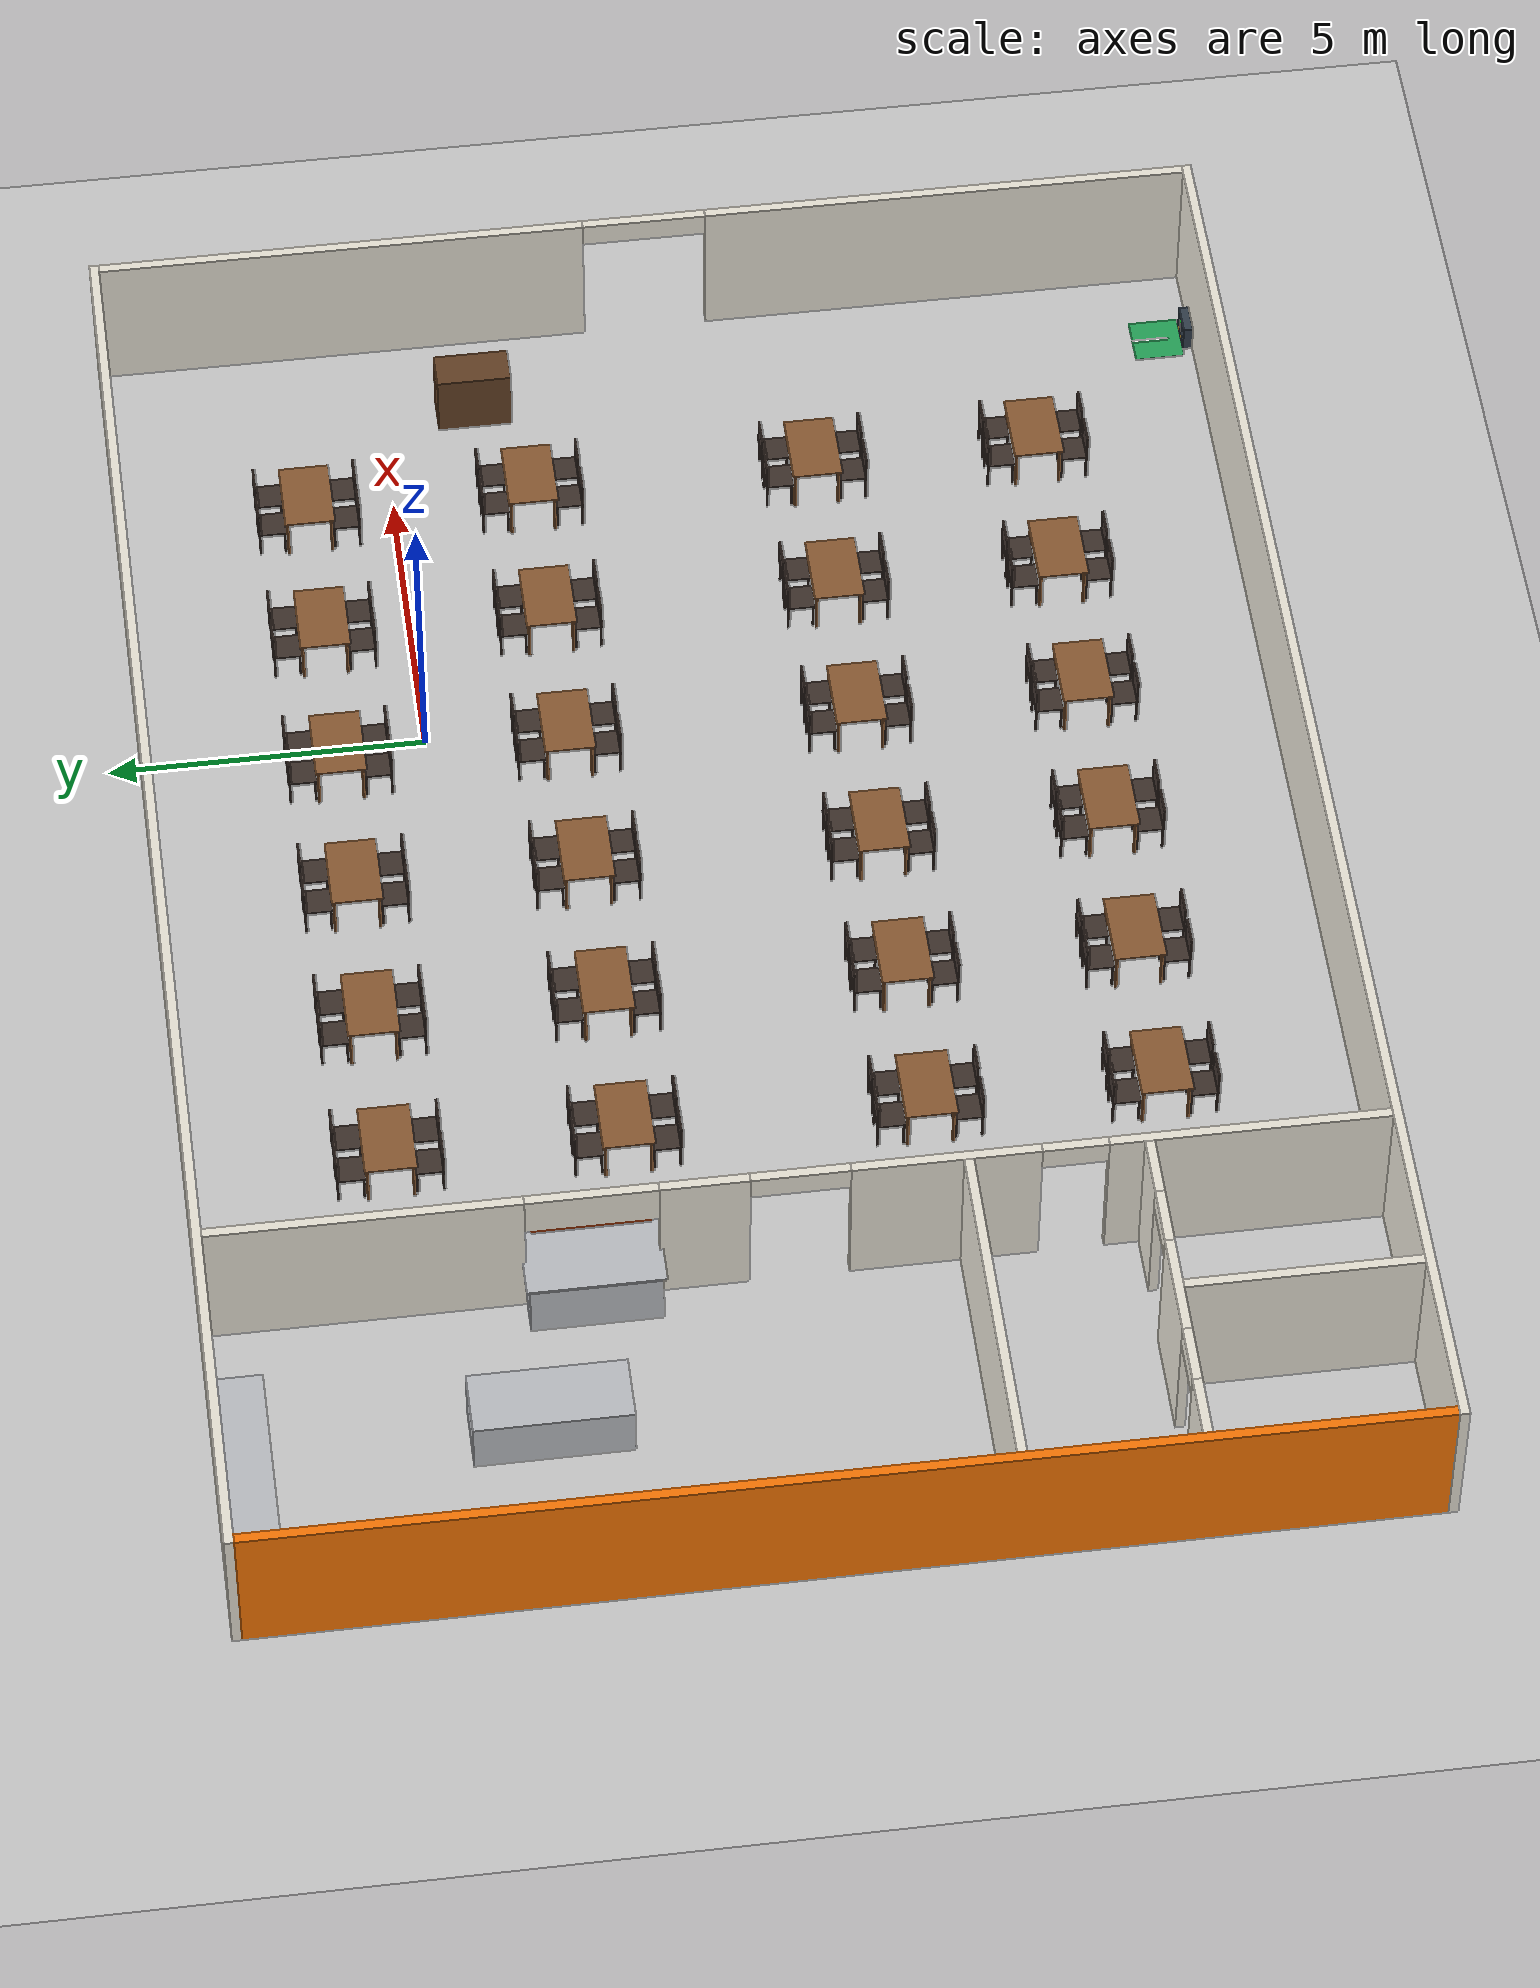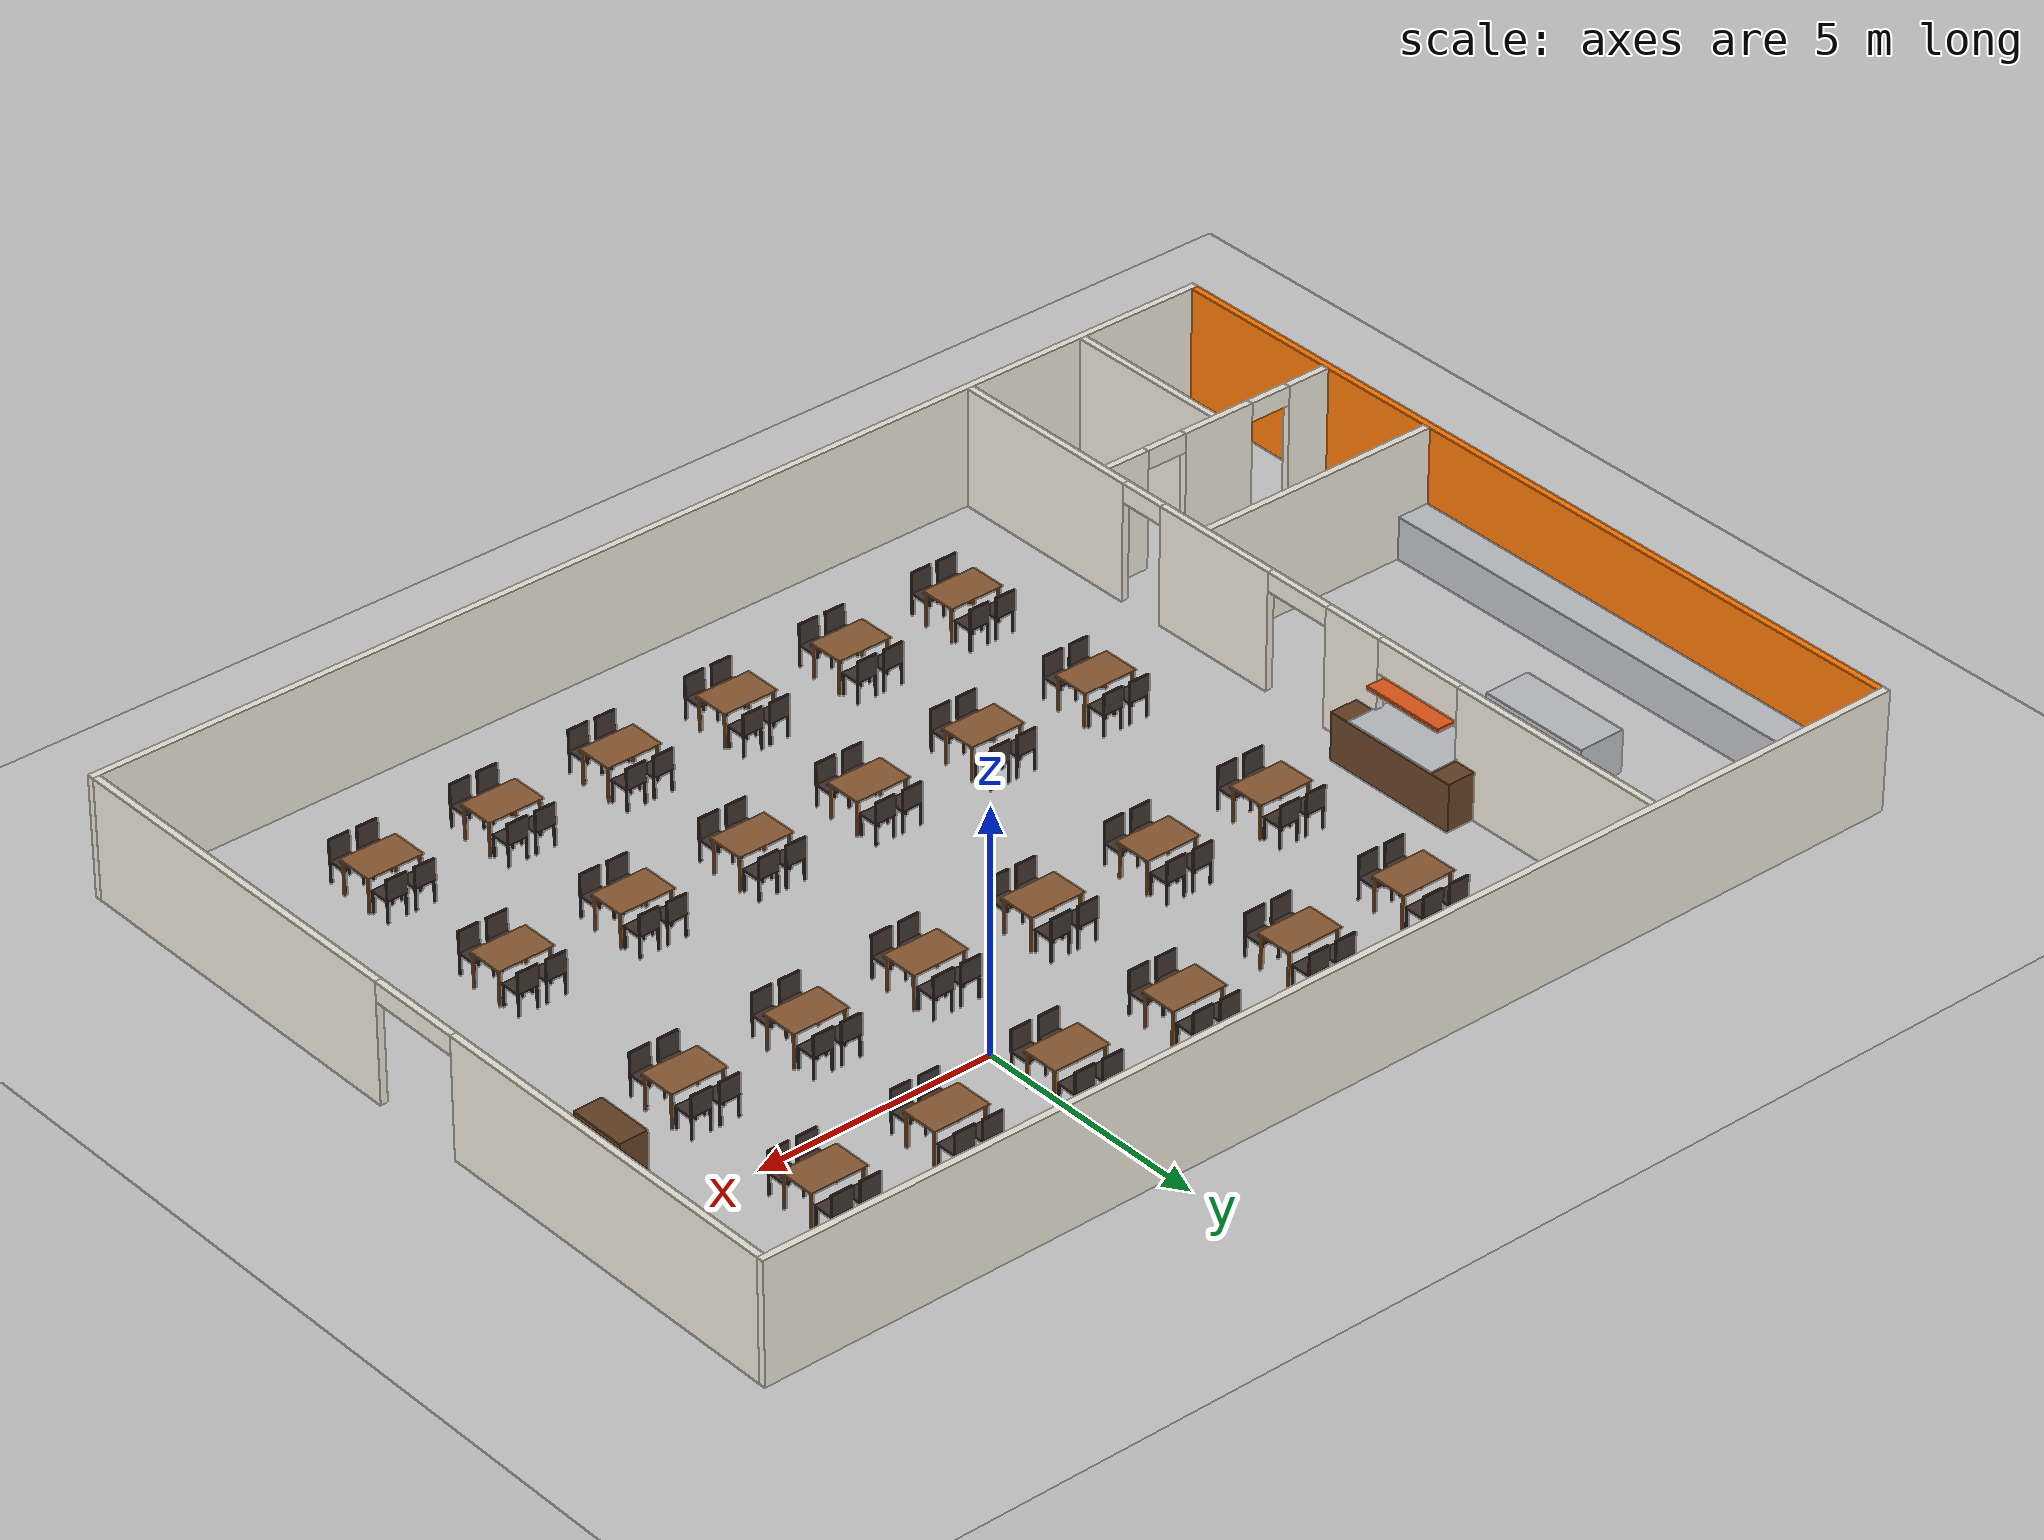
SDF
<sdf version="1.6">
 <world name="restaurant">
  <physics name="1ms" type="ignored">
   <max_step_size>0.001</max_step_size>
   <real_time_factor>1.0</real_time_factor>
  </physics>
  <plugin filename="gz-sim-physics-system" name="gz::sim::systems::Physics"/>
  <plugin filename="gz-sim-user-commands-system" name="gz::sim::systems::UserCommands"/>
  <plugin filename="gz-sim-scene-broadcaster-system" name="gz::sim::systems::SceneBroadcaster"/>
  <plugin filename="gz-sim-sensors-system" name="gz::sim::systems::Sensors">
   <render_engine>ogre2</render_engine>
  </plugin>
  <light name="sun" type="directional">
   <pose>0 0 10 0 -0 0</pose>
   <diffuse>0.8 0.8 0.8 1</diffuse>
   <specular>0.2 0.2 0.2 1</specular>
   <attenuation>
    <range>1000</range>
    <constant>0.9</constant>
    <linear>0.01</linear>
    <quadratic>0.001</quadratic>
   </attenuation>
   <direction>-0.5 0.1 -0.9</direction>
  </light>
  <model name="ground_plane">
   <static>1</static>
   <link name="link">
    <collision name="collision">
     <geometry><plane><normal>0 0 1</normal><size>100 100</size></plane></geometry>
     <surface><friction><ode><mu>100</mu><mu2>50</mu2></ode></friction></surface>
    </collision>
    <visual name="visual">
     <cast_shadows>0</cast_shadows>
     <geometry><plane><normal>0 0 1</normal><size>100 100</size></plane></geometry>
     <material>
      <script><uri>file://media/materials/scripts/gazebo.material</uri><name>Gazebo/Grey</name></script>
     </material>
    </visual>
   </link>
  </model>
  <gravity>0 0 -9.8</gravity>
  <magnetic_field>6e-06 2.3e-05 -4.2e-05</magnetic_field>
  <atmosphere type="adiabatic"/>
  <scene><ambient>0.4 0.4 0.4 1</ambient><background>0.7 0.7 0.7 1</background><shadows>1</shadows></scene>
  <spherical_coordinates>
   <surface_model>EARTH_WGS84</surface_model>
   <latitude_deg>0</latitude_deg>
   <longitude_deg>0</longitude_deg>
   <elevation>0</elevation>
   <heading_deg>0</heading_deg>
  </spherical_coordinates>
  <model name="restaurant">
   <static>true</static>
   <pose>-3.936 -4.4909 0 0 0 0</pose>
   <link name="Wall_8">
    <collision name="Wall_8_n_collision">
     <pose>0.0000 8.9250 1.2500 0 0 0</pose>
     <geometry><box><size>25.0000 0.1500 2.5000</size></box></geometry>
    </collision>
    <visual name="Wall_8_n_visual">
     <pose>0.0000 8.9250 1.2500 0 0 0</pose>
     <geometry><box><size>25.0000 0.1500 2.5000</size></box></geometry>
     <material>
      <ambient>0.93 0.91 0.86 1</ambient>
      <diffuse>0.93 0.91 0.86 1</diffuse>
      <specular>0.05 0.05 0.05 1</specular>
     </material>
    </visual>
   </link>
   <link name="Wall_12">
    <collision name="Wall_12_s_collision">
     <pose>0.0000 -8.9250 1.2500 0 0 0</pose>
     <geometry><box><size>25.0000 0.1500 2.5000</size></box></geometry>
    </collision>
    <visual name="Wall_12_s_visual">
     <pose>0.0000 -8.9250 1.2500 0 0 0</pose>
     <geometry><box><size>25.0000 0.1500 2.5000</size></box></geometry>
     <material>
      <ambient>0.93 0.91 0.86 1</ambient>
      <diffuse>0.93 0.91 0.86 1</diffuse>
      <specular>0.05 0.05 0.05 1</specular>
     </material>
    </visual>
   </link>
   <link name="Wall_10">
    <collision name="Wall_10_w_collision">
     <pose>-12.4250 0.0000 1.2500 0 0 0</pose>
     <geometry><box><size>0.1500 17.7000 2.5000</size></box></geometry>
    </collision>
    <visual name="Wall_10_w_visual">
     <pose>-12.4250 0.0000 1.2500 0 0 0</pose>
     <geometry><box><size>0.1500 17.7000 2.5000</size></box></geometry>
     <material>
      <ambient>0.996078 0.47451 0.0196078 1</ambient>
      <diffuse>0.996078 0.47451 0.0196078 1</diffuse>
      <specular>0.05 0.05 0.05 1</specular>
     </material>
    </visual>
   </link>
   <link name="Wall_14">
    <collision name="Wall_14_a_collision">
     <pose>12.4250 -4.9250 1.2500 0 0 0</pose>
     <geometry><box><size>0.1500 7.8500 2.5000</size></box></geometry>
    </collision>
    <visual name="Wall_14_a_visual">
     <pose>12.4250 -4.9250 1.2500 0 0 0</pose>
     <geometry><box><size>0.1500 7.8500 2.5000</size></box></geometry>
     <material>
      <ambient>0.93 0.91 0.86 1</ambient>
      <diffuse>0.93 0.91 0.86 1</diffuse>
      <specular>0.05 0.05 0.05 1</specular>
     </material>
    </visual>
    <collision name="Wall_14_b_collision">
     <pose>12.4250 4.9250 1.2500 0 0 0</pose>
     <geometry><box><size>0.1500 7.8500 2.5000</size></box></geometry>
    </collision>
    <visual name="Wall_14_b_visual">
     <pose>12.4250 4.9250 1.2500 0 0 0</pose>
     <geometry><box><size>0.1500 7.8500 2.5000</size></box></geometry>
     <material>
      <ambient>0.93 0.91 0.86 1</ambient>
      <diffuse>0.93 0.91 0.86 1</diffuse>
      <specular>0.05 0.05 0.05 1</specular>
     </material>
    </visual>
    <collision name="Wall_14_lintel_collision">
     <pose>12.4250 0.0000 2.3000 0 0 0</pose>
     <geometry><box><size>0.1500 2.0000 0.4000</size></box></geometry>
    </collision>
    <visual name="Wall_14_lintel_visual">
     <pose>12.4250 0.0000 2.3000 0 0 0</pose>
     <geometry><box><size>0.1500 2.0000 0.4000</size></box></geometry>
     <material>
      <ambient>0.93 0.91 0.86 1</ambient>
      <diffuse>0.93 0.91 0.86 1</diffuse>
      <specular>0.05 0.05 0.05 1</specular>
     </material>
    </visual>
   </link>
   <link name="Partition_Kitchen">
    <collision name="Partition_Kitchen_a_collision">
     <pose>-7.0000 -6.7250 1.2500 0 0 0</pose>
     <geometry><box><size>0.1500 4.2500 2.5000</size></box></geometry>
    </collision>
    <visual name="Partition_Kitchen_a_visual">
     <pose>-7.0000 -6.7250 1.2500 0 0 0</pose>
     <geometry><box><size>0.1500 4.2500 2.5000</size></box></geometry>
     <material>
      <ambient>0.93 0.91 0.86 1</ambient>
      <diffuse>0.93 0.91 0.86 1</diffuse>
      <specular>0.05 0.05 0.05 1</specular>
     </material>
    </visual>
    <collision name="Partition_Kitchen_b_collision">
     <pose>-7.0000 -2.1750 1.2500 0 0 0</pose>
     <geometry><box><size>0.1500 2.8500 2.5000</size></box></geometry>
    </collision>
    <visual name="Partition_Kitchen_b_visual">
     <pose>-7.0000 -2.1750 1.2500 0 0 0</pose>
     <geometry><box><size>0.1500 2.8500 2.5000</size></box></geometry>
     <material>
      <ambient>0.93 0.91 0.86 1</ambient>
      <diffuse>0.93 0.91 0.86 1</diffuse>
      <specular>0.05 0.05 0.05 1</specular>
     </material>
    </visual>
    <collision name="Partition_Kitchen_c1_collision">
     <pose>-7.0000 1.4250 1.2500 0 0 0</pose>
     <geometry><box><size>0.1500 1.3500 2.5000</size></box></geometry>
    </collision>
    <visual name="Partition_Kitchen_c1_visual">
     <pose>-7.0000 1.4250 1.2500 0 0 0</pose>
     <geometry><box><size>0.1500 1.3500 2.5000</size></box></geometry>
     <material>
      <ambient>0.93 0.91 0.86 1</ambient>
      <diffuse>0.93 0.91 0.86 1</diffuse>
      <specular>0.05 0.05 0.05 1</specular>
     </material>
    </visual>
    <collision name="Partition_Kitchen_c2_collision">
     <pose>-7.0000 6.4750 1.2500 0 0 0</pose>
     <geometry><box><size>0.1500 4.7500 2.5000</size></box></geometry>
    </collision>
    <visual name="Partition_Kitchen_c2_visual">
     <pose>-7.0000 6.4750 1.2500 0 0 0</pose>
     <geometry><box><size>0.1500 4.7500 2.5000</size></box></geometry>
     <material>
      <ambient>0.93 0.91 0.86 1</ambient>
      <diffuse>0.93 0.91 0.86 1</diffuse>
      <specular>0.05 0.05 0.05 1</specular>
     </material>
    </visual>
    <collision name="Partition_Kitchen_window_sill_collision">
     <pose>-7.0000 3.1000 0.5000 0 0 0</pose>
     <geometry><box><size>0.1500 2.0000 1.0000</size></box></geometry>
    </collision>
    <visual name="Partition_Kitchen_window_sill_visual">
     <pose>-7.0000 3.1000 0.5000 0 0 0</pose>
     <geometry><box><size>0.1500 2.0000 1.0000</size></box></geometry>
     <material>
      <ambient>0.93 0.91 0.86 1</ambient>
      <diffuse>0.93 0.91 0.86 1</diffuse>
      <specular>0.05 0.05 0.05 1</specular>
     </material>
    </visual>
    <collision name="Partition_Kitchen_window_header_collision">
     <pose>-7.0000 3.1000 2.1500 0 0 0</pose>
     <geometry><box><size>0.1500 2.0000 0.7000</size></box></geometry>
    </collision>
    <visual name="Partition_Kitchen_window_header_visual">
     <pose>-7.0000 3.1000 2.1500 0 0 0</pose>
     <geometry><box><size>0.1500 2.0000 0.7000</size></box></geometry>
     <material>
      <ambient>0.93 0.91 0.86 1</ambient>
      <diffuse>0.93 0.91 0.86 1</diffuse>
      <specular>0.05 0.05 0.05 1</specular>
     </material>
    </visual>
    <collision name="Partition_Kitchen_lintel_kitchen_collision">
     <pose>-7.0000 0.0000 2.3000 0 0 0</pose>
     <geometry><box><size>0.1500 1.5000 0.4000</size></box></geometry>
    </collision>
    <visual name="Partition_Kitchen_lintel_kitchen_visual">
     <pose>-7.0000 0.0000 2.3000 0 0 0</pose>
     <geometry><box><size>0.1500 1.5000 0.4000</size></box></geometry>
     <material>
      <ambient>0.93 0.91 0.86 1</ambient>
      <diffuse>0.93 0.91 0.86 1</diffuse>
      <specular>0.05 0.05 0.05 1</specular>
     </material>
    </visual>
    <collision name="Partition_Kitchen_lintel_wc_collision">
     <pose>-7.0000 -4.1000 2.3000 0 0 0</pose>
     <geometry><box><size>0.1500 1.0000 0.4000</size></box></geometry>
    </collision>
    <visual name="Partition_Kitchen_lintel_wc_visual">
     <pose>-7.0000 -4.1000 2.3000 0 0 0</pose>
     <geometry><box><size>0.1500 1.0000 0.4000</size></box></geometry>
     <material>
      <ambient>0.93 0.91 0.86 1</ambient>
      <diffuse>0.93 0.91 0.86 1</diffuse>
      <specular>0.05 0.05 0.05 1</specular>
     </material>
    </visual>
   </link>
   <link name="Wall_Kitchen_South">
    <collision name="Wall_Kitchen_South_w_collision">
     <pose>-9.7125 -2.5000 1.2500 0 0 0</pose>
     <geometry><box><size>5.2750 0.1500 2.5000</size></box></geometry>
    </collision>
    <visual name="Wall_Kitchen_South_w_visual">
     <pose>-9.7125 -2.5000 1.2500 0 0 0</pose>
     <geometry><box><size>5.2750 0.1500 2.5000</size></box></geometry>
     <material>
      <ambient>0.93 0.91 0.86 1</ambient>
      <diffuse>0.93 0.91 0.86 1</diffuse>
      <specular>0.05 0.05 0.05 1</specular>
     </material>
    </visual>
   </link>
   <link name="Wall_Restrooms">
    <collision name="Wall_Restrooms_a_collision">
     <pose>-11.8750 -5.2000 1.2500 0 0 0</pose>
     <geometry><box><size>0.9500 0.1500 2.5000</size></box></geometry>
    </collision>
    <visual name="Wall_Restrooms_a_visual">
     <pose>-11.8750 -5.2000 1.2500 0 0 0</pose>
     <geometry><box><size>0.9500 0.1500 2.5000</size></box></geometry>
     <material>
      <ambient>0.93 0.91 0.86 1</ambient>
      <diffuse>0.93 0.91 0.86 1</diffuse>
      <specular>0.05 0.05 0.05 1</specular>
     </material>
    </visual>
    <collision name="Wall_Restrooms_b_collision">
     <pose>-9.7000 -5.2000 1.2500 0 0 0</pose>
     <geometry><box><size>1.6000 0.1500 2.5000</size></box></geometry>
    </collision>
    <visual name="Wall_Restrooms_b_visual">
     <pose>-9.7000 -5.2000 1.2500 0 0 0</pose>
     <geometry><box><size>1.6000 0.1500 2.5000</size></box></geometry>
     <material>
      <ambient>0.93 0.91 0.86 1</ambient>
      <diffuse>0.93 0.91 0.86 1</diffuse>
      <specular>0.05 0.05 0.05 1</specular>
     </material>
    </visual>
    <collision name="Wall_Restrooms_c_collision">
     <pose>-7.5375 -5.2000 1.2500 0 0 0</pose>
     <geometry><box><size>0.9250 0.1500 2.5000</size></box></geometry>
    </collision>
    <visual name="Wall_Restrooms_c_visual">
     <pose>-7.5375 -5.2000 1.2500 0 0 0</pose>
     <geometry><box><size>0.9250 0.1500 2.5000</size></box></geometry>
     <material>
      <ambient>0.93 0.91 0.86 1</ambient>
      <diffuse>0.93 0.91 0.86 1</diffuse>
      <specular>0.05 0.05 0.05 1</specular>
     </material>
    </visual>
    <collision name="Wall_Restrooms_lintel1_collision">
     <pose>-10.9500 -5.2000 2.3000 0 0 0</pose>
     <geometry><box><size>0.9000 0.1500 0.4000</size></box></geometry>
    </collision>
    <visual name="Wall_Restrooms_lintel1_visual">
     <pose>-10.9500 -5.2000 2.3000 0 0 0</pose>
     <geometry><box><size>0.9000 0.1500 0.4000</size></box></geometry>
     <material>
      <ambient>0.93 0.91 0.86 1</ambient>
      <diffuse>0.93 0.91 0.86 1</diffuse>
      <specular>0.05 0.05 0.05 1</specular>
     </material>
    </visual>
    <collision name="Wall_Restrooms_lintel2_collision">
     <pose>-8.4500 -5.2000 2.3000 0 0 0</pose>
     <geometry><box><size>0.9000 0.1500 0.4000</size></box></geometry>
    </collision>
    <visual name="Wall_Restrooms_lintel2_visual">
     <pose>-8.4500 -5.2000 2.3000 0 0 0</pose>
     <geometry><box><size>0.9000 0.1500 0.4000</size></box></geometry>
     <material>
      <ambient>0.93 0.91 0.86 1</ambient>
      <diffuse>0.93 0.91 0.86 1</diffuse>
      <specular>0.05 0.05 0.05 1</specular>
     </material>
    </visual>
   </link>
   <link name="Wall_Restroom_Divider">
    <collision name="Wall_Restroom_Divider_w_collision">
     <pose>-9.7000 -7.0625 1.2500 0 0 0</pose>
     <geometry><box><size>0.1500 3.5750 2.5000</size></box></geometry>
    </collision>
    <visual name="Wall_Restroom_Divider_w_visual">
     <pose>-9.7000 -7.0625 1.2500 0 0 0</pose>
     <geometry><box><size>0.1500 3.5750 2.5000</size></box></geometry>
     <material>
      <ambient>0.93 0.91 0.86 1</ambient>
      <diffuse>0.93 0.91 0.86 1</diffuse>
      <specular>0.05 0.05 0.05 1</specular>
     </material>
    </visual>
   </link>
   <link name="Kitchen_Counter_West">
    <collision name="Kitchen_Counter_West_c_collision">
     <pose>-12.0000 2.8625 0.4500 0 0 0</pose>
     <geometry><box><size>0.7000 10.5750 0.9000</size></box></geometry>
    </collision>
    <visual name="Kitchen_Counter_West_c_visual">
     <pose>-12.0000 2.8625 0.4500 0 0 0</pose>
     <geometry><box><size>0.7000 10.5750 0.9000</size></box></geometry>
     <material>
      <ambient>0.75 0.76 0.78 1</ambient>
      <diffuse>0.75 0.76 0.78 1</diffuse>
      <specular>0.05 0.05 0.05 1</specular>
     </material>
    </visual>
   </link>
   <link name="Kitchen_Counter_North">
    <collision name="Kitchen_Counter_North_c_collision">
     <pose>-10.4250 8.5000 0.4500 0 0 0</pose>
     <geometry><box><size>3.8500 0.7000 0.9000</size></box></geometry>
    </collision>
    <visual name="Kitchen_Counter_North_c_visual">
     <pose>-10.4250 8.5000 0.4500 0 0 0</pose>
     <geometry><box><size>3.8500 0.7000 0.9000</size></box></geometry>
     <material>
      <ambient>0.75 0.76 0.78 1</ambient>
      <diffuse>0.75 0.76 0.78 1</diffuse>
      <specular>0.05 0.05 0.05 1</specular>
     </material>
    </visual>
   </link>
   <link name="Kitchen_Island">
    <collision name="Kitchen_Island_c_collision">
     <pose>-9.4000 4.0000 0.4500 0 0 0</pose>
     <geometry><box><size>1.0000 2.4000 0.9000</size></box></geometry>
    </collision>
    <visual name="Kitchen_Island_c_visual">
     <pose>-9.4000 4.0000 0.4500 0 0 0</pose>
     <geometry><box><size>1.0000 2.4000 0.9000</size></box></geometry>
     <material>
      <ambient>0.75 0.76 0.78 1</ambient>
      <diffuse>0.75 0.76 0.78 1</diffuse>
      <specular>0.05 0.05 0.05 1</specular>
     </material>
    </visual>
   </link>
   <link name="Pickup_Counter">
    <collision name="Pickup_Counter_c_collision">
     <pose>-6.6250 3.1000 0.5000 0 0 0</pose>
     <geometry><box><size>0.6000 3.0000 1.0000</size></box></geometry>
    </collision>
    <visual name="Pickup_Counter_c_visual">
     <pose>-6.6250 3.1000 0.5000 0 0 0</pose>
     <geometry><box><size>0.6000 3.0000 1.0000</size></box></geometry>
     <material>
      <ambient>0.4 0.26 0.15 1</ambient>
      <diffuse>0.4 0.26 0.15 1</diffuse>
      <specular>0.05 0.05 0.05 1</specular>
     </material>
    </visual>
   </link>
   <link name="Kitchen_Pass_Counter">
    <collision name="Kitchen_Pass_Counter_c_collision">
     <pose>-7.3250 3.1000 0.5000 0 0 0</pose>
     <geometry><box><size>0.5000 2.0000 1.0000</size></box></geometry>
    </collision>
    <visual name="Kitchen_Pass_Counter_c_visual">
     <pose>-7.3250 3.1000 0.5000 0 0 0</pose>
     <geometry><box><size>0.5000 2.0000 1.0000</size></box></geometry>
     <material>
      <ambient>0.75 0.76 0.78 1</ambient>
      <diffuse>0.75 0.76 0.78 1</diffuse>
      <specular>0.05 0.05 0.05 1</specular>
     </material>
    </visual>
   </link>
   <link name="Pass_Shelf">
    <collision name="Pass_Shelf_c_collision">
     <pose>-6.9750 3.1000 1.0150 0 0 0</pose>
     <geometry><box><size>1.3000 2.1000 0.0300</size></box></geometry>
    </collision>
    <visual name="Pass_Shelf_c_visual">
     <pose>-6.9750 3.1000 1.0150 0 0 0</pose>
     <geometry><box><size>1.3000 2.1000 0.0300</size></box></geometry>
     <material>
      <ambient>0.75 0.76 0.78 1</ambient>
      <diffuse>0.75 0.76 0.78 1</diffuse>
      <specular>0.05 0.05 0.05 1</specular>
     </material>
    </visual>
   </link>
   <link name="Heat_Lamp">
    <collision name="Heat_Lamp_c_collision">
     <pose>-6.8000 3.1000 1.6850 0 0 0</pose>
     <geometry><box><size>0.4000 1.8000 0.0700</size></box></geometry>
    </collision>
    <visual name="Heat_Lamp_c_visual">
     <pose>-6.8000 3.1000 1.6850 0 0 0</pose>
     <geometry><box><size>0.4000 1.8000 0.0700</size></box></geometry>
     <material>
      <ambient>0.9 0.35 0.1 1</ambient>
      <diffuse>0.9 0.35 0.1 1</diffuse>
      <specular>0.05 0.05 0.05 1</specular>
     </material>
    </visual>
   </link>
   <link name="Host_Stand">
    <collision name="Host_Stand_c_collision">
     <pose>10.8000 3.0000 0.5500 0 0 0</pose>
     <geometry><box><size>0.6000 1.2000 1.1000</size></box></geometry>
    </collision>
    <visual name="Host_Stand_c_visual">
     <pose>10.8000 3.0000 0.5500 0 0 0</pose>
     <geometry><box><size>0.6000 1.2000 1.1000</size></box></geometry>
     <material>
      <ambient>0.4 0.26 0.15 1</ambient>
      <diffuse>0.4 0.26 0.15 1</diffuse>
      <specular>0.05 0.05 0.05 1</specular>
     </material>
    </visual>
   </link>
  </model>
  <model name="table_0">
   <static>true</static>
   <pose>-8.2360 1.4091 0 0 0 0</pose>
   <link name="link">
    <collision name="top_collision">
     <pose>0.0000 0.0000 0.7300 0 0 0</pose>
     <geometry><box><size>1.2000 0.8000 0.0400</size></box></geometry>
    </collision>
    <visual name="top_visual">
     <pose>0.0000 0.0000 0.7300 0 0 0</pose>
     <geometry><box><size>1.2000 0.8000 0.0400</size></box></geometry>
     <material>
      <ambient>0.55 0.36 0.2 1</ambient>
      <diffuse>0.55 0.36 0.2 1</diffuse>
      <specular>0.05 0.05 0.05 1</specular>
     </material>
    </visual>
    <collision name="leg0_collision">
     <pose>0.5500 0.3500 0.3550 0 0 0</pose>
     <geometry><box><size>0.0500 0.0500 0.7100</size></box></geometry>
    </collision>
    <visual name="leg0_visual">
     <pose>0.5500 0.3500 0.3550 0 0 0</pose>
     <geometry><box><size>0.0500 0.0500 0.7100</size></box></geometry>
     <material>
      <ambient>0.55 0.36 0.2 1</ambient>
      <diffuse>0.55 0.36 0.2 1</diffuse>
      <specular>0.05 0.05 0.05 1</specular>
     </material>
    </visual>
    <collision name="leg1_collision">
     <pose>0.5500 -0.3500 0.3550 0 0 0</pose>
     <geometry><box><size>0.0500 0.0500 0.7100</size></box></geometry>
    </collision>
    <visual name="leg1_visual">
     <pose>0.5500 -0.3500 0.3550 0 0 0</pose>
     <geometry><box><size>0.0500 0.0500 0.7100</size></box></geometry>
     <material>
      <ambient>0.55 0.36 0.2 1</ambient>
      <diffuse>0.55 0.36 0.2 1</diffuse>
      <specular>0.05 0.05 0.05 1</specular>
     </material>
    </visual>
    <collision name="leg2_collision">
     <pose>-0.5500 0.3500 0.3550 0 0 0</pose>
     <geometry><box><size>0.0500 0.0500 0.7100</size></box></geometry>
    </collision>
    <visual name="leg2_visual">
     <pose>-0.5500 0.3500 0.3550 0 0 0</pose>
     <geometry><box><size>0.0500 0.0500 0.7100</size></box></geometry>
     <material>
      <ambient>0.55 0.36 0.2 1</ambient>
      <diffuse>0.55 0.36 0.2 1</diffuse>
      <specular>0.05 0.05 0.05 1</specular>
     </material>
    </visual>
    <collision name="leg3_collision">
     <pose>-0.5500 -0.3500 0.3550 0 0 0</pose>
     <geometry><box><size>0.0500 0.0500 0.7100</size></box></geometry>
    </collision>
    <visual name="leg3_visual">
     <pose>-0.5500 -0.3500 0.3550 0 0 0</pose>
     <geometry><box><size>0.0500 0.0500 0.7100</size></box></geometry>
     <material>
      <ambient>0.55 0.36 0.2 1</ambient>
      <diffuse>0.55 0.36 0.2 1</diffuse>
      <specular>0.05 0.05 0.05 1</specular>
     </material>
    </visual>
    <collision name="chair0_seat_collision">
     <pose>-0.3000 0.6000 0.4500 0 0 0</pose>
     <geometry><box><size>0.4500 0.4500 0.0400</size></box></geometry>
    </collision>
    <visual name="chair0_seat_visual">
     <pose>-0.3000 0.6000 0.4500 0 0 0</pose>
     <geometry><box><size>0.4500 0.4500 0.0400</size></box></geometry>
     <material>
      <ambient>0.25 0.2 0.18 1</ambient>
      <diffuse>0.25 0.2 0.18 1</diffuse>
      <specular>0.05 0.05 0.05 1</specular>
     </material>
    </visual>
    <collision name="chair0_leg0_collision">
     <pose>-0.1000 0.8000 0.2150 0 0 0</pose>
     <geometry><box><size>0.0400 0.0400 0.4300</size></box></geometry>
    </collision>
    <visual name="chair0_leg0_visual">
     <pose>-0.1000 0.8000 0.2150 0 0 0</pose>
     <geometry><box><size>0.0400 0.0400 0.4300</size></box></geometry>
     <material>
      <ambient>0.25 0.2 0.18 1</ambient>
      <diffuse>0.25 0.2 0.18 1</diffuse>
      <specular>0.05 0.05 0.05 1</specular>
     </material>
    </visual>
    <collision name="chair0_leg1_collision">
     <pose>-0.1000 0.4000 0.2150 0 0 0</pose>
     <geometry><box><size>0.0400 0.0400 0.4300</size></box></geometry>
    </collision>
    <visual name="chair0_leg1_visual">
     <pose>-0.1000 0.4000 0.2150 0 0 0</pose>
     <geometry><box><size>0.0400 0.0400 0.4300</size></box></geometry>
     <material>
      <ambient>0.25 0.2 0.18 1</ambient>
      <diffuse>0.25 0.2 0.18 1</diffuse>
      <specular>0.05 0.05 0.05 1</specular>
     </material>
    </visual>
    <collision name="chair0_leg2_collision">
     <pose>-0.5000 0.8000 0.2150 0 0 0</pose>
     <geometry><box><size>0.0400 0.0400 0.4300</size></box></geometry>
    </collision>
    <visual name="chair0_leg2_visual">
     <pose>-0.5000 0.8000 0.2150 0 0 0</pose>
     <geometry><box><size>0.0400 0.0400 0.4300</size></box></geometry>
     <material>
      <ambient>0.25 0.2 0.18 1</ambient>
      <diffuse>0.25 0.2 0.18 1</diffuse>
      <specular>0.05 0.05 0.05 1</specular>
     </material>
    </visual>
    <collision name="chair0_leg3_collision">
     <pose>-0.5000 0.4000 0.2150 0 0 0</pose>
     <geometry><box><size>0.0400 0.0400 0.4300</size></box></geometry>
    </collision>
    <visual name="chair0_leg3_visual">
     <pose>-0.5000 0.4000 0.2150 0 0 0</pose>
     <geometry><box><size>0.0400 0.0400 0.4300</size></box></geometry>
     <material>
      <ambient>0.25 0.2 0.18 1</ambient>
      <diffuse>0.25 0.2 0.18 1</diffuse>
      <specular>0.05 0.05 0.05 1</specular>
     </material>
    </visual>
    <collision name="chair0_back_collision">
     <pose>-0.3000 0.8050 0.6850 0 0 0</pose>
     <geometry><box><size>0.4500 0.0400 0.4300</size></box></geometry>
    </collision>
    <visual name="chair0_back_visual">
     <pose>-0.3000 0.8050 0.6850 0 0 0</pose>
     <geometry><box><size>0.4500 0.0400 0.4300</size></box></geometry>
     <material>
      <ambient>0.25 0.2 0.18 1</ambient>
      <diffuse>0.25 0.2 0.18 1</diffuse>
      <specular>0.05 0.05 0.05 1</specular>
     </material>
    </visual>
    <collision name="chair1_seat_collision">
     <pose>-0.3000 -0.6000 0.4500 0 0 0</pose>
     <geometry><box><size>0.4500 0.4500 0.0400</size></box></geometry>
    </collision>
    <visual name="chair1_seat_visual">
     <pose>-0.3000 -0.6000 0.4500 0 0 0</pose>
     <geometry><box><size>0.4500 0.4500 0.0400</size></box></geometry>
     <material>
      <ambient>0.25 0.2 0.18 1</ambient>
      <diffuse>0.25 0.2 0.18 1</diffuse>
      <specular>0.05 0.05 0.05 1</specular>
     </material>
    </visual>
    <collision name="chair1_leg0_collision">
     <pose>-0.1000 -0.4000 0.2150 0 0 0</pose>
     <geometry><box><size>0.0400 0.0400 0.4300</size></box></geometry>
    </collision>
    <visual name="chair1_leg0_visual">
     <pose>-0.1000 -0.4000 0.2150 0 0 0</pose>
     <geometry><box><size>0.0400 0.0400 0.4300</size></box></geometry>
     <material>
      <ambient>0.25 0.2 0.18 1</ambient>
      <diffuse>0.25 0.2 0.18 1</diffuse>
      <specular>0.05 0.05 0.05 1</specular>
     </material>
    </visual>
    <collision name="chair1_leg1_collision">
     <pose>-0.1000 -0.8000 0.2150 0 0 0</pose>
     <geometry><box><size>0.0400 0.0400 0.4300</size></box></geometry>
    </collision>
    <visual name="chair1_leg1_visual">
     <pose>-0.1000 -0.8000 0.2150 0 0 0</pose>
     <geometry><box><size>0.0400 0.0400 0.4300</size></box></geometry>
     <material>
      <ambient>0.25 0.2 0.18 1</ambient>
      <diffuse>0.25 0.2 0.18 1</diffuse>
      <specular>0.05 0.05 0.05 1</specular>
     </material>
    </visual>
    <collision name="chair1_leg2_collision">
     <pose>-0.5000 -0.4000 0.2150 0 0 0</pose>
     <geometry><box><size>0.0400 0.0400 0.4300</size></box></geometry>
    </collision>
    <visual name="chair1_leg2_visual">
     <pose>-0.5000 -0.4000 0.2150 0 0 0</pose>
     <geometry><box><size>0.0400 0.0400 0.4300</size></box></geometry>
     <material>
      <ambient>0.25 0.2 0.18 1</ambient>
      <diffuse>0.25 0.2 0.18 1</diffuse>
      <specular>0.05 0.05 0.05 1</specular>
     </material>
    </visual>
    <collision name="chair1_leg3_collision">
     <pose>-0.5000 -0.8000 0.2150 0 0 0</pose>
     <geometry><box><size>0.0400 0.0400 0.4300</size></box></geometry>
    </collision>
    <visual name="chair1_leg3_visual">
     <pose>-0.5000 -0.8000 0.2150 0 0 0</pose>
     <geometry><box><size>0.0400 0.0400 0.4300</size></box></geometry>
     <material>
      <ambient>0.25 0.2 0.18 1</ambient>
      <diffuse>0.25 0.2 0.18 1</diffuse>
      <specular>0.05 0.05 0.05 1</specular>
     </material>
    </visual>
    <collision name="chair1_back_collision">
     <pose>-0.3000 -0.8050 0.6850 0 0 0</pose>
     <geometry><box><size>0.4500 0.0400 0.4300</size></box></geometry>
    </collision>
    <visual name="chair1_back_visual">
     <pose>-0.3000 -0.8050 0.6850 0 0 0</pose>
     <geometry><box><size>0.4500 0.0400 0.4300</size></box></geometry>
     <material>
      <ambient>0.25 0.2 0.18 1</ambient>
      <diffuse>0.25 0.2 0.18 1</diffuse>
      <specular>0.05 0.05 0.05 1</specular>
     </material>
    </visual>
    <collision name="chair2_seat_collision">
     <pose>0.3000 0.6000 0.4500 0 0 0</pose>
     <geometry><box><size>0.4500 0.4500 0.0400</size></box></geometry>
    </collision>
    <visual name="chair2_seat_visual">
     <pose>0.3000 0.6000 0.4500 0 0 0</pose>
     <geometry><box><size>0.4500 0.4500 0.0400</size></box></geometry>
     <material>
      <ambient>0.25 0.2 0.18 1</ambient>
      <diffuse>0.25 0.2 0.18 1</diffuse>
      <specular>0.05 0.05 0.05 1</specular>
     </material>
    </visual>
    <collision name="chair2_leg0_collision">
     <pose>0.5000 0.8000 0.2150 0 0 0</pose>
     <geometry><box><size>0.0400 0.0400 0.4300</size></box></geometry>
    </collision>
    <visual name="chair2_leg0_visual">
     <pose>0.5000 0.8000 0.2150 0 0 0</pose>
     <geometry><box><size>0.0400 0.0400 0.4300</size></box></geometry>
     <material>
      <ambient>0.25 0.2 0.18 1</ambient>
      <diffuse>0.25 0.2 0.18 1</diffuse>
      <specular>0.05 0.05 0.05 1</specular>
     </material>
    </visual>
    <collision name="chair2_leg1_collision">
     <pose>0.5000 0.4000 0.2150 0 0 0</pose>
     <geometry><box><size>0.0400 0.0400 0.4300</size></box></geometry>
    </collision>
    <visual name="chair2_leg1_visual">
     <pose>0.5000 0.4000 0.2150 0 0 0</pose>
     <geometry><box><size>0.0400 0.0400 0.4300</size></box></geometry>
     <material>
      <ambient>0.25 0.2 0.18 1</ambient>
      <diffuse>0.25 0.2 0.18 1</diffuse>
      <specular>0.05 0.05 0.05 1</specular>
     </material>
    </visual>
    <collision name="chair2_leg2_collision">
     <pose>0.1000 0.8000 0.2150 0 0 0</pose>
     <geometry><box><size>0.0400 0.0400 0.4300</size></box></geometry>
    </collision>
    <visual name="chair2_leg2_visual">
     <pose>0.1000 0.8000 0.2150 0 0 0</pose>
     <geometry><box><size>0.0400 0.0400 0.4300</size></box></geometry>
     <material>
      <ambient>0.25 0.2 0.18 1</ambient>
      <diffuse>0.25 0.2 0.18 1</diffuse>
      <specular>0.05 0.05 0.05 1</specular>
     </material>
    </visual>
    <collision name="chair2_leg3_collision">
     <pose>0.1000 0.4000 0.2150 0 0 0</pose>
     <geometry><box><size>0.0400 0.0400 0.4300</size></box></geometry>
    </collision>
    <visual name="chair2_leg3_visual">
     <pose>0.1000 0.4000 0.2150 0 0 0</pose>
     <geometry><box><size>0.0400 0.0400 0.4300</size></box></geometry>
     <material>
      <ambient>0.25 0.2 0.18 1</ambient>
      <diffuse>0.25 0.2 0.18 1</diffuse>
      <specular>0.05 0.05 0.05 1</specular>
     </material>
    </visual>
    <collision name="chair2_back_collision">
     <pose>0.3000 0.8050 0.6850 0 0 0</pose>
     <geometry><box><size>0.4500 0.0400 0.4300</size></box></geometry>
    </collision>
    <visual name="chair2_back_visual">
     <pose>0.3000 0.8050 0.6850 0 0 0</pose>
     <geometry><box><size>0.4500 0.0400 0.4300</size></box></geometry>
     <material>
      <ambient>0.25 0.2 0.18 1</ambient>
      <diffuse>0.25 0.2 0.18 1</diffuse>
      <specular>0.05 0.05 0.05 1</specular>
     </material>
    </visual>
    <collision name="chair3_seat_collision">
     <pose>0.3000 -0.6000 0.4500 0 0 0</pose>
     <geometry><box><size>0.4500 0.4500 0.0400</size></box></geometry>
    </collision>
    <visual name="chair3_seat_visual">
     <pose>0.3000 -0.6000 0.4500 0 0 0</pose>
     <geometry><box><size>0.4500 0.4500 0.0400</size></box></geometry>
     <material>
      <ambient>0.25 0.2 0.18 1</ambient>
      <diffuse>0.25 0.2 0.18 1</diffuse>
      <specular>0.05 0.05 0.05 1</specular>
     </material>
    </visual>
    <collision name="chair3_leg0_collision">
     <pose>0.5000 -0.4000 0.2150 0 0 0</pose>
     <geometry><box><size>0.0400 0.0400 0.4300</size></box></geometry>
    </collision>
    <visual name="chair3_leg0_visual">
     <pose>0.5000 -0.4000 0.2150 0 0 0</pose>
     <geometry><box><size>0.0400 0.0400 0.4300</size></box></geometry>
     <material>
      <ambient>0.25 0.2 0.18 1</ambient>
      <diffuse>0.25 0.2 0.18 1</diffuse>
      <specular>0.05 0.05 0.05 1</specular>
     </material>
    </visual>
    <collision name="chair3_leg1_collision">
     <pose>0.5000 -0.8000 0.2150 0 0 0</pose>
     <geometry><box><size>0.0400 0.0400 0.4300</size></box></geometry>
    </collision>
    <visual name="chair3_leg1_visual">
     <pose>0.5000 -0.8000 0.2150 0 0 0</pose>
     <geometry><box><size>0.0400 0.0400 0.4300</size></box></geometry>
     <material>
      <ambient>0.25 0.2 0.18 1</ambient>
      <diffuse>0.25 0.2 0.18 1</diffuse>
      <specular>0.05 0.05 0.05 1</specular>
     </material>
    </visual>
    <collision name="chair3_leg2_collision">
     <pose>0.1000 -0.4000 0.2150 0 0 0</pose>
     <geometry><box><size>0.0400 0.0400 0.4300</size></box></geometry>
    </collision>
    <visual name="chair3_leg2_visual">
     <pose>0.1000 -0.4000 0.2150 0 0 0</pose>
     <geometry><box><size>0.0400 0.0400 0.4300</size></box></geometry>
     <material>
      <ambient>0.25 0.2 0.18 1</ambient>
      <diffuse>0.25 0.2 0.18 1</diffuse>
      <specular>0.05 0.05 0.05 1</specular>
     </material>
    </visual>
    <collision name="chair3_leg3_collision">
     <pose>0.1000 -0.8000 0.2150 0 0 0</pose>
     <geometry><box><size>0.0400 0.0400 0.4300</size></box></geometry>
    </collision>
    <visual name="chair3_leg3_visual">
     <pose>0.1000 -0.8000 0.2150 0 0 0</pose>
     <geometry><box><size>0.0400 0.0400 0.4300</size></box></geometry>
     <material>
      <ambient>0.25 0.2 0.18 1</ambient>
      <diffuse>0.25 0.2 0.18 1</diffuse>
      <specular>0.05 0.05 0.05 1</specular>
     </material>
    </visual>
    <collision name="chair3_back_collision">
     <pose>0.3000 -0.8050 0.6850 0 0 0</pose>
     <geometry><box><size>0.4500 0.0400 0.4300</size></box></geometry>
    </collision>
    <visual name="chair3_back_visual">
     <pose>0.3000 -0.8050 0.6850 0 0 0</pose>
     <geometry><box><size>0.4500 0.0400 0.4300</size></box></geometry>
     <material>
      <ambient>0.25 0.2 0.18 1</ambient>
      <diffuse>0.25 0.2 0.18 1</diffuse>
      <specular>0.05 0.05 0.05 1</specular>
     </material>
    </visual>
   </link>
  </model>
  <model name="table_1">
   <static>true</static>
   <pose>-5.6360 1.4091 0 0 0 0</pose>
   <link name="link">
    <collision name="top_collision">
     <pose>0.0000 0.0000 0.7300 0 0 0</pose>
     <geometry><box><size>1.2000 0.8000 0.0400</size></box></geometry>
    </collision>
    <visual name="top_visual">
     <pose>0.0000 0.0000 0.7300 0 0 0</pose>
     <geometry><box><size>1.2000 0.8000 0.0400</size></box></geometry>
     <material>
      <ambient>0.55 0.36 0.2 1</ambient>
      <diffuse>0.55 0.36 0.2 1</diffuse>
      <specular>0.05 0.05 0.05 1</specular>
     </material>
    </visual>
    <collision name="leg0_collision">
     <pose>0.5500 0.3500 0.3550 0 0 0</pose>
     <geometry><box><size>0.0500 0.0500 0.7100</size></box></geometry>
    </collision>
    <visual name="leg0_visual">
     <pose>0.5500 0.3500 0.3550 0 0 0</pose>
     <geometry><box><size>0.0500 0.0500 0.7100</size></box></geometry>
     <material>
      <ambient>0.55 0.36 0.2 1</ambient>
      <diffuse>0.55 0.36 0.2 1</diffuse>
      <specular>0.05 0.05 0.05 1</specular>
     </material>
    </visual>
    <collision name="leg1_collision">
     <pose>0.5500 -0.3500 0.3550 0 0 0</pose>
     <geometry><box><size>0.0500 0.0500 0.7100</size></box></geometry>
    </collision>
    <visual name="leg1_visual">
     <pose>0.5500 -0.3500 0.3550 0 0 0</pose>
     <geometry><box><size>0.0500 0.0500 0.7100</size></box></geometry>
     <material>
      <ambient>0.55 0.36 0.2 1</ambient>
      <diffuse>0.55 0.36 0.2 1</diffuse>
      <specular>0.05 0.05 0.05 1</specular>
     </material>
    </visual>
    <collision name="leg2_collision">
     <pose>-0.5500 0.3500 0.3550 0 0 0</pose>
     <geometry><box><size>0.0500 0.0500 0.7100</size></box></geometry>
    </collision>
    <visual name="leg2_visual">
     <pose>-0.5500 0.3500 0.3550 0 0 0</pose>
     <geometry><box><size>0.0500 0.0500 0.7100</size></box></geometry>
     <material>
      <ambient>0.55 0.36 0.2 1</ambient>
      <diffuse>0.55 0.36 0.2 1</diffuse>
      <specular>0.05 0.05 0.05 1</specular>
     </material>
    </visual>
    <collision name="leg3_collision">
     <pose>-0.5500 -0.3500 0.3550 0 0 0</pose>
     <geometry><box><size>0.0500 0.0500 0.7100</size></box></geometry>
    </collision>
    <visual name="leg3_visual">
     <pose>-0.5500 -0.3500 0.3550 0 0 0</pose>
     <geometry><box><size>0.0500 0.0500 0.7100</size></box></geometry>
     <material>
      <ambient>0.55 0.36 0.2 1</ambient>
      <diffuse>0.55 0.36 0.2 1</diffuse>
      <specular>0.05 0.05 0.05 1</specular>
     </material>
    </visual>
    <collision name="chair0_seat_collision">
     <pose>-0.3000 0.6000 0.4500 0 0 0</pose>
     <geometry><box><size>0.4500 0.4500 0.0400</size></box></geometry>
    </collision>
    <visual name="chair0_seat_visual">
     <pose>-0.3000 0.6000 0.4500 0 0 0</pose>
     <geometry><box><size>0.4500 0.4500 0.0400</size></box></geometry>
     <material>
      <ambient>0.25 0.2 0.18 1</ambient>
      <diffuse>0.25 0.2 0.18 1</diffuse>
      <specular>0.05 0.05 0.05 1</specular>
     </material>
    </visual>
    <collision name="chair0_leg0_collision">
     <pose>-0.1000 0.8000 0.2150 0 0 0</pose>
     <geometry><box><size>0.0400 0.0400 0.4300</size></box></geometry>
    </collision>
    <visual name="chair0_leg0_visual">
     <pose>-0.1000 0.8000 0.2150 0 0 0</pose>
     <geometry><box><size>0.0400 0.0400 0.4300</size></box></geometry>
     <material>
      <ambient>0.25 0.2 0.18 1</ambient>
      <diffuse>0.25 0.2 0.18 1</diffuse>
      <specular>0.05 0.05 0.05 1</specular>
     </material>
    </visual>
    <collision name="chair0_leg1_collision">
     <pose>-0.1000 0.4000 0.2150 0 0 0</pose>
     <geometry><box><size>0.0400 0.0400 0.4300</size></box></geometry>
    </collision>
    <visual name="chair0_leg1_visual">
     <pose>-0.1000 0.4000 0.2150 0 0 0</pose>
     <geometry><box><size>0.0400 0.0400 0.4300</size></box></geometry>
     <material>
      <ambient>0.25 0.2 0.18 1</ambient>
      <diffuse>0.25 0.2 0.18 1</diffuse>
      <specular>0.05 0.05 0.05 1</specular>
     </material>
    </visual>
    <collision name="chair0_leg2_collision">
     <pose>-0.5000 0.8000 0.2150 0 0 0</pose>
     <geometry><box><size>0.0400 0.0400 0.4300</size></box></geometry>
    </collision>
    <visual name="chair0_leg2_visual">
     <pose>-0.5000 0.8000 0.2150 0 0 0</pose>
     <geometry><box><size>0.0400 0.0400 0.4300</size></box></geometry>
     <material>
      <ambient>0.25 0.2 0.18 1</ambient>
      <diffuse>0.25 0.2 0.18 1</diffuse>
      <specular>0.05 0.05 0.05 1</specular>
     </material>
    </visual>
    <collision name="chair0_leg3_collision">
     <pose>-0.5000 0.4000 0.2150 0 0 0</pose>
     <geometry><box><size>0.0400 0.0400 0.4300</size></box></geometry>
    </collision>
    <visual name="chair0_leg3_visual">
     <pose>-0.5000 0.4000 0.2150 0 0 0</pose>
     <geometry><box><size>0.0400 0.0400 0.4300</size></box></geometry>
     <material>
      <ambient>0.25 0.2 0.18 1</ambient>
      <diffuse>0.25 0.2 0.18 1</diffuse>
      <specular>0.05 0.05 0.05 1</specular>
     </material>
    </visual>
    <collision name="chair0_back_collision">
     <pose>-0.3000 0.8050 0.6850 0 0 0</pose>
     <geometry><box><size>0.4500 0.0400 0.4300</size></box></geometry>
    </collision>
    <visual name="chair0_back_visual">
     <pose>-0.3000 0.8050 0.6850 0 0 0</pose>
     <geometry><box><size>0.4500 0.0400 0.4300</size></box></geometry>
     <material>
      <ambient>0.25 0.2 0.18 1</ambient>
      <diffuse>0.25 0.2 0.18 1</diffuse>
      <specular>0.05 0.05 0.05 1</specular>
     </material>
    </visual>
    <collision name="chair1_seat_collision">
     <pose>-0.3000 -0.6000 0.4500 0 0 0</pose>
     <geometry><box><size>0.4500 0.4500 0.0400</size></box></geometry>
    </collision>
    <visual name="chair1_seat_visual">
     <pose>-0.3000 -0.6000 0.4500 0 0 0</pose>
     <geometry><box><size>0.4500 0.4500 0.0400</size></box></geometry>
     <material>
      <ambient>0.25 0.2 0.18 1</ambient>
      <diffuse>0.25 0.2 0.18 1</diffuse>
      <specular>0.05 0.05 0.05 1</specular>
     </material>
    </visual>
    <collision name="chair1_leg0_collision">
     <pose>-0.1000 -0.4000 0.2150 0 0 0</pose>
     <geometry><box><size>0.0400 0.0400 0.4300</size></box></geometry>
    </collision>
    <visual name="chair1_leg0_visual">
     <pose>-0.1000 -0.4000 0.2150 0 0 0</pose>
     <geometry><box><size>0.0400 0.0400 0.4300</size></box></geometry>
     <material>
      <ambient>0.25 0.2 0.18 1</ambient>
      <diffuse>0.25 0.2 0.18 1</diffuse>
      <specular>0.05 0.05 0.05 1</specular>
     </material>
    </visual>
    <collision name="chair1_leg1_collision">
     <pose>-0.1000 -0.8000 0.2150 0 0 0</pose>
     <geometry><box><size>0.0400 0.0400 0.4300</size></box></geometry>
    </collision>
    <visual name="chair1_leg1_visual">
     <pose>-0.1000 -0.8000 0.2150 0 0 0</pose>
     <geometry><box><size>0.0400 0.0400 0.4300</size></box></geometry>
     <material>
      <ambient>0.25 0.2 0.18 1</ambient>
      <diffuse>0.25 0.2 0.18 1</diffuse>
      <specular>0.05 0.05 0.05 1</specular>
     </material>
    </visual>
    <collision name="chair1_leg2_collision">
     <pose>-0.5000 -0.4000 0.2150 0 0 0</pose>
     <geometry><box><size>0.0400 0.0400 0.4300</size></box></geometry>
    </collision>
    <visual name="chair1_leg2_visual">
     <pose>-0.5000 -0.4000 0.2150 0 0 0</pose>
     <geometry><box><size>0.0400 0.0400 0.4300</size></box></geometry>
     <material>
      <ambient>0.25 0.2 0.18 1</ambient>
      <diffuse>0.25 0.2 0.18 1</diffuse>
      <specular>0.05 0.05 0.05 1</specular>
     </material>
    </visual>
    <collision name="chair1_leg3_collision">
     <pose>-0.5000 -0.8000 0.2150 0 0 0</pose>
     <geometry><box><size>0.0400 0.0400 0.4300</size></box></geometry>
    </collision>
    <visual name="chair1_leg3_visual">
     <pose>-0.5000 -0.8000 0.2150 0 0 0</pose>
     <geometry><box><size>0.0400 0.0400 0.4300</size></box></geometry>
     <material>
      <ambient>0.25 0.2 0.18 1</ambient>
      <diffuse>0.25 0.2 0.18 1</diffuse>
      <specular>0.05 0.05 0.05 1</specular>
     </material>
    </visual>
    <collision name="chair1_back_collision">
     <pose>-0.3000 -0.8050 0.6850 0 0 0</pose>
     <geometry><box><size>0.4500 0.0400 0.4300</size></box></geometry>
    </collision>
    <visual name="chair1_back_visual">
     <pose>-0.3000 -0.8050 0.6850 0 0 0</pose>
     <geometry><box><size>0.4500 0.0400 0.4300</size></box></geometry>
     <material>
      <ambient>0.25 0.2 0.18 1</ambient>
      <diffuse>0.25 0.2 0.18 1</diffuse>
      <specular>0.05 0.05 0.05 1</specular>
     </material>
    </visual>
    <collision name="chair2_seat_collision">
     <pose>0.3000 0.6000 0.4500 0 0 0</pose>
     <geometry><box><size>0.4500 0.4500 0.0400</size></box></geometry>
    </collision>
    <visual name="chair2_seat_visual">
     <pose>0.3000 0.6000 0.4500 0 0 0</pose>
     <geometry><box><size>0.4500 0.4500 0.0400</size></box></geometry>
     <material>
      <ambient>0.25 0.2 0.18 1</ambient>
      <diffuse>0.25 0.2 0.18 1</diffuse>
      <specular>0.05 0.05 0.05 1</specular>
     </material>
    </visual>
    <collision name="chair2_leg0_collision">
     <pose>0.5000 0.8000 0.2150 0 0 0</pose>
     <geometry><box><size>0.0400 0.0400 0.4300</size></box></geometry>
    </collision>
    <visual name="chair2_leg0_visual">
     <pose>0.5000 0.8000 0.2150 0 0 0</pose>
     <geometry><box><size>0.0400 0.0400 0.4300</size></box></geometry>
     <material>
      <ambient>0.25 0.2 0.18 1</ambient>
      <diffuse>0.25 0.2 0.18 1</diffuse>
      <specular>0.05 0.05 0.05 1</specular>
     </material>
    </visual>
    <collision name="chair2_leg1_collision">
     <pose>0.5000 0.4000 0.2150 0 0 0</pose>
     <geometry><box><size>0.0400 0.0400 0.4300</size></box></geometry>
    </collision>
    <visual name="chair2_leg1_visual">
     <pose>0.5000 0.4000 0.2150 0 0 0</pose>
     <geometry><box><size>0.0400 0.0400 0.4300</size></box></geometry>
     <material>
      <ambient>0.25 0.2 0.18 1</ambient>
      <diffuse>0.25 0.2 0.18 1</diffuse>
      <specular>0.05 0.05 0.05 1</specular>
     </material>
    </visual>
    <collision name="chair2_leg2_collision">
     <pose>0.1000 0.8000 0.2150 0 0 0</pose>
     <geometry><box><size>0.0400 0.0400 0.4300</size></box></geometry>
    </collision>
    <visual name="chair2_leg2_visual">
     <pose>0.1000 0.8000 0.2150 0 0 0</pose>
     <geometry><box><size>0.0400 0.0400 0.4300</size></box></geometry>
     <material>
      <ambient>0.25 0.2 0.18 1</ambient>
      <diffuse>0.25 0.2 0.18 1</diffuse>
      <specular>0.05 0.05 0.05 1</specular>
     </material>
    </visual>
    <collision name="chair2_leg3_collision">
     <pose>0.1000 0.4000 0.2150 0 0 0</pose>
     <geometry><box><size>0.0400 0.0400 0.4300</size></box></geometry>
    </collision>
    <visual name="chair2_leg3_visual">
     <pose>0.1000 0.4000 0.2150 0 0 0</pose>
     <geometry><box><size>0.0400 0.0400 0.4300</size></box></geometry>
     <material>
      <ambient>0.25 0.2 0.18 1</ambient>
      <diffuse>0.25 0.2 0.18 1</diffuse>
      <specular>0.05 0.05 0.05 1</specular>
     </material>
    </visual>
    <collision name="chair2_back_collision">
     <pose>0.3000 0.8050 0.6850 0 0 0</pose>
     <geometry><box><size>0.4500 0.0400 0.4300</size></box></geometry>
    </collision>
    <visual name="chair2_back_visual">
     <pose>0.3000 0.8050 0.6850 0 0 0</pose>
     <geometry><box><size>0.4500 0.0400 0.4300</size></box></geometry>
     <material>
      <ambient>0.25 0.2 0.18 1</ambient>
      <diffuse>0.25 0.2 0.18 1</diffuse>
      <specular>0.05 0.05 0.05 1</specular>
     </material>
    </visual>
    <collision name="chair3_seat_collision">
     <pose>0.3000 -0.6000 0.4500 0 0 0</pose>
     <geometry><box><size>0.4500 0.4500 0.0400</size></box></geometry>
    </collision>
    <visual name="chair3_seat_visual">
     <pose>0.3000 -0.6000 0.4500 0 0 0</pose>
     <geometry><box><size>0.4500 0.4500 0.0400</size></box></geometry>
     <material>
      <ambient>0.25 0.2 0.18 1</ambient>
      <diffuse>0.25 0.2 0.18 1</diffuse>
      <specular>0.05 0.05 0.05 1</specular>
     </material>
    </visual>
    <collision name="chair3_leg0_collision">
     <pose>0.5000 -0.4000 0.2150 0 0 0</pose>
     <geometry><box><size>0.0400 0.0400 0.4300</size></box></geometry>
    </collision>
    <visual name="chair3_leg0_visual">
     <pose>0.5000 -0.4000 0.2150 0 0 0</pose>
     <geometry><box><size>0.0400 0.0400 0.4300</size></box></geometry>
     <material>
      <ambient>0.25 0.2 0.18 1</ambient>
      <diffuse>0.25 0.2 0.18 1</diffuse>
      <specular>0.05 0.05 0.05 1</specular>
     </material>
    </visual>
    <collision name="chair3_leg1_collision">
     <pose>0.5000 -0.8000 0.2150 0 0 0</pose>
     <geometry><box><size>0.0400 0.0400 0.4300</size></box></geometry>
    </collision>
    <visual name="chair3_leg1_visual">
     <pose>0.5000 -0.8000 0.2150 0 0 0</pose>
     <geometry><box><size>0.0400 0.0400 0.4300</size></box></geometry>
     <material>
      <ambient>0.25 0.2 0.18 1</ambient>
      <diffuse>0.25 0.2 0.18 1</diffuse>
      <specular>0.05 0.05 0.05 1</specular>
     </material>
    </visual>
    <collision name="chair3_leg2_collision">
     <pose>0.1000 -0.4000 0.2150 0 0 0</pose>
     <geometry><box><size>0.0400 0.0400 0.4300</size></box></geometry>
    </collision>
    <visual name="chair3_leg2_visual">
     <pose>0.1000 -0.4000 0.2150 0 0 0</pose>
     <geometry><box><size>0.0400 0.0400 0.4300</size></box></geometry>
     <material>
      <ambient>0.25 0.2 0.18 1</ambient>
      <diffuse>0.25 0.2 0.18 1</diffuse>
      <specular>0.05 0.05 0.05 1</specular>
     </material>
    </visual>
    <collision name="chair3_leg3_collision">
     <pose>0.1000 -0.8000 0.2150 0 0 0</pose>
     <geometry><box><size>0.0400 0.0400 0.4300</size></box></geometry>
    </collision>
    <visual name="chair3_leg3_visual">
     <pose>0.1000 -0.8000 0.2150 0 0 0</pose>
     <geometry><box><size>0.0400 0.0400 0.4300</size></box></geometry>
     <material>
      <ambient>0.25 0.2 0.18 1</ambient>
      <diffuse>0.25 0.2 0.18 1</diffuse>
      <specular>0.05 0.05 0.05 1</specular>
     </material>
    </visual>
    <collision name="chair3_back_collision">
     <pose>0.3000 -0.8050 0.6850 0 0 0</pose>
     <geometry><box><size>0.4500 0.0400 0.4300</size></box></geometry>
    </collision>
    <visual name="chair3_back_visual">
     <pose>0.3000 -0.8050 0.6850 0 0 0</pose>
     <geometry><box><size>0.4500 0.0400 0.4300</size></box></geometry>
     <material>
      <ambient>0.25 0.2 0.18 1</ambient>
      <diffuse>0.25 0.2 0.18 1</diffuse>
      <specular>0.05 0.05 0.05 1</specular>
     </material>
    </visual>
   </link>
  </model>
  <model name="table_2">
   <static>true</static>
   <pose>-3.0360 1.4091 0 0 0 0</pose>
   <link name="link">
    <collision name="top_collision">
     <pose>0.0000 0.0000 0.7300 0 0 0</pose>
     <geometry><box><size>1.2000 0.8000 0.0400</size></box></geometry>
    </collision>
    <visual name="top_visual">
     <pose>0.0000 0.0000 0.7300 0 0 0</pose>
     <geometry><box><size>1.2000 0.8000 0.0400</size></box></geometry>
     <material>
      <ambient>0.55 0.36 0.2 1</ambient>
      <diffuse>0.55 0.36 0.2 1</diffuse>
      <specular>0.05 0.05 0.05 1</specular>
     </material>
    </visual>
    <collision name="leg0_collision">
     <pose>0.5500 0.3500 0.3550 0 0 0</pose>
     <geometry><box><size>0.0500 0.0500 0.7100</size></box></geometry>
    </collision>
    <visual name="leg0_visual">
     <pose>0.5500 0.3500 0.3550 0 0 0</pose>
     <geometry><box><size>0.0500 0.0500 0.7100</size></box></geometry>
     <material>
      <ambient>0.55 0.36 0.2 1</ambient>
      <diffuse>0.55 0.36 0.2 1</diffuse>
      <specular>0.05 0.05 0.05 1</specular>
     </material>
    </visual>
    <collision name="leg1_collision">
     <pose>0.5500 -0.3500 0.3550 0 0 0</pose>
     <geometry><box><size>0.0500 0.0500 0.7100</size></box></geometry>
    </collision>
    <visual name="leg1_visual">
     <pose>0.5500 -0.3500 0.3550 0 0 0</pose>
     <geometry><box><size>0.0500 0.0500 0.7100</size></box></geometry>
     <material>
      <ambient>0.55 0.36 0.2 1</ambient>
      <diffuse>0.55 0.36 0.2 1</diffuse>
      <specular>0.05 0.05 0.05 1</specular>
     </material>
    </visual>
    <collision name="leg2_collision">
     <pose>-0.5500 0.3500 0.3550 0 0 0</pose>
     <geometry><box><size>0.0500 0.0500 0.7100</size></box></geometry>
    </collision>
    <visual name="leg2_visual">
     <pose>-0.5500 0.3500 0.3550 0 0 0</pose>
     <geometry><box><size>0.0500 0.0500 0.7100</size></box></geometry>
     <material>
      <ambient>0.55 0.36 0.2 1</ambient>
      <diffuse>0.55 0.36 0.2 1</diffuse>
      <specular>0.05 0.05 0.05 1</specular>
     </material>
    </visual>
    <collision name="leg3_collision">
     <pose>-0.5500 -0.3500 0.3550 0 0 0</pose>
     <geometry><box><size>0.0500 0.0500 0.7100</size></box></geometry>
    </collision>
    <visual name="leg3_visual">
     <pose>-0.5500 -0.3500 0.3550 0 0 0</pose>
     <geometry><box><size>0.0500 0.0500 0.7100</size></box></geometry>
     <material>
      <ambient>0.55 0.36 0.2 1</ambient>
      <diffuse>0.55 0.36 0.2 1</diffuse>
      <specular>0.05 0.05 0.05 1</specular>
     </material>
    </visual>
    <collision name="chair0_seat_collision">
     <pose>-0.3000 0.6000 0.4500 0 0 0</pose>
     <geometry><box><size>0.4500 0.4500 0.0400</size></box></geometry>
    </collision>
    <visual name="chair0_seat_visual">
     <pose>-0.3000 0.6000 0.4500 0 0 0</pose>
     <geometry><box><size>0.4500 0.4500 0.0400</size></box></geometry>
     <material>
      <ambient>0.25 0.2 0.18 1</ambient>
      <diffuse>0.25 0.2 0.18 1</diffuse>
      <specular>0.05 0.05 0.05 1</specular>
     </material>
    </visual>
    <collision name="chair0_leg0_collision">
     <pose>-0.1000 0.8000 0.2150 0 0 0</pose>
     <geometry><box><size>0.0400 0.0400 0.4300</size></box></geometry>
    </collision>
    <visual name="chair0_leg0_visual">
     <pose>-0.1000 0.8000 0.2150 0 0 0</pose>
     <geometry><box><size>0.0400 0.0400 0.4300</size></box></geometry>
     <material>
      <ambient>0.25 0.2 0.18 1</ambient>
      <diffuse>0.25 0.2 0.18 1</diffuse>
      <specular>0.05 0.05 0.05 1</specular>
     </material>
    </visual>
    <collision name="chair0_leg1_collision">
     <pose>-0.1000 0.4000 0.2150 0 0 0</pose>
     <geometry><box><size>0.0400 0.0400 0.4300</size></box></geometry>
    </collision>
    <visual name="chair0_leg1_visual">
     <pose>-0.1000 0.4000 0.2150 0 0 0</pose>
     <geometry><box><size>0.0400 0.0400 0.4300</size></box></geometry>
     <material>
      <ambient>0.25 0.2 0.18 1</ambient>
      <diffuse>0.25 0.2 0.18 1</diffuse>
      <specular>0.05 0.05 0.05 1</specular>
     </material>
    </visual>
    <collision name="chair0_leg2_collision">
     <pose>-0.5000 0.8000 0.2150 0 0 0</pose>
     <geometry><box><size>0.0400 0.0400 0.4300</size></box></geometry>
    </collision>
    <visual name="chair0_leg2_visual">
     <pose>-0.5000 0.8000 0.2150 0 0 0</pose>
     <geometry><box><size>0.0400 0.0400 0.4300</size></box></geometry>
     <material>
      <ambient>0.25 0.2 0.18 1</ambient>
      <diffuse>0.25 0.2 0.18 1</diffuse>
      <specular>0.05 0.05 0.05 1</specular>
     </material>
    </visual>
    <collision name="chair0_leg3_collision">
     <pose>-0.5000 0.4000 0.2150 0 0 0</pose>
     <geometry><box><size>0.0400 0.0400 0.4300</size></box></geometry>
    </collision>
    <visual name="chair0_leg3_visual">
     <pose>-0.5000 0.4000 0.2150 0 0 0</pose>
     <geometry><box><size>0.0400 0.0400 0.4300</size></box></geometry>
     <material>
      <ambient>0.25 0.2 0.18 1</ambient>
      <diffuse>0.25 0.2 0.18 1</diffuse>
      <specular>0.05 0.05 0.05 1</specular>
     </material>
    </visual>
    <collision name="chair0_back_collision">
     <pose>-0.3000 0.8050 0.6850 0 0 0</pose>
     <geometry><box><size>0.4500 0.0400 0.4300</size></box></geometry>
    </collision>
    <visual name="chair0_back_visual">
     <pose>-0.3000 0.8050 0.6850 0 0 0</pose>
     <geometry><box><size>0.4500 0.0400 0.4300</size></box></geometry>
     <material>
      <ambient>0.25 0.2 0.18 1</ambient>
      <diffuse>0.25 0.2 0.18 1</diffuse>
      <specular>0.05 0.05 0.05 1</specular>
     </material>
    </visual>
    <collision name="chair1_seat_collision">
     <pose>-0.3000 -0.6000 0.4500 0 0 0</pose>
     <geometry><box><size>0.4500 0.4500 0.0400</size></box></geometry>
    </collision>
    <visual name="chair1_seat_visual">
     <pose>-0.3000 -0.6000 0.4500 0 0 0</pose>
     <geometry><box><size>0.4500 0.4500 0.0400</size></box></geometry>
     <material>
      <ambient>0.25 0.2 0.18 1</ambient>
      <diffuse>0.25 0.2 0.18 1</diffuse>
      <specular>0.05 0.05 0.05 1</specular>
     </material>
    </visual>
    <collision name="chair1_leg0_collision">
     <pose>-0.1000 -0.4000 0.2150 0 0 0</pose>
     <geometry><box><size>0.0400 0.0400 0.4300</size></box></geometry>
    </collision>
    <visual name="chair1_leg0_visual">
     <pose>-0.1000 -0.4000 0.2150 0 0 0</pose>
     <geometry><box><size>0.0400 0.0400 0.4300</size></box></geometry>
     <material>
      <ambient>0.25 0.2 0.18 1</ambient>
      <diffuse>0.25 0.2 0.18 1</diffuse>
      <specular>0.05 0.05 0.05 1</specular>
     </material>
    </visual>
    <collision name="chair1_leg1_collision">
     <pose>-0.1000 -0.8000 0.2150 0 0 0</pose>
     <geometry><box><size>0.0400 0.0400 0.4300</size></box></geometry>
    </collision>
    <visual name="chair1_leg1_visual">
     <pose>-0.1000 -0.8000 0.2150 0 0 0</pose>
     <geometry><box><size>0.0400 0.0400 0.4300</size></box></geometry>
     <material>
      <ambient>0.25 0.2 0.18 1</ambient>
      <diffuse>0.25 0.2 0.18 1</diffuse>
      <specular>0.05 0.05 0.05 1</specular>
     </material>
    </visual>
    <collision name="chair1_leg2_collision">
     <pose>-0.5000 -0.4000 0.2150 0 0 0</pose>
     <geometry><box><size>0.0400 0.0400 0.4300</size></box></geometry>
    </collision>
    <visual name="chair1_leg2_visual">
     <pose>-0.5000 -0.4000 0.2150 0 0 0</pose>
     <geometry><box><size>0.0400 0.0400 0.4300</size></box></geometry>
     <material>
      <ambient>0.25 0.2 0.18 1</ambient>
      <diffuse>0.25 0.2 0.18 1</diffuse>
      <specular>0.05 0.05 0.05 1</specular>
     </material>
    </visual>
    <collision name="chair1_leg3_collision">
     <pose>-0.5000 -0.8000 0.2150 0 0 0</pose>
     <geometry><box><size>0.0400 0.0400 0.4300</size></box></geometry>
    </collision>
    <visual name="chair1_leg3_visual">
     <pose>-0.5000 -0.8000 0.2150 0 0 0</pose>
     <geometry><box><size>0.0400 0.0400 0.4300</size></box></geometry>
     <material>
      <ambient>0.25 0.2 0.18 1</ambient>
      <diffuse>0.25 0.2 0.18 1</diffuse>
      <specular>0.05 0.05 0.05 1</specular>
     </material>
    </visual>
    <collision name="chair1_back_collision">
     <pose>-0.3000 -0.8050 0.6850 0 0 0</pose>
     <geometry><box><size>0.4500 0.0400 0.4300</size></box></geometry>
    </collision>
    <visual name="chair1_back_visual">
     <pose>-0.3000 -0.8050 0.6850 0 0 0</pose>
     <geometry><box><size>0.4500 0.0400 0.4300</size></box></geometry>
     <material>
      <ambient>0.25 0.2 0.18 1</ambient>
      <diffuse>0.25 0.2 0.18 1</diffuse>
      <specular>0.05 0.05 0.05 1</specular>
     </material>
    </visual>
    <collision name="chair2_seat_collision">
     <pose>0.3000 0.6000 0.4500 0 0 0</pose>
     <geometry><box><size>0.4500 0.4500 0.0400</size></box></geometry>
    </collision>
    <visual name="chair2_seat_visual">
     <pose>0.3000 0.6000 0.4500 0 0 0</pose>
     <geometry><box><size>0.4500 0.4500 0.0400</size></box></geometry>
     <material>
      <ambient>0.25 0.2 0.18 1</ambient>
      <diffuse>0.25 0.2 0.18 1</diffuse>
      <specular>0.05 0.05 0.05 1</specular>
     </material>
    </visual>
    <collision name="chair2_leg0_collision">
     <pose>0.5000 0.8000 0.2150 0 0 0</pose>
     <geometry><box><size>0.0400 0.0400 0.4300</size></box></geometry>
    </collision>
    <visual name="chair2_leg0_visual">
     <pose>0.5000 0.8000 0.2150 0 0 0</pose>
     <geometry><box><size>0.0400 0.0400 0.4300</size></box></geometry>
     <material>
      <ambient>0.25 0.2 0.18 1</ambient>
      <diffuse>0.25 0.2 0.18 1</diffuse>
      <specular>0.05 0.05 0.05 1</specular>
     </material>
    </visual>
    <collision name="chair2_leg1_collision">
     <pose>0.5000 0.4000 0.2150 0 0 0</pose>
     <geometry><box><size>0.0400 0.0400 0.4300</size></box></geometry>
    </collision>
    <visual name="chair2_leg1_visual">
     <pose>0.5000 0.4000 0.2150 0 0 0</pose>
     <geometry><box><size>0.0400 0.0400 0.4300</size></box></geometry>
     <material>
      <ambient>0.25 0.2 0.18 1</ambient>
      <diffuse>0.25 0.2 0.18 1</diffuse>
      <specular>0.05 0.05 0.05 1</specular>
     </material>
    </visual>
    <collision name="chair2_leg2_collision">
     <pose>0.1000 0.8000 0.2150 0 0 0</pose>
     <geometry><box><size>0.0400 0.0400 0.4300</size></box></geometry>
    </collision>
    <visual name="chair2_leg2_visual">
     <pose>0.1000 0.8000 0.2150 0 0 0</pose>
     <geometry><box><size>0.0400 0.0400 0.4300</size></box></geometry>
     <material>
      <ambient>0.25 0.2 0.18 1</ambient>
      <diffuse>0.25 0.2 0.18 1</diffuse>
      <specular>0.05 0.05 0.05 1</specular>
     </material>
    </visual>
    <collision name="chair2_leg3_collision">
     <pose>0.1000 0.4000 0.2150 0 0 0</pose>
     <geometry><box><size>0.0400 0.0400 0.4300</size></box></geometry>
    </collision>
    <visual name="chair2_leg3_visual">
     <pose>0.1000 0.4000 0.2150 0 0 0</pose>
     <geometry><box><size>0.0400 0.0400 0.4300</size></box></geometry>
     <material>
      <ambient>0.25 0.2 0.18 1</ambient>
      <diffuse>0.25 0.2 0.18 1</diffuse>
      <specular>0.05 0.05 0.05 1</specular>
     </material>
    </visual>
    <collision name="chair2_back_collision">
     <pose>0.3000 0.8050 0.6850 0 0 0</pose>
     <geometry><box><size>0.4500 0.0400 0.4300</size></box></geometry>
    </collision>
    <visual name="chair2_back_visual">
     <pose>0.3000 0.8050 0.6850 0 0 0</pose>
     <geometry><box><size>0.4500 0.0400 0.4300</size></box></geometry>
     <material>
      <ambient>0.25 0.2 0.18 1</ambient>
      <diffuse>0.25 0.2 0.18 1</diffuse>
      <specular>0.05 0.05 0.05 1</specular>
     </material>
    </visual>
    <collision name="chair3_seat_collision">
     <pose>0.3000 -0.6000 0.4500 0 0 0</pose>
     <geometry><box><size>0.4500 0.4500 0.0400</size></box></geometry>
    </collision>
    <visual name="chair3_seat_visual">
     <pose>0.3000 -0.6000 0.4500 0 0 0</pose>
     <geometry><box><size>0.4500 0.4500 0.0400</size></box></geometry>
     <material>
      <ambient>0.25 0.2 0.18 1</ambient>
      <diffuse>0.25 0.2 0.18 1</diffuse>
      <specular>0.05 0.05 0.05 1</specular>
     </material>
    </visual>
    <collision name="chair3_leg0_collision">
     <pose>0.5000 -0.4000 0.2150 0 0 0</pose>
     <geometry><box><size>0.0400 0.0400 0.4300</size></box></geometry>
    </collision>
    <visual name="chair3_leg0_visual">
     <pose>0.5000 -0.4000 0.2150 0 0 0</pose>
     <geometry><box><size>0.0400 0.0400 0.4300</size></box></geometry>
     <material>
      <ambient>0.25 0.2 0.18 1</ambient>
      <diffuse>0.25 0.2 0.18 1</diffuse>
      <specular>0.05 0.05 0.05 1</specular>
     </material>
    </visual>
    <collision name="chair3_leg1_collision">
     <pose>0.5000 -0.8000 0.2150 0 0 0</pose>
     <geometry><box><size>0.0400 0.0400 0.4300</size></box></geometry>
    </collision>
    <visual name="chair3_leg1_visual">
     <pose>0.5000 -0.8000 0.2150 0 0 0</pose>
     <geometry><box><size>0.0400 0.0400 0.4300</size></box></geometry>
     <material>
      <ambient>0.25 0.2 0.18 1</ambient>
      <diffuse>0.25 0.2 0.18 1</diffuse>
      <specular>0.05 0.05 0.05 1</specular>
     </material>
    </visual>
    <collision name="chair3_leg2_collision">
     <pose>0.1000 -0.4000 0.2150 0 0 0</pose>
     <geometry><box><size>0.0400 0.0400 0.4300</size></box></geometry>
    </collision>
    <visual name="chair3_leg2_visual">
     <pose>0.1000 -0.4000 0.2150 0 0 0</pose>
     <geometry><box><size>0.0400 0.0400 0.4300</size></box></geometry>
     <material>
      <ambient>0.25 0.2 0.18 1</ambient>
      <diffuse>0.25 0.2 0.18 1</diffuse>
      <specular>0.05 0.05 0.05 1</specular>
     </material>
    </visual>
    <collision name="chair3_leg3_collision">
     <pose>0.1000 -0.8000 0.2150 0 0 0</pose>
     <geometry><box><size>0.0400 0.0400 0.4300</size></box></geometry>
    </collision>
    <visual name="chair3_leg3_visual">
     <pose>0.1000 -0.8000 0.2150 0 0 0</pose>
     <geometry><box><size>0.0400 0.0400 0.4300</size></box></geometry>
     <material>
      <ambient>0.25 0.2 0.18 1</ambient>
      <diffuse>0.25 0.2 0.18 1</diffuse>
      <specular>0.05 0.05 0.05 1</specular>
     </material>
    </visual>
    <collision name="chair3_back_collision">
     <pose>0.3000 -0.8050 0.6850 0 0 0</pose>
     <geometry><box><size>0.4500 0.0400 0.4300</size></box></geometry>
    </collision>
    <visual name="chair3_back_visual">
     <pose>0.3000 -0.8050 0.6850 0 0 0</pose>
     <geometry><box><size>0.4500 0.0400 0.4300</size></box></geometry>
     <material>
      <ambient>0.25 0.2 0.18 1</ambient>
      <diffuse>0.25 0.2 0.18 1</diffuse>
      <specular>0.05 0.05 0.05 1</specular>
     </material>
    </visual>
   </link>
  </model>
  <model name="table_3">
   <static>true</static>
   <pose>-0.4360 1.4091 0 0 0 0</pose>
   <link name="link">
    <collision name="top_collision">
     <pose>0.0000 0.0000 0.7300 0 0 0</pose>
     <geometry><box><size>1.2000 0.8000 0.0400</size></box></geometry>
    </collision>
    <visual name="top_visual">
     <pose>0.0000 0.0000 0.7300 0 0 0</pose>
     <geometry><box><size>1.2000 0.8000 0.0400</size></box></geometry>
     <material>
      <ambient>0.55 0.36 0.2 1</ambient>
      <diffuse>0.55 0.36 0.2 1</diffuse>
      <specular>0.05 0.05 0.05 1</specular>
     </material>
    </visual>
    <collision name="leg0_collision">
     <pose>0.5500 0.3500 0.3550 0 0 0</pose>
     <geometry><box><size>0.0500 0.0500 0.7100</size></box></geometry>
    </collision>
    <visual name="leg0_visual">
     <pose>0.5500 0.3500 0.3550 0 0 0</pose>
     <geometry><box><size>0.0500 0.0500 0.7100</size></box></geometry>
     <material>
      <ambient>0.55 0.36 0.2 1</ambient>
      <diffuse>0.55 0.36 0.2 1</diffuse>
      <specular>0.05 0.05 0.05 1</specular>
     </material>
    </visual>
    <collision name="leg1_collision">
     <pose>0.5500 -0.3500 0.3550 0 0 0</pose>
     <geometry><box><size>0.0500 0.0500 0.7100</size></box></geometry>
    </collision>
    <visual name="leg1_visual">
     <pose>0.5500 -0.3500 0.3550 0 0 0</pose>
     <geometry><box><size>0.0500 0.0500 0.7100</size></box></geometry>
     <material>
      <ambient>0.55 0.36 0.2 1</ambient>
      <diffuse>0.55 0.36 0.2 1</diffuse>
      <specular>0.05 0.05 0.05 1</specular>
     </material>
    </visual>
    <collision name="leg2_collision">
     <pose>-0.5500 0.3500 0.3550 0 0 0</pose>
     <geometry><box><size>0.0500 0.0500 0.7100</size></box></geometry>
    </collision>
    <visual name="leg2_visual">
     <pose>-0.5500 0.3500 0.3550 0 0 0</pose>
     <geometry><box><size>0.0500 0.0500 0.7100</size></box></geometry>
     <material>
      <ambient>0.55 0.36 0.2 1</ambient>
      <diffuse>0.55 0.36 0.2 1</diffuse>
      <specular>0.05 0.05 0.05 1</specular>
     </material>
    </visual>
    <collision name="leg3_collision">
     <pose>-0.5500 -0.3500 0.3550 0 0 0</pose>
     <geometry><box><size>0.0500 0.0500 0.7100</size></box></geometry>
    </collision>
    <visual name="leg3_visual">
     <pose>-0.5500 -0.3500 0.3550 0 0 0</pose>
     <geometry><box><size>0.0500 0.0500 0.7100</size></box></geometry>
     <material>
      <ambient>0.55 0.36 0.2 1</ambient>
      <diffuse>0.55 0.36 0.2 1</diffuse>
      <specular>0.05 0.05 0.05 1</specular>
     </material>
    </visual>
    <collision name="chair0_seat_collision">
     <pose>-0.3000 0.6000 0.4500 0 0 0</pose>
     <geometry><box><size>0.4500 0.4500 0.0400</size></box></geometry>
    </collision>
    <visual name="chair0_seat_visual">
     <pose>-0.3000 0.6000 0.4500 0 0 0</pose>
     <geometry><box><size>0.4500 0.4500 0.0400</size></box></geometry>
     <material>
      <ambient>0.25 0.2 0.18 1</ambient>
      <diffuse>0.25 0.2 0.18 1</diffuse>
      <specular>0.05 0.05 0.05 1</specular>
     </material>
    </visual>
    <collision name="chair0_leg0_collision">
     <pose>-0.1000 0.8000 0.2150 0 0 0</pose>
     <geometry><box><size>0.0400 0.0400 0.4300</size></box></geometry>
    </collision>
    <visual name="chair0_leg0_visual">
     <pose>-0.1000 0.8000 0.2150 0 0 0</pose>
     <geometry><box><size>0.0400 0.0400 0.4300</size></box></geometry>
     <material>
      <ambient>0.25 0.2 0.18 1</ambient>
      <diffuse>0.25 0.2 0.18 1</diffuse>
      <specular>0.05 0.05 0.05 1</specular>
     </material>
    </visual>
    <collision name="chair0_leg1_collision">
     <pose>-0.1000 0.4000 0.2150 0 0 0</pose>
     <geometry><box><size>0.0400 0.0400 0.4300</size></box></geometry>
    </collision>
    <visual name="chair0_leg1_visual">
     <pose>-0.1000 0.4000 0.2150 0 0 0</pose>
     <geometry><box><size>0.0400 0.0400 0.4300</size></box></geometry>
     <material>
      <ambient>0.25 0.2 0.18 1</ambient>
      <diffuse>0.25 0.2 0.18 1</diffuse>
      <specular>0.05 0.05 0.05 1</specular>
     </material>
    </visual>
    <collision name="chair0_leg2_collision">
     <pose>-0.5000 0.8000 0.2150 0 0 0</pose>
     <geometry><box><size>0.0400 0.0400 0.4300</size></box></geometry>
    </collision>
    <visual name="chair0_leg2_visual">
     <pose>-0.5000 0.8000 0.2150 0 0 0</pose>
     <geometry><box><size>0.0400 0.0400 0.4300</size></box></geometry>
     <material>
      <ambient>0.25 0.2 0.18 1</ambient>
      <diffuse>0.25 0.2 0.18 1</diffuse>
      <specular>0.05 0.05 0.05 1</specular>
     </material>
    </visual>
    <collision name="chair0_leg3_collision">
     <pose>-0.5000 0.4000 0.2150 0 0 0</pose>
     <geometry><box><size>0.0400 0.0400 0.4300</size></box></geometry>
    </collision>
    <visual name="chair0_leg3_visual">
     <pose>-0.5000 0.4000 0.2150 0 0 0</pose>
     <geometry><box><size>0.0400 0.0400 0.4300</size></box></geometry>
     <material>
      <ambient>0.25 0.2 0.18 1</ambient>
      <diffuse>0.25 0.2 0.18 1</diffuse>
      <specular>0.05 0.05 0.05 1</specular>
     </material>
    </visual>
    <collision name="chair0_back_collision">
     <pose>-0.3000 0.8050 0.6850 0 0 0</pose>
     <geometry><box><size>0.4500 0.0400 0.4300</size></box></geometry>
    </collision>
    <visual name="chair0_back_visual">
     <pose>-0.3000 0.8050 0.6850 0 0 0</pose>
     <geometry><box><size>0.4500 0.0400 0.4300</size></box></geometry>
     <material>
      <ambient>0.25 0.2 0.18 1</ambient>
      <diffuse>0.25 0.2 0.18 1</diffuse>
      <specular>0.05 0.05 0.05 1</specular>
     </material>
    </visual>
    <collision name="chair1_seat_collision">
     <pose>-0.3000 -0.6000 0.4500 0 0 0</pose>
     <geometry><box><size>0.4500 0.4500 0.0400</size></box></geometry>
    </collision>
    <visual name="chair1_seat_visual">
     <pose>-0.3000 -0.6000 0.4500 0 0 0</pose>
     <geometry><box><size>0.4500 0.4500 0.0400</size></box></geometry>
     <material>
      <ambient>0.25 0.2 0.18 1</ambient>
      <diffuse>0.25 0.2 0.18 1</diffuse>
      <specular>0.05 0.05 0.05 1</specular>
     </material>
    </visual>
    <collision name="chair1_leg0_collision">
     <pose>-0.1000 -0.4000 0.2150 0 0 0</pose>
     <geometry><box><size>0.0400 0.0400 0.4300</size></box></geometry>
    </collision>
    <visual name="chair1_leg0_visual">
     <pose>-0.1000 -0.4000 0.2150 0 0 0</pose>
     <geometry><box><size>0.0400 0.0400 0.4300</size></box></geometry>
     <material>
      <ambient>0.25 0.2 0.18 1</ambient>
      <diffuse>0.25 0.2 0.18 1</diffuse>
      <specular>0.05 0.05 0.05 1</specular>
     </material>
    </visual>
    <collision name="chair1_leg1_collision">
     <pose>-0.1000 -0.8000 0.2150 0 0 0</pose>
     <geometry><box><size>0.0400 0.0400 0.4300</size></box></geometry>
    </collision>
    <visual name="chair1_leg1_visual">
     <pose>-0.1000 -0.8000 0.2150 0 0 0</pose>
     <geometry><box><size>0.0400 0.0400 0.4300</size></box></geometry>
     <material>
      <ambient>0.25 0.2 0.18 1</ambient>
      <diffuse>0.25 0.2 0.18 1</diffuse>
      <specular>0.05 0.05 0.05 1</specular>
     </material>
    </visual>
    <collision name="chair1_leg2_collision">
     <pose>-0.5000 -0.4000 0.2150 0 0 0</pose>
     <geometry><box><size>0.0400 0.0400 0.4300</size></box></geometry>
    </collision>
    <visual name="chair1_leg2_visual">
     <pose>-0.5000 -0.4000 0.2150 0 0 0</pose>
     <geometry><box><size>0.0400 0.0400 0.4300</size></box></geometry>
     <material>
      <ambient>0.25 0.2 0.18 1</ambient>
      <diffuse>0.25 0.2 0.18 1</diffuse>
      <specular>0.05 0.05 0.05 1</specular>
     </material>
    </visual>
    <collision name="chair1_leg3_collision">
     <pose>-0.5000 -0.8000 0.2150 0 0 0</pose>
     <geometry><box><size>0.0400 0.0400 0.4300</size></box></geometry>
    </collision>
    <visual name="chair1_leg3_visual">
     <pose>-0.5000 -0.8000 0.2150 0 0 0</pose>
     <geometry><box><size>0.0400 0.0400 0.4300</size></box></geometry>
     <material>
      <ambient>0.25 0.2 0.18 1</ambient>
      <diffuse>0.25 0.2 0.18 1</diffuse>
      <specular>0.05 0.05 0.05 1</specular>
     </material>
    </visual>
    <collision name="chair1_back_collision">
     <pose>-0.3000 -0.8050 0.6850 0 0 0</pose>
     <geometry><box><size>0.4500 0.0400 0.4300</size></box></geometry>
    </collision>
    <visual name="chair1_back_visual">
     <pose>-0.3000 -0.8050 0.6850 0 0 0</pose>
     <geometry><box><size>0.4500 0.0400 0.4300</size></box></geometry>
     <material>
      <ambient>0.25 0.2 0.18 1</ambient>
      <diffuse>0.25 0.2 0.18 1</diffuse>
      <specular>0.05 0.05 0.05 1</specular>
     </material>
    </visual>
    <collision name="chair2_seat_collision">
     <pose>0.3000 0.6000 0.4500 0 0 0</pose>
     <geometry><box><size>0.4500 0.4500 0.0400</size></box></geometry>
    </collision>
    <visual name="chair2_seat_visual">
     <pose>0.3000 0.6000 0.4500 0 0 0</pose>
     <geometry><box><size>0.4500 0.4500 0.0400</size></box></geometry>
     <material>
      <ambient>0.25 0.2 0.18 1</ambient>
      <diffuse>0.25 0.2 0.18 1</diffuse>
      <specular>0.05 0.05 0.05 1</specular>
     </material>
    </visual>
    <collision name="chair2_leg0_collision">
     <pose>0.5000 0.8000 0.2150 0 0 0</pose>
     <geometry><box><size>0.0400 0.0400 0.4300</size></box></geometry>
    </collision>
    <visual name="chair2_leg0_visual">
     <pose>0.5000 0.8000 0.2150 0 0 0</pose>
     <geometry><box><size>0.0400 0.0400 0.4300</size></box></geometry>
     <material>
      <ambient>0.25 0.2 0.18 1</ambient>
      <diffuse>0.25 0.2 0.18 1</diffuse>
      <specular>0.05 0.05 0.05 1</specular>
     </material>
    </visual>
    <collision name="chair2_leg1_collision">
     <pose>0.5000 0.4000 0.2150 0 0 0</pose>
     <geometry><box><size>0.0400 0.0400 0.4300</size></box></geometry>
    </collision>
    <visual name="chair2_leg1_visual">
     <pose>0.5000 0.4000 0.2150 0 0 0</pose>
     <geometry><box><size>0.0400 0.0400 0.4300</size></box></geometry>
     <material>
      <ambient>0.25 0.2 0.18 1</ambient>
      <diffuse>0.25 0.2 0.18 1</diffuse>
      <specular>0.05 0.05 0.05 1</specular>
     </material>
    </visual>
    <collision name="chair2_leg2_collision">
     <pose>0.1000 0.8000 0.2150 0 0 0</pose>
     <geometry><box><size>0.0400 0.0400 0.4300</size></box></geometry>
    </collision>
    <visual name="chair2_leg2_visual">
     <pose>0.1000 0.8000 0.2150 0 0 0</pose>
     <geometry><box><size>0.0400 0.0400 0.4300</size></box></geometry>
     <material>
      <ambient>0.25 0.2 0.18 1</ambient>
      <diffuse>0.25 0.2 0.18 1</diffuse>
      <specular>0.05 0.05 0.05 1</specular>
     </material>
    </visual>
    <collision name="chair2_leg3_collision">
     <pose>0.1000 0.4000 0.2150 0 0 0</pose>
     <geometry><box><size>0.0400 0.0400 0.4300</size></box></geometry>
    </collision>
    <visual name="chair2_leg3_visual">
     <pose>0.1000 0.4000 0.2150 0 0 0</pose>
     <geometry><box><size>0.0400 0.0400 0.4300</size></box></geometry>
     <material>
      <ambient>0.25 0.2 0.18 1</ambient>
      <diffuse>0.25 0.2 0.18 1</diffuse>
      <specular>0.05 0.05 0.05 1</specular>
     </material>
    </visual>
    <collision name="chair2_back_collision">
     <pose>0.3000 0.8050 0.6850 0 0 0</pose>
     <geometry><box><size>0.4500 0.0400 0.4300</size></box></geometry>
    </collision>
    <visual name="chair2_back_visual">
     <pose>0.3000 0.8050 0.6850 0 0 0</pose>
     <geometry><box><size>0.4500 0.0400 0.4300</size></box></geometry>
     <material>
      <ambient>0.25 0.2 0.18 1</ambient>
      <diffuse>0.25 0.2 0.18 1</diffuse>
      <specular>0.05 0.05 0.05 1</specular>
     </material>
    </visual>
    <collision name="chair3_seat_collision">
     <pose>0.3000 -0.6000 0.4500 0 0 0</pose>
     <geometry><box><size>0.4500 0.4500 0.0400</size></box></geometry>
    </collision>
    <visual name="chair3_seat_visual">
     <pose>0.3000 -0.6000 0.4500 0 0 0</pose>
     <geometry><box><size>0.4500 0.4500 0.0400</size></box></geometry>
     <material>
      <ambient>0.25 0.2 0.18 1</ambient>
      <diffuse>0.25 0.2 0.18 1</diffuse>
      <specular>0.05 0.05 0.05 1</specular>
     </material>
    </visual>
    <collision name="chair3_leg0_collision">
     <pose>0.5000 -0.4000 0.2150 0 0 0</pose>
     <geometry><box><size>0.0400 0.0400 0.4300</size></box></geometry>
    </collision>
    <visual name="chair3_leg0_visual">
     <pose>0.5000 -0.4000 0.2150 0 0 0</pose>
     <geometry><box><size>0.0400 0.0400 0.4300</size></box></geometry>
     <material>
      <ambient>0.25 0.2 0.18 1</ambient>
      <diffuse>0.25 0.2 0.18 1</diffuse>
      <specular>0.05 0.05 0.05 1</specular>
     </material>
    </visual>
    <collision name="chair3_leg1_collision">
     <pose>0.5000 -0.8000 0.2150 0 0 0</pose>
     <geometry><box><size>0.0400 0.0400 0.4300</size></box></geometry>
    </collision>
    <visual name="chair3_leg1_visual">
     <pose>0.5000 -0.8000 0.2150 0 0 0</pose>
     <geometry><box><size>0.0400 0.0400 0.4300</size></box></geometry>
     <material>
      <ambient>0.25 0.2 0.18 1</ambient>
      <diffuse>0.25 0.2 0.18 1</diffuse>
      <specular>0.05 0.05 0.05 1</specular>
     </material>
    </visual>
    <collision name="chair3_leg2_collision">
     <pose>0.1000 -0.4000 0.2150 0 0 0</pose>
     <geometry><box><size>0.0400 0.0400 0.4300</size></box></geometry>
    </collision>
    <visual name="chair3_leg2_visual">
     <pose>0.1000 -0.4000 0.2150 0 0 0</pose>
     <geometry><box><size>0.0400 0.0400 0.4300</size></box></geometry>
     <material>
      <ambient>0.25 0.2 0.18 1</ambient>
      <diffuse>0.25 0.2 0.18 1</diffuse>
      <specular>0.05 0.05 0.05 1</specular>
     </material>
    </visual>
    <collision name="chair3_leg3_collision">
     <pose>0.1000 -0.8000 0.2150 0 0 0</pose>
     <geometry><box><size>0.0400 0.0400 0.4300</size></box></geometry>
    </collision>
    <visual name="chair3_leg3_visual">
     <pose>0.1000 -0.8000 0.2150 0 0 0</pose>
     <geometry><box><size>0.0400 0.0400 0.4300</size></box></geometry>
     <material>
      <ambient>0.25 0.2 0.18 1</ambient>
      <diffuse>0.25 0.2 0.18 1</diffuse>
      <specular>0.05 0.05 0.05 1</specular>
     </material>
    </visual>
    <collision name="chair3_back_collision">
     <pose>0.3000 -0.8050 0.6850 0 0 0</pose>
     <geometry><box><size>0.4500 0.0400 0.4300</size></box></geometry>
    </collision>
    <visual name="chair3_back_visual">
     <pose>0.3000 -0.8050 0.6850 0 0 0</pose>
     <geometry><box><size>0.4500 0.0400 0.4300</size></box></geometry>
     <material>
      <ambient>0.25 0.2 0.18 1</ambient>
      <diffuse>0.25 0.2 0.18 1</diffuse>
      <specular>0.05 0.05 0.05 1</specular>
     </material>
    </visual>
   </link>
  </model>
  <model name="table_4">
   <static>true</static>
   <pose>2.1640 1.4091 0 0 0 0</pose>
   <link name="link">
    <collision name="top_collision">
     <pose>0.0000 0.0000 0.7300 0 0 0</pose>
     <geometry><box><size>1.2000 0.8000 0.0400</size></box></geometry>
    </collision>
    <visual name="top_visual">
     <pose>0.0000 0.0000 0.7300 0 0 0</pose>
     <geometry><box><size>1.2000 0.8000 0.0400</size></box></geometry>
     <material>
      <ambient>0.55 0.36 0.2 1</ambient>
      <diffuse>0.55 0.36 0.2 1</diffuse>
      <specular>0.05 0.05 0.05 1</specular>
     </material>
    </visual>
    <collision name="leg0_collision">
     <pose>0.5500 0.3500 0.3550 0 0 0</pose>
     <geometry><box><size>0.0500 0.0500 0.7100</size></box></geometry>
    </collision>
    <visual name="leg0_visual">
     <pose>0.5500 0.3500 0.3550 0 0 0</pose>
     <geometry><box><size>0.0500 0.0500 0.7100</size></box></geometry>
     <material>
      <ambient>0.55 0.36 0.2 1</ambient>
      <diffuse>0.55 0.36 0.2 1</diffuse>
      <specular>0.05 0.05 0.05 1</specular>
     </material>
    </visual>
    <collision name="leg1_collision">
     <pose>0.5500 -0.3500 0.3550 0 0 0</pose>
     <geometry><box><size>0.0500 0.0500 0.7100</size></box></geometry>
    </collision>
    <visual name="leg1_visual">
     <pose>0.5500 -0.3500 0.3550 0 0 0</pose>
     <geometry><box><size>0.0500 0.0500 0.7100</size></box></geometry>
     <material>
      <ambient>0.55 0.36 0.2 1</ambient>
      <diffuse>0.55 0.36 0.2 1</diffuse>
      <specular>0.05 0.05 0.05 1</specular>
     </material>
    </visual>
    <collision name="leg2_collision">
     <pose>-0.5500 0.3500 0.3550 0 0 0</pose>
     <geometry><box><size>0.0500 0.0500 0.7100</size></box></geometry>
    </collision>
    <visual name="leg2_visual">
     <pose>-0.5500 0.3500 0.3550 0 0 0</pose>
     <geometry><box><size>0.0500 0.0500 0.7100</size></box></geometry>
     <material>
      <ambient>0.55 0.36 0.2 1</ambient>
      <diffuse>0.55 0.36 0.2 1</diffuse>
      <specular>0.05 0.05 0.05 1</specular>
     </material>
    </visual>
    <collision name="leg3_collision">
     <pose>-0.5500 -0.3500 0.3550 0 0 0</pose>
     <geometry><box><size>0.0500 0.0500 0.7100</size></box></geometry>
    </collision>
    <visual name="leg3_visual">
     <pose>-0.5500 -0.3500 0.3550 0 0 0</pose>
     <geometry><box><size>0.0500 0.0500 0.7100</size></box></geometry>
     <material>
      <ambient>0.55 0.36 0.2 1</ambient>
      <diffuse>0.55 0.36 0.2 1</diffuse>
      <specular>0.05 0.05 0.05 1</specular>
     </material>
    </visual>
    <collision name="chair0_seat_collision">
     <pose>-0.3000 0.6000 0.4500 0 0 0</pose>
     <geometry><box><size>0.4500 0.4500 0.0400</size></box></geometry>
    </collision>
    <visual name="chair0_seat_visual">
     <pose>-0.3000 0.6000 0.4500 0 0 0</pose>
     <geometry><box><size>0.4500 0.4500 0.0400</size></box></geometry>
     <material>
      <ambient>0.25 0.2 0.18 1</ambient>
      <diffuse>0.25 0.2 0.18 1</diffuse>
      <specular>0.05 0.05 0.05 1</specular>
     </material>
    </visual>
    <collision name="chair0_leg0_collision">
     <pose>-0.1000 0.8000 0.2150 0 0 0</pose>
     <geometry><box><size>0.0400 0.0400 0.4300</size></box></geometry>
    </collision>
    <visual name="chair0_leg0_visual">
     <pose>-0.1000 0.8000 0.2150 0 0 0</pose>
     <geometry><box><size>0.0400 0.0400 0.4300</size></box></geometry>
     <material>
      <ambient>0.25 0.2 0.18 1</ambient>
      <diffuse>0.25 0.2 0.18 1</diffuse>
      <specular>0.05 0.05 0.05 1</specular>
     </material>
    </visual>
    <collision name="chair0_leg1_collision">
     <pose>-0.1000 0.4000 0.2150 0 0 0</pose>
     <geometry><box><size>0.0400 0.0400 0.4300</size></box></geometry>
    </collision>
    <visual name="chair0_leg1_visual">
     <pose>-0.1000 0.4000 0.2150 0 0 0</pose>
     <geometry><box><size>0.0400 0.0400 0.4300</size></box></geometry>
     <material>
      <ambient>0.25 0.2 0.18 1</ambient>
      <diffuse>0.25 0.2 0.18 1</diffuse>
      <specular>0.05 0.05 0.05 1</specular>
     </material>
    </visual>
    <collision name="chair0_leg2_collision">
     <pose>-0.5000 0.8000 0.2150 0 0 0</pose>
     <geometry><box><size>0.0400 0.0400 0.4300</size></box></geometry>
    </collision>
    <visual name="chair0_leg2_visual">
     <pose>-0.5000 0.8000 0.2150 0 0 0</pose>
     <geometry><box><size>0.0400 0.0400 0.4300</size></box></geometry>
     <material>
      <ambient>0.25 0.2 0.18 1</ambient>
      <diffuse>0.25 0.2 0.18 1</diffuse>
      <specular>0.05 0.05 0.05 1</specular>
     </material>
    </visual>
    <collision name="chair0_leg3_collision">
     <pose>-0.5000 0.4000 0.2150 0 0 0</pose>
     <geometry><box><size>0.0400 0.0400 0.4300</size></box></geometry>
    </collision>
    <visual name="chair0_leg3_visual">
     <pose>-0.5000 0.4000 0.2150 0 0 0</pose>
     <geometry><box><size>0.0400 0.0400 0.4300</size></box></geometry>
     <material>
      <ambient>0.25 0.2 0.18 1</ambient>
      <diffuse>0.25 0.2 0.18 1</diffuse>
      <specular>0.05 0.05 0.05 1</specular>
     </material>
    </visual>
    <collision name="chair0_back_collision">
     <pose>-0.3000 0.8050 0.6850 0 0 0</pose>
     <geometry><box><size>0.4500 0.0400 0.4300</size></box></geometry>
    </collision>
    <visual name="chair0_back_visual">
     <pose>-0.3000 0.8050 0.6850 0 0 0</pose>
     <geometry><box><size>0.4500 0.0400 0.4300</size></box></geometry>
     <material>
      <ambient>0.25 0.2 0.18 1</ambient>
      <diffuse>0.25 0.2 0.18 1</diffuse>
      <specular>0.05 0.05 0.05 1</specular>
     </material>
    </visual>
    <collision name="chair1_seat_collision">
     <pose>-0.3000 -0.6000 0.4500 0 0 0</pose>
     <geometry><box><size>0.4500 0.4500 0.0400</size></box></geometry>
    </collision>
    <visual name="chair1_seat_visual">
     <pose>-0.3000 -0.6000 0.4500 0 0 0</pose>
     <geometry><box><size>0.4500 0.4500 0.0400</size></box></geometry>
     <material>
      <ambient>0.25 0.2 0.18 1</ambient>
      <diffuse>0.25 0.2 0.18 1</diffuse>
      <specular>0.05 0.05 0.05 1</specular>
     </material>
    </visual>
    <collision name="chair1_leg0_collision">
     <pose>-0.1000 -0.4000 0.2150 0 0 0</pose>
     <geometry><box><size>0.0400 0.0400 0.4300</size></box></geometry>
    </collision>
    <visual name="chair1_leg0_visual">
     <pose>-0.1000 -0.4000 0.2150 0 0 0</pose>
     <geometry><box><size>0.0400 0.0400 0.4300</size></box></geometry>
     <material>
      <ambient>0.25 0.2 0.18 1</ambient>
      <diffuse>0.25 0.2 0.18 1</diffuse>
      <specular>0.05 0.05 0.05 1</specular>
     </material>
    </visual>
    <collision name="chair1_leg1_collision">
     <pose>-0.1000 -0.8000 0.2150 0 0 0</pose>
     <geometry><box><size>0.0400 0.0400 0.4300</size></box></geometry>
    </collision>
    <visual name="chair1_leg1_visual">
     <pose>-0.1000 -0.8000 0.2150 0 0 0</pose>
     <geometry><box><size>0.0400 0.0400 0.4300</size></box></geometry>
     <material>
      <ambient>0.25 0.2 0.18 1</ambient>
      <diffuse>0.25 0.2 0.18 1</diffuse>
      <specular>0.05 0.05 0.05 1</specular>
     </material>
    </visual>
    <collision name="chair1_leg2_collision">
     <pose>-0.5000 -0.4000 0.2150 0 0 0</pose>
     <geometry><box><size>0.0400 0.0400 0.4300</size></box></geometry>
    </collision>
    <visual name="chair1_leg2_visual">
     <pose>-0.5000 -0.4000 0.2150 0 0 0</pose>
     <geometry><box><size>0.0400 0.0400 0.4300</size></box></geometry>
     <material>
      <ambient>0.25 0.2 0.18 1</ambient>
      <diffuse>0.25 0.2 0.18 1</diffuse>
      <specular>0.05 0.05 0.05 1</specular>
     </material>
    </visual>
    <collision name="chair1_leg3_collision">
     <pose>-0.5000 -0.8000 0.2150 0 0 0</pose>
     <geometry><box><size>0.0400 0.0400 0.4300</size></box></geometry>
    </collision>
    <visual name="chair1_leg3_visual">
     <pose>-0.5000 -0.8000 0.2150 0 0 0</pose>
     <geometry><box><size>0.0400 0.0400 0.4300</size></box></geometry>
     <material>
      <ambient>0.25 0.2 0.18 1</ambient>
      <diffuse>0.25 0.2 0.18 1</diffuse>
      <specular>0.05 0.05 0.05 1</specular>
     </material>
    </visual>
    <collision name="chair1_back_collision">
     <pose>-0.3000 -0.8050 0.6850 0 0 0</pose>
     <geometry><box><size>0.4500 0.0400 0.4300</size></box></geometry>
    </collision>
    <visual name="chair1_back_visual">
     <pose>-0.3000 -0.8050 0.6850 0 0 0</pose>
     <geometry><box><size>0.4500 0.0400 0.4300</size></box></geometry>
     <material>
      <ambient>0.25 0.2 0.18 1</ambient>
      <diffuse>0.25 0.2 0.18 1</diffuse>
      <specular>0.05 0.05 0.05 1</specular>
     </material>
    </visual>
    <collision name="chair2_seat_collision">
     <pose>0.3000 0.6000 0.4500 0 0 0</pose>
     <geometry><box><size>0.4500 0.4500 0.0400</size></box></geometry>
    </collision>
    <visual name="chair2_seat_visual">
     <pose>0.3000 0.6000 0.4500 0 0 0</pose>
     <geometry><box><size>0.4500 0.4500 0.0400</size></box></geometry>
     <material>
      <ambient>0.25 0.2 0.18 1</ambient>
      <diffuse>0.25 0.2 0.18 1</diffuse>
      <specular>0.05 0.05 0.05 1</specular>
     </material>
    </visual>
    <collision name="chair2_leg0_collision">
     <pose>0.5000 0.8000 0.2150 0 0 0</pose>
     <geometry><box><size>0.0400 0.0400 0.4300</size></box></geometry>
    </collision>
    <visual name="chair2_leg0_visual">
     <pose>0.5000 0.8000 0.2150 0 0 0</pose>
     <geometry><box><size>0.0400 0.0400 0.4300</size></box></geometry>
     <material>
      <ambient>0.25 0.2 0.18 1</ambient>
      <diffuse>0.25 0.2 0.18 1</diffuse>
      <specular>0.05 0.05 0.05 1</specular>
     </material>
    </visual>
    <collision name="chair2_leg1_collision">
     <pose>0.5000 0.4000 0.2150 0 0 0</pose>
     <geometry><box><size>0.0400 0.0400 0.4300</size></box></geometry>
    </collision>
    <visual name="chair2_leg1_visual">
     <pose>0.5000 0.4000 0.2150 0 0 0</pose>
     <geometry><box><size>0.0400 0.0400 0.4300</size></box></geometry>
     <material>
      <ambient>0.25 0.2 0.18 1</ambient>
      <diffuse>0.25 0.2 0.18 1</diffuse>
      <specular>0.05 0.05 0.05 1</specular>
     </material>
    </visual>
    <collision name="chair2_leg2_collision">
     <pose>0.1000 0.8000 0.2150 0 0 0</pose>
     <geometry><box><size>0.0400 0.0400 0.4300</size></box></geometry>
    </collision>
    <visual name="chair2_leg2_visual">
     <pose>0.1000 0.8000 0.2150 0 0 0</pose>
     <geometry><box><size>0.0400 0.0400 0.4300</size></box></geometry>
     <material>
      <ambient>0.25 0.2 0.18 1</ambient>
      <diffuse>0.25 0.2 0.18 1</diffuse>
      <specular>0.05 0.05 0.05 1</specular>
     </material>
    </visual>
    <collision name="chair2_leg3_collision">
     <pose>0.1000 0.4000 0.2150 0 0 0</pose>
     <geometry><box><size>0.0400 0.0400 0.4300</size></box></geometry>
    </collision>
    <visual name="chair2_leg3_visual">
     <pose>0.1000 0.4000 0.2150 0 0 0</pose>
     <geometry><box><size>0.0400 0.0400 0.4300</size></box></geometry>
     <material>
      <ambient>0.25 0.2 0.18 1</ambient>
      <diffuse>0.25 0.2 0.18 1</diffuse>
      <specular>0.05 0.05 0.05 1</specular>
     </material>
    </visual>
    <collision name="chair2_back_collision">
     <pose>0.3000 0.8050 0.6850 0 0 0</pose>
     <geometry><box><size>0.4500 0.0400 0.4300</size></box></geometry>
    </collision>
    <visual name="chair2_back_visual">
     <pose>0.3000 0.8050 0.6850 0 0 0</pose>
     <geometry><box><size>0.4500 0.0400 0.4300</size></box></geometry>
     <material>
      <ambient>0.25 0.2 0.18 1</ambient>
      <diffuse>0.25 0.2 0.18 1</diffuse>
      <specular>0.05 0.05 0.05 1</specular>
     </material>
    </visual>
    <collision name="chair3_seat_collision">
     <pose>0.3000 -0.6000 0.4500 0 0 0</pose>
     <geometry><box><size>0.4500 0.4500 0.0400</size></box></geometry>
    </collision>
    <visual name="chair3_seat_visual">
     <pose>0.3000 -0.6000 0.4500 0 0 0</pose>
     <geometry><box><size>0.4500 0.4500 0.0400</size></box></geometry>
     <material>
      <ambient>0.25 0.2 0.18 1</ambient>
      <diffuse>0.25 0.2 0.18 1</diffuse>
      <specular>0.05 0.05 0.05 1</specular>
     </material>
    </visual>
    <collision name="chair3_leg0_collision">
     <pose>0.5000 -0.4000 0.2150 0 0 0</pose>
     <geometry><box><size>0.0400 0.0400 0.4300</size></box></geometry>
    </collision>
    <visual name="chair3_leg0_visual">
     <pose>0.5000 -0.4000 0.2150 0 0 0</pose>
     <geometry><box><size>0.0400 0.0400 0.4300</size></box></geometry>
     <material>
      <ambient>0.25 0.2 0.18 1</ambient>
      <diffuse>0.25 0.2 0.18 1</diffuse>
      <specular>0.05 0.05 0.05 1</specular>
     </material>
    </visual>
    <collision name="chair3_leg1_collision">
     <pose>0.5000 -0.8000 0.2150 0 0 0</pose>
     <geometry><box><size>0.0400 0.0400 0.4300</size></box></geometry>
    </collision>
    <visual name="chair3_leg1_visual">
     <pose>0.5000 -0.8000 0.2150 0 0 0</pose>
     <geometry><box><size>0.0400 0.0400 0.4300</size></box></geometry>
     <material>
      <ambient>0.25 0.2 0.18 1</ambient>
      <diffuse>0.25 0.2 0.18 1</diffuse>
      <specular>0.05 0.05 0.05 1</specular>
     </material>
    </visual>
    <collision name="chair3_leg2_collision">
     <pose>0.1000 -0.4000 0.2150 0 0 0</pose>
     <geometry><box><size>0.0400 0.0400 0.4300</size></box></geometry>
    </collision>
    <visual name="chair3_leg2_visual">
     <pose>0.1000 -0.4000 0.2150 0 0 0</pose>
     <geometry><box><size>0.0400 0.0400 0.4300</size></box></geometry>
     <material>
      <ambient>0.25 0.2 0.18 1</ambient>
      <diffuse>0.25 0.2 0.18 1</diffuse>
      <specular>0.05 0.05 0.05 1</specular>
     </material>
    </visual>
    <collision name="chair3_leg3_collision">
     <pose>0.1000 -0.8000 0.2150 0 0 0</pose>
     <geometry><box><size>0.0400 0.0400 0.4300</size></box></geometry>
    </collision>
    <visual name="chair3_leg3_visual">
     <pose>0.1000 -0.8000 0.2150 0 0 0</pose>
     <geometry><box><size>0.0400 0.0400 0.4300</size></box></geometry>
     <material>
      <ambient>0.25 0.2 0.18 1</ambient>
      <diffuse>0.25 0.2 0.18 1</diffuse>
      <specular>0.05 0.05 0.05 1</specular>
     </material>
    </visual>
    <collision name="chair3_back_collision">
     <pose>0.3000 -0.8050 0.6850 0 0 0</pose>
     <geometry><box><size>0.4500 0.0400 0.4300</size></box></geometry>
    </collision>
    <visual name="chair3_back_visual">
     <pose>0.3000 -0.8050 0.6850 0 0 0</pose>
     <geometry><box><size>0.4500 0.0400 0.4300</size></box></geometry>
     <material>
      <ambient>0.25 0.2 0.18 1</ambient>
      <diffuse>0.25 0.2 0.18 1</diffuse>
      <specular>0.05 0.05 0.05 1</specular>
     </material>
    </visual>
   </link>
  </model>
  <model name="table_5">
   <static>true</static>
   <pose>4.7640 1.4091 0 0 0 0</pose>
   <link name="link">
    <collision name="top_collision">
     <pose>0.0000 0.0000 0.7300 0 0 0</pose>
     <geometry><box><size>1.2000 0.8000 0.0400</size></box></geometry>
    </collision>
    <visual name="top_visual">
     <pose>0.0000 0.0000 0.7300 0 0 0</pose>
     <geometry><box><size>1.2000 0.8000 0.0400</size></box></geometry>
     <material>
      <ambient>0.55 0.36 0.2 1</ambient>
      <diffuse>0.55 0.36 0.2 1</diffuse>
      <specular>0.05 0.05 0.05 1</specular>
     </material>
    </visual>
    <collision name="leg0_collision">
     <pose>0.5500 0.3500 0.3550 0 0 0</pose>
     <geometry><box><size>0.0500 0.0500 0.7100</size></box></geometry>
    </collision>
    <visual name="leg0_visual">
     <pose>0.5500 0.3500 0.3550 0 0 0</pose>
     <geometry><box><size>0.0500 0.0500 0.7100</size></box></geometry>
     <material>
      <ambient>0.55 0.36 0.2 1</ambient>
      <diffuse>0.55 0.36 0.2 1</diffuse>
      <specular>0.05 0.05 0.05 1</specular>
     </material>
    </visual>
    <collision name="leg1_collision">
     <pose>0.5500 -0.3500 0.3550 0 0 0</pose>
     <geometry><box><size>0.0500 0.0500 0.7100</size></box></geometry>
    </collision>
    <visual name="leg1_visual">
     <pose>0.5500 -0.3500 0.3550 0 0 0</pose>
     <geometry><box><size>0.0500 0.0500 0.7100</size></box></geometry>
     <material>
      <ambient>0.55 0.36 0.2 1</ambient>
      <diffuse>0.55 0.36 0.2 1</diffuse>
      <specular>0.05 0.05 0.05 1</specular>
     </material>
    </visual>
    <collision name="leg2_collision">
     <pose>-0.5500 0.3500 0.3550 0 0 0</pose>
     <geometry><box><size>0.0500 0.0500 0.7100</size></box></geometry>
    </collision>
    <visual name="leg2_visual">
     <pose>-0.5500 0.3500 0.3550 0 0 0</pose>
     <geometry><box><size>0.0500 0.0500 0.7100</size></box></geometry>
     <material>
      <ambient>0.55 0.36 0.2 1</ambient>
      <diffuse>0.55 0.36 0.2 1</diffuse>
      <specular>0.05 0.05 0.05 1</specular>
     </material>
    </visual>
    <collision name="leg3_collision">
     <pose>-0.5500 -0.3500 0.3550 0 0 0</pose>
     <geometry><box><size>0.0500 0.0500 0.7100</size></box></geometry>
    </collision>
    <visual name="leg3_visual">
     <pose>-0.5500 -0.3500 0.3550 0 0 0</pose>
     <geometry><box><size>0.0500 0.0500 0.7100</size></box></geometry>
     <material>
      <ambient>0.55 0.36 0.2 1</ambient>
      <diffuse>0.55 0.36 0.2 1</diffuse>
      <specular>0.05 0.05 0.05 1</specular>
     </material>
    </visual>
    <collision name="chair0_seat_collision">
     <pose>-0.3000 0.6000 0.4500 0 0 0</pose>
     <geometry><box><size>0.4500 0.4500 0.0400</size></box></geometry>
    </collision>
    <visual name="chair0_seat_visual">
     <pose>-0.3000 0.6000 0.4500 0 0 0</pose>
     <geometry><box><size>0.4500 0.4500 0.0400</size></box></geometry>
     <material>
      <ambient>0.25 0.2 0.18 1</ambient>
      <diffuse>0.25 0.2 0.18 1</diffuse>
      <specular>0.05 0.05 0.05 1</specular>
     </material>
    </visual>
    <collision name="chair0_leg0_collision">
     <pose>-0.1000 0.8000 0.2150 0 0 0</pose>
     <geometry><box><size>0.0400 0.0400 0.4300</size></box></geometry>
    </collision>
    <visual name="chair0_leg0_visual">
     <pose>-0.1000 0.8000 0.2150 0 0 0</pose>
     <geometry><box><size>0.0400 0.0400 0.4300</size></box></geometry>
     <material>
      <ambient>0.25 0.2 0.18 1</ambient>
      <diffuse>0.25 0.2 0.18 1</diffuse>
      <specular>0.05 0.05 0.05 1</specular>
     </material>
    </visual>
    <collision name="chair0_leg1_collision">
     <pose>-0.1000 0.4000 0.2150 0 0 0</pose>
     <geometry><box><size>0.0400 0.0400 0.4300</size></box></geometry>
    </collision>
    <visual name="chair0_leg1_visual">
     <pose>-0.1000 0.4000 0.2150 0 0 0</pose>
     <geometry><box><size>0.0400 0.0400 0.4300</size></box></geometry>
     <material>
      <ambient>0.25 0.2 0.18 1</ambient>
      <diffuse>0.25 0.2 0.18 1</diffuse>
      <specular>0.05 0.05 0.05 1</specular>
     </material>
    </visual>
    <collision name="chair0_leg2_collision">
     <pose>-0.5000 0.8000 0.2150 0 0 0</pose>
     <geometry><box><size>0.0400 0.0400 0.4300</size></box></geometry>
    </collision>
    <visual name="chair0_leg2_visual">
     <pose>-0.5000 0.8000 0.2150 0 0 0</pose>
     <geometry><box><size>0.0400 0.0400 0.4300</size></box></geometry>
     <material>
      <ambient>0.25 0.2 0.18 1</ambient>
      <diffuse>0.25 0.2 0.18 1</diffuse>
      <specular>0.05 0.05 0.05 1</specular>
     </material>
    </visual>
    <collision name="chair0_leg3_collision">
     <pose>-0.5000 0.4000 0.2150 0 0 0</pose>
     <geometry><box><size>0.0400 0.0400 0.4300</size></box></geometry>
    </collision>
    <visual name="chair0_leg3_visual">
     <pose>-0.5000 0.4000 0.2150 0 0 0</pose>
     <geometry><box><size>0.0400 0.0400 0.4300</size></box></geometry>
     <material>
      <ambient>0.25 0.2 0.18 1</ambient>
      <diffuse>0.25 0.2 0.18 1</diffuse>
      <specular>0.05 0.05 0.05 1</specular>
     </material>
    </visual>
    <collision name="chair0_back_collision">
     <pose>-0.3000 0.8050 0.6850 0 0 0</pose>
     <geometry><box><size>0.4500 0.0400 0.4300</size></box></geometry>
    </collision>
    <visual name="chair0_back_visual">
     <pose>-0.3000 0.8050 0.6850 0 0 0</pose>
     <geometry><box><size>0.4500 0.0400 0.4300</size></box></geometry>
     <material>
      <ambient>0.25 0.2 0.18 1</ambient>
      <diffuse>0.25 0.2 0.18 1</diffuse>
      <specular>0.05 0.05 0.05 1</specular>
     </material>
    </visual>
    <collision name="chair1_seat_collision">
     <pose>-0.3000 -0.6000 0.4500 0 0 0</pose>
     <geometry><box><size>0.4500 0.4500 0.0400</size></box></geometry>
    </collision>
    <visual name="chair1_seat_visual">
     <pose>-0.3000 -0.6000 0.4500 0 0 0</pose>
     <geometry><box><size>0.4500 0.4500 0.0400</size></box></geometry>
     <material>
      <ambient>0.25 0.2 0.18 1</ambient>
      <diffuse>0.25 0.2 0.18 1</diffuse>
      <specular>0.05 0.05 0.05 1</specular>
     </material>
    </visual>
    <collision name="chair1_leg0_collision">
     <pose>-0.1000 -0.4000 0.2150 0 0 0</pose>
     <geometry><box><size>0.0400 0.0400 0.4300</size></box></geometry>
    </collision>
    <visual name="chair1_leg0_visual">
     <pose>-0.1000 -0.4000 0.2150 0 0 0</pose>
     <geometry><box><size>0.0400 0.0400 0.4300</size></box></geometry>
     <material>
      <ambient>0.25 0.2 0.18 1</ambient>
      <diffuse>0.25 0.2 0.18 1</diffuse>
      <specular>0.05 0.05 0.05 1</specular>
     </material>
    </visual>
    <collision name="chair1_leg1_collision">
     <pose>-0.1000 -0.8000 0.2150 0 0 0</pose>
     <geometry><box><size>0.0400 0.0400 0.4300</size></box></geometry>
    </collision>
    <visual name="chair1_leg1_visual">
     <pose>-0.1000 -0.8000 0.2150 0 0 0</pose>
     <geometry><box><size>0.0400 0.0400 0.4300</size></box></geometry>
     <material>
      <ambient>0.25 0.2 0.18 1</ambient>
      <diffuse>0.25 0.2 0.18 1</diffuse>
      <specular>0.05 0.05 0.05 1</specular>
     </material>
    </visual>
    <collision name="chair1_leg2_collision">
     <pose>-0.5000 -0.4000 0.2150 0 0 0</pose>
     <geometry><box><size>0.0400 0.0400 0.4300</size></box></geometry>
    </collision>
    <visual name="chair1_leg2_visual">
     <pose>-0.5000 -0.4000 0.2150 0 0 0</pose>
     <geometry><box><size>0.0400 0.0400 0.4300</size></box></geometry>
     <material>
      <ambient>0.25 0.2 0.18 1</ambient>
      <diffuse>0.25 0.2 0.18 1</diffuse>
      <specular>0.05 0.05 0.05 1</specular>
     </material>
    </visual>
    <collision name="chair1_leg3_collision">
     <pose>-0.5000 -0.8000 0.2150 0 0 0</pose>
     <geometry><box><size>0.0400 0.0400 0.4300</size></box></geometry>
    </collision>
    <visual name="chair1_leg3_visual">
     <pose>-0.5000 -0.8000 0.2150 0 0 0</pose>
     <geometry><box><size>0.0400 0.0400 0.4300</size></box></geometry>
     <material>
      <ambient>0.25 0.2 0.18 1</ambient>
      <diffuse>0.25 0.2 0.18 1</diffuse>
      <specular>0.05 0.05 0.05 1</specular>
     </material>
    </visual>
    <collision name="chair1_back_collision">
     <pose>-0.3000 -0.8050 0.6850 0 0 0</pose>
     <geometry><box><size>0.4500 0.0400 0.4300</size></box></geometry>
    </collision>
    <visual name="chair1_back_visual">
     <pose>-0.3000 -0.8050 0.6850 0 0 0</pose>
     <geometry><box><size>0.4500 0.0400 0.4300</size></box></geometry>
     <material>
      <ambient>0.25 0.2 0.18 1</ambient>
      <diffuse>0.25 0.2 0.18 1</diffuse>
      <specular>0.05 0.05 0.05 1</specular>
     </material>
    </visual>
    <collision name="chair2_seat_collision">
     <pose>0.3000 0.6000 0.4500 0 0 0</pose>
     <geometry><box><size>0.4500 0.4500 0.0400</size></box></geometry>
    </collision>
    <visual name="chair2_seat_visual">
     <pose>0.3000 0.6000 0.4500 0 0 0</pose>
     <geometry><box><size>0.4500 0.4500 0.0400</size></box></geometry>
     <material>
      <ambient>0.25 0.2 0.18 1</ambient>
      <diffuse>0.25 0.2 0.18 1</diffuse>
      <specular>0.05 0.05 0.05 1</specular>
     </material>
    </visual>
    <collision name="chair2_leg0_collision">
     <pose>0.5000 0.8000 0.2150 0 0 0</pose>
     <geometry><box><size>0.0400 0.0400 0.4300</size></box></geometry>
    </collision>
    <visual name="chair2_leg0_visual">
     <pose>0.5000 0.8000 0.2150 0 0 0</pose>
     <geometry><box><size>0.0400 0.0400 0.4300</size></box></geometry>
     <material>
      <ambient>0.25 0.2 0.18 1</ambient>
      <diffuse>0.25 0.2 0.18 1</diffuse>
      <specular>0.05 0.05 0.05 1</specular>
     </material>
    </visual>
    <collision name="chair2_leg1_collision">
     <pose>0.5000 0.4000 0.2150 0 0 0</pose>
     <geometry><box><size>0.0400 0.0400 0.4300</size></box></geometry>
    </collision>
    <visual name="chair2_leg1_visual">
     <pose>0.5000 0.4000 0.2150 0 0 0</pose>
     <geometry><box><size>0.0400 0.0400 0.4300</size></box></geometry>
     <material>
      <ambient>0.25 0.2 0.18 1</ambient>
      <diffuse>0.25 0.2 0.18 1</diffuse>
      <specular>0.05 0.05 0.05 1</specular>
     </material>
    </visual>
    <collision name="chair2_leg2_collision">
     <pose>0.1000 0.8000 0.2150 0 0 0</pose>
     <geometry><box><size>0.0400 0.0400 0.4300</size></box></geometry>
    </collision>
    <visual name="chair2_leg2_visual">
     <pose>0.1000 0.8000 0.2150 0 0 0</pose>
     <geometry><box><size>0.0400 0.0400 0.4300</size></box></geometry>
     <material>
      <ambient>0.25 0.2 0.18 1</ambient>
      <diffuse>0.25 0.2 0.18 1</diffuse>
      <specular>0.05 0.05 0.05 1</specular>
     </material>
    </visual>
    <collision name="chair2_leg3_collision">
     <pose>0.1000 0.4000 0.2150 0 0 0</pose>
     <geometry><box><size>0.0400 0.0400 0.4300</size></box></geometry>
    </collision>
    <visual name="chair2_leg3_visual">
     <pose>0.1000 0.4000 0.2150 0 0 0</pose>
     <geometry><box><size>0.0400 0.0400 0.4300</size></box></geometry>
     <material>
      <ambient>0.25 0.2 0.18 1</ambient>
      <diffuse>0.25 0.2 0.18 1</diffuse>
      <specular>0.05 0.05 0.05 1</specular>
     </material>
    </visual>
    <collision name="chair2_back_collision">
     <pose>0.3000 0.8050 0.6850 0 0 0</pose>
     <geometry><box><size>0.4500 0.0400 0.4300</size></box></geometry>
    </collision>
    <visual name="chair2_back_visual">
     <pose>0.3000 0.8050 0.6850 0 0 0</pose>
     <geometry><box><size>0.4500 0.0400 0.4300</size></box></geometry>
     <material>
      <ambient>0.25 0.2 0.18 1</ambient>
      <diffuse>0.25 0.2 0.18 1</diffuse>
      <specular>0.05 0.05 0.05 1</specular>
     </material>
    </visual>
    <collision name="chair3_seat_collision">
     <pose>0.3000 -0.6000 0.4500 0 0 0</pose>
     <geometry><box><size>0.4500 0.4500 0.0400</size></box></geometry>
    </collision>
    <visual name="chair3_seat_visual">
     <pose>0.3000 -0.6000 0.4500 0 0 0</pose>
     <geometry><box><size>0.4500 0.4500 0.0400</size></box></geometry>
     <material>
      <ambient>0.25 0.2 0.18 1</ambient>
      <diffuse>0.25 0.2 0.18 1</diffuse>
      <specular>0.05 0.05 0.05 1</specular>
     </material>
    </visual>
    <collision name="chair3_leg0_collision">
     <pose>0.5000 -0.4000 0.2150 0 0 0</pose>
     <geometry><box><size>0.0400 0.0400 0.4300</size></box></geometry>
    </collision>
    <visual name="chair3_leg0_visual">
     <pose>0.5000 -0.4000 0.2150 0 0 0</pose>
     <geometry><box><size>0.0400 0.0400 0.4300</size></box></geometry>
     <material>
      <ambient>0.25 0.2 0.18 1</ambient>
      <diffuse>0.25 0.2 0.18 1</diffuse>
      <specular>0.05 0.05 0.05 1</specular>
     </material>
    </visual>
    <collision name="chair3_leg1_collision">
     <pose>0.5000 -0.8000 0.2150 0 0 0</pose>
     <geometry><box><size>0.0400 0.0400 0.4300</size></box></geometry>
    </collision>
    <visual name="chair3_leg1_visual">
     <pose>0.5000 -0.8000 0.2150 0 0 0</pose>
     <geometry><box><size>0.0400 0.0400 0.4300</size></box></geometry>
     <material>
      <ambient>0.25 0.2 0.18 1</ambient>
      <diffuse>0.25 0.2 0.18 1</diffuse>
      <specular>0.05 0.05 0.05 1</specular>
     </material>
    </visual>
    <collision name="chair3_leg2_collision">
     <pose>0.1000 -0.4000 0.2150 0 0 0</pose>
     <geometry><box><size>0.0400 0.0400 0.4300</size></box></geometry>
    </collision>
    <visual name="chair3_leg2_visual">
     <pose>0.1000 -0.4000 0.2150 0 0 0</pose>
     <geometry><box><size>0.0400 0.0400 0.4300</size></box></geometry>
     <material>
      <ambient>0.25 0.2 0.18 1</ambient>
      <diffuse>0.25 0.2 0.18 1</diffuse>
      <specular>0.05 0.05 0.05 1</specular>
     </material>
    </visual>
    <collision name="chair3_leg3_collision">
     <pose>0.1000 -0.8000 0.2150 0 0 0</pose>
     <geometry><box><size>0.0400 0.0400 0.4300</size></box></geometry>
    </collision>
    <visual name="chair3_leg3_visual">
     <pose>0.1000 -0.8000 0.2150 0 0 0</pose>
     <geometry><box><size>0.0400 0.0400 0.4300</size></box></geometry>
     <material>
      <ambient>0.25 0.2 0.18 1</ambient>
      <diffuse>0.25 0.2 0.18 1</diffuse>
      <specular>0.05 0.05 0.05 1</specular>
     </material>
    </visual>
    <collision name="chair3_back_collision">
     <pose>0.3000 -0.8050 0.6850 0 0 0</pose>
     <geometry><box><size>0.4500 0.0400 0.4300</size></box></geometry>
    </collision>
    <visual name="chair3_back_visual">
     <pose>0.3000 -0.8050 0.6850 0 0 0</pose>
     <geometry><box><size>0.4500 0.0400 0.4300</size></box></geometry>
     <material>
      <ambient>0.25 0.2 0.18 1</ambient>
      <diffuse>0.25 0.2 0.18 1</diffuse>
      <specular>0.05 0.05 0.05 1</specular>
     </material>
    </visual>
   </link>
  </model>
  <model name="table_6">
   <static>true</static>
   <pose>-8.2360 -2.1909 0 0 0 0</pose>
   <link name="link">
    <collision name="top_collision">
     <pose>0.0000 0.0000 0.7300 0 0 0</pose>
     <geometry><box><size>1.2000 0.8000 0.0400</size></box></geometry>
    </collision>
    <visual name="top_visual">
     <pose>0.0000 0.0000 0.7300 0 0 0</pose>
     <geometry><box><size>1.2000 0.8000 0.0400</size></box></geometry>
     <material>
      <ambient>0.55 0.36 0.2 1</ambient>
      <diffuse>0.55 0.36 0.2 1</diffuse>
      <specular>0.05 0.05 0.05 1</specular>
     </material>
    </visual>
    <collision name="leg0_collision">
     <pose>0.5500 0.3500 0.3550 0 0 0</pose>
     <geometry><box><size>0.0500 0.0500 0.7100</size></box></geometry>
    </collision>
    <visual name="leg0_visual">
     <pose>0.5500 0.3500 0.3550 0 0 0</pose>
     <geometry><box><size>0.0500 0.0500 0.7100</size></box></geometry>
     <material>
      <ambient>0.55 0.36 0.2 1</ambient>
      <diffuse>0.55 0.36 0.2 1</diffuse>
      <specular>0.05 0.05 0.05 1</specular>
     </material>
    </visual>
    <collision name="leg1_collision">
     <pose>0.5500 -0.3500 0.3550 0 0 0</pose>
     <geometry><box><size>0.0500 0.0500 0.7100</size></box></geometry>
    </collision>
    <visual name="leg1_visual">
     <pose>0.5500 -0.3500 0.3550 0 0 0</pose>
     <geometry><box><size>0.0500 0.0500 0.7100</size></box></geometry>
     <material>
      <ambient>0.55 0.36 0.2 1</ambient>
      <diffuse>0.55 0.36 0.2 1</diffuse>
      <specular>0.05 0.05 0.05 1</specular>
     </material>
    </visual>
    <collision name="leg2_collision">
     <pose>-0.5500 0.3500 0.3550 0 0 0</pose>
     <geometry><box><size>0.0500 0.0500 0.7100</size></box></geometry>
    </collision>
    <visual name="leg2_visual">
     <pose>-0.5500 0.3500 0.3550 0 0 0</pose>
     <geometry><box><size>0.0500 0.0500 0.7100</size></box></geometry>
     <material>
      <ambient>0.55 0.36 0.2 1</ambient>
      <diffuse>0.55 0.36 0.2 1</diffuse>
      <specular>0.05 0.05 0.05 1</specular>
     </material>
    </visual>
    <collision name="leg3_collision">
     <pose>-0.5500 -0.3500 0.3550 0 0 0</pose>
     <geometry><box><size>0.0500 0.0500 0.7100</size></box></geometry>
    </collision>
    <visual name="leg3_visual">
     <pose>-0.5500 -0.3500 0.3550 0 0 0</pose>
     <geometry><box><size>0.0500 0.0500 0.7100</size></box></geometry>
     <material>
      <ambient>0.55 0.36 0.2 1</ambient>
      <diffuse>0.55 0.36 0.2 1</diffuse>
      <specular>0.05 0.05 0.05 1</specular>
     </material>
    </visual>
    <collision name="chair0_seat_collision">
     <pose>-0.3000 0.6000 0.4500 0 0 0</pose>
     <geometry><box><size>0.4500 0.4500 0.0400</size></box></geometry>
    </collision>
    <visual name="chair0_seat_visual">
     <pose>-0.3000 0.6000 0.4500 0 0 0</pose>
     <geometry><box><size>0.4500 0.4500 0.0400</size></box></geometry>
     <material>
      <ambient>0.25 0.2 0.18 1</ambient>
      <diffuse>0.25 0.2 0.18 1</diffuse>
      <specular>0.05 0.05 0.05 1</specular>
     </material>
    </visual>
    <collision name="chair0_leg0_collision">
     <pose>-0.1000 0.8000 0.2150 0 0 0</pose>
     <geometry><box><size>0.0400 0.0400 0.4300</size></box></geometry>
    </collision>
    <visual name="chair0_leg0_visual">
     <pose>-0.1000 0.8000 0.2150 0 0 0</pose>
     <geometry><box><size>0.0400 0.0400 0.4300</size></box></geometry>
     <material>
      <ambient>0.25 0.2 0.18 1</ambient>
      <diffuse>0.25 0.2 0.18 1</diffuse>
      <specular>0.05 0.05 0.05 1</specular>
     </material>
    </visual>
    <collision name="chair0_leg1_collision">
     <pose>-0.1000 0.4000 0.2150 0 0 0</pose>
     <geometry><box><size>0.0400 0.0400 0.4300</size></box></geometry>
    </collision>
    <visual name="chair0_leg1_visual">
     <pose>-0.1000 0.4000 0.2150 0 0 0</pose>
     <geometry><box><size>0.0400 0.0400 0.4300</size></box></geometry>
     <material>
      <ambient>0.25 0.2 0.18 1</ambient>
      <diffuse>0.25 0.2 0.18 1</diffuse>
      <specular>0.05 0.05 0.05 1</specular>
     </material>
    </visual>
    <collision name="chair0_leg2_collision">
     <pose>-0.5000 0.8000 0.2150 0 0 0</pose>
     <geometry><box><size>0.0400 0.0400 0.4300</size></box></geometry>
    </collision>
    <visual name="chair0_leg2_visual">
     <pose>-0.5000 0.8000 0.2150 0 0 0</pose>
     <geometry><box><size>0.0400 0.0400 0.4300</size></box></geometry>
     <material>
      <ambient>0.25 0.2 0.18 1</ambient>
      <diffuse>0.25 0.2 0.18 1</diffuse>
      <specular>0.05 0.05 0.05 1</specular>
     </material>
    </visual>
    <collision name="chair0_leg3_collision">
     <pose>-0.5000 0.4000 0.2150 0 0 0</pose>
     <geometry><box><size>0.0400 0.0400 0.4300</size></box></geometry>
    </collision>
    <visual name="chair0_leg3_visual">
     <pose>-0.5000 0.4000 0.2150 0 0 0</pose>
     <geometry><box><size>0.0400 0.0400 0.4300</size></box></geometry>
     <material>
      <ambient>0.25 0.2 0.18 1</ambient>
      <diffuse>0.25 0.2 0.18 1</diffuse>
      <specular>0.05 0.05 0.05 1</specular>
     </material>
    </visual>
    <collision name="chair0_back_collision">
     <pose>-0.3000 0.8050 0.6850 0 0 0</pose>
     <geometry><box><size>0.4500 0.0400 0.4300</size></box></geometry>
    </collision>
    <visual name="chair0_back_visual">
     <pose>-0.3000 0.8050 0.6850 0 0 0</pose>
     <geometry><box><size>0.4500 0.0400 0.4300</size></box></geometry>
     <material>
      <ambient>0.25 0.2 0.18 1</ambient>
      <diffuse>0.25 0.2 0.18 1</diffuse>
      <specular>0.05 0.05 0.05 1</specular>
     </material>
    </visual>
    <collision name="chair1_seat_collision">
     <pose>-0.3000 -0.6000 0.4500 0 0 0</pose>
     <geometry><box><size>0.4500 0.4500 0.0400</size></box></geometry>
    </collision>
    <visual name="chair1_seat_visual">
     <pose>-0.3000 -0.6000 0.4500 0 0 0</pose>
     <geometry><box><size>0.4500 0.4500 0.0400</size></box></geometry>
     <material>
      <ambient>0.25 0.2 0.18 1</ambient>
      <diffuse>0.25 0.2 0.18 1</diffuse>
      <specular>0.05 0.05 0.05 1</specular>
     </material>
    </visual>
    <collision name="chair1_leg0_collision">
     <pose>-0.1000 -0.4000 0.2150 0 0 0</pose>
     <geometry><box><size>0.0400 0.0400 0.4300</size></box></geometry>
    </collision>
    <visual name="chair1_leg0_visual">
     <pose>-0.1000 -0.4000 0.2150 0 0 0</pose>
     <geometry><box><size>0.0400 0.0400 0.4300</size></box></geometry>
     <material>
      <ambient>0.25 0.2 0.18 1</ambient>
      <diffuse>0.25 0.2 0.18 1</diffuse>
      <specular>0.05 0.05 0.05 1</specular>
     </material>
    </visual>
    <collision name="chair1_leg1_collision">
     <pose>-0.1000 -0.8000 0.2150 0 0 0</pose>
     <geometry><box><size>0.0400 0.0400 0.4300</size></box></geometry>
    </collision>
    <visual name="chair1_leg1_visual">
     <pose>-0.1000 -0.8000 0.2150 0 0 0</pose>
     <geometry><box><size>0.0400 0.0400 0.4300</size></box></geometry>
     <material>
      <ambient>0.25 0.2 0.18 1</ambient>
      <diffuse>0.25 0.2 0.18 1</diffuse>
      <specular>0.05 0.05 0.05 1</specular>
     </material>
    </visual>
    <collision name="chair1_leg2_collision">
     <pose>-0.5000 -0.4000 0.2150 0 0 0</pose>
     <geometry><box><size>0.0400 0.0400 0.4300</size></box></geometry>
    </collision>
    <visual name="chair1_leg2_visual">
     <pose>-0.5000 -0.4000 0.2150 0 0 0</pose>
     <geometry><box><size>0.0400 0.0400 0.4300</size></box></geometry>
     <material>
      <ambient>0.25 0.2 0.18 1</ambient>
      <diffuse>0.25 0.2 0.18 1</diffuse>
      <specular>0.05 0.05 0.05 1</specular>
     </material>
    </visual>
    <collision name="chair1_leg3_collision">
     <pose>-0.5000 -0.8000 0.2150 0 0 0</pose>
     <geometry><box><size>0.0400 0.0400 0.4300</size></box></geometry>
    </collision>
    <visual name="chair1_leg3_visual">
     <pose>-0.5000 -0.8000 0.2150 0 0 0</pose>
     <geometry><box><size>0.0400 0.0400 0.4300</size></box></geometry>
     <material>
      <ambient>0.25 0.2 0.18 1</ambient>
      <diffuse>0.25 0.2 0.18 1</diffuse>
      <specular>0.05 0.05 0.05 1</specular>
     </material>
    </visual>
    <collision name="chair1_back_collision">
     <pose>-0.3000 -0.8050 0.6850 0 0 0</pose>
     <geometry><box><size>0.4500 0.0400 0.4300</size></box></geometry>
    </collision>
    <visual name="chair1_back_visual">
     <pose>-0.3000 -0.8050 0.6850 0 0 0</pose>
     <geometry><box><size>0.4500 0.0400 0.4300</size></box></geometry>
     <material>
      <ambient>0.25 0.2 0.18 1</ambient>
      <diffuse>0.25 0.2 0.18 1</diffuse>
      <specular>0.05 0.05 0.05 1</specular>
     </material>
    </visual>
    <collision name="chair2_seat_collision">
     <pose>0.3000 0.6000 0.4500 0 0 0</pose>
     <geometry><box><size>0.4500 0.4500 0.0400</size></box></geometry>
    </collision>
    <visual name="chair2_seat_visual">
     <pose>0.3000 0.6000 0.4500 0 0 0</pose>
     <geometry><box><size>0.4500 0.4500 0.0400</size></box></geometry>
     <material>
      <ambient>0.25 0.2 0.18 1</ambient>
      <diffuse>0.25 0.2 0.18 1</diffuse>
      <specular>0.05 0.05 0.05 1</specular>
     </material>
    </visual>
    <collision name="chair2_leg0_collision">
     <pose>0.5000 0.8000 0.2150 0 0 0</pose>
     <geometry><box><size>0.0400 0.0400 0.4300</size></box></geometry>
    </collision>
    <visual name="chair2_leg0_visual">
     <pose>0.5000 0.8000 0.2150 0 0 0</pose>
     <geometry><box><size>0.0400 0.0400 0.4300</size></box></geometry>
     <material>
      <ambient>0.25 0.2 0.18 1</ambient>
      <diffuse>0.25 0.2 0.18 1</diffuse>
      <specular>0.05 0.05 0.05 1</specular>
     </material>
    </visual>
    <collision name="chair2_leg1_collision">
     <pose>0.5000 0.4000 0.2150 0 0 0</pose>
     <geometry><box><size>0.0400 0.0400 0.4300</size></box></geometry>
    </collision>
    <visual name="chair2_leg1_visual">
     <pose>0.5000 0.4000 0.2150 0 0 0</pose>
     <geometry><box><size>0.0400 0.0400 0.4300</size></box></geometry>
     <material>
      <ambient>0.25 0.2 0.18 1</ambient>
      <diffuse>0.25 0.2 0.18 1</diffuse>
      <specular>0.05 0.05 0.05 1</specular>
     </material>
    </visual>
    <collision name="chair2_leg2_collision">
     <pose>0.1000 0.8000 0.2150 0 0 0</pose>
     <geometry><box><size>0.0400 0.0400 0.4300</size></box></geometry>
    </collision>
    <visual name="chair2_leg2_visual">
     <pose>0.1000 0.8000 0.2150 0 0 0</pose>
     <geometry><box><size>0.0400 0.0400 0.4300</size></box></geometry>
     <material>
      <ambient>0.25 0.2 0.18 1</ambient>
      <diffuse>0.25 0.2 0.18 1</diffuse>
      <specular>0.05 0.05 0.05 1</specular>
     </material>
    </visual>
    <collision name="chair2_leg3_collision">
     <pose>0.1000 0.4000 0.2150 0 0 0</pose>
     <geometry><box><size>0.0400 0.0400 0.4300</size></box></geometry>
    </collision>
    <visual name="chair2_leg3_visual">
     <pose>0.1000 0.4000 0.2150 0 0 0</pose>
     <geometry><box><size>0.0400 0.0400 0.4300</size></box></geometry>
     <material>
      <ambient>0.25 0.2 0.18 1</ambient>
      <diffuse>0.25 0.2 0.18 1</diffuse>
      <specular>0.05 0.05 0.05 1</specular>
     </material>
    </visual>
    <collision name="chair2_back_collision">
     <pose>0.3000 0.8050 0.6850 0 0 0</pose>
     <geometry><box><size>0.4500 0.0400 0.4300</size></box></geometry>
    </collision>
    <visual name="chair2_back_visual">
     <pose>0.3000 0.8050 0.6850 0 0 0</pose>
     <geometry><box><size>0.4500 0.0400 0.4300</size></box></geometry>
     <material>
      <ambient>0.25 0.2 0.18 1</ambient>
      <diffuse>0.25 0.2 0.18 1</diffuse>
      <specular>0.05 0.05 0.05 1</specular>
     </material>
    </visual>
    <collision name="chair3_seat_collision">
     <pose>0.3000 -0.6000 0.4500 0 0 0</pose>
     <geometry><box><size>0.4500 0.4500 0.0400</size></box></geometry>
    </collision>
    <visual name="chair3_seat_visual">
     <pose>0.3000 -0.6000 0.4500 0 0 0</pose>
     <geometry><box><size>0.4500 0.4500 0.0400</size></box></geometry>
     <material>
      <ambient>0.25 0.2 0.18 1</ambient>
      <diffuse>0.25 0.2 0.18 1</diffuse>
      <specular>0.05 0.05 0.05 1</specular>
     </material>
    </visual>
    <collision name="chair3_leg0_collision">
     <pose>0.5000 -0.4000 0.2150 0 0 0</pose>
     <geometry><box><size>0.0400 0.0400 0.4300</size></box></geometry>
    </collision>
    <visual name="chair3_leg0_visual">
     <pose>0.5000 -0.4000 0.2150 0 0 0</pose>
     <geometry><box><size>0.0400 0.0400 0.4300</size></box></geometry>
     <material>
      <ambient>0.25 0.2 0.18 1</ambient>
      <diffuse>0.25 0.2 0.18 1</diffuse>
      <specular>0.05 0.05 0.05 1</specular>
     </material>
    </visual>
    <collision name="chair3_leg1_collision">
     <pose>0.5000 -0.8000 0.2150 0 0 0</pose>
     <geometry><box><size>0.0400 0.0400 0.4300</size></box></geometry>
    </collision>
    <visual name="chair3_leg1_visual">
     <pose>0.5000 -0.8000 0.2150 0 0 0</pose>
     <geometry><box><size>0.0400 0.0400 0.4300</size></box></geometry>
     <material>
      <ambient>0.25 0.2 0.18 1</ambient>
      <diffuse>0.25 0.2 0.18 1</diffuse>
      <specular>0.05 0.05 0.05 1</specular>
     </material>
    </visual>
    <collision name="chair3_leg2_collision">
     <pose>0.1000 -0.4000 0.2150 0 0 0</pose>
     <geometry><box><size>0.0400 0.0400 0.4300</size></box></geometry>
    </collision>
    <visual name="chair3_leg2_visual">
     <pose>0.1000 -0.4000 0.2150 0 0 0</pose>
     <geometry><box><size>0.0400 0.0400 0.4300</size></box></geometry>
     <material>
      <ambient>0.25 0.2 0.18 1</ambient>
      <diffuse>0.25 0.2 0.18 1</diffuse>
      <specular>0.05 0.05 0.05 1</specular>
     </material>
    </visual>
    <collision name="chair3_leg3_collision">
     <pose>0.1000 -0.8000 0.2150 0 0 0</pose>
     <geometry><box><size>0.0400 0.0400 0.4300</size></box></geometry>
    </collision>
    <visual name="chair3_leg3_visual">
     <pose>0.1000 -0.8000 0.2150 0 0 0</pose>
     <geometry><box><size>0.0400 0.0400 0.4300</size></box></geometry>
     <material>
      <ambient>0.25 0.2 0.18 1</ambient>
      <diffuse>0.25 0.2 0.18 1</diffuse>
      <specular>0.05 0.05 0.05 1</specular>
     </material>
    </visual>
    <collision name="chair3_back_collision">
     <pose>0.3000 -0.8050 0.6850 0 0 0</pose>
     <geometry><box><size>0.4500 0.0400 0.4300</size></box></geometry>
    </collision>
    <visual name="chair3_back_visual">
     <pose>0.3000 -0.8050 0.6850 0 0 0</pose>
     <geometry><box><size>0.4500 0.0400 0.4300</size></box></geometry>
     <material>
      <ambient>0.25 0.2 0.18 1</ambient>
      <diffuse>0.25 0.2 0.18 1</diffuse>
      <specular>0.05 0.05 0.05 1</specular>
     </material>
    </visual>
   </link>
  </model>
  <model name="table_7">
   <static>true</static>
   <pose>-5.6360 -2.1909 0 0 0 0</pose>
   <link name="link">
    <collision name="top_collision">
     <pose>0.0000 0.0000 0.7300 0 0 0</pose>
     <geometry><box><size>1.2000 0.8000 0.0400</size></box></geometry>
    </collision>
    <visual name="top_visual">
     <pose>0.0000 0.0000 0.7300 0 0 0</pose>
     <geometry><box><size>1.2000 0.8000 0.0400</size></box></geometry>
     <material>
      <ambient>0.55 0.36 0.2 1</ambient>
      <diffuse>0.55 0.36 0.2 1</diffuse>
      <specular>0.05 0.05 0.05 1</specular>
     </material>
    </visual>
    <collision name="leg0_collision">
     <pose>0.5500 0.3500 0.3550 0 0 0</pose>
     <geometry><box><size>0.0500 0.0500 0.7100</size></box></geometry>
    </collision>
    <visual name="leg0_visual">
     <pose>0.5500 0.3500 0.3550 0 0 0</pose>
     <geometry><box><size>0.0500 0.0500 0.7100</size></box></geometry>
     <material>
      <ambient>0.55 0.36 0.2 1</ambient>
      <diffuse>0.55 0.36 0.2 1</diffuse>
      <specular>0.05 0.05 0.05 1</specular>
     </material>
    </visual>
    <collision name="leg1_collision">
     <pose>0.5500 -0.3500 0.3550 0 0 0</pose>
     <geometry><box><size>0.0500 0.0500 0.7100</size></box></geometry>
    </collision>
    <visual name="leg1_visual">
     <pose>0.5500 -0.3500 0.3550 0 0 0</pose>
     <geometry><box><size>0.0500 0.0500 0.7100</size></box></geometry>
     <material>
      <ambient>0.55 0.36 0.2 1</ambient>
      <diffuse>0.55 0.36 0.2 1</diffuse>
      <specular>0.05 0.05 0.05 1</specular>
     </material>
    </visual>
    <collision name="leg2_collision">
     <pose>-0.5500 0.3500 0.3550 0 0 0</pose>
     <geometry><box><size>0.0500 0.0500 0.7100</size></box></geometry>
    </collision>
    <visual name="leg2_visual">
     <pose>-0.5500 0.3500 0.3550 0 0 0</pose>
     <geometry><box><size>0.0500 0.0500 0.7100</size></box></geometry>
     <material>
      <ambient>0.55 0.36 0.2 1</ambient>
      <diffuse>0.55 0.36 0.2 1</diffuse>
      <specular>0.05 0.05 0.05 1</specular>
     </material>
    </visual>
    <collision name="leg3_collision">
     <pose>-0.5500 -0.3500 0.3550 0 0 0</pose>
     <geometry><box><size>0.0500 0.0500 0.7100</size></box></geometry>
    </collision>
    <visual name="leg3_visual">
     <pose>-0.5500 -0.3500 0.3550 0 0 0</pose>
     <geometry><box><size>0.0500 0.0500 0.7100</size></box></geometry>
     <material>
      <ambient>0.55 0.36 0.2 1</ambient>
      <diffuse>0.55 0.36 0.2 1</diffuse>
      <specular>0.05 0.05 0.05 1</specular>
     </material>
    </visual>
    <collision name="chair0_seat_collision">
     <pose>-0.3000 0.6000 0.4500 0 0 0</pose>
     <geometry><box><size>0.4500 0.4500 0.0400</size></box></geometry>
    </collision>
    <visual name="chair0_seat_visual">
     <pose>-0.3000 0.6000 0.4500 0 0 0</pose>
     <geometry><box><size>0.4500 0.4500 0.0400</size></box></geometry>
     <material>
      <ambient>0.25 0.2 0.18 1</ambient>
      <diffuse>0.25 0.2 0.18 1</diffuse>
      <specular>0.05 0.05 0.05 1</specular>
     </material>
    </visual>
    <collision name="chair0_leg0_collision">
     <pose>-0.1000 0.8000 0.2150 0 0 0</pose>
     <geometry><box><size>0.0400 0.0400 0.4300</size></box></geometry>
    </collision>
    <visual name="chair0_leg0_visual">
     <pose>-0.1000 0.8000 0.2150 0 0 0</pose>
     <geometry><box><size>0.0400 0.0400 0.4300</size></box></geometry>
     <material>
      <ambient>0.25 0.2 0.18 1</ambient>
      <diffuse>0.25 0.2 0.18 1</diffuse>
      <specular>0.05 0.05 0.05 1</specular>
     </material>
    </visual>
    <collision name="chair0_leg1_collision">
     <pose>-0.1000 0.4000 0.2150 0 0 0</pose>
     <geometry><box><size>0.0400 0.0400 0.4300</size></box></geometry>
    </collision>
    <visual name="chair0_leg1_visual">
     <pose>-0.1000 0.4000 0.2150 0 0 0</pose>
     <geometry><box><size>0.0400 0.0400 0.4300</size></box></geometry>
     <material>
      <ambient>0.25 0.2 0.18 1</ambient>
      <diffuse>0.25 0.2 0.18 1</diffuse>
      <specular>0.05 0.05 0.05 1</specular>
     </material>
    </visual>
    <collision name="chair0_leg2_collision">
     <pose>-0.5000 0.8000 0.2150 0 0 0</pose>
     <geometry><box><size>0.0400 0.0400 0.4300</size></box></geometry>
    </collision>
    <visual name="chair0_leg2_visual">
     <pose>-0.5000 0.8000 0.2150 0 0 0</pose>
     <geometry><box><size>0.0400 0.0400 0.4300</size></box></geometry>
     <material>
      <ambient>0.25 0.2 0.18 1</ambient>
      <diffuse>0.25 0.2 0.18 1</diffuse>
      <specular>0.05 0.05 0.05 1</specular>
     </material>
    </visual>
    <collision name="chair0_leg3_collision">
     <pose>-0.5000 0.4000 0.2150 0 0 0</pose>
     <geometry><box><size>0.0400 0.0400 0.4300</size></box></geometry>
    </collision>
    <visual name="chair0_leg3_visual">
     <pose>-0.5000 0.4000 0.2150 0 0 0</pose>
     <geometry><box><size>0.0400 0.0400 0.4300</size></box></geometry>
     <material>
      <ambient>0.25 0.2 0.18 1</ambient>
      <diffuse>0.25 0.2 0.18 1</diffuse>
      <specular>0.05 0.05 0.05 1</specular>
     </material>
    </visual>
    <collision name="chair0_back_collision">
     <pose>-0.3000 0.8050 0.6850 0 0 0</pose>
     <geometry><box><size>0.4500 0.0400 0.4300</size></box></geometry>
    </collision>
    <visual name="chair0_back_visual">
     <pose>-0.3000 0.8050 0.6850 0 0 0</pose>
     <geometry><box><size>0.4500 0.0400 0.4300</size></box></geometry>
     <material>
      <ambient>0.25 0.2 0.18 1</ambient>
      <diffuse>0.25 0.2 0.18 1</diffuse>
      <specular>0.05 0.05 0.05 1</specular>
     </material>
    </visual>
    <collision name="chair1_seat_collision">
     <pose>-0.3000 -0.6000 0.4500 0 0 0</pose>
     <geometry><box><size>0.4500 0.4500 0.0400</size></box></geometry>
    </collision>
    <visual name="chair1_seat_visual">
     <pose>-0.3000 -0.6000 0.4500 0 0 0</pose>
     <geometry><box><size>0.4500 0.4500 0.0400</size></box></geometry>
     <material>
      <ambient>0.25 0.2 0.18 1</ambient>
      <diffuse>0.25 0.2 0.18 1</diffuse>
      <specular>0.05 0.05 0.05 1</specular>
     </material>
    </visual>
    <collision name="chair1_leg0_collision">
     <pose>-0.1000 -0.4000 0.2150 0 0 0</pose>
     <geometry><box><size>0.0400 0.0400 0.4300</size></box></geometry>
    </collision>
    <visual name="chair1_leg0_visual">
     <pose>-0.1000 -0.4000 0.2150 0 0 0</pose>
     <geometry><box><size>0.0400 0.0400 0.4300</size></box></geometry>
     <material>
      <ambient>0.25 0.2 0.18 1</ambient>
      <diffuse>0.25 0.2 0.18 1</diffuse>
      <specular>0.05 0.05 0.05 1</specular>
     </material>
    </visual>
    <collision name="chair1_leg1_collision">
     <pose>-0.1000 -0.8000 0.2150 0 0 0</pose>
     <geometry><box><size>0.0400 0.0400 0.4300</size></box></geometry>
    </collision>
    <visual name="chair1_leg1_visual">
     <pose>-0.1000 -0.8000 0.2150 0 0 0</pose>
     <geometry><box><size>0.0400 0.0400 0.4300</size></box></geometry>
     <material>
      <ambient>0.25 0.2 0.18 1</ambient>
      <diffuse>0.25 0.2 0.18 1</diffuse>
      <specular>0.05 0.05 0.05 1</specular>
     </material>
    </visual>
    <collision name="chair1_leg2_collision">
     <pose>-0.5000 -0.4000 0.2150 0 0 0</pose>
     <geometry><box><size>0.0400 0.0400 0.4300</size></box></geometry>
    </collision>
    <visual name="chair1_leg2_visual">
     <pose>-0.5000 -0.4000 0.2150 0 0 0</pose>
     <geometry><box><size>0.0400 0.0400 0.4300</size></box></geometry>
     <material>
      <ambient>0.25 0.2 0.18 1</ambient>
      <diffuse>0.25 0.2 0.18 1</diffuse>
      <specular>0.05 0.05 0.05 1</specular>
     </material>
    </visual>
    <collision name="chair1_leg3_collision">
     <pose>-0.5000 -0.8000 0.2150 0 0 0</pose>
     <geometry><box><size>0.0400 0.0400 0.4300</size></box></geometry>
    </collision>
    <visual name="chair1_leg3_visual">
     <pose>-0.5000 -0.8000 0.2150 0 0 0</pose>
     <geometry><box><size>0.0400 0.0400 0.4300</size></box></geometry>
     <material>
      <ambient>0.25 0.2 0.18 1</ambient>
      <diffuse>0.25 0.2 0.18 1</diffuse>
      <specular>0.05 0.05 0.05 1</specular>
     </material>
    </visual>
    <collision name="chair1_back_collision">
     <pose>-0.3000 -0.8050 0.6850 0 0 0</pose>
     <geometry><box><size>0.4500 0.0400 0.4300</size></box></geometry>
    </collision>
    <visual name="chair1_back_visual">
     <pose>-0.3000 -0.8050 0.6850 0 0 0</pose>
     <geometry><box><size>0.4500 0.0400 0.4300</size></box></geometry>
     <material>
      <ambient>0.25 0.2 0.18 1</ambient>
      <diffuse>0.25 0.2 0.18 1</diffuse>
      <specular>0.05 0.05 0.05 1</specular>
     </material>
    </visual>
    <collision name="chair2_seat_collision">
     <pose>0.3000 0.6000 0.4500 0 0 0</pose>
     <geometry><box><size>0.4500 0.4500 0.0400</size></box></geometry>
    </collision>
    <visual name="chair2_seat_visual">
     <pose>0.3000 0.6000 0.4500 0 0 0</pose>
     <geometry><box><size>0.4500 0.4500 0.0400</size></box></geometry>
     <material>
      <ambient>0.25 0.2 0.18 1</ambient>
      <diffuse>0.25 0.2 0.18 1</diffuse>
      <specular>0.05 0.05 0.05 1</specular>
     </material>
    </visual>
    <collision name="chair2_leg0_collision">
     <pose>0.5000 0.8000 0.2150 0 0 0</pose>
     <geometry><box><size>0.0400 0.0400 0.4300</size></box></geometry>
    </collision>
    <visual name="chair2_leg0_visual">
     <pose>0.5000 0.8000 0.2150 0 0 0</pose>
     <geometry><box><size>0.0400 0.0400 0.4300</size></box></geometry>
     <material>
      <ambient>0.25 0.2 0.18 1</ambient>
      <diffuse>0.25 0.2 0.18 1</diffuse>
      <specular>0.05 0.05 0.05 1</specular>
     </material>
    </visual>
    <collision name="chair2_leg1_collision">
     <pose>0.5000 0.4000 0.2150 0 0 0</pose>
     <geometry><box><size>0.0400 0.0400 0.4300</size></box></geometry>
    </collision>
    <visual name="chair2_leg1_visual">
     <pose>0.5000 0.4000 0.2150 0 0 0</pose>
     <geometry><box><size>0.0400 0.0400 0.4300</size></box></geometry>
     <material>
      <ambient>0.25 0.2 0.18 1</ambient>
      <diffuse>0.25 0.2 0.18 1</diffuse>
      <specular>0.05 0.05 0.05 1</specular>
     </material>
    </visual>
    <collision name="chair2_leg2_collision">
     <pose>0.1000 0.8000 0.2150 0 0 0</pose>
     <geometry><box><size>0.0400 0.0400 0.4300</size></box></geometry>
    </collision>
    <visual name="chair2_leg2_visual">
     <pose>0.1000 0.8000 0.2150 0 0 0</pose>
     <geometry><box><size>0.0400 0.0400 0.4300</size></box></geometry>
     <material>
      <ambient>0.25 0.2 0.18 1</ambient>
      <diffuse>0.25 0.2 0.18 1</diffuse>
      <specular>0.05 0.05 0.05 1</specular>
     </material>
    </visual>
    <collision name="chair2_leg3_collision">
     <pose>0.1000 0.4000 0.2150 0 0 0</pose>
     <geometry><box><size>0.0400 0.0400 0.4300</size></box></geometry>
    </collision>
    <visual name="chair2_leg3_visual">
     <pose>0.1000 0.4000 0.2150 0 0 0</pose>
     <geometry><box><size>0.0400 0.0400 0.4300</size></box></geometry>
     <material>
      <ambient>0.25 0.2 0.18 1</ambient>
      <diffuse>0.25 0.2 0.18 1</diffuse>
      <specular>0.05 0.05 0.05 1</specular>
     </material>
    </visual>
    <collision name="chair2_back_collision">
     <pose>0.3000 0.8050 0.6850 0 0 0</pose>
     <geometry><box><size>0.4500 0.0400 0.4300</size></box></geometry>
    </collision>
    <visual name="chair2_back_visual">
     <pose>0.3000 0.8050 0.6850 0 0 0</pose>
     <geometry><box><size>0.4500 0.0400 0.4300</size></box></geometry>
     <material>
      <ambient>0.25 0.2 0.18 1</ambient>
      <diffuse>0.25 0.2 0.18 1</diffuse>
      <specular>0.05 0.05 0.05 1</specular>
     </material>
    </visual>
    <collision name="chair3_seat_collision">
     <pose>0.3000 -0.6000 0.4500 0 0 0</pose>
     <geometry><box><size>0.4500 0.4500 0.0400</size></box></geometry>
    </collision>
    <visual name="chair3_seat_visual">
     <pose>0.3000 -0.6000 0.4500 0 0 0</pose>
     <geometry><box><size>0.4500 0.4500 0.0400</size></box></geometry>
     <material>
      <ambient>0.25 0.2 0.18 1</ambient>
      <diffuse>0.25 0.2 0.18 1</diffuse>
      <specular>0.05 0.05 0.05 1</specular>
     </material>
    </visual>
    <collision name="chair3_leg0_collision">
     <pose>0.5000 -0.4000 0.2150 0 0 0</pose>
     <geometry><box><size>0.0400 0.0400 0.4300</size></box></geometry>
    </collision>
    <visual name="chair3_leg0_visual">
     <pose>0.5000 -0.4000 0.2150 0 0 0</pose>
     <geometry><box><size>0.0400 0.0400 0.4300</size></box></geometry>
     <material>
      <ambient>0.25 0.2 0.18 1</ambient>
      <diffuse>0.25 0.2 0.18 1</diffuse>
      <specular>0.05 0.05 0.05 1</specular>
     </material>
    </visual>
    <collision name="chair3_leg1_collision">
     <pose>0.5000 -0.8000 0.2150 0 0 0</pose>
     <geometry><box><size>0.0400 0.0400 0.4300</size></box></geometry>
    </collision>
    <visual name="chair3_leg1_visual">
     <pose>0.5000 -0.8000 0.2150 0 0 0</pose>
     <geometry><box><size>0.0400 0.0400 0.4300</size></box></geometry>
     <material>
      <ambient>0.25 0.2 0.18 1</ambient>
      <diffuse>0.25 0.2 0.18 1</diffuse>
      <specular>0.05 0.05 0.05 1</specular>
     </material>
    </visual>
    <collision name="chair3_leg2_collision">
     <pose>0.1000 -0.4000 0.2150 0 0 0</pose>
     <geometry><box><size>0.0400 0.0400 0.4300</size></box></geometry>
    </collision>
    <visual name="chair3_leg2_visual">
     <pose>0.1000 -0.4000 0.2150 0 0 0</pose>
     <geometry><box><size>0.0400 0.0400 0.4300</size></box></geometry>
     <material>
      <ambient>0.25 0.2 0.18 1</ambient>
      <diffuse>0.25 0.2 0.18 1</diffuse>
      <specular>0.05 0.05 0.05 1</specular>
     </material>
    </visual>
    <collision name="chair3_leg3_collision">
     <pose>0.1000 -0.8000 0.2150 0 0 0</pose>
     <geometry><box><size>0.0400 0.0400 0.4300</size></box></geometry>
    </collision>
    <visual name="chair3_leg3_visual">
     <pose>0.1000 -0.8000 0.2150 0 0 0</pose>
     <geometry><box><size>0.0400 0.0400 0.4300</size></box></geometry>
     <material>
      <ambient>0.25 0.2 0.18 1</ambient>
      <diffuse>0.25 0.2 0.18 1</diffuse>
      <specular>0.05 0.05 0.05 1</specular>
     </material>
    </visual>
    <collision name="chair3_back_collision">
     <pose>0.3000 -0.8050 0.6850 0 0 0</pose>
     <geometry><box><size>0.4500 0.0400 0.4300</size></box></geometry>
    </collision>
    <visual name="chair3_back_visual">
     <pose>0.3000 -0.8050 0.6850 0 0 0</pose>
     <geometry><box><size>0.4500 0.0400 0.4300</size></box></geometry>
     <material>
      <ambient>0.25 0.2 0.18 1</ambient>
      <diffuse>0.25 0.2 0.18 1</diffuse>
      <specular>0.05 0.05 0.05 1</specular>
     </material>
    </visual>
   </link>
  </model>
  <model name="table_8">
   <static>true</static>
   <pose>-3.0360 -2.1909 0 0 0 0</pose>
   <link name="link">
    <collision name="top_collision">
     <pose>0.0000 0.0000 0.7300 0 0 0</pose>
     <geometry><box><size>1.2000 0.8000 0.0400</size></box></geometry>
    </collision>
    <visual name="top_visual">
     <pose>0.0000 0.0000 0.7300 0 0 0</pose>
     <geometry><box><size>1.2000 0.8000 0.0400</size></box></geometry>
     <material>
      <ambient>0.55 0.36 0.2 1</ambient>
      <diffuse>0.55 0.36 0.2 1</diffuse>
      <specular>0.05 0.05 0.05 1</specular>
     </material>
    </visual>
    <collision name="leg0_collision">
     <pose>0.5500 0.3500 0.3550 0 0 0</pose>
     <geometry><box><size>0.0500 0.0500 0.7100</size></box></geometry>
    </collision>
    <visual name="leg0_visual">
     <pose>0.5500 0.3500 0.3550 0 0 0</pose>
     <geometry><box><size>0.0500 0.0500 0.7100</size></box></geometry>
     <material>
      <ambient>0.55 0.36 0.2 1</ambient>
      <diffuse>0.55 0.36 0.2 1</diffuse>
      <specular>0.05 0.05 0.05 1</specular>
     </material>
    </visual>
    <collision name="leg1_collision">
     <pose>0.5500 -0.3500 0.3550 0 0 0</pose>
     <geometry><box><size>0.0500 0.0500 0.7100</size></box></geometry>
    </collision>
    <visual name="leg1_visual">
     <pose>0.5500 -0.3500 0.3550 0 0 0</pose>
     <geometry><box><size>0.0500 0.0500 0.7100</size></box></geometry>
     <material>
      <ambient>0.55 0.36 0.2 1</ambient>
      <diffuse>0.55 0.36 0.2 1</diffuse>
      <specular>0.05 0.05 0.05 1</specular>
     </material>
    </visual>
    <collision name="leg2_collision">
     <pose>-0.5500 0.3500 0.3550 0 0 0</pose>
     <geometry><box><size>0.0500 0.0500 0.7100</size></box></geometry>
    </collision>
    <visual name="leg2_visual">
     <pose>-0.5500 0.3500 0.3550 0 0 0</pose>
     <geometry><box><size>0.0500 0.0500 0.7100</size></box></geometry>
     <material>
      <ambient>0.55 0.36 0.2 1</ambient>
      <diffuse>0.55 0.36 0.2 1</diffuse>
      <specular>0.05 0.05 0.05 1</specular>
     </material>
    </visual>
    <collision name="leg3_collision">
     <pose>-0.5500 -0.3500 0.3550 0 0 0</pose>
     <geometry><box><size>0.0500 0.0500 0.7100</size></box></geometry>
    </collision>
    <visual name="leg3_visual">
     <pose>-0.5500 -0.3500 0.3550 0 0 0</pose>
     <geometry><box><size>0.0500 0.0500 0.7100</size></box></geometry>
     <material>
      <ambient>0.55 0.36 0.2 1</ambient>
      <diffuse>0.55 0.36 0.2 1</diffuse>
      <specular>0.05 0.05 0.05 1</specular>
     </material>
    </visual>
    <collision name="chair0_seat_collision">
     <pose>-0.3000 0.6000 0.4500 0 0 0</pose>
     <geometry><box><size>0.4500 0.4500 0.0400</size></box></geometry>
    </collision>
    <visual name="chair0_seat_visual">
     <pose>-0.3000 0.6000 0.4500 0 0 0</pose>
     <geometry><box><size>0.4500 0.4500 0.0400</size></box></geometry>
     <material>
      <ambient>0.25 0.2 0.18 1</ambient>
      <diffuse>0.25 0.2 0.18 1</diffuse>
      <specular>0.05 0.05 0.05 1</specular>
     </material>
    </visual>
    <collision name="chair0_leg0_collision">
     <pose>-0.1000 0.8000 0.2150 0 0 0</pose>
     <geometry><box><size>0.0400 0.0400 0.4300</size></box></geometry>
    </collision>
    <visual name="chair0_leg0_visual">
     <pose>-0.1000 0.8000 0.2150 0 0 0</pose>
     <geometry><box><size>0.0400 0.0400 0.4300</size></box></geometry>
     <material>
      <ambient>0.25 0.2 0.18 1</ambient>
      <diffuse>0.25 0.2 0.18 1</diffuse>
      <specular>0.05 0.05 0.05 1</specular>
     </material>
    </visual>
    <collision name="chair0_leg1_collision">
     <pose>-0.1000 0.4000 0.2150 0 0 0</pose>
     <geometry><box><size>0.0400 0.0400 0.4300</size></box></geometry>
    </collision>
    <visual name="chair0_leg1_visual">
     <pose>-0.1000 0.4000 0.2150 0 0 0</pose>
     <geometry><box><size>0.0400 0.0400 0.4300</size></box></geometry>
     <material>
      <ambient>0.25 0.2 0.18 1</ambient>
      <diffuse>0.25 0.2 0.18 1</diffuse>
      <specular>0.05 0.05 0.05 1</specular>
     </material>
    </visual>
    <collision name="chair0_leg2_collision">
     <pose>-0.5000 0.8000 0.2150 0 0 0</pose>
     <geometry><box><size>0.0400 0.0400 0.4300</size></box></geometry>
    </collision>
    <visual name="chair0_leg2_visual">
     <pose>-0.5000 0.8000 0.2150 0 0 0</pose>
     <geometry><box><size>0.0400 0.0400 0.4300</size></box></geometry>
     <material>
      <ambient>0.25 0.2 0.18 1</ambient>
      <diffuse>0.25 0.2 0.18 1</diffuse>
      <specular>0.05 0.05 0.05 1</specular>
     </material>
    </visual>
    <collision name="chair0_leg3_collision">
     <pose>-0.5000 0.4000 0.2150 0 0 0</pose>
     <geometry><box><size>0.0400 0.0400 0.4300</size></box></geometry>
    </collision>
    <visual name="chair0_leg3_visual">
     <pose>-0.5000 0.4000 0.2150 0 0 0</pose>
     <geometry><box><size>0.0400 0.0400 0.4300</size></box></geometry>
     <material>
      <ambient>0.25 0.2 0.18 1</ambient>
      <diffuse>0.25 0.2 0.18 1</diffuse>
      <specular>0.05 0.05 0.05 1</specular>
     </material>
    </visual>
    <collision name="chair0_back_collision">
     <pose>-0.3000 0.8050 0.6850 0 0 0</pose>
     <geometry><box><size>0.4500 0.0400 0.4300</size></box></geometry>
    </collision>
    <visual name="chair0_back_visual">
     <pose>-0.3000 0.8050 0.6850 0 0 0</pose>
     <geometry><box><size>0.4500 0.0400 0.4300</size></box></geometry>
     <material>
      <ambient>0.25 0.2 0.18 1</ambient>
      <diffuse>0.25 0.2 0.18 1</diffuse>
      <specular>0.05 0.05 0.05 1</specular>
     </material>
    </visual>
    <collision name="chair1_seat_collision">
     <pose>-0.3000 -0.6000 0.4500 0 0 0</pose>
     <geometry><box><size>0.4500 0.4500 0.0400</size></box></geometry>
    </collision>
    <visual name="chair1_seat_visual">
     <pose>-0.3000 -0.6000 0.4500 0 0 0</pose>
     <geometry><box><size>0.4500 0.4500 0.0400</size></box></geometry>
     <material>
      <ambient>0.25 0.2 0.18 1</ambient>
      <diffuse>0.25 0.2 0.18 1</diffuse>
      <specular>0.05 0.05 0.05 1</specular>
     </material>
    </visual>
    <collision name="chair1_leg0_collision">
     <pose>-0.1000 -0.4000 0.2150 0 0 0</pose>
     <geometry><box><size>0.0400 0.0400 0.4300</size></box></geometry>
    </collision>
    <visual name="chair1_leg0_visual">
     <pose>-0.1000 -0.4000 0.2150 0 0 0</pose>
     <geometry><box><size>0.0400 0.0400 0.4300</size></box></geometry>
     <material>
      <ambient>0.25 0.2 0.18 1</ambient>
      <diffuse>0.25 0.2 0.18 1</diffuse>
      <specular>0.05 0.05 0.05 1</specular>
     </material>
    </visual>
    <collision name="chair1_leg1_collision">
     <pose>-0.1000 -0.8000 0.2150 0 0 0</pose>
     <geometry><box><size>0.0400 0.0400 0.4300</size></box></geometry>
    </collision>
    <visual name="chair1_leg1_visual">
     <pose>-0.1000 -0.8000 0.2150 0 0 0</pose>
     <geometry><box><size>0.0400 0.0400 0.4300</size></box></geometry>
     <material>
      <ambient>0.25 0.2 0.18 1</ambient>
      <diffuse>0.25 0.2 0.18 1</diffuse>
      <specular>0.05 0.05 0.05 1</specular>
     </material>
    </visual>
    <collision name="chair1_leg2_collision">
     <pose>-0.5000 -0.4000 0.2150 0 0 0</pose>
     <geometry><box><size>0.0400 0.0400 0.4300</size></box></geometry>
    </collision>
    <visual name="chair1_leg2_visual">
     <pose>-0.5000 -0.4000 0.2150 0 0 0</pose>
     <geometry><box><size>0.0400 0.0400 0.4300</size></box></geometry>
     <material>
      <ambient>0.25 0.2 0.18 1</ambient>
      <diffuse>0.25 0.2 0.18 1</diffuse>
      <specular>0.05 0.05 0.05 1</specular>
     </material>
    </visual>
    <collision name="chair1_leg3_collision">
     <pose>-0.5000 -0.8000 0.2150 0 0 0</pose>
     <geometry><box><size>0.0400 0.0400 0.4300</size></box></geometry>
    </collision>
    <visual name="chair1_leg3_visual">
     <pose>-0.5000 -0.8000 0.2150 0 0 0</pose>
     <geometry><box><size>0.0400 0.0400 0.4300</size></box></geometry>
     <material>
      <ambient>0.25 0.2 0.18 1</ambient>
      <diffuse>0.25 0.2 0.18 1</diffuse>
      <specular>0.05 0.05 0.05 1</specular>
     </material>
    </visual>
    <collision name="chair1_back_collision">
     <pose>-0.3000 -0.8050 0.6850 0 0 0</pose>
     <geometry><box><size>0.4500 0.0400 0.4300</size></box></geometry>
    </collision>
    <visual name="chair1_back_visual">
     <pose>-0.3000 -0.8050 0.6850 0 0 0</pose>
     <geometry><box><size>0.4500 0.0400 0.4300</size></box></geometry>
     <material>
      <ambient>0.25 0.2 0.18 1</ambient>
      <diffuse>0.25 0.2 0.18 1</diffuse>
      <specular>0.05 0.05 0.05 1</specular>
     </material>
    </visual>
    <collision name="chair2_seat_collision">
     <pose>0.3000 0.6000 0.4500 0 0 0</pose>
     <geometry><box><size>0.4500 0.4500 0.0400</size></box></geometry>
    </collision>
    <visual name="chair2_seat_visual">
     <pose>0.3000 0.6000 0.4500 0 0 0</pose>
     <geometry><box><size>0.4500 0.4500 0.0400</size></box></geometry>
     <material>
      <ambient>0.25 0.2 0.18 1</ambient>
      <diffuse>0.25 0.2 0.18 1</diffuse>
      <specular>0.05 0.05 0.05 1</specular>
     </material>
    </visual>
    <collision name="chair2_leg0_collision">
     <pose>0.5000 0.8000 0.2150 0 0 0</pose>
     <geometry><box><size>0.0400 0.0400 0.4300</size></box></geometry>
    </collision>
    <visual name="chair2_leg0_visual">
     <pose>0.5000 0.8000 0.2150 0 0 0</pose>
     <geometry><box><size>0.0400 0.0400 0.4300</size></box></geometry>
     <material>
      <ambient>0.25 0.2 0.18 1</ambient>
      <diffuse>0.25 0.2 0.18 1</diffuse>
      <specular>0.05 0.05 0.05 1</specular>
     </material>
    </visual>
    <collision name="chair2_leg1_collision">
     <pose>0.5000 0.4000 0.2150 0 0 0</pose>
     <geometry><box><size>0.0400 0.0400 0.4300</size></box></geometry>
    </collision>
    <visual name="chair2_leg1_visual">
     <pose>0.5000 0.4000 0.2150 0 0 0</pose>
     <geometry><box><size>0.0400 0.0400 0.4300</size></box></geometry>
     <material>
      <ambient>0.25 0.2 0.18 1</ambient>
      <diffuse>0.25 0.2 0.18 1</diffuse>
      <specular>0.05 0.05 0.05 1</specular>
     </material>
    </visual>
    <collision name="chair2_leg2_collision">
     <pose>0.1000 0.8000 0.2150 0 0 0</pose>
     <geometry><box><size>0.0400 0.0400 0.4300</size></box></geometry>
    </collision>
    <visual name="chair2_leg2_visual">
     <pose>0.1000 0.8000 0.2150 0 0 0</pose>
     <geometry><box><size>0.0400 0.0400 0.4300</size></box></geometry>
     <material>
      <ambient>0.25 0.2 0.18 1</ambient>
      <diffuse>0.25 0.2 0.18 1</diffuse>
      <specular>0.05 0.05 0.05 1</specular>
     </material>
    </visual>
    <collision name="chair2_leg3_collision">
     <pose>0.1000 0.4000 0.2150 0 0 0</pose>
     <geometry><box><size>0.0400 0.0400 0.4300</size></box></geometry>
    </collision>
    <visual name="chair2_leg3_visual">
     <pose>0.1000 0.4000 0.2150 0 0 0</pose>
     <geometry><box><size>0.0400 0.0400 0.4300</size></box></geometry>
     <material>
      <ambient>0.25 0.2 0.18 1</ambient>
      <diffuse>0.25 0.2 0.18 1</diffuse>
      <specular>0.05 0.05 0.05 1</specular>
     </material>
    </visual>
    <collision name="chair2_back_collision">
     <pose>0.3000 0.8050 0.6850 0 0 0</pose>
     <geometry><box><size>0.4500 0.0400 0.4300</size></box></geometry>
    </collision>
    <visual name="chair2_back_visual">
     <pose>0.3000 0.8050 0.6850 0 0 0</pose>
     <geometry><box><size>0.4500 0.0400 0.4300</size></box></geometry>
     <material>
      <ambient>0.25 0.2 0.18 1</ambient>
      <diffuse>0.25 0.2 0.18 1</diffuse>
      <specular>0.05 0.05 0.05 1</specular>
     </material>
    </visual>
    <collision name="chair3_seat_collision">
     <pose>0.3000 -0.6000 0.4500 0 0 0</pose>
     <geometry><box><size>0.4500 0.4500 0.0400</size></box></geometry>
    </collision>
    <visual name="chair3_seat_visual">
     <pose>0.3000 -0.6000 0.4500 0 0 0</pose>
     <geometry><box><size>0.4500 0.4500 0.0400</size></box></geometry>
     <material>
      <ambient>0.25 0.2 0.18 1</ambient>
      <diffuse>0.25 0.2 0.18 1</diffuse>
      <specular>0.05 0.05 0.05 1</specular>
     </material>
    </visual>
    <collision name="chair3_leg0_collision">
     <pose>0.5000 -0.4000 0.2150 0 0 0</pose>
     <geometry><box><size>0.0400 0.0400 0.4300</size></box></geometry>
    </collision>
    <visual name="chair3_leg0_visual">
     <pose>0.5000 -0.4000 0.2150 0 0 0</pose>
     <geometry><box><size>0.0400 0.0400 0.4300</size></box></geometry>
     <material>
      <ambient>0.25 0.2 0.18 1</ambient>
      <diffuse>0.25 0.2 0.18 1</diffuse>
      <specular>0.05 0.05 0.05 1</specular>
     </material>
    </visual>
    <collision name="chair3_leg1_collision">
     <pose>0.5000 -0.8000 0.2150 0 0 0</pose>
     <geometry><box><size>0.0400 0.0400 0.4300</size></box></geometry>
    </collision>
    <visual name="chair3_leg1_visual">
     <pose>0.5000 -0.8000 0.2150 0 0 0</pose>
     <geometry><box><size>0.0400 0.0400 0.4300</size></box></geometry>
     <material>
      <ambient>0.25 0.2 0.18 1</ambient>
      <diffuse>0.25 0.2 0.18 1</diffuse>
      <specular>0.05 0.05 0.05 1</specular>
     </material>
    </visual>
    <collision name="chair3_leg2_collision">
     <pose>0.1000 -0.4000 0.2150 0 0 0</pose>
     <geometry><box><size>0.0400 0.0400 0.4300</size></box></geometry>
    </collision>
    <visual name="chair3_leg2_visual">
     <pose>0.1000 -0.4000 0.2150 0 0 0</pose>
     <geometry><box><size>0.0400 0.0400 0.4300</size></box></geometry>
     <material>
      <ambient>0.25 0.2 0.18 1</ambient>
      <diffuse>0.25 0.2 0.18 1</diffuse>
      <specular>0.05 0.05 0.05 1</specular>
     </material>
    </visual>
    <collision name="chair3_leg3_collision">
     <pose>0.1000 -0.8000 0.2150 0 0 0</pose>
     <geometry><box><size>0.0400 0.0400 0.4300</size></box></geometry>
    </collision>
    <visual name="chair3_leg3_visual">
     <pose>0.1000 -0.8000 0.2150 0 0 0</pose>
     <geometry><box><size>0.0400 0.0400 0.4300</size></box></geometry>
     <material>
      <ambient>0.25 0.2 0.18 1</ambient>
      <diffuse>0.25 0.2 0.18 1</diffuse>
      <specular>0.05 0.05 0.05 1</specular>
     </material>
    </visual>
    <collision name="chair3_back_collision">
     <pose>0.3000 -0.8050 0.6850 0 0 0</pose>
     <geometry><box><size>0.4500 0.0400 0.4300</size></box></geometry>
    </collision>
    <visual name="chair3_back_visual">
     <pose>0.3000 -0.8050 0.6850 0 0 0</pose>
     <geometry><box><size>0.4500 0.0400 0.4300</size></box></geometry>
     <material>
      <ambient>0.25 0.2 0.18 1</ambient>
      <diffuse>0.25 0.2 0.18 1</diffuse>
      <specular>0.05 0.05 0.05 1</specular>
     </material>
    </visual>
   </link>
  </model>
  <model name="table_9">
   <static>true</static>
   <pose>-0.4360 -2.1909 0 0 0 0</pose>
   <link name="link">
    <collision name="top_collision">
     <pose>0.0000 0.0000 0.7300 0 0 0</pose>
     <geometry><box><size>1.2000 0.8000 0.0400</size></box></geometry>
    </collision>
    <visual name="top_visual">
     <pose>0.0000 0.0000 0.7300 0 0 0</pose>
     <geometry><box><size>1.2000 0.8000 0.0400</size></box></geometry>
     <material>
      <ambient>0.55 0.36 0.2 1</ambient>
      <diffuse>0.55 0.36 0.2 1</diffuse>
      <specular>0.05 0.05 0.05 1</specular>
     </material>
    </visual>
    <collision name="leg0_collision">
     <pose>0.5500 0.3500 0.3550 0 0 0</pose>
     <geometry><box><size>0.0500 0.0500 0.7100</size></box></geometry>
    </collision>
    <visual name="leg0_visual">
     <pose>0.5500 0.3500 0.3550 0 0 0</pose>
     <geometry><box><size>0.0500 0.0500 0.7100</size></box></geometry>
     <material>
      <ambient>0.55 0.36 0.2 1</ambient>
      <diffuse>0.55 0.36 0.2 1</diffuse>
      <specular>0.05 0.05 0.05 1</specular>
     </material>
    </visual>
    <collision name="leg1_collision">
     <pose>0.5500 -0.3500 0.3550 0 0 0</pose>
     <geometry><box><size>0.0500 0.0500 0.7100</size></box></geometry>
    </collision>
    <visual name="leg1_visual">
     <pose>0.5500 -0.3500 0.3550 0 0 0</pose>
     <geometry><box><size>0.0500 0.0500 0.7100</size></box></geometry>
     <material>
      <ambient>0.55 0.36 0.2 1</ambient>
      <diffuse>0.55 0.36 0.2 1</diffuse>
      <specular>0.05 0.05 0.05 1</specular>
     </material>
    </visual>
    <collision name="leg2_collision">
     <pose>-0.5500 0.3500 0.3550 0 0 0</pose>
     <geometry><box><size>0.0500 0.0500 0.7100</size></box></geometry>
    </collision>
    <visual name="leg2_visual">
     <pose>-0.5500 0.3500 0.3550 0 0 0</pose>
     <geometry><box><size>0.0500 0.0500 0.7100</size></box></geometry>
     <material>
      <ambient>0.55 0.36 0.2 1</ambient>
      <diffuse>0.55 0.36 0.2 1</diffuse>
      <specular>0.05 0.05 0.05 1</specular>
     </material>
    </visual>
    <collision name="leg3_collision">
     <pose>-0.5500 -0.3500 0.3550 0 0 0</pose>
     <geometry><box><size>0.0500 0.0500 0.7100</size></box></geometry>
    </collision>
    <visual name="leg3_visual">
     <pose>-0.5500 -0.3500 0.3550 0 0 0</pose>
     <geometry><box><size>0.0500 0.0500 0.7100</size></box></geometry>
     <material>
      <ambient>0.55 0.36 0.2 1</ambient>
      <diffuse>0.55 0.36 0.2 1</diffuse>
      <specular>0.05 0.05 0.05 1</specular>
     </material>
    </visual>
    <collision name="chair0_seat_collision">
     <pose>-0.3000 0.6000 0.4500 0 0 0</pose>
     <geometry><box><size>0.4500 0.4500 0.0400</size></box></geometry>
    </collision>
    <visual name="chair0_seat_visual">
     <pose>-0.3000 0.6000 0.4500 0 0 0</pose>
     <geometry><box><size>0.4500 0.4500 0.0400</size></box></geometry>
     <material>
      <ambient>0.25 0.2 0.18 1</ambient>
      <diffuse>0.25 0.2 0.18 1</diffuse>
      <specular>0.05 0.05 0.05 1</specular>
     </material>
    </visual>
    <collision name="chair0_leg0_collision">
     <pose>-0.1000 0.8000 0.2150 0 0 0</pose>
     <geometry><box><size>0.0400 0.0400 0.4300</size></box></geometry>
    </collision>
    <visual name="chair0_leg0_visual">
     <pose>-0.1000 0.8000 0.2150 0 0 0</pose>
     <geometry><box><size>0.0400 0.0400 0.4300</size></box></geometry>
     <material>
      <ambient>0.25 0.2 0.18 1</ambient>
      <diffuse>0.25 0.2 0.18 1</diffuse>
      <specular>0.05 0.05 0.05 1</specular>
     </material>
    </visual>
    <collision name="chair0_leg1_collision">
     <pose>-0.1000 0.4000 0.2150 0 0 0</pose>
     <geometry><box><size>0.0400 0.0400 0.4300</size></box></geometry>
    </collision>
    <visual name="chair0_leg1_visual">
     <pose>-0.1000 0.4000 0.2150 0 0 0</pose>
     <geometry><box><size>0.0400 0.0400 0.4300</size></box></geometry>
     <material>
      <ambient>0.25 0.2 0.18 1</ambient>
      <diffuse>0.25 0.2 0.18 1</diffuse>
      <specular>0.05 0.05 0.05 1</specular>
     </material>
    </visual>
    <collision name="chair0_leg2_collision">
     <pose>-0.5000 0.8000 0.2150 0 0 0</pose>
     <geometry><box><size>0.0400 0.0400 0.4300</size></box></geometry>
    </collision>
    <visual name="chair0_leg2_visual">
     <pose>-0.5000 0.8000 0.2150 0 0 0</pose>
     <geometry><box><size>0.0400 0.0400 0.4300</size></box></geometry>
     <material>
      <ambient>0.25 0.2 0.18 1</ambient>
      <diffuse>0.25 0.2 0.18 1</diffuse>
      <specular>0.05 0.05 0.05 1</specular>
     </material>
    </visual>
    <collision name="chair0_leg3_collision">
     <pose>-0.5000 0.4000 0.2150 0 0 0</pose>
     <geometry><box><size>0.0400 0.0400 0.4300</size></box></geometry>
    </collision>
    <visual name="chair0_leg3_visual">
     <pose>-0.5000 0.4000 0.2150 0 0 0</pose>
     <geometry><box><size>0.0400 0.0400 0.4300</size></box></geometry>
     <material>
      <ambient>0.25 0.2 0.18 1</ambient>
      <diffuse>0.25 0.2 0.18 1</diffuse>
      <specular>0.05 0.05 0.05 1</specular>
     </material>
    </visual>
    <collision name="chair0_back_collision">
     <pose>-0.3000 0.8050 0.6850 0 0 0</pose>
     <geometry><box><size>0.4500 0.0400 0.4300</size></box></geometry>
    </collision>
    <visual name="chair0_back_visual">
     <pose>-0.3000 0.8050 0.6850 0 0 0</pose>
     <geometry><box><size>0.4500 0.0400 0.4300</size></box></geometry>
     <material>
      <ambient>0.25 0.2 0.18 1</ambient>
      <diffuse>0.25 0.2 0.18 1</diffuse>
      <specular>0.05 0.05 0.05 1</specular>
     </material>
    </visual>
    <collision name="chair1_seat_collision">
     <pose>-0.3000 -0.6000 0.4500 0 0 0</pose>
     <geometry><box><size>0.4500 0.4500 0.0400</size></box></geometry>
    </collision>
    <visual name="chair1_seat_visual">
     <pose>-0.3000 -0.6000 0.4500 0 0 0</pose>
     <geometry><box><size>0.4500 0.4500 0.0400</size></box></geometry>
     <material>
      <ambient>0.25 0.2 0.18 1</ambient>
      <diffuse>0.25 0.2 0.18 1</diffuse>
      <specular>0.05 0.05 0.05 1</specular>
     </material>
    </visual>
    <collision name="chair1_leg0_collision">
     <pose>-0.1000 -0.4000 0.2150 0 0 0</pose>
     <geometry><box><size>0.0400 0.0400 0.4300</size></box></geometry>
    </collision>
    <visual name="chair1_leg0_visual">
     <pose>-0.1000 -0.4000 0.2150 0 0 0</pose>
     <geometry><box><size>0.0400 0.0400 0.4300</size></box></geometry>
     <material>
      <ambient>0.25 0.2 0.18 1</ambient>
      <diffuse>0.25 0.2 0.18 1</diffuse>
      <specular>0.05 0.05 0.05 1</specular>
     </material>
    </visual>
    <collision name="chair1_leg1_collision">
     <pose>-0.1000 -0.8000 0.2150 0 0 0</pose>
     <geometry><box><size>0.0400 0.0400 0.4300</size></box></geometry>
    </collision>
    <visual name="chair1_leg1_visual">
     <pose>-0.1000 -0.8000 0.2150 0 0 0</pose>
     <geometry><box><size>0.0400 0.0400 0.4300</size></box></geometry>
     <material>
      <ambient>0.25 0.2 0.18 1</ambient>
      <diffuse>0.25 0.2 0.18 1</diffuse>
      <specular>0.05 0.05 0.05 1</specular>
     </material>
    </visual>
    <collision name="chair1_leg2_collision">
     <pose>-0.5000 -0.4000 0.2150 0 0 0</pose>
     <geometry><box><size>0.0400 0.0400 0.4300</size></box></geometry>
    </collision>
    <visual name="chair1_leg2_visual">
     <pose>-0.5000 -0.4000 0.2150 0 0 0</pose>
     <geometry><box><size>0.0400 0.0400 0.4300</size></box></geometry>
     <material>
      <ambient>0.25 0.2 0.18 1</ambient>
      <diffuse>0.25 0.2 0.18 1</diffuse>
      <specular>0.05 0.05 0.05 1</specular>
     </material>
    </visual>
    <collision name="chair1_leg3_collision">
     <pose>-0.5000 -0.8000 0.2150 0 0 0</pose>
     <geometry><box><size>0.0400 0.0400 0.4300</size></box></geometry>
    </collision>
    <visual name="chair1_leg3_visual">
     <pose>-0.5000 -0.8000 0.2150 0 0 0</pose>
     <geometry><box><size>0.0400 0.0400 0.4300</size></box></geometry>
     <material>
      <ambient>0.25 0.2 0.18 1</ambient>
      <diffuse>0.25 0.2 0.18 1</diffuse>
      <specular>0.05 0.05 0.05 1</specular>
     </material>
    </visual>
    <collision name="chair1_back_collision">
     <pose>-0.3000 -0.8050 0.6850 0 0 0</pose>
     <geometry><box><size>0.4500 0.0400 0.4300</size></box></geometry>
    </collision>
    <visual name="chair1_back_visual">
     <pose>-0.3000 -0.8050 0.6850 0 0 0</pose>
     <geometry><box><size>0.4500 0.0400 0.4300</size></box></geometry>
     <material>
      <ambient>0.25 0.2 0.18 1</ambient>
      <diffuse>0.25 0.2 0.18 1</diffuse>
      <specular>0.05 0.05 0.05 1</specular>
     </material>
    </visual>
    <collision name="chair2_seat_collision">
     <pose>0.3000 0.6000 0.4500 0 0 0</pose>
     <geometry><box><size>0.4500 0.4500 0.0400</size></box></geometry>
    </collision>
    <visual name="chair2_seat_visual">
     <pose>0.3000 0.6000 0.4500 0 0 0</pose>
     <geometry><box><size>0.4500 0.4500 0.0400</size></box></geometry>
     <material>
      <ambient>0.25 0.2 0.18 1</ambient>
      <diffuse>0.25 0.2 0.18 1</diffuse>
      <specular>0.05 0.05 0.05 1</specular>
     </material>
    </visual>
    <collision name="chair2_leg0_collision">
     <pose>0.5000 0.8000 0.2150 0 0 0</pose>
     <geometry><box><size>0.0400 0.0400 0.4300</size></box></geometry>
    </collision>
    <visual name="chair2_leg0_visual">
     <pose>0.5000 0.8000 0.2150 0 0 0</pose>
     <geometry><box><size>0.0400 0.0400 0.4300</size></box></geometry>
     <material>
      <ambient>0.25 0.2 0.18 1</ambient>
      <diffuse>0.25 0.2 0.18 1</diffuse>
      <specular>0.05 0.05 0.05 1</specular>
     </material>
    </visual>
    <collision name="chair2_leg1_collision">
     <pose>0.5000 0.4000 0.2150 0 0 0</pose>
     <geometry><box><size>0.0400 0.0400 0.4300</size></box></geometry>
    </collision>
    <visual name="chair2_leg1_visual">
     <pose>0.5000 0.4000 0.2150 0 0 0</pose>
     <geometry><box><size>0.0400 0.0400 0.4300</size></box></geometry>
     <material>
      <ambient>0.25 0.2 0.18 1</ambient>
      <diffuse>0.25 0.2 0.18 1</diffuse>
      <specular>0.05 0.05 0.05 1</specular>
     </material>
    </visual>
    <collision name="chair2_leg2_collision">
     <pose>0.1000 0.8000 0.2150 0 0 0</pose>
     <geometry><box><size>0.0400 0.0400 0.4300</size></box></geometry>
    </collision>
    <visual name="chair2_leg2_visual">
     <pose>0.1000 0.8000 0.2150 0 0 0</pose>
     <geometry><box><size>0.0400 0.0400 0.4300</size></box></geometry>
     <material>
      <ambient>0.25 0.2 0.18 1</ambient>
      <diffuse>0.25 0.2 0.18 1</diffuse>
      <specular>0.05 0.05 0.05 1</specular>
     </material>
    </visual>
    <collision name="chair2_leg3_collision">
     <pose>0.1000 0.4000 0.2150 0 0 0</pose>
     <geometry><box><size>0.0400 0.0400 0.4300</size></box></geometry>
    </collision>
    <visual name="chair2_leg3_visual">
     <pose>0.1000 0.4000 0.2150 0 0 0</pose>
     <geometry><box><size>0.0400 0.0400 0.4300</size></box></geometry>
     <material>
      <ambient>0.25 0.2 0.18 1</ambient>
      <diffuse>0.25 0.2 0.18 1</diffuse>
      <specular>0.05 0.05 0.05 1</specular>
     </material>
    </visual>
    <collision name="chair2_back_collision">
     <pose>0.3000 0.8050 0.6850 0 0 0</pose>
     <geometry><box><size>0.4500 0.0400 0.4300</size></box></geometry>
    </collision>
    <visual name="chair2_back_visual">
     <pose>0.3000 0.8050 0.6850 0 0 0</pose>
     <geometry><box><size>0.4500 0.0400 0.4300</size></box></geometry>
     <material>
      <ambient>0.25 0.2 0.18 1</ambient>
      <diffuse>0.25 0.2 0.18 1</diffuse>
      <specular>0.05 0.05 0.05 1</specular>
     </material>
    </visual>
    <collision name="chair3_seat_collision">
     <pose>0.3000 -0.6000 0.4500 0 0 0</pose>
     <geometry><box><size>0.4500 0.4500 0.0400</size></box></geometry>
    </collision>
    <visual name="chair3_seat_visual">
     <pose>0.3000 -0.6000 0.4500 0 0 0</pose>
     <geometry><box><size>0.4500 0.4500 0.0400</size></box></geometry>
     <material>
      <ambient>0.25 0.2 0.18 1</ambient>
      <diffuse>0.25 0.2 0.18 1</diffuse>
      <specular>0.05 0.05 0.05 1</specular>
     </material>
    </visual>
    <collision name="chair3_leg0_collision">
     <pose>0.5000 -0.4000 0.2150 0 0 0</pose>
     <geometry><box><size>0.0400 0.0400 0.4300</size></box></geometry>
    </collision>
    <visual name="chair3_leg0_visual">
     <pose>0.5000 -0.4000 0.2150 0 0 0</pose>
     <geometry><box><size>0.0400 0.0400 0.4300</size></box></geometry>
     <material>
      <ambient>0.25 0.2 0.18 1</ambient>
      <diffuse>0.25 0.2 0.18 1</diffuse>
      <specular>0.05 0.05 0.05 1</specular>
     </material>
    </visual>
    <collision name="chair3_leg1_collision">
     <pose>0.5000 -0.8000 0.2150 0 0 0</pose>
     <geometry><box><size>0.0400 0.0400 0.4300</size></box></geometry>
    </collision>
    <visual name="chair3_leg1_visual">
     <pose>0.5000 -0.8000 0.2150 0 0 0</pose>
     <geometry><box><size>0.0400 0.0400 0.4300</size></box></geometry>
     <material>
      <ambient>0.25 0.2 0.18 1</ambient>
      <diffuse>0.25 0.2 0.18 1</diffuse>
      <specular>0.05 0.05 0.05 1</specular>
     </material>
    </visual>
    <collision name="chair3_leg2_collision">
     <pose>0.1000 -0.4000 0.2150 0 0 0</pose>
     <geometry><box><size>0.0400 0.0400 0.4300</size></box></geometry>
    </collision>
    <visual name="chair3_leg2_visual">
     <pose>0.1000 -0.4000 0.2150 0 0 0</pose>
     <geometry><box><size>0.0400 0.0400 0.4300</size></box></geometry>
     <material>
      <ambient>0.25 0.2 0.18 1</ambient>
      <diffuse>0.25 0.2 0.18 1</diffuse>
      <specular>0.05 0.05 0.05 1</specular>
     </material>
    </visual>
    <collision name="chair3_leg3_collision">
     <pose>0.1000 -0.8000 0.2150 0 0 0</pose>
     <geometry><box><size>0.0400 0.0400 0.4300</size></box></geometry>
    </collision>
    <visual name="chair3_leg3_visual">
     <pose>0.1000 -0.8000 0.2150 0 0 0</pose>
     <geometry><box><size>0.0400 0.0400 0.4300</size></box></geometry>
     <material>
      <ambient>0.25 0.2 0.18 1</ambient>
      <diffuse>0.25 0.2 0.18 1</diffuse>
      <specular>0.05 0.05 0.05 1</specular>
     </material>
    </visual>
    <collision name="chair3_back_collision">
     <pose>0.3000 -0.8050 0.6850 0 0 0</pose>
     <geometry><box><size>0.4500 0.0400 0.4300</size></box></geometry>
    </collision>
    <visual name="chair3_back_visual">
     <pose>0.3000 -0.8050 0.6850 0 0 0</pose>
     <geometry><box><size>0.4500 0.0400 0.4300</size></box></geometry>
     <material>
      <ambient>0.25 0.2 0.18 1</ambient>
      <diffuse>0.25 0.2 0.18 1</diffuse>
      <specular>0.05 0.05 0.05 1</specular>
     </material>
    </visual>
   </link>
  </model>
  <model name="table_10">
   <static>true</static>
   <pose>2.1640 -2.1909 0 0 0 0</pose>
   <link name="link">
    <collision name="top_collision">
     <pose>0.0000 0.0000 0.7300 0 0 0</pose>
     <geometry><box><size>1.2000 0.8000 0.0400</size></box></geometry>
    </collision>
    <visual name="top_visual">
     <pose>0.0000 0.0000 0.7300 0 0 0</pose>
     <geometry><box><size>1.2000 0.8000 0.0400</size></box></geometry>
     <material>
      <ambient>0.55 0.36 0.2 1</ambient>
      <diffuse>0.55 0.36 0.2 1</diffuse>
      <specular>0.05 0.05 0.05 1</specular>
     </material>
    </visual>
    <collision name="leg0_collision">
     <pose>0.5500 0.3500 0.3550 0 0 0</pose>
     <geometry><box><size>0.0500 0.0500 0.7100</size></box></geometry>
    </collision>
    <visual name="leg0_visual">
     <pose>0.5500 0.3500 0.3550 0 0 0</pose>
     <geometry><box><size>0.0500 0.0500 0.7100</size></box></geometry>
     <material>
      <ambient>0.55 0.36 0.2 1</ambient>
      <diffuse>0.55 0.36 0.2 1</diffuse>
      <specular>0.05 0.05 0.05 1</specular>
     </material>
    </visual>
    <collision name="leg1_collision">
     <pose>0.5500 -0.3500 0.3550 0 0 0</pose>
     <geometry><box><size>0.0500 0.0500 0.7100</size></box></geometry>
    </collision>
    <visual name="leg1_visual">
     <pose>0.5500 -0.3500 0.3550 0 0 0</pose>
     <geometry><box><size>0.0500 0.0500 0.7100</size></box></geometry>
     <material>
      <ambient>0.55 0.36 0.2 1</ambient>
      <diffuse>0.55 0.36 0.2 1</diffuse>
      <specular>0.05 0.05 0.05 1</specular>
     </material>
    </visual>
    <collision name="leg2_collision">
     <pose>-0.5500 0.3500 0.3550 0 0 0</pose>
     <geometry><box><size>0.0500 0.0500 0.7100</size></box></geometry>
    </collision>
    <visual name="leg2_visual">
     <pose>-0.5500 0.3500 0.3550 0 0 0</pose>
     <geometry><box><size>0.0500 0.0500 0.7100</size></box></geometry>
     <material>
      <ambient>0.55 0.36 0.2 1</ambient>
      <diffuse>0.55 0.36 0.2 1</diffuse>
      <specular>0.05 0.05 0.05 1</specular>
     </material>
    </visual>
    <collision name="leg3_collision">
     <pose>-0.5500 -0.3500 0.3550 0 0 0</pose>
     <geometry><box><size>0.0500 0.0500 0.7100</size></box></geometry>
    </collision>
    <visual name="leg3_visual">
     <pose>-0.5500 -0.3500 0.3550 0 0 0</pose>
     <geometry><box><size>0.0500 0.0500 0.7100</size></box></geometry>
     <material>
      <ambient>0.55 0.36 0.2 1</ambient>
      <diffuse>0.55 0.36 0.2 1</diffuse>
      <specular>0.05 0.05 0.05 1</specular>
     </material>
    </visual>
    <collision name="chair0_seat_collision">
     <pose>-0.3000 0.6000 0.4500 0 0 0</pose>
     <geometry><box><size>0.4500 0.4500 0.0400</size></box></geometry>
    </collision>
    <visual name="chair0_seat_visual">
     <pose>-0.3000 0.6000 0.4500 0 0 0</pose>
     <geometry><box><size>0.4500 0.4500 0.0400</size></box></geometry>
     <material>
      <ambient>0.25 0.2 0.18 1</ambient>
      <diffuse>0.25 0.2 0.18 1</diffuse>
      <specular>0.05 0.05 0.05 1</specular>
     </material>
    </visual>
    <collision name="chair0_leg0_collision">
     <pose>-0.1000 0.8000 0.2150 0 0 0</pose>
     <geometry><box><size>0.0400 0.0400 0.4300</size></box></geometry>
    </collision>
    <visual name="chair0_leg0_visual">
     <pose>-0.1000 0.8000 0.2150 0 0 0</pose>
     <geometry><box><size>0.0400 0.0400 0.4300</size></box></geometry>
     <material>
      <ambient>0.25 0.2 0.18 1</ambient>
      <diffuse>0.25 0.2 0.18 1</diffuse>
      <specular>0.05 0.05 0.05 1</specular>
     </material>
    </visual>
    <collision name="chair0_leg1_collision">
     <pose>-0.1000 0.4000 0.2150 0 0 0</pose>
     <geometry><box><size>0.0400 0.0400 0.4300</size></box></geometry>
    </collision>
    <visual name="chair0_leg1_visual">
     <pose>-0.1000 0.4000 0.2150 0 0 0</pose>
     <geometry><box><size>0.0400 0.0400 0.4300</size></box></geometry>
     <material>
      <ambient>0.25 0.2 0.18 1</ambient>
      <diffuse>0.25 0.2 0.18 1</diffuse>
      <specular>0.05 0.05 0.05 1</specular>
     </material>
    </visual>
    <collision name="chair0_leg2_collision">
     <pose>-0.5000 0.8000 0.2150 0 0 0</pose>
     <geometry><box><size>0.0400 0.0400 0.4300</size></box></geometry>
    </collision>
    <visual name="chair0_leg2_visual">
     <pose>-0.5000 0.8000 0.2150 0 0 0</pose>
     <geometry><box><size>0.0400 0.0400 0.4300</size></box></geometry>
     <material>
      <ambient>0.25 0.2 0.18 1</ambient>
      <diffuse>0.25 0.2 0.18 1</diffuse>
      <specular>0.05 0.05 0.05 1</specular>
     </material>
    </visual>
    <collision name="chair0_leg3_collision">
     <pose>-0.5000 0.4000 0.2150 0 0 0</pose>
     <geometry><box><size>0.0400 0.0400 0.4300</size></box></geometry>
    </collision>
    <visual name="chair0_leg3_visual">
     <pose>-0.5000 0.4000 0.2150 0 0 0</pose>
     <geometry><box><size>0.0400 0.0400 0.4300</size></box></geometry>
     <material>
      <ambient>0.25 0.2 0.18 1</ambient>
      <diffuse>0.25 0.2 0.18 1</diffuse>
      <specular>0.05 0.05 0.05 1</specular>
     </material>
    </visual>
    <collision name="chair0_back_collision">
     <pose>-0.3000 0.8050 0.6850 0 0 0</pose>
     <geometry><box><size>0.4500 0.0400 0.4300</size></box></geometry>
    </collision>
    <visual name="chair0_back_visual">
     <pose>-0.3000 0.8050 0.6850 0 0 0</pose>
     <geometry><box><size>0.4500 0.0400 0.4300</size></box></geometry>
     <material>
      <ambient>0.25 0.2 0.18 1</ambient>
      <diffuse>0.25 0.2 0.18 1</diffuse>
      <specular>0.05 0.05 0.05 1</specular>
     </material>
    </visual>
    <collision name="chair1_seat_collision">
     <pose>-0.3000 -0.6000 0.4500 0 0 0</pose>
     <geometry><box><size>0.4500 0.4500 0.0400</size></box></geometry>
    </collision>
    <visual name="chair1_seat_visual">
     <pose>-0.3000 -0.6000 0.4500 0 0 0</pose>
     <geometry><box><size>0.4500 0.4500 0.0400</size></box></geometry>
     <material>
      <ambient>0.25 0.2 0.18 1</ambient>
      <diffuse>0.25 0.2 0.18 1</diffuse>
      <specular>0.05 0.05 0.05 1</specular>
     </material>
    </visual>
    <collision name="chair1_leg0_collision">
     <pose>-0.1000 -0.4000 0.2150 0 0 0</pose>
     <geometry><box><size>0.0400 0.0400 0.4300</size></box></geometry>
    </collision>
    <visual name="chair1_leg0_visual">
     <pose>-0.1000 -0.4000 0.2150 0 0 0</pose>
     <geometry><box><size>0.0400 0.0400 0.4300</size></box></geometry>
     <material>
      <ambient>0.25 0.2 0.18 1</ambient>
      <diffuse>0.25 0.2 0.18 1</diffuse>
      <specular>0.05 0.05 0.05 1</specular>
     </material>
    </visual>
    <collision name="chair1_leg1_collision">
     <pose>-0.1000 -0.8000 0.2150 0 0 0</pose>
     <geometry><box><size>0.0400 0.0400 0.4300</size></box></geometry>
    </collision>
    <visual name="chair1_leg1_visual">
     <pose>-0.1000 -0.8000 0.2150 0 0 0</pose>
     <geometry><box><size>0.0400 0.0400 0.4300</size></box></geometry>
     <material>
      <ambient>0.25 0.2 0.18 1</ambient>
      <diffuse>0.25 0.2 0.18 1</diffuse>
      <specular>0.05 0.05 0.05 1</specular>
     </material>
    </visual>
    <collision name="chair1_leg2_collision">
     <pose>-0.5000 -0.4000 0.2150 0 0 0</pose>
     <geometry><box><size>0.0400 0.0400 0.4300</size></box></geometry>
    </collision>
    <visual name="chair1_leg2_visual">
     <pose>-0.5000 -0.4000 0.2150 0 0 0</pose>
     <geometry><box><size>0.0400 0.0400 0.4300</size></box></geometry>
     <material>
      <ambient>0.25 0.2 0.18 1</ambient>
      <diffuse>0.25 0.2 0.18 1</diffuse>
      <specular>0.05 0.05 0.05 1</specular>
     </material>
    </visual>
    <collision name="chair1_leg3_collision">
     <pose>-0.5000 -0.8000 0.2150 0 0 0</pose>
     <geometry><box><size>0.0400 0.0400 0.4300</size></box></geometry>
    </collision>
    <visual name="chair1_leg3_visual">
     <pose>-0.5000 -0.8000 0.2150 0 0 0</pose>
     <geometry><box><size>0.0400 0.0400 0.4300</size></box></geometry>
     <material>
      <ambient>0.25 0.2 0.18 1</ambient>
      <diffuse>0.25 0.2 0.18 1</diffuse>
      <specular>0.05 0.05 0.05 1</specular>
     </material>
    </visual>
    <collision name="chair1_back_collision">
     <pose>-0.3000 -0.8050 0.6850 0 0 0</pose>
     <geometry><box><size>0.4500 0.0400 0.4300</size></box></geometry>
    </collision>
    <visual name="chair1_back_visual">
     <pose>-0.3000 -0.8050 0.6850 0 0 0</pose>
     <geometry><box><size>0.4500 0.0400 0.4300</size></box></geometry>
     <material>
      <ambient>0.25 0.2 0.18 1</ambient>
      <diffuse>0.25 0.2 0.18 1</diffuse>
      <specular>0.05 0.05 0.05 1</specular>
     </material>
    </visual>
    <collision name="chair2_seat_collision">
     <pose>0.3000 0.6000 0.4500 0 0 0</pose>
     <geometry><box><size>0.4500 0.4500 0.0400</size></box></geometry>
    </collision>
    <visual name="chair2_seat_visual">
     <pose>0.3000 0.6000 0.4500 0 0 0</pose>
     <geometry><box><size>0.4500 0.4500 0.0400</size></box></geometry>
     <material>
      <ambient>0.25 0.2 0.18 1</ambient>
      <diffuse>0.25 0.2 0.18 1</diffuse>
      <specular>0.05 0.05 0.05 1</specular>
     </material>
    </visual>
    <collision name="chair2_leg0_collision">
     <pose>0.5000 0.8000 0.2150 0 0 0</pose>
     <geometry><box><size>0.0400 0.0400 0.4300</size></box></geometry>
    </collision>
    <visual name="chair2_leg0_visual">
     <pose>0.5000 0.8000 0.2150 0 0 0</pose>
     <geometry><box><size>0.0400 0.0400 0.4300</size></box></geometry>
     <material>
      <ambient>0.25 0.2 0.18 1</ambient>
      <diffuse>0.25 0.2 0.18 1</diffuse>
      <specular>0.05 0.05 0.05 1</specular>
     </material>
    </visual>
    <collision name="chair2_leg1_collision">
     <pose>0.5000 0.4000 0.2150 0 0 0</pose>
     <geometry><box><size>0.0400 0.0400 0.4300</size></box></geometry>
    </collision>
    <visual name="chair2_leg1_visual">
     <pose>0.5000 0.4000 0.2150 0 0 0</pose>
     <geometry><box><size>0.0400 0.0400 0.4300</size></box></geometry>
     <material>
      <ambient>0.25 0.2 0.18 1</ambient>
      <diffuse>0.25 0.2 0.18 1</diffuse>
      <specular>0.05 0.05 0.05 1</specular>
     </material>
    </visual>
    <collision name="chair2_leg2_collision">
     <pose>0.1000 0.8000 0.2150 0 0 0</pose>
     <geometry><box><size>0.0400 0.0400 0.4300</size></box></geometry>
    </collision>
    <visual name="chair2_leg2_visual">
     <pose>0.1000 0.8000 0.2150 0 0 0</pose>
     <geometry><box><size>0.0400 0.0400 0.4300</size></box></geometry>
     <material>
      <ambient>0.25 0.2 0.18 1</ambient>
      <diffuse>0.25 0.2 0.18 1</diffuse>
      <specular>0.05 0.05 0.05 1</specular>
     </material>
    </visual>
    <collision name="chair2_leg3_collision">
     <pose>0.1000 0.4000 0.2150 0 0 0</pose>
     <geometry><box><size>0.0400 0.0400 0.4300</size></box></geometry>
    </collision>
    <visual name="chair2_leg3_visual">
     <pose>0.1000 0.4000 0.2150 0 0 0</pose>
     <geometry><box><size>0.0400 0.0400 0.4300</size></box></geometry>
     <material>
      <ambient>0.25 0.2 0.18 1</ambient>
      <diffuse>0.25 0.2 0.18 1</diffuse>
      <specular>0.05 0.05 0.05 1</specular>
     </material>
    </visual>
    <collision name="chair2_back_collision">
     <pose>0.3000 0.8050 0.6850 0 0 0</pose>
     <geometry><box><size>0.4500 0.0400 0.4300</size></box></geometry>
    </collision>
    <visual name="chair2_back_visual">
     <pose>0.3000 0.8050 0.6850 0 0 0</pose>
     <geometry><box><size>0.4500 0.0400 0.4300</size></box></geometry>
     <material>
      <ambient>0.25 0.2 0.18 1</ambient>
      <diffuse>0.25 0.2 0.18 1</diffuse>
      <specular>0.05 0.05 0.05 1</specular>
     </material>
    </visual>
    <collision name="chair3_seat_collision">
     <pose>0.3000 -0.6000 0.4500 0 0 0</pose>
     <geometry><box><size>0.4500 0.4500 0.0400</size></box></geometry>
    </collision>
    <visual name="chair3_seat_visual">
     <pose>0.3000 -0.6000 0.4500 0 0 0</pose>
     <geometry><box><size>0.4500 0.4500 0.0400</size></box></geometry>
     <material>
      <ambient>0.25 0.2 0.18 1</ambient>
      <diffuse>0.25 0.2 0.18 1</diffuse>
      <specular>0.05 0.05 0.05 1</specular>
     </material>
    </visual>
    <collision name="chair3_leg0_collision">
     <pose>0.5000 -0.4000 0.2150 0 0 0</pose>
     <geometry><box><size>0.0400 0.0400 0.4300</size></box></geometry>
    </collision>
    <visual name="chair3_leg0_visual">
     <pose>0.5000 -0.4000 0.2150 0 0 0</pose>
     <geometry><box><size>0.0400 0.0400 0.4300</size></box></geometry>
     <material>
      <ambient>0.25 0.2 0.18 1</ambient>
      <diffuse>0.25 0.2 0.18 1</diffuse>
      <specular>0.05 0.05 0.05 1</specular>
     </material>
    </visual>
    <collision name="chair3_leg1_collision">
     <pose>0.5000 -0.8000 0.2150 0 0 0</pose>
     <geometry><box><size>0.0400 0.0400 0.4300</size></box></geometry>
    </collision>
    <visual name="chair3_leg1_visual">
     <pose>0.5000 -0.8000 0.2150 0 0 0</pose>
     <geometry><box><size>0.0400 0.0400 0.4300</size></box></geometry>
     <material>
      <ambient>0.25 0.2 0.18 1</ambient>
      <diffuse>0.25 0.2 0.18 1</diffuse>
      <specular>0.05 0.05 0.05 1</specular>
     </material>
    </visual>
    <collision name="chair3_leg2_collision">
     <pose>0.1000 -0.4000 0.2150 0 0 0</pose>
     <geometry><box><size>0.0400 0.0400 0.4300</size></box></geometry>
    </collision>
    <visual name="chair3_leg2_visual">
     <pose>0.1000 -0.4000 0.2150 0 0 0</pose>
     <geometry><box><size>0.0400 0.0400 0.4300</size></box></geometry>
     <material>
      <ambient>0.25 0.2 0.18 1</ambient>
      <diffuse>0.25 0.2 0.18 1</diffuse>
      <specular>0.05 0.05 0.05 1</specular>
     </material>
    </visual>
    <collision name="chair3_leg3_collision">
     <pose>0.1000 -0.8000 0.2150 0 0 0</pose>
     <geometry><box><size>0.0400 0.0400 0.4300</size></box></geometry>
    </collision>
    <visual name="chair3_leg3_visual">
     <pose>0.1000 -0.8000 0.2150 0 0 0</pose>
     <geometry><box><size>0.0400 0.0400 0.4300</size></box></geometry>
     <material>
      <ambient>0.25 0.2 0.18 1</ambient>
      <diffuse>0.25 0.2 0.18 1</diffuse>
      <specular>0.05 0.05 0.05 1</specular>
     </material>
    </visual>
    <collision name="chair3_back_collision">
     <pose>0.3000 -0.8050 0.6850 0 0 0</pose>
     <geometry><box><size>0.4500 0.0400 0.4300</size></box></geometry>
    </collision>
    <visual name="chair3_back_visual">
     <pose>0.3000 -0.8050 0.6850 0 0 0</pose>
     <geometry><box><size>0.4500 0.0400 0.4300</size></box></geometry>
     <material>
      <ambient>0.25 0.2 0.18 1</ambient>
      <diffuse>0.25 0.2 0.18 1</diffuse>
      <specular>0.05 0.05 0.05 1</specular>
     </material>
    </visual>
   </link>
  </model>
  <model name="table_11">
   <static>true</static>
   <pose>4.7640 -2.1909 0 0 0 0</pose>
   <link name="link">
    <collision name="top_collision">
     <pose>0.0000 0.0000 0.7300 0 0 0</pose>
     <geometry><box><size>1.2000 0.8000 0.0400</size></box></geometry>
    </collision>
    <visual name="top_visual">
     <pose>0.0000 0.0000 0.7300 0 0 0</pose>
     <geometry><box><size>1.2000 0.8000 0.0400</size></box></geometry>
     <material>
      <ambient>0.55 0.36 0.2 1</ambient>
      <diffuse>0.55 0.36 0.2 1</diffuse>
      <specular>0.05 0.05 0.05 1</specular>
     </material>
    </visual>
    <collision name="leg0_collision">
     <pose>0.5500 0.3500 0.3550 0 0 0</pose>
     <geometry><box><size>0.0500 0.0500 0.7100</size></box></geometry>
    </collision>
    <visual name="leg0_visual">
     <pose>0.5500 0.3500 0.3550 0 0 0</pose>
     <geometry><box><size>0.0500 0.0500 0.7100</size></box></geometry>
     <material>
      <ambient>0.55 0.36 0.2 1</ambient>
      <diffuse>0.55 0.36 0.2 1</diffuse>
      <specular>0.05 0.05 0.05 1</specular>
     </material>
    </visual>
    <collision name="leg1_collision">
     <pose>0.5500 -0.3500 0.3550 0 0 0</pose>
     <geometry><box><size>0.0500 0.0500 0.7100</size></box></geometry>
    </collision>
    <visual name="leg1_visual">
     <pose>0.5500 -0.3500 0.3550 0 0 0</pose>
     <geometry><box><size>0.0500 0.0500 0.7100</size></box></geometry>
     <material>
      <ambient>0.55 0.36 0.2 1</ambient>
      <diffuse>0.55 0.36 0.2 1</diffuse>
      <specular>0.05 0.05 0.05 1</specular>
     </material>
    </visual>
    <collision name="leg2_collision">
     <pose>-0.5500 0.3500 0.3550 0 0 0</pose>
     <geometry><box><size>0.0500 0.0500 0.7100</size></box></geometry>
    </collision>
    <visual name="leg2_visual">
     <pose>-0.5500 0.3500 0.3550 0 0 0</pose>
     <geometry><box><size>0.0500 0.0500 0.7100</size></box></geometry>
     <material>
      <ambient>0.55 0.36 0.2 1</ambient>
      <diffuse>0.55 0.36 0.2 1</diffuse>
      <specular>0.05 0.05 0.05 1</specular>
     </material>
    </visual>
    <collision name="leg3_collision">
     <pose>-0.5500 -0.3500 0.3550 0 0 0</pose>
     <geometry><box><size>0.0500 0.0500 0.7100</size></box></geometry>
    </collision>
    <visual name="leg3_visual">
     <pose>-0.5500 -0.3500 0.3550 0 0 0</pose>
     <geometry><box><size>0.0500 0.0500 0.7100</size></box></geometry>
     <material>
      <ambient>0.55 0.36 0.2 1</ambient>
      <diffuse>0.55 0.36 0.2 1</diffuse>
      <specular>0.05 0.05 0.05 1</specular>
     </material>
    </visual>
    <collision name="chair0_seat_collision">
     <pose>-0.3000 0.6000 0.4500 0 0 0</pose>
     <geometry><box><size>0.4500 0.4500 0.0400</size></box></geometry>
    </collision>
    <visual name="chair0_seat_visual">
     <pose>-0.3000 0.6000 0.4500 0 0 0</pose>
     <geometry><box><size>0.4500 0.4500 0.0400</size></box></geometry>
     <material>
      <ambient>0.25 0.2 0.18 1</ambient>
      <diffuse>0.25 0.2 0.18 1</diffuse>
      <specular>0.05 0.05 0.05 1</specular>
     </material>
    </visual>
    <collision name="chair0_leg0_collision">
     <pose>-0.1000 0.8000 0.2150 0 0 0</pose>
     <geometry><box><size>0.0400 0.0400 0.4300</size></box></geometry>
    </collision>
    <visual name="chair0_leg0_visual">
     <pose>-0.1000 0.8000 0.2150 0 0 0</pose>
     <geometry><box><size>0.0400 0.0400 0.4300</size></box></geometry>
     <material>
      <ambient>0.25 0.2 0.18 1</ambient>
      <diffuse>0.25 0.2 0.18 1</diffuse>
      <specular>0.05 0.05 0.05 1</specular>
     </material>
    </visual>
    <collision name="chair0_leg1_collision">
     <pose>-0.1000 0.4000 0.2150 0 0 0</pose>
     <geometry><box><size>0.0400 0.0400 0.4300</size></box></geometry>
    </collision>
    <visual name="chair0_leg1_visual">
     <pose>-0.1000 0.4000 0.2150 0 0 0</pose>
     <geometry><box><size>0.0400 0.0400 0.4300</size></box></geometry>
     <material>
      <ambient>0.25 0.2 0.18 1</ambient>
      <diffuse>0.25 0.2 0.18 1</diffuse>
      <specular>0.05 0.05 0.05 1</specular>
     </material>
    </visual>
    <collision name="chair0_leg2_collision">
     <pose>-0.5000 0.8000 0.2150 0 0 0</pose>
     <geometry><box><size>0.0400 0.0400 0.4300</size></box></geometry>
    </collision>
    <visual name="chair0_leg2_visual">
     <pose>-0.5000 0.8000 0.2150 0 0 0</pose>
     <geometry><box><size>0.0400 0.0400 0.4300</size></box></geometry>
     <material>
      <ambient>0.25 0.2 0.18 1</ambient>
      <diffuse>0.25 0.2 0.18 1</diffuse>
      <specular>0.05 0.05 0.05 1</specular>
     </material>
    </visual>
    <collision name="chair0_leg3_collision">
     <pose>-0.5000 0.4000 0.2150 0 0 0</pose>
     <geometry><box><size>0.0400 0.0400 0.4300</size></box></geometry>
    </collision>
    <visual name="chair0_leg3_visual">
     <pose>-0.5000 0.4000 0.2150 0 0 0</pose>
     <geometry><box><size>0.0400 0.0400 0.4300</size></box></geometry>
     <material>
      <ambient>0.25 0.2 0.18 1</ambient>
      <diffuse>0.25 0.2 0.18 1</diffuse>
      <specular>0.05 0.05 0.05 1</specular>
     </material>
    </visual>
    <collision name="chair0_back_collision">
     <pose>-0.3000 0.8050 0.6850 0 0 0</pose>
     <geometry><box><size>0.4500 0.0400 0.4300</size></box></geometry>
    </collision>
    <visual name="chair0_back_visual">
     <pose>-0.3000 0.8050 0.6850 0 0 0</pose>
     <geometry><box><size>0.4500 0.0400 0.4300</size></box></geometry>
     <material>
      <ambient>0.25 0.2 0.18 1</ambient>
      <diffuse>0.25 0.2 0.18 1</diffuse>
      <specular>0.05 0.05 0.05 1</specular>
     </material>
    </visual>
    <collision name="chair1_seat_collision">
     <pose>-0.3000 -0.6000 0.4500 0 0 0</pose>
     <geometry><box><size>0.4500 0.4500 0.0400</size></box></geometry>
    </collision>
    <visual name="chair1_seat_visual">
     <pose>-0.3000 -0.6000 0.4500 0 0 0</pose>
     <geometry><box><size>0.4500 0.4500 0.0400</size></box></geometry>
     <material>
      <ambient>0.25 0.2 0.18 1</ambient>
      <diffuse>0.25 0.2 0.18 1</diffuse>
      <specular>0.05 0.05 0.05 1</specular>
     </material>
    </visual>
    <collision name="chair1_leg0_collision">
     <pose>-0.1000 -0.4000 0.2150 0 0 0</pose>
     <geometry><box><size>0.0400 0.0400 0.4300</size></box></geometry>
    </collision>
    <visual name="chair1_leg0_visual">
     <pose>-0.1000 -0.4000 0.2150 0 0 0</pose>
     <geometry><box><size>0.0400 0.0400 0.4300</size></box></geometry>
     <material>
      <ambient>0.25 0.2 0.18 1</ambient>
      <diffuse>0.25 0.2 0.18 1</diffuse>
      <specular>0.05 0.05 0.05 1</specular>
     </material>
    </visual>
    <collision name="chair1_leg1_collision">
     <pose>-0.1000 -0.8000 0.2150 0 0 0</pose>
     <geometry><box><size>0.0400 0.0400 0.4300</size></box></geometry>
    </collision>
    <visual name="chair1_leg1_visual">
     <pose>-0.1000 -0.8000 0.2150 0 0 0</pose>
     <geometry><box><size>0.0400 0.0400 0.4300</size></box></geometry>
     <material>
      <ambient>0.25 0.2 0.18 1</ambient>
      <diffuse>0.25 0.2 0.18 1</diffuse>
      <specular>0.05 0.05 0.05 1</specular>
     </material>
    </visual>
    <collision name="chair1_leg2_collision">
     <pose>-0.5000 -0.4000 0.2150 0 0 0</pose>
     <geometry><box><size>0.0400 0.0400 0.4300</size></box></geometry>
    </collision>
    <visual name="chair1_leg2_visual">
     <pose>-0.5000 -0.4000 0.2150 0 0 0</pose>
     <geometry><box><size>0.0400 0.0400 0.4300</size></box></geometry>
     <material>
      <ambient>0.25 0.2 0.18 1</ambient>
      <diffuse>0.25 0.2 0.18 1</diffuse>
      <specular>0.05 0.05 0.05 1</specular>
     </material>
    </visual>
    <collision name="chair1_leg3_collision">
     <pose>-0.5000 -0.8000 0.2150 0 0 0</pose>
     <geometry><box><size>0.0400 0.0400 0.4300</size></box></geometry>
    </collision>
    <visual name="chair1_leg3_visual">
     <pose>-0.5000 -0.8000 0.2150 0 0 0</pose>
     <geometry><box><size>0.0400 0.0400 0.4300</size></box></geometry>
     <material>
      <ambient>0.25 0.2 0.18 1</ambient>
      <diffuse>0.25 0.2 0.18 1</diffuse>
      <specular>0.05 0.05 0.05 1</specular>
     </material>
    </visual>
    <collision name="chair1_back_collision">
     <pose>-0.3000 -0.8050 0.6850 0 0 0</pose>
     <geometry><box><size>0.4500 0.0400 0.4300</size></box></geometry>
    </collision>
    <visual name="chair1_back_visual">
     <pose>-0.3000 -0.8050 0.6850 0 0 0</pose>
     <geometry><box><size>0.4500 0.0400 0.4300</size></box></geometry>
     <material>
      <ambient>0.25 0.2 0.18 1</ambient>
      <diffuse>0.25 0.2 0.18 1</diffuse>
      <specular>0.05 0.05 0.05 1</specular>
     </material>
    </visual>
    <collision name="chair2_seat_collision">
     <pose>0.3000 0.6000 0.4500 0 0 0</pose>
     <geometry><box><size>0.4500 0.4500 0.0400</size></box></geometry>
    </collision>
    <visual name="chair2_seat_visual">
     <pose>0.3000 0.6000 0.4500 0 0 0</pose>
     <geometry><box><size>0.4500 0.4500 0.0400</size></box></geometry>
     <material>
      <ambient>0.25 0.2 0.18 1</ambient>
      <diffuse>0.25 0.2 0.18 1</diffuse>
      <specular>0.05 0.05 0.05 1</specular>
     </material>
    </visual>
    <collision name="chair2_leg0_collision">
     <pose>0.5000 0.8000 0.2150 0 0 0</pose>
     <geometry><box><size>0.0400 0.0400 0.4300</size></box></geometry>
    </collision>
    <visual name="chair2_leg0_visual">
     <pose>0.5000 0.8000 0.2150 0 0 0</pose>
     <geometry><box><size>0.0400 0.0400 0.4300</size></box></geometry>
     <material>
      <ambient>0.25 0.2 0.18 1</ambient>
      <diffuse>0.25 0.2 0.18 1</diffuse>
      <specular>0.05 0.05 0.05 1</specular>
     </material>
    </visual>
    <collision name="chair2_leg1_collision">
     <pose>0.5000 0.4000 0.2150 0 0 0</pose>
     <geometry><box><size>0.0400 0.0400 0.4300</size></box></geometry>
    </collision>
    <visual name="chair2_leg1_visual">
     <pose>0.5000 0.4000 0.2150 0 0 0</pose>
     <geometry><box><size>0.0400 0.0400 0.4300</size></box></geometry>
     <material>
      <ambient>0.25 0.2 0.18 1</ambient>
      <diffuse>0.25 0.2 0.18 1</diffuse>
      <specular>0.05 0.05 0.05 1</specular>
     </material>
    </visual>
    <collision name="chair2_leg2_collision">
     <pose>0.1000 0.8000 0.2150 0 0 0</pose>
     <geometry><box><size>0.0400 0.0400 0.4300</size></box></geometry>
    </collision>
    <visual name="chair2_leg2_visual">
     <pose>0.1000 0.8000 0.2150 0 0 0</pose>
     <geometry><box><size>0.0400 0.0400 0.4300</size></box></geometry>
     <material>
      <ambient>0.25 0.2 0.18 1</ambient>
      <diffuse>0.25 0.2 0.18 1</diffuse>
      <specular>0.05 0.05 0.05 1</specular>
     </material>
    </visual>
    <collision name="chair2_leg3_collision">
     <pose>0.1000 0.4000 0.2150 0 0 0</pose>
     <geometry><box><size>0.0400 0.0400 0.4300</size></box></geometry>
    </collision>
    <visual name="chair2_leg3_visual">
     <pose>0.1000 0.4000 0.2150 0 0 0</pose>
     <geometry><box><size>0.0400 0.0400 0.4300</size></box></geometry>
     <material>
      <ambient>0.25 0.2 0.18 1</ambient>
      <diffuse>0.25 0.2 0.18 1</diffuse>
      <specular>0.05 0.05 0.05 1</specular>
     </material>
    </visual>
    <collision name="chair2_back_collision">
     <pose>0.3000 0.8050 0.6850 0 0 0</pose>
     <geometry><box><size>0.4500 0.0400 0.4300</size></box></geometry>
    </collision>
    <visual name="chair2_back_visual">
     <pose>0.3000 0.8050 0.6850 0 0 0</pose>
     <geometry><box><size>0.4500 0.0400 0.4300</size></box></geometry>
     <material>
      <ambient>0.25 0.2 0.18 1</ambient>
      <diffuse>0.25 0.2 0.18 1</diffuse>
      <specular>0.05 0.05 0.05 1</specular>
     </material>
    </visual>
    <collision name="chair3_seat_collision">
     <pose>0.3000 -0.6000 0.4500 0 0 0</pose>
     <geometry><box><size>0.4500 0.4500 0.0400</size></box></geometry>
    </collision>
    <visual name="chair3_seat_visual">
     <pose>0.3000 -0.6000 0.4500 0 0 0</pose>
     <geometry><box><size>0.4500 0.4500 0.0400</size></box></geometry>
     <material>
      <ambient>0.25 0.2 0.18 1</ambient>
      <diffuse>0.25 0.2 0.18 1</diffuse>
      <specular>0.05 0.05 0.05 1</specular>
     </material>
    </visual>
    <collision name="chair3_leg0_collision">
     <pose>0.5000 -0.4000 0.2150 0 0 0</pose>
     <geometry><box><size>0.0400 0.0400 0.4300</size></box></geometry>
    </collision>
    <visual name="chair3_leg0_visual">
     <pose>0.5000 -0.4000 0.2150 0 0 0</pose>
     <geometry><box><size>0.0400 0.0400 0.4300</size></box></geometry>
     <material>
      <ambient>0.25 0.2 0.18 1</ambient>
      <diffuse>0.25 0.2 0.18 1</diffuse>
      <specular>0.05 0.05 0.05 1</specular>
     </material>
    </visual>
    <collision name="chair3_leg1_collision">
     <pose>0.5000 -0.8000 0.2150 0 0 0</pose>
     <geometry><box><size>0.0400 0.0400 0.4300</size></box></geometry>
    </collision>
    <visual name="chair3_leg1_visual">
     <pose>0.5000 -0.8000 0.2150 0 0 0</pose>
     <geometry><box><size>0.0400 0.0400 0.4300</size></box></geometry>
     <material>
      <ambient>0.25 0.2 0.18 1</ambient>
      <diffuse>0.25 0.2 0.18 1</diffuse>
      <specular>0.05 0.05 0.05 1</specular>
     </material>
    </visual>
    <collision name="chair3_leg2_collision">
     <pose>0.1000 -0.4000 0.2150 0 0 0</pose>
     <geometry><box><size>0.0400 0.0400 0.4300</size></box></geometry>
    </collision>
    <visual name="chair3_leg2_visual">
     <pose>0.1000 -0.4000 0.2150 0 0 0</pose>
     <geometry><box><size>0.0400 0.0400 0.4300</size></box></geometry>
     <material>
      <ambient>0.25 0.2 0.18 1</ambient>
      <diffuse>0.25 0.2 0.18 1</diffuse>
      <specular>0.05 0.05 0.05 1</specular>
     </material>
    </visual>
    <collision name="chair3_leg3_collision">
     <pose>0.1000 -0.8000 0.2150 0 0 0</pose>
     <geometry><box><size>0.0400 0.0400 0.4300</size></box></geometry>
    </collision>
    <visual name="chair3_leg3_visual">
     <pose>0.1000 -0.8000 0.2150 0 0 0</pose>
     <geometry><box><size>0.0400 0.0400 0.4300</size></box></geometry>
     <material>
      <ambient>0.25 0.2 0.18 1</ambient>
      <diffuse>0.25 0.2 0.18 1</diffuse>
      <specular>0.05 0.05 0.05 1</specular>
     </material>
    </visual>
    <collision name="chair3_back_collision">
     <pose>0.3000 -0.8050 0.6850 0 0 0</pose>
     <geometry><box><size>0.4500 0.0400 0.4300</size></box></geometry>
    </collision>
    <visual name="chair3_back_visual">
     <pose>0.3000 -0.8050 0.6850 0 0 0</pose>
     <geometry><box><size>0.4500 0.0400 0.4300</size></box></geometry>
     <material>
      <ambient>0.25 0.2 0.18 1</ambient>
      <diffuse>0.25 0.2 0.18 1</diffuse>
      <specular>0.05 0.05 0.05 1</specular>
     </material>
    </visual>
   </link>
  </model>
  <model name="table_12">
   <static>true</static>
   <pose>-8.2360 -6.7909 0 0 0 0</pose>
   <link name="link">
    <collision name="top_collision">
     <pose>0.0000 0.0000 0.7300 0 0 0</pose>
     <geometry><box><size>1.2000 0.8000 0.0400</size></box></geometry>
    </collision>
    <visual name="top_visual">
     <pose>0.0000 0.0000 0.7300 0 0 0</pose>
     <geometry><box><size>1.2000 0.8000 0.0400</size></box></geometry>
     <material>
      <ambient>0.55 0.36 0.2 1</ambient>
      <diffuse>0.55 0.36 0.2 1</diffuse>
      <specular>0.05 0.05 0.05 1</specular>
     </material>
    </visual>
    <collision name="leg0_collision">
     <pose>0.5500 0.3500 0.3550 0 0 0</pose>
     <geometry><box><size>0.0500 0.0500 0.7100</size></box></geometry>
    </collision>
    <visual name="leg0_visual">
     <pose>0.5500 0.3500 0.3550 0 0 0</pose>
     <geometry><box><size>0.0500 0.0500 0.7100</size></box></geometry>
     <material>
      <ambient>0.55 0.36 0.2 1</ambient>
      <diffuse>0.55 0.36 0.2 1</diffuse>
      <specular>0.05 0.05 0.05 1</specular>
     </material>
    </visual>
    <collision name="leg1_collision">
     <pose>0.5500 -0.3500 0.3550 0 0 0</pose>
     <geometry><box><size>0.0500 0.0500 0.7100</size></box></geometry>
    </collision>
    <visual name="leg1_visual">
     <pose>0.5500 -0.3500 0.3550 0 0 0</pose>
     <geometry><box><size>0.0500 0.0500 0.7100</size></box></geometry>
     <material>
      <ambient>0.55 0.36 0.2 1</ambient>
      <diffuse>0.55 0.36 0.2 1</diffuse>
      <specular>0.05 0.05 0.05 1</specular>
     </material>
    </visual>
    <collision name="leg2_collision">
     <pose>-0.5500 0.3500 0.3550 0 0 0</pose>
     <geometry><box><size>0.0500 0.0500 0.7100</size></box></geometry>
    </collision>
    <visual name="leg2_visual">
     <pose>-0.5500 0.3500 0.3550 0 0 0</pose>
     <geometry><box><size>0.0500 0.0500 0.7100</size></box></geometry>
     <material>
      <ambient>0.55 0.36 0.2 1</ambient>
      <diffuse>0.55 0.36 0.2 1</diffuse>
      <specular>0.05 0.05 0.05 1</specular>
     </material>
    </visual>
    <collision name="leg3_collision">
     <pose>-0.5500 -0.3500 0.3550 0 0 0</pose>
     <geometry><box><size>0.0500 0.0500 0.7100</size></box></geometry>
    </collision>
    <visual name="leg3_visual">
     <pose>-0.5500 -0.3500 0.3550 0 0 0</pose>
     <geometry><box><size>0.0500 0.0500 0.7100</size></box></geometry>
     <material>
      <ambient>0.55 0.36 0.2 1</ambient>
      <diffuse>0.55 0.36 0.2 1</diffuse>
      <specular>0.05 0.05 0.05 1</specular>
     </material>
    </visual>
    <collision name="chair0_seat_collision">
     <pose>-0.3000 0.6000 0.4500 0 0 0</pose>
     <geometry><box><size>0.4500 0.4500 0.0400</size></box></geometry>
    </collision>
    <visual name="chair0_seat_visual">
     <pose>-0.3000 0.6000 0.4500 0 0 0</pose>
     <geometry><box><size>0.4500 0.4500 0.0400</size></box></geometry>
     <material>
      <ambient>0.25 0.2 0.18 1</ambient>
      <diffuse>0.25 0.2 0.18 1</diffuse>
      <specular>0.05 0.05 0.05 1</specular>
     </material>
    </visual>
    <collision name="chair0_leg0_collision">
     <pose>-0.1000 0.8000 0.2150 0 0 0</pose>
     <geometry><box><size>0.0400 0.0400 0.4300</size></box></geometry>
    </collision>
    <visual name="chair0_leg0_visual">
     <pose>-0.1000 0.8000 0.2150 0 0 0</pose>
     <geometry><box><size>0.0400 0.0400 0.4300</size></box></geometry>
     <material>
      <ambient>0.25 0.2 0.18 1</ambient>
      <diffuse>0.25 0.2 0.18 1</diffuse>
      <specular>0.05 0.05 0.05 1</specular>
     </material>
    </visual>
    <collision name="chair0_leg1_collision">
     <pose>-0.1000 0.4000 0.2150 0 0 0</pose>
     <geometry><box><size>0.0400 0.0400 0.4300</size></box></geometry>
    </collision>
    <visual name="chair0_leg1_visual">
     <pose>-0.1000 0.4000 0.2150 0 0 0</pose>
     <geometry><box><size>0.0400 0.0400 0.4300</size></box></geometry>
     <material>
      <ambient>0.25 0.2 0.18 1</ambient>
      <diffuse>0.25 0.2 0.18 1</diffuse>
      <specular>0.05 0.05 0.05 1</specular>
     </material>
    </visual>
    <collision name="chair0_leg2_collision">
     <pose>-0.5000 0.8000 0.2150 0 0 0</pose>
     <geometry><box><size>0.0400 0.0400 0.4300</size></box></geometry>
    </collision>
    <visual name="chair0_leg2_visual">
     <pose>-0.5000 0.8000 0.2150 0 0 0</pose>
     <geometry><box><size>0.0400 0.0400 0.4300</size></box></geometry>
     <material>
      <ambient>0.25 0.2 0.18 1</ambient>
      <diffuse>0.25 0.2 0.18 1</diffuse>
      <specular>0.05 0.05 0.05 1</specular>
     </material>
    </visual>
    <collision name="chair0_leg3_collision">
     <pose>-0.5000 0.4000 0.2150 0 0 0</pose>
     <geometry><box><size>0.0400 0.0400 0.4300</size></box></geometry>
    </collision>
    <visual name="chair0_leg3_visual">
     <pose>-0.5000 0.4000 0.2150 0 0 0</pose>
     <geometry><box><size>0.0400 0.0400 0.4300</size></box></geometry>
     <material>
      <ambient>0.25 0.2 0.18 1</ambient>
      <diffuse>0.25 0.2 0.18 1</diffuse>
      <specular>0.05 0.05 0.05 1</specular>
     </material>
    </visual>
    <collision name="chair0_back_collision">
     <pose>-0.3000 0.8050 0.6850 0 0 0</pose>
     <geometry><box><size>0.4500 0.0400 0.4300</size></box></geometry>
    </collision>
    <visual name="chair0_back_visual">
     <pose>-0.3000 0.8050 0.6850 0 0 0</pose>
     <geometry><box><size>0.4500 0.0400 0.4300</size></box></geometry>
     <material>
      <ambient>0.25 0.2 0.18 1</ambient>
      <diffuse>0.25 0.2 0.18 1</diffuse>
      <specular>0.05 0.05 0.05 1</specular>
     </material>
    </visual>
    <collision name="chair1_seat_collision">
     <pose>-0.3000 -0.6000 0.4500 0 0 0</pose>
     <geometry><box><size>0.4500 0.4500 0.0400</size></box></geometry>
    </collision>
    <visual name="chair1_seat_visual">
     <pose>-0.3000 -0.6000 0.4500 0 0 0</pose>
     <geometry><box><size>0.4500 0.4500 0.0400</size></box></geometry>
     <material>
      <ambient>0.25 0.2 0.18 1</ambient>
      <diffuse>0.25 0.2 0.18 1</diffuse>
      <specular>0.05 0.05 0.05 1</specular>
     </material>
    </visual>
    <collision name="chair1_leg0_collision">
     <pose>-0.1000 -0.4000 0.2150 0 0 0</pose>
     <geometry><box><size>0.0400 0.0400 0.4300</size></box></geometry>
    </collision>
    <visual name="chair1_leg0_visual">
     <pose>-0.1000 -0.4000 0.2150 0 0 0</pose>
     <geometry><box><size>0.0400 0.0400 0.4300</size></box></geometry>
     <material>
      <ambient>0.25 0.2 0.18 1</ambient>
      <diffuse>0.25 0.2 0.18 1</diffuse>
      <specular>0.05 0.05 0.05 1</specular>
     </material>
    </visual>
    <collision name="chair1_leg1_collision">
     <pose>-0.1000 -0.8000 0.2150 0 0 0</pose>
     <geometry><box><size>0.0400 0.0400 0.4300</size></box></geometry>
    </collision>
    <visual name="chair1_leg1_visual">
     <pose>-0.1000 -0.8000 0.2150 0 0 0</pose>
     <geometry><box><size>0.0400 0.0400 0.4300</size></box></geometry>
     <material>
      <ambient>0.25 0.2 0.18 1</ambient>
      <diffuse>0.25 0.2 0.18 1</diffuse>
      <specular>0.05 0.05 0.05 1</specular>
     </material>
    </visual>
    <collision name="chair1_leg2_collision">
     <pose>-0.5000 -0.4000 0.2150 0 0 0</pose>
     <geometry><box><size>0.0400 0.0400 0.4300</size></box></geometry>
    </collision>
    <visual name="chair1_leg2_visual">
     <pose>-0.5000 -0.4000 0.2150 0 0 0</pose>
     <geometry><box><size>0.0400 0.0400 0.4300</size></box></geometry>
     <material>
      <ambient>0.25 0.2 0.18 1</ambient>
      <diffuse>0.25 0.2 0.18 1</diffuse>
      <specular>0.05 0.05 0.05 1</specular>
     </material>
    </visual>
    <collision name="chair1_leg3_collision">
     <pose>-0.5000 -0.8000 0.2150 0 0 0</pose>
     <geometry><box><size>0.0400 0.0400 0.4300</size></box></geometry>
    </collision>
    <visual name="chair1_leg3_visual">
     <pose>-0.5000 -0.8000 0.2150 0 0 0</pose>
     <geometry><box><size>0.0400 0.0400 0.4300</size></box></geometry>
     <material>
      <ambient>0.25 0.2 0.18 1</ambient>
      <diffuse>0.25 0.2 0.18 1</diffuse>
      <specular>0.05 0.05 0.05 1</specular>
     </material>
    </visual>
    <collision name="chair1_back_collision">
     <pose>-0.3000 -0.8050 0.6850 0 0 0</pose>
     <geometry><box><size>0.4500 0.0400 0.4300</size></box></geometry>
    </collision>
    <visual name="chair1_back_visual">
     <pose>-0.3000 -0.8050 0.6850 0 0 0</pose>
     <geometry><box><size>0.4500 0.0400 0.4300</size></box></geometry>
     <material>
      <ambient>0.25 0.2 0.18 1</ambient>
      <diffuse>0.25 0.2 0.18 1</diffuse>
      <specular>0.05 0.05 0.05 1</specular>
     </material>
    </visual>
    <collision name="chair2_seat_collision">
     <pose>0.3000 0.6000 0.4500 0 0 0</pose>
     <geometry><box><size>0.4500 0.4500 0.0400</size></box></geometry>
    </collision>
    <visual name="chair2_seat_visual">
     <pose>0.3000 0.6000 0.4500 0 0 0</pose>
     <geometry><box><size>0.4500 0.4500 0.0400</size></box></geometry>
     <material>
      <ambient>0.25 0.2 0.18 1</ambient>
      <diffuse>0.25 0.2 0.18 1</diffuse>
      <specular>0.05 0.05 0.05 1</specular>
     </material>
    </visual>
    <collision name="chair2_leg0_collision">
     <pose>0.5000 0.8000 0.2150 0 0 0</pose>
     <geometry><box><size>0.0400 0.0400 0.4300</size></box></geometry>
    </collision>
    <visual name="chair2_leg0_visual">
     <pose>0.5000 0.8000 0.2150 0 0 0</pose>
     <geometry><box><size>0.0400 0.0400 0.4300</size></box></geometry>
     <material>
      <ambient>0.25 0.2 0.18 1</ambient>
      <diffuse>0.25 0.2 0.18 1</diffuse>
      <specular>0.05 0.05 0.05 1</specular>
     </material>
    </visual>
    <collision name="chair2_leg1_collision">
     <pose>0.5000 0.4000 0.2150 0 0 0</pose>
     <geometry><box><size>0.0400 0.0400 0.4300</size></box></geometry>
    </collision>
    <visual name="chair2_leg1_visual">
     <pose>0.5000 0.4000 0.2150 0 0 0</pose>
     <geometry><box><size>0.0400 0.0400 0.4300</size></box></geometry>
     <material>
      <ambient>0.25 0.2 0.18 1</ambient>
      <diffuse>0.25 0.2 0.18 1</diffuse>
      <specular>0.05 0.05 0.05 1</specular>
     </material>
    </visual>
    <collision name="chair2_leg2_collision">
     <pose>0.1000 0.8000 0.2150 0 0 0</pose>
     <geometry><box><size>0.0400 0.0400 0.4300</size></box></geometry>
    </collision>
    <visual name="chair2_leg2_visual">
     <pose>0.1000 0.8000 0.2150 0 0 0</pose>
     <geometry><box><size>0.0400 0.0400 0.4300</size></box></geometry>
     <material>
      <ambient>0.25 0.2 0.18 1</ambient>
      <diffuse>0.25 0.2 0.18 1</diffuse>
      <specular>0.05 0.05 0.05 1</specular>
     </material>
    </visual>
    <collision name="chair2_leg3_collision">
     <pose>0.1000 0.4000 0.2150 0 0 0</pose>
     <geometry><box><size>0.0400 0.0400 0.4300</size></box></geometry>
    </collision>
    <visual name="chair2_leg3_visual">
     <pose>0.1000 0.4000 0.2150 0 0 0</pose>
     <geometry><box><size>0.0400 0.0400 0.4300</size></box></geometry>
     <material>
      <ambient>0.25 0.2 0.18 1</ambient>
      <diffuse>0.25 0.2 0.18 1</diffuse>
      <specular>0.05 0.05 0.05 1</specular>
     </material>
    </visual>
    <collision name="chair2_back_collision">
     <pose>0.3000 0.8050 0.6850 0 0 0</pose>
     <geometry><box><size>0.4500 0.0400 0.4300</size></box></geometry>
    </collision>
    <visual name="chair2_back_visual">
     <pose>0.3000 0.8050 0.6850 0 0 0</pose>
     <geometry><box><size>0.4500 0.0400 0.4300</size></box></geometry>
     <material>
      <ambient>0.25 0.2 0.18 1</ambient>
      <diffuse>0.25 0.2 0.18 1</diffuse>
      <specular>0.05 0.05 0.05 1</specular>
     </material>
    </visual>
    <collision name="chair3_seat_collision">
     <pose>0.3000 -0.6000 0.4500 0 0 0</pose>
     <geometry><box><size>0.4500 0.4500 0.0400</size></box></geometry>
    </collision>
    <visual name="chair3_seat_visual">
     <pose>0.3000 -0.6000 0.4500 0 0 0</pose>
     <geometry><box><size>0.4500 0.4500 0.0400</size></box></geometry>
     <material>
      <ambient>0.25 0.2 0.18 1</ambient>
      <diffuse>0.25 0.2 0.18 1</diffuse>
      <specular>0.05 0.05 0.05 1</specular>
     </material>
    </visual>
    <collision name="chair3_leg0_collision">
     <pose>0.5000 -0.4000 0.2150 0 0 0</pose>
     <geometry><box><size>0.0400 0.0400 0.4300</size></box></geometry>
    </collision>
    <visual name="chair3_leg0_visual">
     <pose>0.5000 -0.4000 0.2150 0 0 0</pose>
     <geometry><box><size>0.0400 0.0400 0.4300</size></box></geometry>
     <material>
      <ambient>0.25 0.2 0.18 1</ambient>
      <diffuse>0.25 0.2 0.18 1</diffuse>
      <specular>0.05 0.05 0.05 1</specular>
     </material>
    </visual>
    <collision name="chair3_leg1_collision">
     <pose>0.5000 -0.8000 0.2150 0 0 0</pose>
     <geometry><box><size>0.0400 0.0400 0.4300</size></box></geometry>
    </collision>
    <visual name="chair3_leg1_visual">
     <pose>0.5000 -0.8000 0.2150 0 0 0</pose>
     <geometry><box><size>0.0400 0.0400 0.4300</size></box></geometry>
     <material>
      <ambient>0.25 0.2 0.18 1</ambient>
      <diffuse>0.25 0.2 0.18 1</diffuse>
      <specular>0.05 0.05 0.05 1</specular>
     </material>
    </visual>
    <collision name="chair3_leg2_collision">
     <pose>0.1000 -0.4000 0.2150 0 0 0</pose>
     <geometry><box><size>0.0400 0.0400 0.4300</size></box></geometry>
    </collision>
    <visual name="chair3_leg2_visual">
     <pose>0.1000 -0.4000 0.2150 0 0 0</pose>
     <geometry><box><size>0.0400 0.0400 0.4300</size></box></geometry>
     <material>
      <ambient>0.25 0.2 0.18 1</ambient>
      <diffuse>0.25 0.2 0.18 1</diffuse>
      <specular>0.05 0.05 0.05 1</specular>
     </material>
    </visual>
    <collision name="chair3_leg3_collision">
     <pose>0.1000 -0.8000 0.2150 0 0 0</pose>
     <geometry><box><size>0.0400 0.0400 0.4300</size></box></geometry>
    </collision>
    <visual name="chair3_leg3_visual">
     <pose>0.1000 -0.8000 0.2150 0 0 0</pose>
     <geometry><box><size>0.0400 0.0400 0.4300</size></box></geometry>
     <material>
      <ambient>0.25 0.2 0.18 1</ambient>
      <diffuse>0.25 0.2 0.18 1</diffuse>
      <specular>0.05 0.05 0.05 1</specular>
     </material>
    </visual>
    <collision name="chair3_back_collision">
     <pose>0.3000 -0.8050 0.6850 0 0 0</pose>
     <geometry><box><size>0.4500 0.0400 0.4300</size></box></geometry>
    </collision>
    <visual name="chair3_back_visual">
     <pose>0.3000 -0.8050 0.6850 0 0 0</pose>
     <geometry><box><size>0.4500 0.0400 0.4300</size></box></geometry>
     <material>
      <ambient>0.25 0.2 0.18 1</ambient>
      <diffuse>0.25 0.2 0.18 1</diffuse>
      <specular>0.05 0.05 0.05 1</specular>
     </material>
    </visual>
   </link>
  </model>
  <model name="table_13">
   <static>true</static>
   <pose>-5.6360 -6.7909 0 0 0 0</pose>
   <link name="link">
    <collision name="top_collision">
     <pose>0.0000 0.0000 0.7300 0 0 0</pose>
     <geometry><box><size>1.2000 0.8000 0.0400</size></box></geometry>
    </collision>
    <visual name="top_visual">
     <pose>0.0000 0.0000 0.7300 0 0 0</pose>
     <geometry><box><size>1.2000 0.8000 0.0400</size></box></geometry>
     <material>
      <ambient>0.55 0.36 0.2 1</ambient>
      <diffuse>0.55 0.36 0.2 1</diffuse>
      <specular>0.05 0.05 0.05 1</specular>
     </material>
    </visual>
    <collision name="leg0_collision">
     <pose>0.5500 0.3500 0.3550 0 0 0</pose>
     <geometry><box><size>0.0500 0.0500 0.7100</size></box></geometry>
    </collision>
    <visual name="leg0_visual">
     <pose>0.5500 0.3500 0.3550 0 0 0</pose>
     <geometry><box><size>0.0500 0.0500 0.7100</size></box></geometry>
     <material>
      <ambient>0.55 0.36 0.2 1</ambient>
      <diffuse>0.55 0.36 0.2 1</diffuse>
      <specular>0.05 0.05 0.05 1</specular>
     </material>
    </visual>
    <collision name="leg1_collision">
     <pose>0.5500 -0.3500 0.3550 0 0 0</pose>
     <geometry><box><size>0.0500 0.0500 0.7100</size></box></geometry>
    </collision>
    <visual name="leg1_visual">
     <pose>0.5500 -0.3500 0.3550 0 0 0</pose>
     <geometry><box><size>0.0500 0.0500 0.7100</size></box></geometry>
     <material>
      <ambient>0.55 0.36 0.2 1</ambient>
      <diffuse>0.55 0.36 0.2 1</diffuse>
      <specular>0.05 0.05 0.05 1</specular>
     </material>
    </visual>
    <collision name="leg2_collision">
     <pose>-0.5500 0.3500 0.3550 0 0 0</pose>
     <geometry><box><size>0.0500 0.0500 0.7100</size></box></geometry>
    </collision>
    <visual name="leg2_visual">
     <pose>-0.5500 0.3500 0.3550 0 0 0</pose>
     <geometry><box><size>0.0500 0.0500 0.7100</size></box></geometry>
     <material>
      <ambient>0.55 0.36 0.2 1</ambient>
      <diffuse>0.55 0.36 0.2 1</diffuse>
      <specular>0.05 0.05 0.05 1</specular>
     </material>
    </visual>
    <collision name="leg3_collision">
     <pose>-0.5500 -0.3500 0.3550 0 0 0</pose>
     <geometry><box><size>0.0500 0.0500 0.7100</size></box></geometry>
    </collision>
    <visual name="leg3_visual">
     <pose>-0.5500 -0.3500 0.3550 0 0 0</pose>
     <geometry><box><size>0.0500 0.0500 0.7100</size></box></geometry>
     <material>
      <ambient>0.55 0.36 0.2 1</ambient>
      <diffuse>0.55 0.36 0.2 1</diffuse>
      <specular>0.05 0.05 0.05 1</specular>
     </material>
    </visual>
    <collision name="chair0_seat_collision">
     <pose>-0.3000 0.6000 0.4500 0 0 0</pose>
     <geometry><box><size>0.4500 0.4500 0.0400</size></box></geometry>
    </collision>
    <visual name="chair0_seat_visual">
     <pose>-0.3000 0.6000 0.4500 0 0 0</pose>
     <geometry><box><size>0.4500 0.4500 0.0400</size></box></geometry>
     <material>
      <ambient>0.25 0.2 0.18 1</ambient>
      <diffuse>0.25 0.2 0.18 1</diffuse>
      <specular>0.05 0.05 0.05 1</specular>
     </material>
    </visual>
    <collision name="chair0_leg0_collision">
     <pose>-0.1000 0.8000 0.2150 0 0 0</pose>
     <geometry><box><size>0.0400 0.0400 0.4300</size></box></geometry>
    </collision>
    <visual name="chair0_leg0_visual">
     <pose>-0.1000 0.8000 0.2150 0 0 0</pose>
     <geometry><box><size>0.0400 0.0400 0.4300</size></box></geometry>
     <material>
      <ambient>0.25 0.2 0.18 1</ambient>
      <diffuse>0.25 0.2 0.18 1</diffuse>
      <specular>0.05 0.05 0.05 1</specular>
     </material>
    </visual>
    <collision name="chair0_leg1_collision">
     <pose>-0.1000 0.4000 0.2150 0 0 0</pose>
     <geometry><box><size>0.0400 0.0400 0.4300</size></box></geometry>
    </collision>
    <visual name="chair0_leg1_visual">
     <pose>-0.1000 0.4000 0.2150 0 0 0</pose>
     <geometry><box><size>0.0400 0.0400 0.4300</size></box></geometry>
     <material>
      <ambient>0.25 0.2 0.18 1</ambient>
      <diffuse>0.25 0.2 0.18 1</diffuse>
      <specular>0.05 0.05 0.05 1</specular>
     </material>
    </visual>
    <collision name="chair0_leg2_collision">
     <pose>-0.5000 0.8000 0.2150 0 0 0</pose>
     <geometry><box><size>0.0400 0.0400 0.4300</size></box></geometry>
    </collision>
    <visual name="chair0_leg2_visual">
     <pose>-0.5000 0.8000 0.2150 0 0 0</pose>
     <geometry><box><size>0.0400 0.0400 0.4300</size></box></geometry>
     <material>
      <ambient>0.25 0.2 0.18 1</ambient>
      <diffuse>0.25 0.2 0.18 1</diffuse>
      <specular>0.05 0.05 0.05 1</specular>
     </material>
    </visual>
    <collision name="chair0_leg3_collision">
     <pose>-0.5000 0.4000 0.2150 0 0 0</pose>
     <geometry><box><size>0.0400 0.0400 0.4300</size></box></geometry>
    </collision>
    <visual name="chair0_leg3_visual">
     <pose>-0.5000 0.4000 0.2150 0 0 0</pose>
     <geometry><box><size>0.0400 0.0400 0.4300</size></box></geometry>
     <material>
      <ambient>0.25 0.2 0.18 1</ambient>
      <diffuse>0.25 0.2 0.18 1</diffuse>
      <specular>0.05 0.05 0.05 1</specular>
     </material>
    </visual>
    <collision name="chair0_back_collision">
     <pose>-0.3000 0.8050 0.6850 0 0 0</pose>
     <geometry><box><size>0.4500 0.0400 0.4300</size></box></geometry>
    </collision>
    <visual name="chair0_back_visual">
     <pose>-0.3000 0.8050 0.6850 0 0 0</pose>
     <geometry><box><size>0.4500 0.0400 0.4300</size></box></geometry>
     <material>
      <ambient>0.25 0.2 0.18 1</ambient>
      <diffuse>0.25 0.2 0.18 1</diffuse>
      <specular>0.05 0.05 0.05 1</specular>
     </material>
    </visual>
    <collision name="chair1_seat_collision">
     <pose>-0.3000 -0.6000 0.4500 0 0 0</pose>
     <geometry><box><size>0.4500 0.4500 0.0400</size></box></geometry>
    </collision>
    <visual name="chair1_seat_visual">
     <pose>-0.3000 -0.6000 0.4500 0 0 0</pose>
     <geometry><box><size>0.4500 0.4500 0.0400</size></box></geometry>
     <material>
      <ambient>0.25 0.2 0.18 1</ambient>
      <diffuse>0.25 0.2 0.18 1</diffuse>
      <specular>0.05 0.05 0.05 1</specular>
     </material>
    </visual>
    <collision name="chair1_leg0_collision">
     <pose>-0.1000 -0.4000 0.2150 0 0 0</pose>
     <geometry><box><size>0.0400 0.0400 0.4300</size></box></geometry>
    </collision>
    <visual name="chair1_leg0_visual">
     <pose>-0.1000 -0.4000 0.2150 0 0 0</pose>
     <geometry><box><size>0.0400 0.0400 0.4300</size></box></geometry>
     <material>
      <ambient>0.25 0.2 0.18 1</ambient>
      <diffuse>0.25 0.2 0.18 1</diffuse>
      <specular>0.05 0.05 0.05 1</specular>
     </material>
    </visual>
    <collision name="chair1_leg1_collision">
     <pose>-0.1000 -0.8000 0.2150 0 0 0</pose>
     <geometry><box><size>0.0400 0.0400 0.4300</size></box></geometry>
    </collision>
    <visual name="chair1_leg1_visual">
     <pose>-0.1000 -0.8000 0.2150 0 0 0</pose>
     <geometry><box><size>0.0400 0.0400 0.4300</size></box></geometry>
     <material>
      <ambient>0.25 0.2 0.18 1</ambient>
      <diffuse>0.25 0.2 0.18 1</diffuse>
      <specular>0.05 0.05 0.05 1</specular>
     </material>
    </visual>
    <collision name="chair1_leg2_collision">
     <pose>-0.5000 -0.4000 0.2150 0 0 0</pose>
     <geometry><box><size>0.0400 0.0400 0.4300</size></box></geometry>
    </collision>
    <visual name="chair1_leg2_visual">
     <pose>-0.5000 -0.4000 0.2150 0 0 0</pose>
     <geometry><box><size>0.0400 0.0400 0.4300</size></box></geometry>
     <material>
      <ambient>0.25 0.2 0.18 1</ambient>
      <diffuse>0.25 0.2 0.18 1</diffuse>
      <specular>0.05 0.05 0.05 1</specular>
     </material>
    </visual>
    <collision name="chair1_leg3_collision">
     <pose>-0.5000 -0.8000 0.2150 0 0 0</pose>
     <geometry><box><size>0.0400 0.0400 0.4300</size></box></geometry>
    </collision>
    <visual name="chair1_leg3_visual">
     <pose>-0.5000 -0.8000 0.2150 0 0 0</pose>
     <geometry><box><size>0.0400 0.0400 0.4300</size></box></geometry>
     <material>
      <ambient>0.25 0.2 0.18 1</ambient>
      <diffuse>0.25 0.2 0.18 1</diffuse>
      <specular>0.05 0.05 0.05 1</specular>
     </material>
    </visual>
    <collision name="chair1_back_collision">
     <pose>-0.3000 -0.8050 0.6850 0 0 0</pose>
     <geometry><box><size>0.4500 0.0400 0.4300</size></box></geometry>
    </collision>
    <visual name="chair1_back_visual">
     <pose>-0.3000 -0.8050 0.6850 0 0 0</pose>
     <geometry><box><size>0.4500 0.0400 0.4300</size></box></geometry>
     <material>
      <ambient>0.25 0.2 0.18 1</ambient>
      <diffuse>0.25 0.2 0.18 1</diffuse>
      <specular>0.05 0.05 0.05 1</specular>
     </material>
    </visual>
    <collision name="chair2_seat_collision">
     <pose>0.3000 0.6000 0.4500 0 0 0</pose>
     <geometry><box><size>0.4500 0.4500 0.0400</size></box></geometry>
    </collision>
    <visual name="chair2_seat_visual">
     <pose>0.3000 0.6000 0.4500 0 0 0</pose>
     <geometry><box><size>0.4500 0.4500 0.0400</size></box></geometry>
     <material>
      <ambient>0.25 0.2 0.18 1</ambient>
      <diffuse>0.25 0.2 0.18 1</diffuse>
      <specular>0.05 0.05 0.05 1</specular>
     </material>
    </visual>
    <collision name="chair2_leg0_collision">
     <pose>0.5000 0.8000 0.2150 0 0 0</pose>
     <geometry><box><size>0.0400 0.0400 0.4300</size></box></geometry>
    </collision>
    <visual name="chair2_leg0_visual">
     <pose>0.5000 0.8000 0.2150 0 0 0</pose>
     <geometry><box><size>0.0400 0.0400 0.4300</size></box></geometry>
     <material>
      <ambient>0.25 0.2 0.18 1</ambient>
      <diffuse>0.25 0.2 0.18 1</diffuse>
      <specular>0.05 0.05 0.05 1</specular>
     </material>
    </visual>
    <collision name="chair2_leg1_collision">
     <pose>0.5000 0.4000 0.2150 0 0 0</pose>
     <geometry><box><size>0.0400 0.0400 0.4300</size></box></geometry>
    </collision>
    <visual name="chair2_leg1_visual">
     <pose>0.5000 0.4000 0.2150 0 0 0</pose>
     <geometry><box><size>0.0400 0.0400 0.4300</size></box></geometry>
     <material>
      <ambient>0.25 0.2 0.18 1</ambient>
      <diffuse>0.25 0.2 0.18 1</diffuse>
      <specular>0.05 0.05 0.05 1</specular>
     </material>
    </visual>
    <collision name="chair2_leg2_collision">
     <pose>0.1000 0.8000 0.2150 0 0 0</pose>
     <geometry><box><size>0.0400 0.0400 0.4300</size></box></geometry>
    </collision>
    <visual name="chair2_leg2_visual">
     <pose>0.1000 0.8000 0.2150 0 0 0</pose>
     <geometry><box><size>0.0400 0.0400 0.4300</size></box></geometry>
     <material>
      <ambient>0.25 0.2 0.18 1</ambient>
      <diffuse>0.25 0.2 0.18 1</diffuse>
      <specular>0.05 0.05 0.05 1</specular>
     </material>
    </visual>
    <collision name="chair2_leg3_collision">
     <pose>0.1000 0.4000 0.2150 0 0 0</pose>
     <geometry><box><size>0.0400 0.0400 0.4300</size></box></geometry>
    </collision>
    <visual name="chair2_leg3_visual">
     <pose>0.1000 0.4000 0.2150 0 0 0</pose>
     <geometry><box><size>0.0400 0.0400 0.4300</size></box></geometry>
     <material>
      <ambient>0.25 0.2 0.18 1</ambient>
      <diffuse>0.25 0.2 0.18 1</diffuse>
      <specular>0.05 0.05 0.05 1</specular>
     </material>
    </visual>
    <collision name="chair2_back_collision">
     <pose>0.3000 0.8050 0.6850 0 0 0</pose>
     <geometry><box><size>0.4500 0.0400 0.4300</size></box></geometry>
    </collision>
    <visual name="chair2_back_visual">
     <pose>0.3000 0.8050 0.6850 0 0 0</pose>
     <geometry><box><size>0.4500 0.0400 0.4300</size></box></geometry>
     <material>
      <ambient>0.25 0.2 0.18 1</ambient>
      <diffuse>0.25 0.2 0.18 1</diffuse>
      <specular>0.05 0.05 0.05 1</specular>
     </material>
    </visual>
    <collision name="chair3_seat_collision">
     <pose>0.3000 -0.6000 0.4500 0 0 0</pose>
     <geometry><box><size>0.4500 0.4500 0.0400</size></box></geometry>
    </collision>
    <visual name="chair3_seat_visual">
     <pose>0.3000 -0.6000 0.4500 0 0 0</pose>
     <geometry><box><size>0.4500 0.4500 0.0400</size></box></geometry>
     <material>
      <ambient>0.25 0.2 0.18 1</ambient>
      <diffuse>0.25 0.2 0.18 1</diffuse>
      <specular>0.05 0.05 0.05 1</specular>
     </material>
    </visual>
    <collision name="chair3_leg0_collision">
     <pose>0.5000 -0.4000 0.2150 0 0 0</pose>
     <geometry><box><size>0.0400 0.0400 0.4300</size></box></geometry>
    </collision>
    <visual name="chair3_leg0_visual">
     <pose>0.5000 -0.4000 0.2150 0 0 0</pose>
     <geometry><box><size>0.0400 0.0400 0.4300</size></box></geometry>
     <material>
      <ambient>0.25 0.2 0.18 1</ambient>
      <diffuse>0.25 0.2 0.18 1</diffuse>
      <specular>0.05 0.05 0.05 1</specular>
     </material>
    </visual>
    <collision name="chair3_leg1_collision">
     <pose>0.5000 -0.8000 0.2150 0 0 0</pose>
     <geometry><box><size>0.0400 0.0400 0.4300</size></box></geometry>
    </collision>
    <visual name="chair3_leg1_visual">
     <pose>0.5000 -0.8000 0.2150 0 0 0</pose>
     <geometry><box><size>0.0400 0.0400 0.4300</size></box></geometry>
     <material>
      <ambient>0.25 0.2 0.18 1</ambient>
      <diffuse>0.25 0.2 0.18 1</diffuse>
      <specular>0.05 0.05 0.05 1</specular>
     </material>
    </visual>
    <collision name="chair3_leg2_collision">
     <pose>0.1000 -0.4000 0.2150 0 0 0</pose>
     <geometry><box><size>0.0400 0.0400 0.4300</size></box></geometry>
    </collision>
    <visual name="chair3_leg2_visual">
     <pose>0.1000 -0.4000 0.2150 0 0 0</pose>
     <geometry><box><size>0.0400 0.0400 0.4300</size></box></geometry>
     <material>
      <ambient>0.25 0.2 0.18 1</ambient>
      <diffuse>0.25 0.2 0.18 1</diffuse>
      <specular>0.05 0.05 0.05 1</specular>
     </material>
    </visual>
    <collision name="chair3_leg3_collision">
     <pose>0.1000 -0.8000 0.2150 0 0 0</pose>
     <geometry><box><size>0.0400 0.0400 0.4300</size></box></geometry>
    </collision>
    <visual name="chair3_leg3_visual">
     <pose>0.1000 -0.8000 0.2150 0 0 0</pose>
     <geometry><box><size>0.0400 0.0400 0.4300</size></box></geometry>
     <material>
      <ambient>0.25 0.2 0.18 1</ambient>
      <diffuse>0.25 0.2 0.18 1</diffuse>
      <specular>0.05 0.05 0.05 1</specular>
     </material>
    </visual>
    <collision name="chair3_back_collision">
     <pose>0.3000 -0.8050 0.6850 0 0 0</pose>
     <geometry><box><size>0.4500 0.0400 0.4300</size></box></geometry>
    </collision>
    <visual name="chair3_back_visual">
     <pose>0.3000 -0.8050 0.6850 0 0 0</pose>
     <geometry><box><size>0.4500 0.0400 0.4300</size></box></geometry>
     <material>
      <ambient>0.25 0.2 0.18 1</ambient>
      <diffuse>0.25 0.2 0.18 1</diffuse>
      <specular>0.05 0.05 0.05 1</specular>
     </material>
    </visual>
   </link>
  </model>
  <model name="table_14">
   <static>true</static>
   <pose>-3.0360 -6.7909 0 0 0 0</pose>
   <link name="link">
    <collision name="top_collision">
     <pose>0.0000 0.0000 0.7300 0 0 0</pose>
     <geometry><box><size>1.2000 0.8000 0.0400</size></box></geometry>
    </collision>
    <visual name="top_visual">
     <pose>0.0000 0.0000 0.7300 0 0 0</pose>
     <geometry><box><size>1.2000 0.8000 0.0400</size></box></geometry>
     <material>
      <ambient>0.55 0.36 0.2 1</ambient>
      <diffuse>0.55 0.36 0.2 1</diffuse>
      <specular>0.05 0.05 0.05 1</specular>
     </material>
    </visual>
    <collision name="leg0_collision">
     <pose>0.5500 0.3500 0.3550 0 0 0</pose>
     <geometry><box><size>0.0500 0.0500 0.7100</size></box></geometry>
    </collision>
    <visual name="leg0_visual">
     <pose>0.5500 0.3500 0.3550 0 0 0</pose>
     <geometry><box><size>0.0500 0.0500 0.7100</size></box></geometry>
     <material>
      <ambient>0.55 0.36 0.2 1</ambient>
      <diffuse>0.55 0.36 0.2 1</diffuse>
      <specular>0.05 0.05 0.05 1</specular>
     </material>
    </visual>
    <collision name="leg1_collision">
     <pose>0.5500 -0.3500 0.3550 0 0 0</pose>
     <geometry><box><size>0.0500 0.0500 0.7100</size></box></geometry>
    </collision>
    <visual name="leg1_visual">
     <pose>0.5500 -0.3500 0.3550 0 0 0</pose>
     <geometry><box><size>0.0500 0.0500 0.7100</size></box></geometry>
     <material>
      <ambient>0.55 0.36 0.2 1</ambient>
      <diffuse>0.55 0.36 0.2 1</diffuse>
      <specular>0.05 0.05 0.05 1</specular>
     </material>
    </visual>
    <collision name="leg2_collision">
     <pose>-0.5500 0.3500 0.3550 0 0 0</pose>
     <geometry><box><size>0.0500 0.0500 0.7100</size></box></geometry>
    </collision>
    <visual name="leg2_visual">
     <pose>-0.5500 0.3500 0.3550 0 0 0</pose>
     <geometry><box><size>0.0500 0.0500 0.7100</size></box></geometry>
     <material>
      <ambient>0.55 0.36 0.2 1</ambient>
      <diffuse>0.55 0.36 0.2 1</diffuse>
      <specular>0.05 0.05 0.05 1</specular>
     </material>
    </visual>
    <collision name="leg3_collision">
     <pose>-0.5500 -0.3500 0.3550 0 0 0</pose>
     <geometry><box><size>0.0500 0.0500 0.7100</size></box></geometry>
    </collision>
    <visual name="leg3_visual">
     <pose>-0.5500 -0.3500 0.3550 0 0 0</pose>
     <geometry><box><size>0.0500 0.0500 0.7100</size></box></geometry>
     <material>
      <ambient>0.55 0.36 0.2 1</ambient>
      <diffuse>0.55 0.36 0.2 1</diffuse>
      <specular>0.05 0.05 0.05 1</specular>
     </material>
    </visual>
    <collision name="chair0_seat_collision">
     <pose>-0.3000 0.6000 0.4500 0 0 0</pose>
     <geometry><box><size>0.4500 0.4500 0.0400</size></box></geometry>
    </collision>
    <visual name="chair0_seat_visual">
     <pose>-0.3000 0.6000 0.4500 0 0 0</pose>
     <geometry><box><size>0.4500 0.4500 0.0400</size></box></geometry>
     <material>
      <ambient>0.25 0.2 0.18 1</ambient>
      <diffuse>0.25 0.2 0.18 1</diffuse>
      <specular>0.05 0.05 0.05 1</specular>
     </material>
    </visual>
    <collision name="chair0_leg0_collision">
     <pose>-0.1000 0.8000 0.2150 0 0 0</pose>
     <geometry><box><size>0.0400 0.0400 0.4300</size></box></geometry>
    </collision>
    <visual name="chair0_leg0_visual">
     <pose>-0.1000 0.8000 0.2150 0 0 0</pose>
     <geometry><box><size>0.0400 0.0400 0.4300</size></box></geometry>
     <material>
      <ambient>0.25 0.2 0.18 1</ambient>
      <diffuse>0.25 0.2 0.18 1</diffuse>
      <specular>0.05 0.05 0.05 1</specular>
     </material>
    </visual>
    <collision name="chair0_leg1_collision">
     <pose>-0.1000 0.4000 0.2150 0 0 0</pose>
     <geometry><box><size>0.0400 0.0400 0.4300</size></box></geometry>
    </collision>
    <visual name="chair0_leg1_visual">
     <pose>-0.1000 0.4000 0.2150 0 0 0</pose>
     <geometry><box><size>0.0400 0.0400 0.4300</size></box></geometry>
     <material>
      <ambient>0.25 0.2 0.18 1</ambient>
      <diffuse>0.25 0.2 0.18 1</diffuse>
      <specular>0.05 0.05 0.05 1</specular>
     </material>
    </visual>
    <collision name="chair0_leg2_collision">
     <pose>-0.5000 0.8000 0.2150 0 0 0</pose>
     <geometry><box><size>0.0400 0.0400 0.4300</size></box></geometry>
    </collision>
    <visual name="chair0_leg2_visual">
     <pose>-0.5000 0.8000 0.2150 0 0 0</pose>
     <geometry><box><size>0.0400 0.0400 0.4300</size></box></geometry>
     <material>
      <ambient>0.25 0.2 0.18 1</ambient>
      <diffuse>0.25 0.2 0.18 1</diffuse>
      <specular>0.05 0.05 0.05 1</specular>
     </material>
    </visual>
    <collision name="chair0_leg3_collision">
     <pose>-0.5000 0.4000 0.2150 0 0 0</pose>
     <geometry><box><size>0.0400 0.0400 0.4300</size></box></geometry>
    </collision>
    <visual name="chair0_leg3_visual">
     <pose>-0.5000 0.4000 0.2150 0 0 0</pose>
     <geometry><box><size>0.0400 0.0400 0.4300</size></box></geometry>
     <material>
      <ambient>0.25 0.2 0.18 1</ambient>
      <diffuse>0.25 0.2 0.18 1</diffuse>
      <specular>0.05 0.05 0.05 1</specular>
     </material>
    </visual>
    <collision name="chair0_back_collision">
     <pose>-0.3000 0.8050 0.6850 0 0 0</pose>
     <geometry><box><size>0.4500 0.0400 0.4300</size></box></geometry>
    </collision>
    <visual name="chair0_back_visual">
     <pose>-0.3000 0.8050 0.6850 0 0 0</pose>
     <geometry><box><size>0.4500 0.0400 0.4300</size></box></geometry>
     <material>
      <ambient>0.25 0.2 0.18 1</ambient>
      <diffuse>0.25 0.2 0.18 1</diffuse>
      <specular>0.05 0.05 0.05 1</specular>
     </material>
    </visual>
    <collision name="chair1_seat_collision">
     <pose>-0.3000 -0.6000 0.4500 0 0 0</pose>
     <geometry><box><size>0.4500 0.4500 0.0400</size></box></geometry>
    </collision>
    <visual name="chair1_seat_visual">
     <pose>-0.3000 -0.6000 0.4500 0 0 0</pose>
     <geometry><box><size>0.4500 0.4500 0.0400</size></box></geometry>
     <material>
      <ambient>0.25 0.2 0.18 1</ambient>
      <diffuse>0.25 0.2 0.18 1</diffuse>
      <specular>0.05 0.05 0.05 1</specular>
     </material>
    </visual>
    <collision name="chair1_leg0_collision">
     <pose>-0.1000 -0.4000 0.2150 0 0 0</pose>
     <geometry><box><size>0.0400 0.0400 0.4300</size></box></geometry>
    </collision>
    <visual name="chair1_leg0_visual">
     <pose>-0.1000 -0.4000 0.2150 0 0 0</pose>
     <geometry><box><size>0.0400 0.0400 0.4300</size></box></geometry>
     <material>
      <ambient>0.25 0.2 0.18 1</ambient>
      <diffuse>0.25 0.2 0.18 1</diffuse>
      <specular>0.05 0.05 0.05 1</specular>
     </material>
    </visual>
    <collision name="chair1_leg1_collision">
     <pose>-0.1000 -0.8000 0.2150 0 0 0</pose>
     <geometry><box><size>0.0400 0.0400 0.4300</size></box></geometry>
    </collision>
    <visual name="chair1_leg1_visual">
     <pose>-0.1000 -0.8000 0.2150 0 0 0</pose>
     <geometry><box><size>0.0400 0.0400 0.4300</size></box></geometry>
     <material>
      <ambient>0.25 0.2 0.18 1</ambient>
      <diffuse>0.25 0.2 0.18 1</diffuse>
      <specular>0.05 0.05 0.05 1</specular>
     </material>
    </visual>
    <collision name="chair1_leg2_collision">
     <pose>-0.5000 -0.4000 0.2150 0 0 0</pose>
     <geometry><box><size>0.0400 0.0400 0.4300</size></box></geometry>
    </collision>
    <visual name="chair1_leg2_visual">
     <pose>-0.5000 -0.4000 0.2150 0 0 0</pose>
     <geometry><box><size>0.0400 0.0400 0.4300</size></box></geometry>
     <material>
      <ambient>0.25 0.2 0.18 1</ambient>
      <diffuse>0.25 0.2 0.18 1</diffuse>
      <specular>0.05 0.05 0.05 1</specular>
     </material>
    </visual>
    <collision name="chair1_leg3_collision">
     <pose>-0.5000 -0.8000 0.2150 0 0 0</pose>
     <geometry><box><size>0.0400 0.0400 0.4300</size></box></geometry>
    </collision>
    <visual name="chair1_leg3_visual">
     <pose>-0.5000 -0.8000 0.2150 0 0 0</pose>
     <geometry><box><size>0.0400 0.0400 0.4300</size></box></geometry>
     <material>
      <ambient>0.25 0.2 0.18 1</ambient>
      <diffuse>0.25 0.2 0.18 1</diffuse>
      <specular>0.05 0.05 0.05 1</specular>
     </material>
    </visual>
    <collision name="chair1_back_collision">
     <pose>-0.3000 -0.8050 0.6850 0 0 0</pose>
     <geometry><box><size>0.4500 0.0400 0.4300</size></box></geometry>
    </collision>
    <visual name="chair1_back_visual">
     <pose>-0.3000 -0.8050 0.6850 0 0 0</pose>
     <geometry><box><size>0.4500 0.0400 0.4300</size></box></geometry>
     <material>
      <ambient>0.25 0.2 0.18 1</ambient>
      <diffuse>0.25 0.2 0.18 1</diffuse>
      <specular>0.05 0.05 0.05 1</specular>
     </material>
    </visual>
    <collision name="chair2_seat_collision">
     <pose>0.3000 0.6000 0.4500 0 0 0</pose>
     <geometry><box><size>0.4500 0.4500 0.0400</size></box></geometry>
    </collision>
    <visual name="chair2_seat_visual">
     <pose>0.3000 0.6000 0.4500 0 0 0</pose>
     <geometry><box><size>0.4500 0.4500 0.0400</size></box></geometry>
     <material>
      <ambient>0.25 0.2 0.18 1</ambient>
      <diffuse>0.25 0.2 0.18 1</diffuse>
      <specular>0.05 0.05 0.05 1</specular>
     </material>
    </visual>
    <collision name="chair2_leg0_collision">
     <pose>0.5000 0.8000 0.2150 0 0 0</pose>
     <geometry><box><size>0.0400 0.0400 0.4300</size></box></geometry>
    </collision>
    <visual name="chair2_leg0_visual">
     <pose>0.5000 0.8000 0.2150 0 0 0</pose>
     <geometry><box><size>0.0400 0.0400 0.4300</size></box></geometry>
     <material>
      <ambient>0.25 0.2 0.18 1</ambient>
      <diffuse>0.25 0.2 0.18 1</diffuse>
      <specular>0.05 0.05 0.05 1</specular>
     </material>
    </visual>
    <collision name="chair2_leg1_collision">
     <pose>0.5000 0.4000 0.2150 0 0 0</pose>
     <geometry><box><size>0.0400 0.0400 0.4300</size></box></geometry>
    </collision>
    <visual name="chair2_leg1_visual">
     <pose>0.5000 0.4000 0.2150 0 0 0</pose>
     <geometry><box><size>0.0400 0.0400 0.4300</size></box></geometry>
     <material>
      <ambient>0.25 0.2 0.18 1</ambient>
      <diffuse>0.25 0.2 0.18 1</diffuse>
      <specular>0.05 0.05 0.05 1</specular>
     </material>
    </visual>
    <collision name="chair2_leg2_collision">
     <pose>0.1000 0.8000 0.2150 0 0 0</pose>
     <geometry><box><size>0.0400 0.0400 0.4300</size></box></geometry>
    </collision>
    <visual name="chair2_leg2_visual">
     <pose>0.1000 0.8000 0.2150 0 0 0</pose>
     <geometry><box><size>0.0400 0.0400 0.4300</size></box></geometry>
     <material>
      <ambient>0.25 0.2 0.18 1</ambient>
      <diffuse>0.25 0.2 0.18 1</diffuse>
      <specular>0.05 0.05 0.05 1</specular>
     </material>
    </visual>
    <collision name="chair2_leg3_collision">
     <pose>0.1000 0.4000 0.2150 0 0 0</pose>
     <geometry><box><size>0.0400 0.0400 0.4300</size></box></geometry>
    </collision>
    <visual name="chair2_leg3_visual">
     <pose>0.1000 0.4000 0.2150 0 0 0</pose>
     <geometry><box><size>0.0400 0.0400 0.4300</size></box></geometry>
     <material>
      <ambient>0.25 0.2 0.18 1</ambient>
      <diffuse>0.25 0.2 0.18 1</diffuse>
      <specular>0.05 0.05 0.05 1</specular>
     </material>
    </visual>
    <collision name="chair2_back_collision">
     <pose>0.3000 0.8050 0.6850 0 0 0</pose>
     <geometry><box><size>0.4500 0.0400 0.4300</size></box></geometry>
    </collision>
    <visual name="chair2_back_visual">
     <pose>0.3000 0.8050 0.6850 0 0 0</pose>
     <geometry><box><size>0.4500 0.0400 0.4300</size></box></geometry>
     <material>
      <ambient>0.25 0.2 0.18 1</ambient>
      <diffuse>0.25 0.2 0.18 1</diffuse>
      <specular>0.05 0.05 0.05 1</specular>
     </material>
    </visual>
    <collision name="chair3_seat_collision">
     <pose>0.3000 -0.6000 0.4500 0 0 0</pose>
     <geometry><box><size>0.4500 0.4500 0.0400</size></box></geometry>
    </collision>
    <visual name="chair3_seat_visual">
     <pose>0.3000 -0.6000 0.4500 0 0 0</pose>
     <geometry><box><size>0.4500 0.4500 0.0400</size></box></geometry>
     <material>
      <ambient>0.25 0.2 0.18 1</ambient>
      <diffuse>0.25 0.2 0.18 1</diffuse>
      <specular>0.05 0.05 0.05 1</specular>
     </material>
    </visual>
    <collision name="chair3_leg0_collision">
     <pose>0.5000 -0.4000 0.2150 0 0 0</pose>
     <geometry><box><size>0.0400 0.0400 0.4300</size></box></geometry>
    </collision>
    <visual name="chair3_leg0_visual">
     <pose>0.5000 -0.4000 0.2150 0 0 0</pose>
     <geometry><box><size>0.0400 0.0400 0.4300</size></box></geometry>
     <material>
      <ambient>0.25 0.2 0.18 1</ambient>
      <diffuse>0.25 0.2 0.18 1</diffuse>
      <specular>0.05 0.05 0.05 1</specular>
     </material>
    </visual>
    <collision name="chair3_leg1_collision">
     <pose>0.5000 -0.8000 0.2150 0 0 0</pose>
     <geometry><box><size>0.0400 0.0400 0.4300</size></box></geometry>
    </collision>
    <visual name="chair3_leg1_visual">
     <pose>0.5000 -0.8000 0.2150 0 0 0</pose>
     <geometry><box><size>0.0400 0.0400 0.4300</size></box></geometry>
     <material>
      <ambient>0.25 0.2 0.18 1</ambient>
      <diffuse>0.25 0.2 0.18 1</diffuse>
      <specular>0.05 0.05 0.05 1</specular>
     </material>
    </visual>
    <collision name="chair3_leg2_collision">
     <pose>0.1000 -0.4000 0.2150 0 0 0</pose>
     <geometry><box><size>0.0400 0.0400 0.4300</size></box></geometry>
    </collision>
    <visual name="chair3_leg2_visual">
     <pose>0.1000 -0.4000 0.2150 0 0 0</pose>
     <geometry><box><size>0.0400 0.0400 0.4300</size></box></geometry>
     <material>
      <ambient>0.25 0.2 0.18 1</ambient>
      <diffuse>0.25 0.2 0.18 1</diffuse>
      <specular>0.05 0.05 0.05 1</specular>
     </material>
    </visual>
    <collision name="chair3_leg3_collision">
     <pose>0.1000 -0.8000 0.2150 0 0 0</pose>
     <geometry><box><size>0.0400 0.0400 0.4300</size></box></geometry>
    </collision>
    <visual name="chair3_leg3_visual">
     <pose>0.1000 -0.8000 0.2150 0 0 0</pose>
     <geometry><box><size>0.0400 0.0400 0.4300</size></box></geometry>
     <material>
      <ambient>0.25 0.2 0.18 1</ambient>
      <diffuse>0.25 0.2 0.18 1</diffuse>
      <specular>0.05 0.05 0.05 1</specular>
     </material>
    </visual>
    <collision name="chair3_back_collision">
     <pose>0.3000 -0.8050 0.6850 0 0 0</pose>
     <geometry><box><size>0.4500 0.0400 0.4300</size></box></geometry>
    </collision>
    <visual name="chair3_back_visual">
     <pose>0.3000 -0.8050 0.6850 0 0 0</pose>
     <geometry><box><size>0.4500 0.0400 0.4300</size></box></geometry>
     <material>
      <ambient>0.25 0.2 0.18 1</ambient>
      <diffuse>0.25 0.2 0.18 1</diffuse>
      <specular>0.05 0.05 0.05 1</specular>
     </material>
    </visual>
   </link>
  </model>
  <model name="table_15">
   <static>true</static>
   <pose>-0.4360 -6.7909 0 0 0 0</pose>
   <link name="link">
    <collision name="top_collision">
     <pose>0.0000 0.0000 0.7300 0 0 0</pose>
     <geometry><box><size>1.2000 0.8000 0.0400</size></box></geometry>
    </collision>
    <visual name="top_visual">
     <pose>0.0000 0.0000 0.7300 0 0 0</pose>
     <geometry><box><size>1.2000 0.8000 0.0400</size></box></geometry>
     <material>
      <ambient>0.55 0.36 0.2 1</ambient>
      <diffuse>0.55 0.36 0.2 1</diffuse>
      <specular>0.05 0.05 0.05 1</specular>
     </material>
    </visual>
    <collision name="leg0_collision">
     <pose>0.5500 0.3500 0.3550 0 0 0</pose>
     <geometry><box><size>0.0500 0.0500 0.7100</size></box></geometry>
    </collision>
    <visual name="leg0_visual">
     <pose>0.5500 0.3500 0.3550 0 0 0</pose>
     <geometry><box><size>0.0500 0.0500 0.7100</size></box></geometry>
     <material>
      <ambient>0.55 0.36 0.2 1</ambient>
      <diffuse>0.55 0.36 0.2 1</diffuse>
      <specular>0.05 0.05 0.05 1</specular>
     </material>
    </visual>
    <collision name="leg1_collision">
     <pose>0.5500 -0.3500 0.3550 0 0 0</pose>
     <geometry><box><size>0.0500 0.0500 0.7100</size></box></geometry>
    </collision>
    <visual name="leg1_visual">
     <pose>0.5500 -0.3500 0.3550 0 0 0</pose>
     <geometry><box><size>0.0500 0.0500 0.7100</size></box></geometry>
     <material>
      <ambient>0.55 0.36 0.2 1</ambient>
      <diffuse>0.55 0.36 0.2 1</diffuse>
      <specular>0.05 0.05 0.05 1</specular>
     </material>
    </visual>
    <collision name="leg2_collision">
     <pose>-0.5500 0.3500 0.3550 0 0 0</pose>
     <geometry><box><size>0.0500 0.0500 0.7100</size></box></geometry>
    </collision>
    <visual name="leg2_visual">
     <pose>-0.5500 0.3500 0.3550 0 0 0</pose>
     <geometry><box><size>0.0500 0.0500 0.7100</size></box></geometry>
     <material>
      <ambient>0.55 0.36 0.2 1</ambient>
      <diffuse>0.55 0.36 0.2 1</diffuse>
      <specular>0.05 0.05 0.05 1</specular>
     </material>
    </visual>
    <collision name="leg3_collision">
     <pose>-0.5500 -0.3500 0.3550 0 0 0</pose>
     <geometry><box><size>0.0500 0.0500 0.7100</size></box></geometry>
    </collision>
    <visual name="leg3_visual">
     <pose>-0.5500 -0.3500 0.3550 0 0 0</pose>
     <geometry><box><size>0.0500 0.0500 0.7100</size></box></geometry>
     <material>
      <ambient>0.55 0.36 0.2 1</ambient>
      <diffuse>0.55 0.36 0.2 1</diffuse>
      <specular>0.05 0.05 0.05 1</specular>
     </material>
    </visual>
    <collision name="chair0_seat_collision">
     <pose>-0.3000 0.6000 0.4500 0 0 0</pose>
     <geometry><box><size>0.4500 0.4500 0.0400</size></box></geometry>
    </collision>
    <visual name="chair0_seat_visual">
     <pose>-0.3000 0.6000 0.4500 0 0 0</pose>
     <geometry><box><size>0.4500 0.4500 0.0400</size></box></geometry>
     <material>
      <ambient>0.25 0.2 0.18 1</ambient>
      <diffuse>0.25 0.2 0.18 1</diffuse>
      <specular>0.05 0.05 0.05 1</specular>
     </material>
    </visual>
    <collision name="chair0_leg0_collision">
     <pose>-0.1000 0.8000 0.2150 0 0 0</pose>
     <geometry><box><size>0.0400 0.0400 0.4300</size></box></geometry>
    </collision>
    <visual name="chair0_leg0_visual">
     <pose>-0.1000 0.8000 0.2150 0 0 0</pose>
     <geometry><box><size>0.0400 0.0400 0.4300</size></box></geometry>
     <material>
      <ambient>0.25 0.2 0.18 1</ambient>
      <diffuse>0.25 0.2 0.18 1</diffuse>
      <specular>0.05 0.05 0.05 1</specular>
     </material>
    </visual>
    <collision name="chair0_leg1_collision">
     <pose>-0.1000 0.4000 0.2150 0 0 0</pose>
     <geometry><box><size>0.0400 0.0400 0.4300</size></box></geometry>
    </collision>
    <visual name="chair0_leg1_visual">
     <pose>-0.1000 0.4000 0.2150 0 0 0</pose>
     <geometry><box><size>0.0400 0.0400 0.4300</size></box></geometry>
     <material>
      <ambient>0.25 0.2 0.18 1</ambient>
      <diffuse>0.25 0.2 0.18 1</diffuse>
      <specular>0.05 0.05 0.05 1</specular>
     </material>
    </visual>
    <collision name="chair0_leg2_collision">
     <pose>-0.5000 0.8000 0.2150 0 0 0</pose>
     <geometry><box><size>0.0400 0.0400 0.4300</size></box></geometry>
    </collision>
    <visual name="chair0_leg2_visual">
     <pose>-0.5000 0.8000 0.2150 0 0 0</pose>
     <geometry><box><size>0.0400 0.0400 0.4300</size></box></geometry>
     <material>
      <ambient>0.25 0.2 0.18 1</ambient>
      <diffuse>0.25 0.2 0.18 1</diffuse>
      <specular>0.05 0.05 0.05 1</specular>
     </material>
    </visual>
    <collision name="chair0_leg3_collision">
     <pose>-0.5000 0.4000 0.2150 0 0 0</pose>
     <geometry><box><size>0.0400 0.0400 0.4300</size></box></geometry>
    </collision>
    <visual name="chair0_leg3_visual">
     <pose>-0.5000 0.4000 0.2150 0 0 0</pose>
     <geometry><box><size>0.0400 0.0400 0.4300</size></box></geometry>
     <material>
      <ambient>0.25 0.2 0.18 1</ambient>
      <diffuse>0.25 0.2 0.18 1</diffuse>
      <specular>0.05 0.05 0.05 1</specular>
     </material>
    </visual>
    <collision name="chair0_back_collision">
     <pose>-0.3000 0.8050 0.6850 0 0 0</pose>
     <geometry><box><size>0.4500 0.0400 0.4300</size></box></geometry>
    </collision>
    <visual name="chair0_back_visual">
     <pose>-0.3000 0.8050 0.6850 0 0 0</pose>
     <geometry><box><size>0.4500 0.0400 0.4300</size></box></geometry>
     <material>
      <ambient>0.25 0.2 0.18 1</ambient>
      <diffuse>0.25 0.2 0.18 1</diffuse>
      <specular>0.05 0.05 0.05 1</specular>
     </material>
    </visual>
    <collision name="chair1_seat_collision">
     <pose>-0.3000 -0.6000 0.4500 0 0 0</pose>
     <geometry><box><size>0.4500 0.4500 0.0400</size></box></geometry>
    </collision>
    <visual name="chair1_seat_visual">
     <pose>-0.3000 -0.6000 0.4500 0 0 0</pose>
     <geometry><box><size>0.4500 0.4500 0.0400</size></box></geometry>
     <material>
      <ambient>0.25 0.2 0.18 1</ambient>
      <diffuse>0.25 0.2 0.18 1</diffuse>
      <specular>0.05 0.05 0.05 1</specular>
     </material>
    </visual>
    <collision name="chair1_leg0_collision">
     <pose>-0.1000 -0.4000 0.2150 0 0 0</pose>
     <geometry><box><size>0.0400 0.0400 0.4300</size></box></geometry>
    </collision>
    <visual name="chair1_leg0_visual">
     <pose>-0.1000 -0.4000 0.2150 0 0 0</pose>
     <geometry><box><size>0.0400 0.0400 0.4300</size></box></geometry>
     <material>
      <ambient>0.25 0.2 0.18 1</ambient>
      <diffuse>0.25 0.2 0.18 1</diffuse>
      <specular>0.05 0.05 0.05 1</specular>
     </material>
    </visual>
    <collision name="chair1_leg1_collision">
     <pose>-0.1000 -0.8000 0.2150 0 0 0</pose>
     <geometry><box><size>0.0400 0.0400 0.4300</size></box></geometry>
    </collision>
    <visual name="chair1_leg1_visual">
     <pose>-0.1000 -0.8000 0.2150 0 0 0</pose>
     <geometry><box><size>0.0400 0.0400 0.4300</size></box></geometry>
     <material>
      <ambient>0.25 0.2 0.18 1</ambient>
      <diffuse>0.25 0.2 0.18 1</diffuse>
      <specular>0.05 0.05 0.05 1</specular>
     </material>
    </visual>
    <collision name="chair1_leg2_collision">
     <pose>-0.5000 -0.4000 0.2150 0 0 0</pose>
     <geometry><box><size>0.0400 0.0400 0.4300</size></box></geometry>
    </collision>
    <visual name="chair1_leg2_visual">
     <pose>-0.5000 -0.4000 0.2150 0 0 0</pose>
     <geometry><box><size>0.0400 0.0400 0.4300</size></box></geometry>
     <material>
      <ambient>0.25 0.2 0.18 1</ambient>
      <diffuse>0.25 0.2 0.18 1</diffuse>
      <specular>0.05 0.05 0.05 1</specular>
     </material>
    </visual>
    <collision name="chair1_leg3_collision">
     <pose>-0.5000 -0.8000 0.2150 0 0 0</pose>
     <geometry><box><size>0.0400 0.0400 0.4300</size></box></geometry>
    </collision>
    <visual name="chair1_leg3_visual">
     <pose>-0.5000 -0.8000 0.2150 0 0 0</pose>
     <geometry><box><size>0.0400 0.0400 0.4300</size></box></geometry>
     <material>
      <ambient>0.25 0.2 0.18 1</ambient>
      <diffuse>0.25 0.2 0.18 1</diffuse>
      <specular>0.05 0.05 0.05 1</specular>
     </material>
    </visual>
    <collision name="chair1_back_collision">
     <pose>-0.3000 -0.8050 0.6850 0 0 0</pose>
     <geometry><box><size>0.4500 0.0400 0.4300</size></box></geometry>
    </collision>
    <visual name="chair1_back_visual">
     <pose>-0.3000 -0.8050 0.6850 0 0 0</pose>
     <geometry><box><size>0.4500 0.0400 0.4300</size></box></geometry>
     <material>
      <ambient>0.25 0.2 0.18 1</ambient>
      <diffuse>0.25 0.2 0.18 1</diffuse>
      <specular>0.05 0.05 0.05 1</specular>
     </material>
    </visual>
    <collision name="chair2_seat_collision">
     <pose>0.3000 0.6000 0.4500 0 0 0</pose>
     <geometry><box><size>0.4500 0.4500 0.0400</size></box></geometry>
    </collision>
    <visual name="chair2_seat_visual">
     <pose>0.3000 0.6000 0.4500 0 0 0</pose>
     <geometry><box><size>0.4500 0.4500 0.0400</size></box></geometry>
     <material>
      <ambient>0.25 0.2 0.18 1</ambient>
      <diffuse>0.25 0.2 0.18 1</diffuse>
      <specular>0.05 0.05 0.05 1</specular>
     </material>
    </visual>
    <collision name="chair2_leg0_collision">
     <pose>0.5000 0.8000 0.2150 0 0 0</pose>
     <geometry><box><size>0.0400 0.0400 0.4300</size></box></geometry>
    </collision>
    <visual name="chair2_leg0_visual">
     <pose>0.5000 0.8000 0.2150 0 0 0</pose>
     <geometry><box><size>0.0400 0.0400 0.4300</size></box></geometry>
     <material>
      <ambient>0.25 0.2 0.18 1</ambient>
      <diffuse>0.25 0.2 0.18 1</diffuse>
      <specular>0.05 0.05 0.05 1</specular>
     </material>
    </visual>
    <collision name="chair2_leg1_collision">
     <pose>0.5000 0.4000 0.2150 0 0 0</pose>
     <geometry><box><size>0.0400 0.0400 0.4300</size></box></geometry>
    </collision>
    <visual name="chair2_leg1_visual">
     <pose>0.5000 0.4000 0.2150 0 0 0</pose>
     <geometry><box><size>0.0400 0.0400 0.4300</size></box></geometry>
     <material>
      <ambient>0.25 0.2 0.18 1</ambient>
      <diffuse>0.25 0.2 0.18 1</diffuse>
      <specular>0.05 0.05 0.05 1</specular>
     </material>
    </visual>
    <collision name="chair2_leg2_collision">
     <pose>0.1000 0.8000 0.2150 0 0 0</pose>
     <geometry><box><size>0.0400 0.0400 0.4300</size></box></geometry>
    </collision>
    <visual name="chair2_leg2_visual">
     <pose>0.1000 0.8000 0.2150 0 0 0</pose>
     <geometry><box><size>0.0400 0.0400 0.4300</size></box></geometry>
     <material>
      <ambient>0.25 0.2 0.18 1</ambient>
      <diffuse>0.25 0.2 0.18 1</diffuse>
      <specular>0.05 0.05 0.05 1</specular>
     </material>
    </visual>
    <collision name="chair2_leg3_collision">
     <pose>0.1000 0.4000 0.2150 0 0 0</pose>
     <geometry><box><size>0.0400 0.0400 0.4300</size></box></geometry>
    </collision>
    <visual name="chair2_leg3_visual">
     <pose>0.1000 0.4000 0.2150 0 0 0</pose>
     <geometry><box><size>0.0400 0.0400 0.4300</size></box></geometry>
     <material>
      <ambient>0.25 0.2 0.18 1</ambient>
      <diffuse>0.25 0.2 0.18 1</diffuse>
      <specular>0.05 0.05 0.05 1</specular>
     </material>
    </visual>
    <collision name="chair2_back_collision">
     <pose>0.3000 0.8050 0.6850 0 0 0</pose>
     <geometry><box><size>0.4500 0.0400 0.4300</size></box></geometry>
    </collision>
    <visual name="chair2_back_visual">
     <pose>0.3000 0.8050 0.6850 0 0 0</pose>
     <geometry><box><size>0.4500 0.0400 0.4300</size></box></geometry>
     <material>
      <ambient>0.25 0.2 0.18 1</ambient>
      <diffuse>0.25 0.2 0.18 1</diffuse>
      <specular>0.05 0.05 0.05 1</specular>
     </material>
    </visual>
    <collision name="chair3_seat_collision">
     <pose>0.3000 -0.6000 0.4500 0 0 0</pose>
     <geometry><box><size>0.4500 0.4500 0.0400</size></box></geometry>
    </collision>
    <visual name="chair3_seat_visual">
     <pose>0.3000 -0.6000 0.4500 0 0 0</pose>
     <geometry><box><size>0.4500 0.4500 0.0400</size></box></geometry>
     <material>
      <ambient>0.25 0.2 0.18 1</ambient>
      <diffuse>0.25 0.2 0.18 1</diffuse>
      <specular>0.05 0.05 0.05 1</specular>
     </material>
    </visual>
    <collision name="chair3_leg0_collision">
     <pose>0.5000 -0.4000 0.2150 0 0 0</pose>
     <geometry><box><size>0.0400 0.0400 0.4300</size></box></geometry>
    </collision>
    <visual name="chair3_leg0_visual">
     <pose>0.5000 -0.4000 0.2150 0 0 0</pose>
     <geometry><box><size>0.0400 0.0400 0.4300</size></box></geometry>
     <material>
      <ambient>0.25 0.2 0.18 1</ambient>
      <diffuse>0.25 0.2 0.18 1</diffuse>
      <specular>0.05 0.05 0.05 1</specular>
     </material>
    </visual>
    <collision name="chair3_leg1_collision">
     <pose>0.5000 -0.8000 0.2150 0 0 0</pose>
     <geometry><box><size>0.0400 0.0400 0.4300</size></box></geometry>
    </collision>
    <visual name="chair3_leg1_visual">
     <pose>0.5000 -0.8000 0.2150 0 0 0</pose>
     <geometry><box><size>0.0400 0.0400 0.4300</size></box></geometry>
     <material>
      <ambient>0.25 0.2 0.18 1</ambient>
      <diffuse>0.25 0.2 0.18 1</diffuse>
      <specular>0.05 0.05 0.05 1</specular>
     </material>
    </visual>
    <collision name="chair3_leg2_collision">
     <pose>0.1000 -0.4000 0.2150 0 0 0</pose>
     <geometry><box><size>0.0400 0.0400 0.4300</size></box></geometry>
    </collision>
    <visual name="chair3_leg2_visual">
     <pose>0.1000 -0.4000 0.2150 0 0 0</pose>
     <geometry><box><size>0.0400 0.0400 0.4300</size></box></geometry>
     <material>
      <ambient>0.25 0.2 0.18 1</ambient>
      <diffuse>0.25 0.2 0.18 1</diffuse>
      <specular>0.05 0.05 0.05 1</specular>
     </material>
    </visual>
    <collision name="chair3_leg3_collision">
     <pose>0.1000 -0.8000 0.2150 0 0 0</pose>
     <geometry><box><size>0.0400 0.0400 0.4300</size></box></geometry>
    </collision>
    <visual name="chair3_leg3_visual">
     <pose>0.1000 -0.8000 0.2150 0 0 0</pose>
     <geometry><box><size>0.0400 0.0400 0.4300</size></box></geometry>
     <material>
      <ambient>0.25 0.2 0.18 1</ambient>
      <diffuse>0.25 0.2 0.18 1</diffuse>
      <specular>0.05 0.05 0.05 1</specular>
     </material>
    </visual>
    <collision name="chair3_back_collision">
     <pose>0.3000 -0.8050 0.6850 0 0 0</pose>
     <geometry><box><size>0.4500 0.0400 0.4300</size></box></geometry>
    </collision>
    <visual name="chair3_back_visual">
     <pose>0.3000 -0.8050 0.6850 0 0 0</pose>
     <geometry><box><size>0.4500 0.0400 0.4300</size></box></geometry>
     <material>
      <ambient>0.25 0.2 0.18 1</ambient>
      <diffuse>0.25 0.2 0.18 1</diffuse>
      <specular>0.05 0.05 0.05 1</specular>
     </material>
    </visual>
   </link>
  </model>
  <model name="table_16">
   <static>true</static>
   <pose>2.1640 -6.7909 0 0 0 0</pose>
   <link name="link">
    <collision name="top_collision">
     <pose>0.0000 0.0000 0.7300 0 0 0</pose>
     <geometry><box><size>1.2000 0.8000 0.0400</size></box></geometry>
    </collision>
    <visual name="top_visual">
     <pose>0.0000 0.0000 0.7300 0 0 0</pose>
     <geometry><box><size>1.2000 0.8000 0.0400</size></box></geometry>
     <material>
      <ambient>0.55 0.36 0.2 1</ambient>
      <diffuse>0.55 0.36 0.2 1</diffuse>
      <specular>0.05 0.05 0.05 1</specular>
     </material>
    </visual>
    <collision name="leg0_collision">
     <pose>0.5500 0.3500 0.3550 0 0 0</pose>
     <geometry><box><size>0.0500 0.0500 0.7100</size></box></geometry>
    </collision>
    <visual name="leg0_visual">
     <pose>0.5500 0.3500 0.3550 0 0 0</pose>
     <geometry><box><size>0.0500 0.0500 0.7100</size></box></geometry>
     <material>
      <ambient>0.55 0.36 0.2 1</ambient>
      <diffuse>0.55 0.36 0.2 1</diffuse>
      <specular>0.05 0.05 0.05 1</specular>
     </material>
    </visual>
    <collision name="leg1_collision">
     <pose>0.5500 -0.3500 0.3550 0 0 0</pose>
     <geometry><box><size>0.0500 0.0500 0.7100</size></box></geometry>
    </collision>
    <visual name="leg1_visual">
     <pose>0.5500 -0.3500 0.3550 0 0 0</pose>
     <geometry><box><size>0.0500 0.0500 0.7100</size></box></geometry>
     <material>
      <ambient>0.55 0.36 0.2 1</ambient>
      <diffuse>0.55 0.36 0.2 1</diffuse>
      <specular>0.05 0.05 0.05 1</specular>
     </material>
    </visual>
    <collision name="leg2_collision">
     <pose>-0.5500 0.3500 0.3550 0 0 0</pose>
     <geometry><box><size>0.0500 0.0500 0.7100</size></box></geometry>
    </collision>
    <visual name="leg2_visual">
     <pose>-0.5500 0.3500 0.3550 0 0 0</pose>
     <geometry><box><size>0.0500 0.0500 0.7100</size></box></geometry>
     <material>
      <ambient>0.55 0.36 0.2 1</ambient>
      <diffuse>0.55 0.36 0.2 1</diffuse>
      <specular>0.05 0.05 0.05 1</specular>
     </material>
    </visual>
    <collision name="leg3_collision">
     <pose>-0.5500 -0.3500 0.3550 0 0 0</pose>
     <geometry><box><size>0.0500 0.0500 0.7100</size></box></geometry>
    </collision>
    <visual name="leg3_visual">
     <pose>-0.5500 -0.3500 0.3550 0 0 0</pose>
     <geometry><box><size>0.0500 0.0500 0.7100</size></box></geometry>
     <material>
      <ambient>0.55 0.36 0.2 1</ambient>
      <diffuse>0.55 0.36 0.2 1</diffuse>
      <specular>0.05 0.05 0.05 1</specular>
     </material>
    </visual>
    <collision name="chair0_seat_collision">
     <pose>-0.3000 0.6000 0.4500 0 0 0</pose>
     <geometry><box><size>0.4500 0.4500 0.0400</size></box></geometry>
    </collision>
    <visual name="chair0_seat_visual">
     <pose>-0.3000 0.6000 0.4500 0 0 0</pose>
     <geometry><box><size>0.4500 0.4500 0.0400</size></box></geometry>
     <material>
      <ambient>0.25 0.2 0.18 1</ambient>
      <diffuse>0.25 0.2 0.18 1</diffuse>
      <specular>0.05 0.05 0.05 1</specular>
     </material>
    </visual>
    <collision name="chair0_leg0_collision">
     <pose>-0.1000 0.8000 0.2150 0 0 0</pose>
     <geometry><box><size>0.0400 0.0400 0.4300</size></box></geometry>
    </collision>
    <visual name="chair0_leg0_visual">
     <pose>-0.1000 0.8000 0.2150 0 0 0</pose>
     <geometry><box><size>0.0400 0.0400 0.4300</size></box></geometry>
     <material>
      <ambient>0.25 0.2 0.18 1</ambient>
      <diffuse>0.25 0.2 0.18 1</diffuse>
      <specular>0.05 0.05 0.05 1</specular>
     </material>
    </visual>
    <collision name="chair0_leg1_collision">
     <pose>-0.1000 0.4000 0.2150 0 0 0</pose>
     <geometry><box><size>0.0400 0.0400 0.4300</size></box></geometry>
    </collision>
    <visual name="chair0_leg1_visual">
     <pose>-0.1000 0.4000 0.2150 0 0 0</pose>
     <geometry><box><size>0.0400 0.0400 0.4300</size></box></geometry>
     <material>
      <ambient>0.25 0.2 0.18 1</ambient>
      <diffuse>0.25 0.2 0.18 1</diffuse>
      <specular>0.05 0.05 0.05 1</specular>
     </material>
    </visual>
    <collision name="chair0_leg2_collision">
     <pose>-0.5000 0.8000 0.2150 0 0 0</pose>
     <geometry><box><size>0.0400 0.0400 0.4300</size></box></geometry>
    </collision>
    <visual name="chair0_leg2_visual">
     <pose>-0.5000 0.8000 0.2150 0 0 0</pose>
     <geometry><box><size>0.0400 0.0400 0.4300</size></box></geometry>
     <material>
      <ambient>0.25 0.2 0.18 1</ambient>
      <diffuse>0.25 0.2 0.18 1</diffuse>
      <specular>0.05 0.05 0.05 1</specular>
     </material>
    </visual>
    <collision name="chair0_leg3_collision">
     <pose>-0.5000 0.4000 0.2150 0 0 0</pose>
     <geometry><box><size>0.0400 0.0400 0.4300</size></box></geometry>
    </collision>
    <visual name="chair0_leg3_visual">
     <pose>-0.5000 0.4000 0.2150 0 0 0</pose>
     <geometry><box><size>0.0400 0.0400 0.4300</size></box></geometry>
     <material>
      <ambient>0.25 0.2 0.18 1</ambient>
      <diffuse>0.25 0.2 0.18 1</diffuse>
      <specular>0.05 0.05 0.05 1</specular>
     </material>
    </visual>
    <collision name="chair0_back_collision">
     <pose>-0.3000 0.8050 0.6850 0 0 0</pose>
     <geometry><box><size>0.4500 0.0400 0.4300</size></box></geometry>
    </collision>
    <visual name="chair0_back_visual">
     <pose>-0.3000 0.8050 0.6850 0 0 0</pose>
     <geometry><box><size>0.4500 0.0400 0.4300</size></box></geometry>
     <material>
      <ambient>0.25 0.2 0.18 1</ambient>
      <diffuse>0.25 0.2 0.18 1</diffuse>
      <specular>0.05 0.05 0.05 1</specular>
     </material>
    </visual>
    <collision name="chair1_seat_collision">
     <pose>-0.3000 -0.6000 0.4500 0 0 0</pose>
     <geometry><box><size>0.4500 0.4500 0.0400</size></box></geometry>
    </collision>
    <visual name="chair1_seat_visual">
     <pose>-0.3000 -0.6000 0.4500 0 0 0</pose>
     <geometry><box><size>0.4500 0.4500 0.0400</size></box></geometry>
     <material>
      <ambient>0.25 0.2 0.18 1</ambient>
      <diffuse>0.25 0.2 0.18 1</diffuse>
      <specular>0.05 0.05 0.05 1</specular>
     </material>
    </visual>
    <collision name="chair1_leg0_collision">
     <pose>-0.1000 -0.4000 0.2150 0 0 0</pose>
     <geometry><box><size>0.0400 0.0400 0.4300</size></box></geometry>
    </collision>
    <visual name="chair1_leg0_visual">
     <pose>-0.1000 -0.4000 0.2150 0 0 0</pose>
     <geometry><box><size>0.0400 0.0400 0.4300</size></box></geometry>
     <material>
      <ambient>0.25 0.2 0.18 1</ambient>
      <diffuse>0.25 0.2 0.18 1</diffuse>
      <specular>0.05 0.05 0.05 1</specular>
     </material>
    </visual>
    <collision name="chair1_leg1_collision">
     <pose>-0.1000 -0.8000 0.2150 0 0 0</pose>
     <geometry><box><size>0.0400 0.0400 0.4300</size></box></geometry>
    </collision>
    <visual name="chair1_leg1_visual">
     <pose>-0.1000 -0.8000 0.2150 0 0 0</pose>
     <geometry><box><size>0.0400 0.0400 0.4300</size></box></geometry>
     <material>
      <ambient>0.25 0.2 0.18 1</ambient>
      <diffuse>0.25 0.2 0.18 1</diffuse>
      <specular>0.05 0.05 0.05 1</specular>
     </material>
    </visual>
    <collision name="chair1_leg2_collision">
     <pose>-0.5000 -0.4000 0.2150 0 0 0</pose>
     <geometry><box><size>0.0400 0.0400 0.4300</size></box></geometry>
    </collision>
    <visual name="chair1_leg2_visual">
     <pose>-0.5000 -0.4000 0.2150 0 0 0</pose>
     <geometry><box><size>0.0400 0.0400 0.4300</size></box></geometry>
     <material>
      <ambient>0.25 0.2 0.18 1</ambient>
      <diffuse>0.25 0.2 0.18 1</diffuse>
      <specular>0.05 0.05 0.05 1</specular>
     </material>
    </visual>
    <collision name="chair1_leg3_collision">
     <pose>-0.5000 -0.8000 0.2150 0 0 0</pose>
     <geometry><box><size>0.0400 0.0400 0.4300</size></box></geometry>
    </collision>
    <visual name="chair1_leg3_visual">
     <pose>-0.5000 -0.8000 0.2150 0 0 0</pose>
     <geometry><box><size>0.0400 0.0400 0.4300</size></box></geometry>
     <material>
      <ambient>0.25 0.2 0.18 1</ambient>
      <diffuse>0.25 0.2 0.18 1</diffuse>
      <specular>0.05 0.05 0.05 1</specular>
     </material>
    </visual>
    <collision name="chair1_back_collision">
     <pose>-0.3000 -0.8050 0.6850 0 0 0</pose>
     <geometry><box><size>0.4500 0.0400 0.4300</size></box></geometry>
    </collision>
    <visual name="chair1_back_visual">
     <pose>-0.3000 -0.8050 0.6850 0 0 0</pose>
     <geometry><box><size>0.4500 0.0400 0.4300</size></box></geometry>
     <material>
      <ambient>0.25 0.2 0.18 1</ambient>
      <diffuse>0.25 0.2 0.18 1</diffuse>
      <specular>0.05 0.05 0.05 1</specular>
     </material>
    </visual>
    <collision name="chair2_seat_collision">
     <pose>0.3000 0.6000 0.4500 0 0 0</pose>
     <geometry><box><size>0.4500 0.4500 0.0400</size></box></geometry>
    </collision>
    <visual name="chair2_seat_visual">
     <pose>0.3000 0.6000 0.4500 0 0 0</pose>
     <geometry><box><size>0.4500 0.4500 0.0400</size></box></geometry>
     <material>
      <ambient>0.25 0.2 0.18 1</ambient>
      <diffuse>0.25 0.2 0.18 1</diffuse>
      <specular>0.05 0.05 0.05 1</specular>
     </material>
    </visual>
    <collision name="chair2_leg0_collision">
     <pose>0.5000 0.8000 0.2150 0 0 0</pose>
     <geometry><box><size>0.0400 0.0400 0.4300</size></box></geometry>
    </collision>
    <visual name="chair2_leg0_visual">
     <pose>0.5000 0.8000 0.2150 0 0 0</pose>
     <geometry><box><size>0.0400 0.0400 0.4300</size></box></geometry>
     <material>
      <ambient>0.25 0.2 0.18 1</ambient>
      <diffuse>0.25 0.2 0.18 1</diffuse>
      <specular>0.05 0.05 0.05 1</specular>
     </material>
    </visual>
    <collision name="chair2_leg1_collision">
     <pose>0.5000 0.4000 0.2150 0 0 0</pose>
     <geometry><box><size>0.0400 0.0400 0.4300</size></box></geometry>
    </collision>
    <visual name="chair2_leg1_visual">
     <pose>0.5000 0.4000 0.2150 0 0 0</pose>
     <geometry><box><size>0.0400 0.0400 0.4300</size></box></geometry>
     <material>
      <ambient>0.25 0.2 0.18 1</ambient>
      <diffuse>0.25 0.2 0.18 1</diffuse>
      <specular>0.05 0.05 0.05 1</specular>
     </material>
    </visual>
    <collision name="chair2_leg2_collision">
     <pose>0.1000 0.8000 0.2150 0 0 0</pose>
     <geometry><box><size>0.0400 0.0400 0.4300</size></box></geometry>
    </collision>
    <visual name="chair2_leg2_visual">
     <pose>0.1000 0.8000 0.2150 0 0 0</pose>
     <geometry><box><size>0.0400 0.0400 0.4300</size></box></geometry>
     <material>
      <ambient>0.25 0.2 0.18 1</ambient>
      <diffuse>0.25 0.2 0.18 1</diffuse>
      <specular>0.05 0.05 0.05 1</specular>
     </material>
    </visual>
    <collision name="chair2_leg3_collision">
     <pose>0.1000 0.4000 0.2150 0 0 0</pose>
     <geometry><box><size>0.0400 0.0400 0.4300</size></box></geometry>
    </collision>
    <visual name="chair2_leg3_visual">
     <pose>0.1000 0.4000 0.2150 0 0 0</pose>
     <geometry><box><size>0.0400 0.0400 0.4300</size></box></geometry>
     <material>
      <ambient>0.25 0.2 0.18 1</ambient>
      <diffuse>0.25 0.2 0.18 1</diffuse>
      <specular>0.05 0.05 0.05 1</specular>
     </material>
    </visual>
    <collision name="chair2_back_collision">
     <pose>0.3000 0.8050 0.6850 0 0 0</pose>
     <geometry><box><size>0.4500 0.0400 0.4300</size></box></geometry>
    </collision>
    <visual name="chair2_back_visual">
     <pose>0.3000 0.8050 0.6850 0 0 0</pose>
     <geometry><box><size>0.4500 0.0400 0.4300</size></box></geometry>
     <material>
      <ambient>0.25 0.2 0.18 1</ambient>
      <diffuse>0.25 0.2 0.18 1</diffuse>
      <specular>0.05 0.05 0.05 1</specular>
     </material>
    </visual>
    <collision name="chair3_seat_collision">
     <pose>0.3000 -0.6000 0.4500 0 0 0</pose>
     <geometry><box><size>0.4500 0.4500 0.0400</size></box></geometry>
    </collision>
    <visual name="chair3_seat_visual">
     <pose>0.3000 -0.6000 0.4500 0 0 0</pose>
     <geometry><box><size>0.4500 0.4500 0.0400</size></box></geometry>
     <material>
      <ambient>0.25 0.2 0.18 1</ambient>
      <diffuse>0.25 0.2 0.18 1</diffuse>
      <specular>0.05 0.05 0.05 1</specular>
     </material>
    </visual>
    <collision name="chair3_leg0_collision">
     <pose>0.5000 -0.4000 0.2150 0 0 0</pose>
     <geometry><box><size>0.0400 0.0400 0.4300</size></box></geometry>
    </collision>
    <visual name="chair3_leg0_visual">
     <pose>0.5000 -0.4000 0.2150 0 0 0</pose>
     <geometry><box><size>0.0400 0.0400 0.4300</size></box></geometry>
     <material>
      <ambient>0.25 0.2 0.18 1</ambient>
      <diffuse>0.25 0.2 0.18 1</diffuse>
      <specular>0.05 0.05 0.05 1</specular>
     </material>
    </visual>
    <collision name="chair3_leg1_collision">
     <pose>0.5000 -0.8000 0.2150 0 0 0</pose>
     <geometry><box><size>0.0400 0.0400 0.4300</size></box></geometry>
    </collision>
    <visual name="chair3_leg1_visual">
     <pose>0.5000 -0.8000 0.2150 0 0 0</pose>
     <geometry><box><size>0.0400 0.0400 0.4300</size></box></geometry>
     <material>
      <ambient>0.25 0.2 0.18 1</ambient>
      <diffuse>0.25 0.2 0.18 1</diffuse>
      <specular>0.05 0.05 0.05 1</specular>
     </material>
    </visual>
    <collision name="chair3_leg2_collision">
     <pose>0.1000 -0.4000 0.2150 0 0 0</pose>
     <geometry><box><size>0.0400 0.0400 0.4300</size></box></geometry>
    </collision>
    <visual name="chair3_leg2_visual">
     <pose>0.1000 -0.4000 0.2150 0 0 0</pose>
     <geometry><box><size>0.0400 0.0400 0.4300</size></box></geometry>
     <material>
      <ambient>0.25 0.2 0.18 1</ambient>
      <diffuse>0.25 0.2 0.18 1</diffuse>
      <specular>0.05 0.05 0.05 1</specular>
     </material>
    </visual>
    <collision name="chair3_leg3_collision">
     <pose>0.1000 -0.8000 0.2150 0 0 0</pose>
     <geometry><box><size>0.0400 0.0400 0.4300</size></box></geometry>
    </collision>
    <visual name="chair3_leg3_visual">
     <pose>0.1000 -0.8000 0.2150 0 0 0</pose>
     <geometry><box><size>0.0400 0.0400 0.4300</size></box></geometry>
     <material>
      <ambient>0.25 0.2 0.18 1</ambient>
      <diffuse>0.25 0.2 0.18 1</diffuse>
      <specular>0.05 0.05 0.05 1</specular>
     </material>
    </visual>
    <collision name="chair3_back_collision">
     <pose>0.3000 -0.8050 0.6850 0 0 0</pose>
     <geometry><box><size>0.4500 0.0400 0.4300</size></box></geometry>
    </collision>
    <visual name="chair3_back_visual">
     <pose>0.3000 -0.8050 0.6850 0 0 0</pose>
     <geometry><box><size>0.4500 0.0400 0.4300</size></box></geometry>
     <material>
      <ambient>0.25 0.2 0.18 1</ambient>
      <diffuse>0.25 0.2 0.18 1</diffuse>
      <specular>0.05 0.05 0.05 1</specular>
     </material>
    </visual>
   </link>
  </model>
  <model name="table_17">
   <static>true</static>
   <pose>4.7640 -6.7909 0 0 0 0</pose>
   <link name="link">
    <collision name="top_collision">
     <pose>0.0000 0.0000 0.7300 0 0 0</pose>
     <geometry><box><size>1.2000 0.8000 0.0400</size></box></geometry>
    </collision>
    <visual name="top_visual">
     <pose>0.0000 0.0000 0.7300 0 0 0</pose>
     <geometry><box><size>1.2000 0.8000 0.0400</size></box></geometry>
     <material>
      <ambient>0.55 0.36 0.2 1</ambient>
      <diffuse>0.55 0.36 0.2 1</diffuse>
      <specular>0.05 0.05 0.05 1</specular>
     </material>
    </visual>
    <collision name="leg0_collision">
     <pose>0.5500 0.3500 0.3550 0 0 0</pose>
     <geometry><box><size>0.0500 0.0500 0.7100</size></box></geometry>
    </collision>
    <visual name="leg0_visual">
     <pose>0.5500 0.3500 0.3550 0 0 0</pose>
     <geometry><box><size>0.0500 0.0500 0.7100</size></box></geometry>
     <material>
      <ambient>0.55 0.36 0.2 1</ambient>
      <diffuse>0.55 0.36 0.2 1</diffuse>
      <specular>0.05 0.05 0.05 1</specular>
     </material>
    </visual>
    <collision name="leg1_collision">
     <pose>0.5500 -0.3500 0.3550 0 0 0</pose>
     <geometry><box><size>0.0500 0.0500 0.7100</size></box></geometry>
    </collision>
    <visual name="leg1_visual">
     <pose>0.5500 -0.3500 0.3550 0 0 0</pose>
     <geometry><box><size>0.0500 0.0500 0.7100</size></box></geometry>
     <material>
      <ambient>0.55 0.36 0.2 1</ambient>
      <diffuse>0.55 0.36 0.2 1</diffuse>
      <specular>0.05 0.05 0.05 1</specular>
     </material>
    </visual>
    <collision name="leg2_collision">
     <pose>-0.5500 0.3500 0.3550 0 0 0</pose>
     <geometry><box><size>0.0500 0.0500 0.7100</size></box></geometry>
    </collision>
    <visual name="leg2_visual">
     <pose>-0.5500 0.3500 0.3550 0 0 0</pose>
     <geometry><box><size>0.0500 0.0500 0.7100</size></box></geometry>
     <material>
      <ambient>0.55 0.36 0.2 1</ambient>
      <diffuse>0.55 0.36 0.2 1</diffuse>
      <specular>0.05 0.05 0.05 1</specular>
     </material>
    </visual>
    <collision name="leg3_collision">
     <pose>-0.5500 -0.3500 0.3550 0 0 0</pose>
     <geometry><box><size>0.0500 0.0500 0.7100</size></box></geometry>
    </collision>
    <visual name="leg3_visual">
     <pose>-0.5500 -0.3500 0.3550 0 0 0</pose>
     <geometry><box><size>0.0500 0.0500 0.7100</size></box></geometry>
     <material>
      <ambient>0.55 0.36 0.2 1</ambient>
      <diffuse>0.55 0.36 0.2 1</diffuse>
      <specular>0.05 0.05 0.05 1</specular>
     </material>
    </visual>
    <collision name="chair0_seat_collision">
     <pose>-0.3000 0.6000 0.4500 0 0 0</pose>
     <geometry><box><size>0.4500 0.4500 0.0400</size></box></geometry>
    </collision>
    <visual name="chair0_seat_visual">
     <pose>-0.3000 0.6000 0.4500 0 0 0</pose>
     <geometry><box><size>0.4500 0.4500 0.0400</size></box></geometry>
     <material>
      <ambient>0.25 0.2 0.18 1</ambient>
      <diffuse>0.25 0.2 0.18 1</diffuse>
      <specular>0.05 0.05 0.05 1</specular>
     </material>
    </visual>
    <collision name="chair0_leg0_collision">
     <pose>-0.1000 0.8000 0.2150 0 0 0</pose>
     <geometry><box><size>0.0400 0.0400 0.4300</size></box></geometry>
    </collision>
    <visual name="chair0_leg0_visual">
     <pose>-0.1000 0.8000 0.2150 0 0 0</pose>
     <geometry><box><size>0.0400 0.0400 0.4300</size></box></geometry>
     <material>
      <ambient>0.25 0.2 0.18 1</ambient>
      <diffuse>0.25 0.2 0.18 1</diffuse>
      <specular>0.05 0.05 0.05 1</specular>
     </material>
    </visual>
    <collision name="chair0_leg1_collision">
     <pose>-0.1000 0.4000 0.2150 0 0 0</pose>
     <geometry><box><size>0.0400 0.0400 0.4300</size></box></geometry>
    </collision>
    <visual name="chair0_leg1_visual">
     <pose>-0.1000 0.4000 0.2150 0 0 0</pose>
     <geometry><box><size>0.0400 0.0400 0.4300</size></box></geometry>
     <material>
      <ambient>0.25 0.2 0.18 1</ambient>
      <diffuse>0.25 0.2 0.18 1</diffuse>
      <specular>0.05 0.05 0.05 1</specular>
     </material>
    </visual>
    <collision name="chair0_leg2_collision">
     <pose>-0.5000 0.8000 0.2150 0 0 0</pose>
     <geometry><box><size>0.0400 0.0400 0.4300</size></box></geometry>
    </collision>
    <visual name="chair0_leg2_visual">
     <pose>-0.5000 0.8000 0.2150 0 0 0</pose>
     <geometry><box><size>0.0400 0.0400 0.4300</size></box></geometry>
     <material>
      <ambient>0.25 0.2 0.18 1</ambient>
      <diffuse>0.25 0.2 0.18 1</diffuse>
      <specular>0.05 0.05 0.05 1</specular>
     </material>
    </visual>
    <collision name="chair0_leg3_collision">
     <pose>-0.5000 0.4000 0.2150 0 0 0</pose>
     <geometry><box><size>0.0400 0.0400 0.4300</size></box></geometry>
    </collision>
    <visual name="chair0_leg3_visual">
     <pose>-0.5000 0.4000 0.2150 0 0 0</pose>
     <geometry><box><size>0.0400 0.0400 0.4300</size></box></geometry>
     <material>
      <ambient>0.25 0.2 0.18 1</ambient>
      <diffuse>0.25 0.2 0.18 1</diffuse>
      <specular>0.05 0.05 0.05 1</specular>
     </material>
    </visual>
    <collision name="chair0_back_collision">
     <pose>-0.3000 0.8050 0.6850 0 0 0</pose>
     <geometry><box><size>0.4500 0.0400 0.4300</size></box></geometry>
    </collision>
    <visual name="chair0_back_visual">
     <pose>-0.3000 0.8050 0.6850 0 0 0</pose>
     <geometry><box><size>0.4500 0.0400 0.4300</size></box></geometry>
     <material>
      <ambient>0.25 0.2 0.18 1</ambient>
      <diffuse>0.25 0.2 0.18 1</diffuse>
      <specular>0.05 0.05 0.05 1</specular>
     </material>
    </visual>
    <collision name="chair1_seat_collision">
     <pose>-0.3000 -0.6000 0.4500 0 0 0</pose>
     <geometry><box><size>0.4500 0.4500 0.0400</size></box></geometry>
    </collision>
    <visual name="chair1_seat_visual">
     <pose>-0.3000 -0.6000 0.4500 0 0 0</pose>
     <geometry><box><size>0.4500 0.4500 0.0400</size></box></geometry>
     <material>
      <ambient>0.25 0.2 0.18 1</ambient>
      <diffuse>0.25 0.2 0.18 1</diffuse>
      <specular>0.05 0.05 0.05 1</specular>
     </material>
    </visual>
    <collision name="chair1_leg0_collision">
     <pose>-0.1000 -0.4000 0.2150 0 0 0</pose>
     <geometry><box><size>0.0400 0.0400 0.4300</size></box></geometry>
    </collision>
    <visual name="chair1_leg0_visual">
     <pose>-0.1000 -0.4000 0.2150 0 0 0</pose>
     <geometry><box><size>0.0400 0.0400 0.4300</size></box></geometry>
     <material>
      <ambient>0.25 0.2 0.18 1</ambient>
      <diffuse>0.25 0.2 0.18 1</diffuse>
      <specular>0.05 0.05 0.05 1</specular>
     </material>
    </visual>
    <collision name="chair1_leg1_collision">
     <pose>-0.1000 -0.8000 0.2150 0 0 0</pose>
     <geometry><box><size>0.0400 0.0400 0.4300</size></box></geometry>
    </collision>
    <visual name="chair1_leg1_visual">
     <pose>-0.1000 -0.8000 0.2150 0 0 0</pose>
     <geometry><box><size>0.0400 0.0400 0.4300</size></box></geometry>
     <material>
      <ambient>0.25 0.2 0.18 1</ambient>
      <diffuse>0.25 0.2 0.18 1</diffuse>
      <specular>0.05 0.05 0.05 1</specular>
     </material>
    </visual>
    <collision name="chair1_leg2_collision">
     <pose>-0.5000 -0.4000 0.2150 0 0 0</pose>
     <geometry><box><size>0.0400 0.0400 0.4300</size></box></geometry>
    </collision>
    <visual name="chair1_leg2_visual">
     <pose>-0.5000 -0.4000 0.2150 0 0 0</pose>
     <geometry><box><size>0.0400 0.0400 0.4300</size></box></geometry>
     <material>
      <ambient>0.25 0.2 0.18 1</ambient>
      <diffuse>0.25 0.2 0.18 1</diffuse>
      <specular>0.05 0.05 0.05 1</specular>
     </material>
    </visual>
    <collision name="chair1_leg3_collision">
     <pose>-0.5000 -0.8000 0.2150 0 0 0</pose>
     <geometry><box><size>0.0400 0.0400 0.4300</size></box></geometry>
    </collision>
    <visual name="chair1_leg3_visual">
     <pose>-0.5000 -0.8000 0.2150 0 0 0</pose>
     <geometry><box><size>0.0400 0.0400 0.4300</size></box></geometry>
     <material>
      <ambient>0.25 0.2 0.18 1</ambient>
      <diffuse>0.25 0.2 0.18 1</diffuse>
      <specular>0.05 0.05 0.05 1</specular>
     </material>
    </visual>
    <collision name="chair1_back_collision">
     <pose>-0.3000 -0.8050 0.6850 0 0 0</pose>
     <geometry><box><size>0.4500 0.0400 0.4300</size></box></geometry>
    </collision>
    <visual name="chair1_back_visual">
     <pose>-0.3000 -0.8050 0.6850 0 0 0</pose>
     <geometry><box><size>0.4500 0.0400 0.4300</size></box></geometry>
     <material>
      <ambient>0.25 0.2 0.18 1</ambient>
      <diffuse>0.25 0.2 0.18 1</diffuse>
      <specular>0.05 0.05 0.05 1</specular>
     </material>
    </visual>
    <collision name="chair2_seat_collision">
     <pose>0.3000 0.6000 0.4500 0 0 0</pose>
     <geometry><box><size>0.4500 0.4500 0.0400</size></box></geometry>
    </collision>
    <visual name="chair2_seat_visual">
     <pose>0.3000 0.6000 0.4500 0 0 0</pose>
     <geometry><box><size>0.4500 0.4500 0.0400</size></box></geometry>
     <material>
      <ambient>0.25 0.2 0.18 1</ambient>
      <diffuse>0.25 0.2 0.18 1</diffuse>
      <specular>0.05 0.05 0.05 1</specular>
     </material>
    </visual>
    <collision name="chair2_leg0_collision">
     <pose>0.5000 0.8000 0.2150 0 0 0</pose>
     <geometry><box><size>0.0400 0.0400 0.4300</size></box></geometry>
    </collision>
    <visual name="chair2_leg0_visual">
     <pose>0.5000 0.8000 0.2150 0 0 0</pose>
     <geometry><box><size>0.0400 0.0400 0.4300</size></box></geometry>
     <material>
      <ambient>0.25 0.2 0.18 1</ambient>
      <diffuse>0.25 0.2 0.18 1</diffuse>
      <specular>0.05 0.05 0.05 1</specular>
     </material>
    </visual>
    <collision name="chair2_leg1_collision">
     <pose>0.5000 0.4000 0.2150 0 0 0</pose>
     <geometry><box><size>0.0400 0.0400 0.4300</size></box></geometry>
    </collision>
    <visual name="chair2_leg1_visual">
     <pose>0.5000 0.4000 0.2150 0 0 0</pose>
     <geometry><box><size>0.0400 0.0400 0.4300</size></box></geometry>
     <material>
      <ambient>0.25 0.2 0.18 1</ambient>
      <diffuse>0.25 0.2 0.18 1</diffuse>
      <specular>0.05 0.05 0.05 1</specular>
     </material>
    </visual>
    <collision name="chair2_leg2_collision">
     <pose>0.1000 0.8000 0.2150 0 0 0</pose>
     <geometry><box><size>0.0400 0.0400 0.4300</size></box></geometry>
    </collision>
    <visual name="chair2_leg2_visual">
     <pose>0.1000 0.8000 0.2150 0 0 0</pose>
     <geometry><box><size>0.0400 0.0400 0.4300</size></box></geometry>
     <material>
      <ambient>0.25 0.2 0.18 1</ambient>
      <diffuse>0.25 0.2 0.18 1</diffuse>
      <specular>0.05 0.05 0.05 1</specular>
     </material>
    </visual>
    <collision name="chair2_leg3_collision">
     <pose>0.1000 0.4000 0.2150 0 0 0</pose>
     <geometry><box><size>0.0400 0.0400 0.4300</size></box></geometry>
    </collision>
    <visual name="chair2_leg3_visual">
     <pose>0.1000 0.4000 0.2150 0 0 0</pose>
     <geometry><box><size>0.0400 0.0400 0.4300</size></box></geometry>
     <material>
      <ambient>0.25 0.2 0.18 1</ambient>
      <diffuse>0.25 0.2 0.18 1</diffuse>
      <specular>0.05 0.05 0.05 1</specular>
     </material>
    </visual>
    <collision name="chair2_back_collision">
     <pose>0.3000 0.8050 0.6850 0 0 0</pose>
     <geometry><box><size>0.4500 0.0400 0.4300</size></box></geometry>
    </collision>
    <visual name="chair2_back_visual">
     <pose>0.3000 0.8050 0.6850 0 0 0</pose>
     <geometry><box><size>0.4500 0.0400 0.4300</size></box></geometry>
     <material>
      <ambient>0.25 0.2 0.18 1</ambient>
      <diffuse>0.25 0.2 0.18 1</diffuse>
      <specular>0.05 0.05 0.05 1</specular>
     </material>
    </visual>
    <collision name="chair3_seat_collision">
     <pose>0.3000 -0.6000 0.4500 0 0 0</pose>
     <geometry><box><size>0.4500 0.4500 0.0400</size></box></geometry>
    </collision>
    <visual name="chair3_seat_visual">
     <pose>0.3000 -0.6000 0.4500 0 0 0</pose>
     <geometry><box><size>0.4500 0.4500 0.0400</size></box></geometry>
     <material>
      <ambient>0.25 0.2 0.18 1</ambient>
      <diffuse>0.25 0.2 0.18 1</diffuse>
      <specular>0.05 0.05 0.05 1</specular>
     </material>
    </visual>
    <collision name="chair3_leg0_collision">
     <pose>0.5000 -0.4000 0.2150 0 0 0</pose>
     <geometry><box><size>0.0400 0.0400 0.4300</size></box></geometry>
    </collision>
    <visual name="chair3_leg0_visual">
     <pose>0.5000 -0.4000 0.2150 0 0 0</pose>
     <geometry><box><size>0.0400 0.0400 0.4300</size></box></geometry>
     <material>
      <ambient>0.25 0.2 0.18 1</ambient>
      <diffuse>0.25 0.2 0.18 1</diffuse>
      <specular>0.05 0.05 0.05 1</specular>
     </material>
    </visual>
    <collision name="chair3_leg1_collision">
     <pose>0.5000 -0.8000 0.2150 0 0 0</pose>
     <geometry><box><size>0.0400 0.0400 0.4300</size></box></geometry>
    </collision>
    <visual name="chair3_leg1_visual">
     <pose>0.5000 -0.8000 0.2150 0 0 0</pose>
     <geometry><box><size>0.0400 0.0400 0.4300</size></box></geometry>
     <material>
      <ambient>0.25 0.2 0.18 1</ambient>
      <diffuse>0.25 0.2 0.18 1</diffuse>
      <specular>0.05 0.05 0.05 1</specular>
     </material>
    </visual>
    <collision name="chair3_leg2_collision">
     <pose>0.1000 -0.4000 0.2150 0 0 0</pose>
     <geometry><box><size>0.0400 0.0400 0.4300</size></box></geometry>
    </collision>
    <visual name="chair3_leg2_visual">
     <pose>0.1000 -0.4000 0.2150 0 0 0</pose>
     <geometry><box><size>0.0400 0.0400 0.4300</size></box></geometry>
     <material>
      <ambient>0.25 0.2 0.18 1</ambient>
      <diffuse>0.25 0.2 0.18 1</diffuse>
      <specular>0.05 0.05 0.05 1</specular>
     </material>
    </visual>
    <collision name="chair3_leg3_collision">
     <pose>0.1000 -0.8000 0.2150 0 0 0</pose>
     <geometry><box><size>0.0400 0.0400 0.4300</size></box></geometry>
    </collision>
    <visual name="chair3_leg3_visual">
     <pose>0.1000 -0.8000 0.2150 0 0 0</pose>
     <geometry><box><size>0.0400 0.0400 0.4300</size></box></geometry>
     <material>
      <ambient>0.25 0.2 0.18 1</ambient>
      <diffuse>0.25 0.2 0.18 1</diffuse>
      <specular>0.05 0.05 0.05 1</specular>
     </material>
    </visual>
    <collision name="chair3_back_collision">
     <pose>0.3000 -0.8050 0.6850 0 0 0</pose>
     <geometry><box><size>0.4500 0.0400 0.4300</size></box></geometry>
    </collision>
    <visual name="chair3_back_visual">
     <pose>0.3000 -0.8050 0.6850 0 0 0</pose>
     <geometry><box><size>0.4500 0.0400 0.4300</size></box></geometry>
     <material>
      <ambient>0.25 0.2 0.18 1</ambient>
      <diffuse>0.25 0.2 0.18 1</diffuse>
      <specular>0.05 0.05 0.05 1</specular>
     </material>
    </visual>
   </link>
  </model>
  <model name="table_18">
   <static>true</static>
   <pose>-8.2360 -10.3909 0 0 0 0</pose>
   <link name="link">
    <collision name="top_collision">
     <pose>0.0000 0.0000 0.7300 0 0 0</pose>
     <geometry><box><size>1.2000 0.8000 0.0400</size></box></geometry>
    </collision>
    <visual name="top_visual">
     <pose>0.0000 0.0000 0.7300 0 0 0</pose>
     <geometry><box><size>1.2000 0.8000 0.0400</size></box></geometry>
     <material>
      <ambient>0.55 0.36 0.2 1</ambient>
      <diffuse>0.55 0.36 0.2 1</diffuse>
      <specular>0.05 0.05 0.05 1</specular>
     </material>
    </visual>
    <collision name="leg0_collision">
     <pose>0.5500 0.3500 0.3550 0 0 0</pose>
     <geometry><box><size>0.0500 0.0500 0.7100</size></box></geometry>
    </collision>
    <visual name="leg0_visual">
     <pose>0.5500 0.3500 0.3550 0 0 0</pose>
     <geometry><box><size>0.0500 0.0500 0.7100</size></box></geometry>
     <material>
      <ambient>0.55 0.36 0.2 1</ambient>
      <diffuse>0.55 0.36 0.2 1</diffuse>
      <specular>0.05 0.05 0.05 1</specular>
     </material>
    </visual>
    <collision name="leg1_collision">
     <pose>0.5500 -0.3500 0.3550 0 0 0</pose>
     <geometry><box><size>0.0500 0.0500 0.7100</size></box></geometry>
    </collision>
    <visual name="leg1_visual">
     <pose>0.5500 -0.3500 0.3550 0 0 0</pose>
     <geometry><box><size>0.0500 0.0500 0.7100</size></box></geometry>
     <material>
      <ambient>0.55 0.36 0.2 1</ambient>
      <diffuse>0.55 0.36 0.2 1</diffuse>
      <specular>0.05 0.05 0.05 1</specular>
     </material>
    </visual>
    <collision name="leg2_collision">
     <pose>-0.5500 0.3500 0.3550 0 0 0</pose>
     <geometry><box><size>0.0500 0.0500 0.7100</size></box></geometry>
    </collision>
    <visual name="leg2_visual">
     <pose>-0.5500 0.3500 0.3550 0 0 0</pose>
     <geometry><box><size>0.0500 0.0500 0.7100</size></box></geometry>
     <material>
      <ambient>0.55 0.36 0.2 1</ambient>
      <diffuse>0.55 0.36 0.2 1</diffuse>
      <specular>0.05 0.05 0.05 1</specular>
     </material>
    </visual>
    <collision name="leg3_collision">
     <pose>-0.5500 -0.3500 0.3550 0 0 0</pose>
     <geometry><box><size>0.0500 0.0500 0.7100</size></box></geometry>
    </collision>
    <visual name="leg3_visual">
     <pose>-0.5500 -0.3500 0.3550 0 0 0</pose>
     <geometry><box><size>0.0500 0.0500 0.7100</size></box></geometry>
     <material>
      <ambient>0.55 0.36 0.2 1</ambient>
      <diffuse>0.55 0.36 0.2 1</diffuse>
      <specular>0.05 0.05 0.05 1</specular>
     </material>
    </visual>
    <collision name="chair0_seat_collision">
     <pose>-0.3000 0.6000 0.4500 0 0 0</pose>
     <geometry><box><size>0.4500 0.4500 0.0400</size></box></geometry>
    </collision>
    <visual name="chair0_seat_visual">
     <pose>-0.3000 0.6000 0.4500 0 0 0</pose>
     <geometry><box><size>0.4500 0.4500 0.0400</size></box></geometry>
     <material>
      <ambient>0.25 0.2 0.18 1</ambient>
      <diffuse>0.25 0.2 0.18 1</diffuse>
      <specular>0.05 0.05 0.05 1</specular>
     </material>
    </visual>
    <collision name="chair0_leg0_collision">
     <pose>-0.1000 0.8000 0.2150 0 0 0</pose>
     <geometry><box><size>0.0400 0.0400 0.4300</size></box></geometry>
    </collision>
    <visual name="chair0_leg0_visual">
     <pose>-0.1000 0.8000 0.2150 0 0 0</pose>
     <geometry><box><size>0.0400 0.0400 0.4300</size></box></geometry>
     <material>
      <ambient>0.25 0.2 0.18 1</ambient>
      <diffuse>0.25 0.2 0.18 1</diffuse>
      <specular>0.05 0.05 0.05 1</specular>
     </material>
    </visual>
    <collision name="chair0_leg1_collision">
     <pose>-0.1000 0.4000 0.2150 0 0 0</pose>
     <geometry><box><size>0.0400 0.0400 0.4300</size></box></geometry>
    </collision>
    <visual name="chair0_leg1_visual">
     <pose>-0.1000 0.4000 0.2150 0 0 0</pose>
     <geometry><box><size>0.0400 0.0400 0.4300</size></box></geometry>
     <material>
      <ambient>0.25 0.2 0.18 1</ambient>
      <diffuse>0.25 0.2 0.18 1</diffuse>
      <specular>0.05 0.05 0.05 1</specular>
     </material>
    </visual>
    <collision name="chair0_leg2_collision">
     <pose>-0.5000 0.8000 0.2150 0 0 0</pose>
     <geometry><box><size>0.0400 0.0400 0.4300</size></box></geometry>
    </collision>
    <visual name="chair0_leg2_visual">
     <pose>-0.5000 0.8000 0.2150 0 0 0</pose>
     <geometry><box><size>0.0400 0.0400 0.4300</size></box></geometry>
     <material>
      <ambient>0.25 0.2 0.18 1</ambient>
      <diffuse>0.25 0.2 0.18 1</diffuse>
      <specular>0.05 0.05 0.05 1</specular>
     </material>
    </visual>
    <collision name="chair0_leg3_collision">
     <pose>-0.5000 0.4000 0.2150 0 0 0</pose>
     <geometry><box><size>0.0400 0.0400 0.4300</size></box></geometry>
    </collision>
    <visual name="chair0_leg3_visual">
     <pose>-0.5000 0.4000 0.2150 0 0 0</pose>
     <geometry><box><size>0.0400 0.0400 0.4300</size></box></geometry>
     <material>
      <ambient>0.25 0.2 0.18 1</ambient>
      <diffuse>0.25 0.2 0.18 1</diffuse>
      <specular>0.05 0.05 0.05 1</specular>
     </material>
    </visual>
    <collision name="chair0_back_collision">
     <pose>-0.3000 0.8050 0.6850 0 0 0</pose>
     <geometry><box><size>0.4500 0.0400 0.4300</size></box></geometry>
    </collision>
    <visual name="chair0_back_visual">
     <pose>-0.3000 0.8050 0.6850 0 0 0</pose>
     <geometry><box><size>0.4500 0.0400 0.4300</size></box></geometry>
     <material>
      <ambient>0.25 0.2 0.18 1</ambient>
      <diffuse>0.25 0.2 0.18 1</diffuse>
      <specular>0.05 0.05 0.05 1</specular>
     </material>
    </visual>
    <collision name="chair1_seat_collision">
     <pose>-0.3000 -0.6000 0.4500 0 0 0</pose>
     <geometry><box><size>0.4500 0.4500 0.0400</size></box></geometry>
    </collision>
    <visual name="chair1_seat_visual">
     <pose>-0.3000 -0.6000 0.4500 0 0 0</pose>
     <geometry><box><size>0.4500 0.4500 0.0400</size></box></geometry>
     <material>
      <ambient>0.25 0.2 0.18 1</ambient>
      <diffuse>0.25 0.2 0.18 1</diffuse>
      <specular>0.05 0.05 0.05 1</specular>
     </material>
    </visual>
    <collision name="chair1_leg0_collision">
     <pose>-0.1000 -0.4000 0.2150 0 0 0</pose>
     <geometry><box><size>0.0400 0.0400 0.4300</size></box></geometry>
    </collision>
    <visual name="chair1_leg0_visual">
     <pose>-0.1000 -0.4000 0.2150 0 0 0</pose>
     <geometry><box><size>0.0400 0.0400 0.4300</size></box></geometry>
     <material>
      <ambient>0.25 0.2 0.18 1</ambient>
      <diffuse>0.25 0.2 0.18 1</diffuse>
      <specular>0.05 0.05 0.05 1</specular>
     </material>
    </visual>
    <collision name="chair1_leg1_collision">
     <pose>-0.1000 -0.8000 0.2150 0 0 0</pose>
     <geometry><box><size>0.0400 0.0400 0.4300</size></box></geometry>
    </collision>
    <visual name="chair1_leg1_visual">
     <pose>-0.1000 -0.8000 0.2150 0 0 0</pose>
     <geometry><box><size>0.0400 0.0400 0.4300</size></box></geometry>
     <material>
      <ambient>0.25 0.2 0.18 1</ambient>
      <diffuse>0.25 0.2 0.18 1</diffuse>
      <specular>0.05 0.05 0.05 1</specular>
     </material>
    </visual>
    <collision name="chair1_leg2_collision">
     <pose>-0.5000 -0.4000 0.2150 0 0 0</pose>
     <geometry><box><size>0.0400 0.0400 0.4300</size></box></geometry>
    </collision>
    <visual name="chair1_leg2_visual">
     <pose>-0.5000 -0.4000 0.2150 0 0 0</pose>
     <geometry><box><size>0.0400 0.0400 0.4300</size></box></geometry>
     <material>
      <ambient>0.25 0.2 0.18 1</ambient>
      <diffuse>0.25 0.2 0.18 1</diffuse>
      <specular>0.05 0.05 0.05 1</specular>
     </material>
    </visual>
    <collision name="chair1_leg3_collision">
     <pose>-0.5000 -0.8000 0.2150 0 0 0</pose>
     <geometry><box><size>0.0400 0.0400 0.4300</size></box></geometry>
    </collision>
    <visual name="chair1_leg3_visual">
     <pose>-0.5000 -0.8000 0.2150 0 0 0</pose>
     <geometry><box><size>0.0400 0.0400 0.4300</size></box></geometry>
     <material>
      <ambient>0.25 0.2 0.18 1</ambient>
      <diffuse>0.25 0.2 0.18 1</diffuse>
      <specular>0.05 0.05 0.05 1</specular>
     </material>
    </visual>
    <collision name="chair1_back_collision">
     <pose>-0.3000 -0.8050 0.6850 0 0 0</pose>
     <geometry><box><size>0.4500 0.0400 0.4300</size></box></geometry>
    </collision>
    <visual name="chair1_back_visual">
     <pose>-0.3000 -0.8050 0.6850 0 0 0</pose>
     <geometry><box><size>0.4500 0.0400 0.4300</size></box></geometry>
     <material>
      <ambient>0.25 0.2 0.18 1</ambient>
      <diffuse>0.25 0.2 0.18 1</diffuse>
      <specular>0.05 0.05 0.05 1</specular>
     </material>
    </visual>
    <collision name="chair2_seat_collision">
     <pose>0.3000 0.6000 0.4500 0 0 0</pose>
     <geometry><box><size>0.4500 0.4500 0.0400</size></box></geometry>
    </collision>
    <visual name="chair2_seat_visual">
     <pose>0.3000 0.6000 0.4500 0 0 0</pose>
     <geometry><box><size>0.4500 0.4500 0.0400</size></box></geometry>
     <material>
      <ambient>0.25 0.2 0.18 1</ambient>
      <diffuse>0.25 0.2 0.18 1</diffuse>
      <specular>0.05 0.05 0.05 1</specular>
     </material>
    </visual>
    <collision name="chair2_leg0_collision">
     <pose>0.5000 0.8000 0.2150 0 0 0</pose>
     <geometry><box><size>0.0400 0.0400 0.4300</size></box></geometry>
    </collision>
    <visual name="chair2_leg0_visual">
     <pose>0.5000 0.8000 0.2150 0 0 0</pose>
     <geometry><box><size>0.0400 0.0400 0.4300</size></box></geometry>
     <material>
      <ambient>0.25 0.2 0.18 1</ambient>
      <diffuse>0.25 0.2 0.18 1</diffuse>
      <specular>0.05 0.05 0.05 1</specular>
     </material>
    </visual>
    <collision name="chair2_leg1_collision">
     <pose>0.5000 0.4000 0.2150 0 0 0</pose>
     <geometry><box><size>0.0400 0.0400 0.4300</size></box></geometry>
    </collision>
    <visual name="chair2_leg1_visual">
     <pose>0.5000 0.4000 0.2150 0 0 0</pose>
     <geometry><box><size>0.0400 0.0400 0.4300</size></box></geometry>
     <material>
      <ambient>0.25 0.2 0.18 1</ambient>
      <diffuse>0.25 0.2 0.18 1</diffuse>
      <specular>0.05 0.05 0.05 1</specular>
     </material>
    </visual>
    <collision name="chair2_leg2_collision">
     <pose>0.1000 0.8000 0.2150 0 0 0</pose>
     <geometry><box><size>0.0400 0.0400 0.4300</size></box></geometry>
    </collision>
    <visual name="chair2_leg2_visual">
     <pose>0.1000 0.8000 0.2150 0 0 0</pose>
     <geometry><box><size>0.0400 0.0400 0.4300</size></box></geometry>
     <material>
      <ambient>0.25 0.2 0.18 1</ambient>
      <diffuse>0.25 0.2 0.18 1</diffuse>
      <specular>0.05 0.05 0.05 1</specular>
     </material>
    </visual>
    <collision name="chair2_leg3_collision">
     <pose>0.1000 0.4000 0.2150 0 0 0</pose>
     <geometry><box><size>0.0400 0.0400 0.4300</size></box></geometry>
    </collision>
    <visual name="chair2_leg3_visual">
     <pose>0.1000 0.4000 0.2150 0 0 0</pose>
     <geometry><box><size>0.0400 0.0400 0.4300</size></box></geometry>
     <material>
      <ambient>0.25 0.2 0.18 1</ambient>
      <diffuse>0.25 0.2 0.18 1</diffuse>
      <specular>0.05 0.05 0.05 1</specular>
     </material>
    </visual>
    <collision name="chair2_back_collision">
     <pose>0.3000 0.8050 0.6850 0 0 0</pose>
     <geometry><box><size>0.4500 0.0400 0.4300</size></box></geometry>
    </collision>
    <visual name="chair2_back_visual">
     <pose>0.3000 0.8050 0.6850 0 0 0</pose>
     <geometry><box><size>0.4500 0.0400 0.4300</size></box></geometry>
     <material>
      <ambient>0.25 0.2 0.18 1</ambient>
      <diffuse>0.25 0.2 0.18 1</diffuse>
      <specular>0.05 0.05 0.05 1</specular>
     </material>
    </visual>
    <collision name="chair3_seat_collision">
     <pose>0.3000 -0.6000 0.4500 0 0 0</pose>
     <geometry><box><size>0.4500 0.4500 0.0400</size></box></geometry>
    </collision>
    <visual name="chair3_seat_visual">
     <pose>0.3000 -0.6000 0.4500 0 0 0</pose>
     <geometry><box><size>0.4500 0.4500 0.0400</size></box></geometry>
     <material>
      <ambient>0.25 0.2 0.18 1</ambient>
      <diffuse>0.25 0.2 0.18 1</diffuse>
      <specular>0.05 0.05 0.05 1</specular>
     </material>
    </visual>
    <collision name="chair3_leg0_collision">
     <pose>0.5000 -0.4000 0.2150 0 0 0</pose>
     <geometry><box><size>0.0400 0.0400 0.4300</size></box></geometry>
    </collision>
    <visual name="chair3_leg0_visual">
     <pose>0.5000 -0.4000 0.2150 0 0 0</pose>
     <geometry><box><size>0.0400 0.0400 0.4300</size></box></geometry>
     <material>
      <ambient>0.25 0.2 0.18 1</ambient>
      <diffuse>0.25 0.2 0.18 1</diffuse>
      <specular>0.05 0.05 0.05 1</specular>
     </material>
    </visual>
    <collision name="chair3_leg1_collision">
     <pose>0.5000 -0.8000 0.2150 0 0 0</pose>
     <geometry><box><size>0.0400 0.0400 0.4300</size></box></geometry>
    </collision>
    <visual name="chair3_leg1_visual">
     <pose>0.5000 -0.8000 0.2150 0 0 0</pose>
     <geometry><box><size>0.0400 0.0400 0.4300</size></box></geometry>
     <material>
      <ambient>0.25 0.2 0.18 1</ambient>
      <diffuse>0.25 0.2 0.18 1</diffuse>
      <specular>0.05 0.05 0.05 1</specular>
     </material>
    </visual>
    <collision name="chair3_leg2_collision">
     <pose>0.1000 -0.4000 0.2150 0 0 0</pose>
     <geometry><box><size>0.0400 0.0400 0.4300</size></box></geometry>
    </collision>
    <visual name="chair3_leg2_visual">
     <pose>0.1000 -0.4000 0.2150 0 0 0</pose>
     <geometry><box><size>0.0400 0.0400 0.4300</size></box></geometry>
     <material>
      <ambient>0.25 0.2 0.18 1</ambient>
      <diffuse>0.25 0.2 0.18 1</diffuse>
      <specular>0.05 0.05 0.05 1</specular>
     </material>
    </visual>
    <collision name="chair3_leg3_collision">
     <pose>0.1000 -0.8000 0.2150 0 0 0</pose>
     <geometry><box><size>0.0400 0.0400 0.4300</size></box></geometry>
    </collision>
    <visual name="chair3_leg3_visual">
     <pose>0.1000 -0.8000 0.2150 0 0 0</pose>
     <geometry><box><size>0.0400 0.0400 0.4300</size></box></geometry>
     <material>
      <ambient>0.25 0.2 0.18 1</ambient>
      <diffuse>0.25 0.2 0.18 1</diffuse>
      <specular>0.05 0.05 0.05 1</specular>
     </material>
    </visual>
    <collision name="chair3_back_collision">
     <pose>0.3000 -0.8050 0.6850 0 0 0</pose>
     <geometry><box><size>0.4500 0.0400 0.4300</size></box></geometry>
    </collision>
    <visual name="chair3_back_visual">
     <pose>0.3000 -0.8050 0.6850 0 0 0</pose>
     <geometry><box><size>0.4500 0.0400 0.4300</size></box></geometry>
     <material>
      <ambient>0.25 0.2 0.18 1</ambient>
      <diffuse>0.25 0.2 0.18 1</diffuse>
      <specular>0.05 0.05 0.05 1</specular>
     </material>
    </visual>
   </link>
  </model>
  <model name="table_19">
   <static>true</static>
   <pose>-5.6360 -10.3909 0 0 0 0</pose>
   <link name="link">
    <collision name="top_collision">
     <pose>0.0000 0.0000 0.7300 0 0 0</pose>
     <geometry><box><size>1.2000 0.8000 0.0400</size></box></geometry>
    </collision>
    <visual name="top_visual">
     <pose>0.0000 0.0000 0.7300 0 0 0</pose>
     <geometry><box><size>1.2000 0.8000 0.0400</size></box></geometry>
     <material>
      <ambient>0.55 0.36 0.2 1</ambient>
      <diffuse>0.55 0.36 0.2 1</diffuse>
      <specular>0.05 0.05 0.05 1</specular>
     </material>
    </visual>
    <collision name="leg0_collision">
     <pose>0.5500 0.3500 0.3550 0 0 0</pose>
     <geometry><box><size>0.0500 0.0500 0.7100</size></box></geometry>
    </collision>
    <visual name="leg0_visual">
     <pose>0.5500 0.3500 0.3550 0 0 0</pose>
     <geometry><box><size>0.0500 0.0500 0.7100</size></box></geometry>
     <material>
      <ambient>0.55 0.36 0.2 1</ambient>
      <diffuse>0.55 0.36 0.2 1</diffuse>
      <specular>0.05 0.05 0.05 1</specular>
     </material>
    </visual>
    <collision name="leg1_collision">
     <pose>0.5500 -0.3500 0.3550 0 0 0</pose>
     <geometry><box><size>0.0500 0.0500 0.7100</size></box></geometry>
    </collision>
    <visual name="leg1_visual">
     <pose>0.5500 -0.3500 0.3550 0 0 0</pose>
     <geometry><box><size>0.0500 0.0500 0.7100</size></box></geometry>
     <material>
      <ambient>0.55 0.36 0.2 1</ambient>
      <diffuse>0.55 0.36 0.2 1</diffuse>
      <specular>0.05 0.05 0.05 1</specular>
     </material>
    </visual>
    <collision name="leg2_collision">
     <pose>-0.5500 0.3500 0.3550 0 0 0</pose>
     <geometry><box><size>0.0500 0.0500 0.7100</size></box></geometry>
    </collision>
    <visual name="leg2_visual">
     <pose>-0.5500 0.3500 0.3550 0 0 0</pose>
     <geometry><box><size>0.0500 0.0500 0.7100</size></box></geometry>
     <material>
      <ambient>0.55 0.36 0.2 1</ambient>
      <diffuse>0.55 0.36 0.2 1</diffuse>
      <specular>0.05 0.05 0.05 1</specular>
     </material>
    </visual>
    <collision name="leg3_collision">
     <pose>-0.5500 -0.3500 0.3550 0 0 0</pose>
     <geometry><box><size>0.0500 0.0500 0.7100</size></box></geometry>
    </collision>
    <visual name="leg3_visual">
     <pose>-0.5500 -0.3500 0.3550 0 0 0</pose>
     <geometry><box><size>0.0500 0.0500 0.7100</size></box></geometry>
     <material>
      <ambient>0.55 0.36 0.2 1</ambient>
      <diffuse>0.55 0.36 0.2 1</diffuse>
      <specular>0.05 0.05 0.05 1</specular>
     </material>
    </visual>
    <collision name="chair0_seat_collision">
     <pose>-0.3000 0.6000 0.4500 0 0 0</pose>
     <geometry><box><size>0.4500 0.4500 0.0400</size></box></geometry>
    </collision>
    <visual name="chair0_seat_visual">
     <pose>-0.3000 0.6000 0.4500 0 0 0</pose>
     <geometry><box><size>0.4500 0.4500 0.0400</size></box></geometry>
     <material>
      <ambient>0.25 0.2 0.18 1</ambient>
      <diffuse>0.25 0.2 0.18 1</diffuse>
      <specular>0.05 0.05 0.05 1</specular>
     </material>
    </visual>
    <collision name="chair0_leg0_collision">
     <pose>-0.1000 0.8000 0.2150 0 0 0</pose>
     <geometry><box><size>0.0400 0.0400 0.4300</size></box></geometry>
    </collision>
    <visual name="chair0_leg0_visual">
     <pose>-0.1000 0.8000 0.2150 0 0 0</pose>
     <geometry><box><size>0.0400 0.0400 0.4300</size></box></geometry>
     <material>
      <ambient>0.25 0.2 0.18 1</ambient>
      <diffuse>0.25 0.2 0.18 1</diffuse>
      <specular>0.05 0.05 0.05 1</specular>
     </material>
    </visual>
    <collision name="chair0_leg1_collision">
     <pose>-0.1000 0.4000 0.2150 0 0 0</pose>
     <geometry><box><size>0.0400 0.0400 0.4300</size></box></geometry>
    </collision>
    <visual name="chair0_leg1_visual">
     <pose>-0.1000 0.4000 0.2150 0 0 0</pose>
     <geometry><box><size>0.0400 0.0400 0.4300</size></box></geometry>
     <material>
      <ambient>0.25 0.2 0.18 1</ambient>
      <diffuse>0.25 0.2 0.18 1</diffuse>
      <specular>0.05 0.05 0.05 1</specular>
     </material>
    </visual>
    <collision name="chair0_leg2_collision">
     <pose>-0.5000 0.8000 0.2150 0 0 0</pose>
     <geometry><box><size>0.0400 0.0400 0.4300</size></box></geometry>
    </collision>
    <visual name="chair0_leg2_visual">
     <pose>-0.5000 0.8000 0.2150 0 0 0</pose>
     <geometry><box><size>0.0400 0.0400 0.4300</size></box></geometry>
     <material>
      <ambient>0.25 0.2 0.18 1</ambient>
      <diffuse>0.25 0.2 0.18 1</diffuse>
      <specular>0.05 0.05 0.05 1</specular>
     </material>
    </visual>
    <collision name="chair0_leg3_collision">
     <pose>-0.5000 0.4000 0.2150 0 0 0</pose>
     <geometry><box><size>0.0400 0.0400 0.4300</size></box></geometry>
    </collision>
    <visual name="chair0_leg3_visual">
     <pose>-0.5000 0.4000 0.2150 0 0 0</pose>
     <geometry><box><size>0.0400 0.0400 0.4300</size></box></geometry>
     <material>
      <ambient>0.25 0.2 0.18 1</ambient>
      <diffuse>0.25 0.2 0.18 1</diffuse>
      <specular>0.05 0.05 0.05 1</specular>
     </material>
    </visual>
    <collision name="chair0_back_collision">
     <pose>-0.3000 0.8050 0.6850 0 0 0</pose>
     <geometry><box><size>0.4500 0.0400 0.4300</size></box></geometry>
    </collision>
    <visual name="chair0_back_visual">
     <pose>-0.3000 0.8050 0.6850 0 0 0</pose>
     <geometry><box><size>0.4500 0.0400 0.4300</size></box></geometry>
     <material>
      <ambient>0.25 0.2 0.18 1</ambient>
      <diffuse>0.25 0.2 0.18 1</diffuse>
      <specular>0.05 0.05 0.05 1</specular>
     </material>
    </visual>
    <collision name="chair1_seat_collision">
     <pose>-0.3000 -0.6000 0.4500 0 0 0</pose>
     <geometry><box><size>0.4500 0.4500 0.0400</size></box></geometry>
    </collision>
    <visual name="chair1_seat_visual">
     <pose>-0.3000 -0.6000 0.4500 0 0 0</pose>
     <geometry><box><size>0.4500 0.4500 0.0400</size></box></geometry>
     <material>
      <ambient>0.25 0.2 0.18 1</ambient>
      <diffuse>0.25 0.2 0.18 1</diffuse>
      <specular>0.05 0.05 0.05 1</specular>
     </material>
    </visual>
    <collision name="chair1_leg0_collision">
     <pose>-0.1000 -0.4000 0.2150 0 0 0</pose>
     <geometry><box><size>0.0400 0.0400 0.4300</size></box></geometry>
    </collision>
    <visual name="chair1_leg0_visual">
     <pose>-0.1000 -0.4000 0.2150 0 0 0</pose>
     <geometry><box><size>0.0400 0.0400 0.4300</size></box></geometry>
     <material>
      <ambient>0.25 0.2 0.18 1</ambient>
      <diffuse>0.25 0.2 0.18 1</diffuse>
      <specular>0.05 0.05 0.05 1</specular>
     </material>
    </visual>
    <collision name="chair1_leg1_collision">
     <pose>-0.1000 -0.8000 0.2150 0 0 0</pose>
     <geometry><box><size>0.0400 0.0400 0.4300</size></box></geometry>
    </collision>
    <visual name="chair1_leg1_visual">
     <pose>-0.1000 -0.8000 0.2150 0 0 0</pose>
     <geometry><box><size>0.0400 0.0400 0.4300</size></box></geometry>
     <material>
      <ambient>0.25 0.2 0.18 1</ambient>
      <diffuse>0.25 0.2 0.18 1</diffuse>
      <specular>0.05 0.05 0.05 1</specular>
     </material>
    </visual>
    <collision name="chair1_leg2_collision">
     <pose>-0.5000 -0.4000 0.2150 0 0 0</pose>
     <geometry><box><size>0.0400 0.0400 0.4300</size></box></geometry>
    </collision>
    <visual name="chair1_leg2_visual">
     <pose>-0.5000 -0.4000 0.2150 0 0 0</pose>
     <geometry><box><size>0.0400 0.0400 0.4300</size></box></geometry>
     <material>
      <ambient>0.25 0.2 0.18 1</ambient>
      <diffuse>0.25 0.2 0.18 1</diffuse>
      <specular>0.05 0.05 0.05 1</specular>
     </material>
    </visual>
    <collision name="chair1_leg3_collision">
     <pose>-0.5000 -0.8000 0.2150 0 0 0</pose>
     <geometry><box><size>0.0400 0.0400 0.4300</size></box></geometry>
    </collision>
    <visual name="chair1_leg3_visual">
     <pose>-0.5000 -0.8000 0.2150 0 0 0</pose>
     <geometry><box><size>0.0400 0.0400 0.4300</size></box></geometry>
     <material>
      <ambient>0.25 0.2 0.18 1</ambient>
      <diffuse>0.25 0.2 0.18 1</diffuse>
      <specular>0.05 0.05 0.05 1</specular>
     </material>
    </visual>
    <collision name="chair1_back_collision">
     <pose>-0.3000 -0.8050 0.6850 0 0 0</pose>
     <geometry><box><size>0.4500 0.0400 0.4300</size></box></geometry>
    </collision>
    <visual name="chair1_back_visual">
     <pose>-0.3000 -0.8050 0.6850 0 0 0</pose>
     <geometry><box><size>0.4500 0.0400 0.4300</size></box></geometry>
     <material>
      <ambient>0.25 0.2 0.18 1</ambient>
      <diffuse>0.25 0.2 0.18 1</diffuse>
      <specular>0.05 0.05 0.05 1</specular>
     </material>
    </visual>
    <collision name="chair2_seat_collision">
     <pose>0.3000 0.6000 0.4500 0 0 0</pose>
     <geometry><box><size>0.4500 0.4500 0.0400</size></box></geometry>
    </collision>
    <visual name="chair2_seat_visual">
     <pose>0.3000 0.6000 0.4500 0 0 0</pose>
     <geometry><box><size>0.4500 0.4500 0.0400</size></box></geometry>
     <material>
      <ambient>0.25 0.2 0.18 1</ambient>
      <diffuse>0.25 0.2 0.18 1</diffuse>
      <specular>0.05 0.05 0.05 1</specular>
     </material>
    </visual>
    <collision name="chair2_leg0_collision">
     <pose>0.5000 0.8000 0.2150 0 0 0</pose>
     <geometry><box><size>0.0400 0.0400 0.4300</size></box></geometry>
    </collision>
    <visual name="chair2_leg0_visual">
     <pose>0.5000 0.8000 0.2150 0 0 0</pose>
     <geometry><box><size>0.0400 0.0400 0.4300</size></box></geometry>
     <material>
      <ambient>0.25 0.2 0.18 1</ambient>
      <diffuse>0.25 0.2 0.18 1</diffuse>
      <specular>0.05 0.05 0.05 1</specular>
     </material>
    </visual>
    <collision name="chair2_leg1_collision">
     <pose>0.5000 0.4000 0.2150 0 0 0</pose>
     <geometry><box><size>0.0400 0.0400 0.4300</size></box></geometry>
    </collision>
    <visual name="chair2_leg1_visual">
     <pose>0.5000 0.4000 0.2150 0 0 0</pose>
     <geometry><box><size>0.0400 0.0400 0.4300</size></box></geometry>
     <material>
      <ambient>0.25 0.2 0.18 1</ambient>
      <diffuse>0.25 0.2 0.18 1</diffuse>
      <specular>0.05 0.05 0.05 1</specular>
     </material>
    </visual>
    <collision name="chair2_leg2_collision">
     <pose>0.1000 0.8000 0.2150 0 0 0</pose>
     <geometry><box><size>0.0400 0.0400 0.4300</size></box></geometry>
    </collision>
    <visual name="chair2_leg2_visual">
     <pose>0.1000 0.8000 0.2150 0 0 0</pose>
     <geometry><box><size>0.0400 0.0400 0.4300</size></box></geometry>
     <material>
      <ambient>0.25 0.2 0.18 1</ambient>
      <diffuse>0.25 0.2 0.18 1</diffuse>
      <specular>0.05 0.05 0.05 1</specular>
     </material>
    </visual>
    <collision name="chair2_leg3_collision">
     <pose>0.1000 0.4000 0.2150 0 0 0</pose>
     <geometry><box><size>0.0400 0.0400 0.4300</size></box></geometry>
    </collision>
    <visual name="chair2_leg3_visual">
     <pose>0.1000 0.4000 0.2150 0 0 0</pose>
     <geometry><box><size>0.0400 0.0400 0.4300</size></box></geometry>
     <material>
      <ambient>0.25 0.2 0.18 1</ambient>
      <diffuse>0.25 0.2 0.18 1</diffuse>
      <specular>0.05 0.05 0.05 1</specular>
     </material>
    </visual>
    <collision name="chair2_back_collision">
     <pose>0.3000 0.8050 0.6850 0 0 0</pose>
     <geometry><box><size>0.4500 0.0400 0.4300</size></box></geometry>
    </collision>
    <visual name="chair2_back_visual">
     <pose>0.3000 0.8050 0.6850 0 0 0</pose>
     <geometry><box><size>0.4500 0.0400 0.4300</size></box></geometry>
     <material>
      <ambient>0.25 0.2 0.18 1</ambient>
      <diffuse>0.25 0.2 0.18 1</diffuse>
      <specular>0.05 0.05 0.05 1</specular>
     </material>
    </visual>
    <collision name="chair3_seat_collision">
     <pose>0.3000 -0.6000 0.4500 0 0 0</pose>
     <geometry><box><size>0.4500 0.4500 0.0400</size></box></geometry>
    </collision>
    <visual name="chair3_seat_visual">
     <pose>0.3000 -0.6000 0.4500 0 0 0</pose>
     <geometry><box><size>0.4500 0.4500 0.0400</size></box></geometry>
     <material>
      <ambient>0.25 0.2 0.18 1</ambient>
      <diffuse>0.25 0.2 0.18 1</diffuse>
      <specular>0.05 0.05 0.05 1</specular>
     </material>
    </visual>
    <collision name="chair3_leg0_collision">
     <pose>0.5000 -0.4000 0.2150 0 0 0</pose>
     <geometry><box><size>0.0400 0.0400 0.4300</size></box></geometry>
    </collision>
    <visual name="chair3_leg0_visual">
     <pose>0.5000 -0.4000 0.2150 0 0 0</pose>
     <geometry><box><size>0.0400 0.0400 0.4300</size></box></geometry>
     <material>
      <ambient>0.25 0.2 0.18 1</ambient>
      <diffuse>0.25 0.2 0.18 1</diffuse>
      <specular>0.05 0.05 0.05 1</specular>
     </material>
    </visual>
    <collision name="chair3_leg1_collision">
     <pose>0.5000 -0.8000 0.2150 0 0 0</pose>
     <geometry><box><size>0.0400 0.0400 0.4300</size></box></geometry>
    </collision>
    <visual name="chair3_leg1_visual">
     <pose>0.5000 -0.8000 0.2150 0 0 0</pose>
     <geometry><box><size>0.0400 0.0400 0.4300</size></box></geometry>
     <material>
      <ambient>0.25 0.2 0.18 1</ambient>
      <diffuse>0.25 0.2 0.18 1</diffuse>
      <specular>0.05 0.05 0.05 1</specular>
     </material>
    </visual>
    <collision name="chair3_leg2_collision">
     <pose>0.1000 -0.4000 0.2150 0 0 0</pose>
     <geometry><box><size>0.0400 0.0400 0.4300</size></box></geometry>
    </collision>
    <visual name="chair3_leg2_visual">
     <pose>0.1000 -0.4000 0.2150 0 0 0</pose>
     <geometry><box><size>0.0400 0.0400 0.4300</size></box></geometry>
     <material>
      <ambient>0.25 0.2 0.18 1</ambient>
      <diffuse>0.25 0.2 0.18 1</diffuse>
      <specular>0.05 0.05 0.05 1</specular>
     </material>
    </visual>
    <collision name="chair3_leg3_collision">
     <pose>0.1000 -0.8000 0.2150 0 0 0</pose>
     <geometry><box><size>0.0400 0.0400 0.4300</size></box></geometry>
    </collision>
    <visual name="chair3_leg3_visual">
     <pose>0.1000 -0.8000 0.2150 0 0 0</pose>
     <geometry><box><size>0.0400 0.0400 0.4300</size></box></geometry>
     <material>
      <ambient>0.25 0.2 0.18 1</ambient>
      <diffuse>0.25 0.2 0.18 1</diffuse>
      <specular>0.05 0.05 0.05 1</specular>
     </material>
    </visual>
    <collision name="chair3_back_collision">
     <pose>0.3000 -0.8050 0.6850 0 0 0</pose>
     <geometry><box><size>0.4500 0.0400 0.4300</size></box></geometry>
    </collision>
    <visual name="chair3_back_visual">
     <pose>0.3000 -0.8050 0.6850 0 0 0</pose>
     <geometry><box><size>0.4500 0.0400 0.4300</size></box></geometry>
     <material>
      <ambient>0.25 0.2 0.18 1</ambient>
      <diffuse>0.25 0.2 0.18 1</diffuse>
      <specular>0.05 0.05 0.05 1</specular>
     </material>
    </visual>
   </link>
  </model>
  <model name="table_20">
   <static>true</static>
   <pose>-3.0360 -10.3909 0 0 0 0</pose>
   <link name="link">
    <collision name="top_collision">
     <pose>0.0000 0.0000 0.7300 0 0 0</pose>
     <geometry><box><size>1.2000 0.8000 0.0400</size></box></geometry>
    </collision>
    <visual name="top_visual">
     <pose>0.0000 0.0000 0.7300 0 0 0</pose>
     <geometry><box><size>1.2000 0.8000 0.0400</size></box></geometry>
     <material>
      <ambient>0.55 0.36 0.2 1</ambient>
      <diffuse>0.55 0.36 0.2 1</diffuse>
      <specular>0.05 0.05 0.05 1</specular>
     </material>
    </visual>
    <collision name="leg0_collision">
     <pose>0.5500 0.3500 0.3550 0 0 0</pose>
     <geometry><box><size>0.0500 0.0500 0.7100</size></box></geometry>
    </collision>
    <visual name="leg0_visual">
     <pose>0.5500 0.3500 0.3550 0 0 0</pose>
     <geometry><box><size>0.0500 0.0500 0.7100</size></box></geometry>
     <material>
      <ambient>0.55 0.36 0.2 1</ambient>
      <diffuse>0.55 0.36 0.2 1</diffuse>
      <specular>0.05 0.05 0.05 1</specular>
     </material>
    </visual>
    <collision name="leg1_collision">
     <pose>0.5500 -0.3500 0.3550 0 0 0</pose>
     <geometry><box><size>0.0500 0.0500 0.7100</size></box></geometry>
    </collision>
    <visual name="leg1_visual">
     <pose>0.5500 -0.3500 0.3550 0 0 0</pose>
     <geometry><box><size>0.0500 0.0500 0.7100</size></box></geometry>
     <material>
      <ambient>0.55 0.36 0.2 1</ambient>
      <diffuse>0.55 0.36 0.2 1</diffuse>
      <specular>0.05 0.05 0.05 1</specular>
     </material>
    </visual>
    <collision name="leg2_collision">
     <pose>-0.5500 0.3500 0.3550 0 0 0</pose>
     <geometry><box><size>0.0500 0.0500 0.7100</size></box></geometry>
    </collision>
    <visual name="leg2_visual">
     <pose>-0.5500 0.3500 0.3550 0 0 0</pose>
     <geometry><box><size>0.0500 0.0500 0.7100</size></box></geometry>
     <material>
      <ambient>0.55 0.36 0.2 1</ambient>
      <diffuse>0.55 0.36 0.2 1</diffuse>
      <specular>0.05 0.05 0.05 1</specular>
     </material>
    </visual>
    <collision name="leg3_collision">
     <pose>-0.5500 -0.3500 0.3550 0 0 0</pose>
     <geometry><box><size>0.0500 0.0500 0.7100</size></box></geometry>
    </collision>
    <visual name="leg3_visual">
     <pose>-0.5500 -0.3500 0.3550 0 0 0</pose>
     <geometry><box><size>0.0500 0.0500 0.7100</size></box></geometry>
     <material>
      <ambient>0.55 0.36 0.2 1</ambient>
      <diffuse>0.55 0.36 0.2 1</diffuse>
      <specular>0.05 0.05 0.05 1</specular>
     </material>
    </visual>
    <collision name="chair0_seat_collision">
     <pose>-0.3000 0.6000 0.4500 0 0 0</pose>
     <geometry><box><size>0.4500 0.4500 0.0400</size></box></geometry>
    </collision>
    <visual name="chair0_seat_visual">
     <pose>-0.3000 0.6000 0.4500 0 0 0</pose>
     <geometry><box><size>0.4500 0.4500 0.0400</size></box></geometry>
     <material>
      <ambient>0.25 0.2 0.18 1</ambient>
      <diffuse>0.25 0.2 0.18 1</diffuse>
      <specular>0.05 0.05 0.05 1</specular>
     </material>
    </visual>
    <collision name="chair0_leg0_collision">
     <pose>-0.1000 0.8000 0.2150 0 0 0</pose>
     <geometry><box><size>0.0400 0.0400 0.4300</size></box></geometry>
    </collision>
    <visual name="chair0_leg0_visual">
     <pose>-0.1000 0.8000 0.2150 0 0 0</pose>
     <geometry><box><size>0.0400 0.0400 0.4300</size></box></geometry>
     <material>
      <ambient>0.25 0.2 0.18 1</ambient>
      <diffuse>0.25 0.2 0.18 1</diffuse>
      <specular>0.05 0.05 0.05 1</specular>
     </material>
    </visual>
    <collision name="chair0_leg1_collision">
     <pose>-0.1000 0.4000 0.2150 0 0 0</pose>
     <geometry><box><size>0.0400 0.0400 0.4300</size></box></geometry>
    </collision>
    <visual name="chair0_leg1_visual">
     <pose>-0.1000 0.4000 0.2150 0 0 0</pose>
     <geometry><box><size>0.0400 0.0400 0.4300</size></box></geometry>
     <material>
      <ambient>0.25 0.2 0.18 1</ambient>
      <diffuse>0.25 0.2 0.18 1</diffuse>
      <specular>0.05 0.05 0.05 1</specular>
     </material>
    </visual>
    <collision name="chair0_leg2_collision">
     <pose>-0.5000 0.8000 0.2150 0 0 0</pose>
     <geometry><box><size>0.0400 0.0400 0.4300</size></box></geometry>
    </collision>
    <visual name="chair0_leg2_visual">
     <pose>-0.5000 0.8000 0.2150 0 0 0</pose>
     <geometry><box><size>0.0400 0.0400 0.4300</size></box></geometry>
     <material>
      <ambient>0.25 0.2 0.18 1</ambient>
      <diffuse>0.25 0.2 0.18 1</diffuse>
      <specular>0.05 0.05 0.05 1</specular>
     </material>
    </visual>
    <collision name="chair0_leg3_collision">
     <pose>-0.5000 0.4000 0.2150 0 0 0</pose>
     <geometry><box><size>0.0400 0.0400 0.4300</size></box></geometry>
    </collision>
    <visual name="chair0_leg3_visual">
     <pose>-0.5000 0.4000 0.2150 0 0 0</pose>
     <geometry><box><size>0.0400 0.0400 0.4300</size></box></geometry>
     <material>
      <ambient>0.25 0.2 0.18 1</ambient>
      <diffuse>0.25 0.2 0.18 1</diffuse>
      <specular>0.05 0.05 0.05 1</specular>
     </material>
    </visual>
    <collision name="chair0_back_collision">
     <pose>-0.3000 0.8050 0.6850 0 0 0</pose>
     <geometry><box><size>0.4500 0.0400 0.4300</size></box></geometry>
    </collision>
    <visual name="chair0_back_visual">
     <pose>-0.3000 0.8050 0.6850 0 0 0</pose>
     <geometry><box><size>0.4500 0.0400 0.4300</size></box></geometry>
     <material>
      <ambient>0.25 0.2 0.18 1</ambient>
      <diffuse>0.25 0.2 0.18 1</diffuse>
      <specular>0.05 0.05 0.05 1</specular>
     </material>
    </visual>
    <collision name="chair1_seat_collision">
     <pose>-0.3000 -0.6000 0.4500 0 0 0</pose>
     <geometry><box><size>0.4500 0.4500 0.0400</size></box></geometry>
    </collision>
    <visual name="chair1_seat_visual">
     <pose>-0.3000 -0.6000 0.4500 0 0 0</pose>
     <geometry><box><size>0.4500 0.4500 0.0400</size></box></geometry>
     <material>
      <ambient>0.25 0.2 0.18 1</ambient>
      <diffuse>0.25 0.2 0.18 1</diffuse>
      <specular>0.05 0.05 0.05 1</specular>
     </material>
    </visual>
    <collision name="chair1_leg0_collision">
     <pose>-0.1000 -0.4000 0.2150 0 0 0</pose>
     <geometry><box><size>0.0400 0.0400 0.4300</size></box></geometry>
    </collision>
    <visual name="chair1_leg0_visual">
     <pose>-0.1000 -0.4000 0.2150 0 0 0</pose>
     <geometry><box><size>0.0400 0.0400 0.4300</size></box></geometry>
     <material>
      <ambient>0.25 0.2 0.18 1</ambient>
      <diffuse>0.25 0.2 0.18 1</diffuse>
      <specular>0.05 0.05 0.05 1</specular>
     </material>
    </visual>
    <collision name="chair1_leg1_collision">
     <pose>-0.1000 -0.8000 0.2150 0 0 0</pose>
     <geometry><box><size>0.0400 0.0400 0.4300</size></box></geometry>
    </collision>
    <visual name="chair1_leg1_visual">
     <pose>-0.1000 -0.8000 0.2150 0 0 0</pose>
     <geometry><box><size>0.0400 0.0400 0.4300</size></box></geometry>
     <material>
      <ambient>0.25 0.2 0.18 1</ambient>
      <diffuse>0.25 0.2 0.18 1</diffuse>
      <specular>0.05 0.05 0.05 1</specular>
     </material>
    </visual>
    <collision name="chair1_leg2_collision">
     <pose>-0.5000 -0.4000 0.2150 0 0 0</pose>
     <geometry><box><size>0.0400 0.0400 0.4300</size></box></geometry>
    </collision>
    <visual name="chair1_leg2_visual">
     <pose>-0.5000 -0.4000 0.2150 0 0 0</pose>
     <geometry><box><size>0.0400 0.0400 0.4300</size></box></geometry>
     <material>
      <ambient>0.25 0.2 0.18 1</ambient>
      <diffuse>0.25 0.2 0.18 1</diffuse>
      <specular>0.05 0.05 0.05 1</specular>
     </material>
    </visual>
    <collision name="chair1_leg3_collision">
     <pose>-0.5000 -0.8000 0.2150 0 0 0</pose>
     <geometry><box><size>0.0400 0.0400 0.4300</size></box></geometry>
    </collision>
    <visual name="chair1_leg3_visual">
     <pose>-0.5000 -0.8000 0.2150 0 0 0</pose>
     <geometry><box><size>0.0400 0.0400 0.4300</size></box></geometry>
     <material>
      <ambient>0.25 0.2 0.18 1</ambient>
      <diffuse>0.25 0.2 0.18 1</diffuse>
      <specular>0.05 0.05 0.05 1</specular>
     </material>
    </visual>
    <collision name="chair1_back_collision">
     <pose>-0.3000 -0.8050 0.6850 0 0 0</pose>
     <geometry><box><size>0.4500 0.0400 0.4300</size></box></geometry>
    </collision>
    <visual name="chair1_back_visual">
     <pose>-0.3000 -0.8050 0.6850 0 0 0</pose>
     <geometry><box><size>0.4500 0.0400 0.4300</size></box></geometry>
     <material>
      <ambient>0.25 0.2 0.18 1</ambient>
      <diffuse>0.25 0.2 0.18 1</diffuse>
      <specular>0.05 0.05 0.05 1</specular>
     </material>
    </visual>
    <collision name="chair2_seat_collision">
     <pose>0.3000 0.6000 0.4500 0 0 0</pose>
     <geometry><box><size>0.4500 0.4500 0.0400</size></box></geometry>
    </collision>
    <visual name="chair2_seat_visual">
     <pose>0.3000 0.6000 0.4500 0 0 0</pose>
     <geometry><box><size>0.4500 0.4500 0.0400</size></box></geometry>
     <material>
      <ambient>0.25 0.2 0.18 1</ambient>
      <diffuse>0.25 0.2 0.18 1</diffuse>
      <specular>0.05 0.05 0.05 1</specular>
     </material>
    </visual>
    <collision name="chair2_leg0_collision">
     <pose>0.5000 0.8000 0.2150 0 0 0</pose>
     <geometry><box><size>0.0400 0.0400 0.4300</size></box></geometry>
    </collision>
    <visual name="chair2_leg0_visual">
     <pose>0.5000 0.8000 0.2150 0 0 0</pose>
     <geometry><box><size>0.0400 0.0400 0.4300</size></box></geometry>
     <material>
      <ambient>0.25 0.2 0.18 1</ambient>
      <diffuse>0.25 0.2 0.18 1</diffuse>
      <specular>0.05 0.05 0.05 1</specular>
     </material>
    </visual>
    <collision name="chair2_leg1_collision">
     <pose>0.5000 0.4000 0.2150 0 0 0</pose>
     <geometry><box><size>0.0400 0.0400 0.4300</size></box></geometry>
    </collision>
    <visual name="chair2_leg1_visual">
     <pose>0.5000 0.4000 0.2150 0 0 0</pose>
     <geometry><box><size>0.0400 0.0400 0.4300</size></box></geometry>
     <material>
      <ambient>0.25 0.2 0.18 1</ambient>
      <diffuse>0.25 0.2 0.18 1</diffuse>
      <specular>0.05 0.05 0.05 1</specular>
     </material>
    </visual>
    <collision name="chair2_leg2_collision">
     <pose>0.1000 0.8000 0.2150 0 0 0</pose>
     <geometry><box><size>0.0400 0.0400 0.4300</size></box></geometry>
    </collision>
    <visual name="chair2_leg2_visual">
     <pose>0.1000 0.8000 0.2150 0 0 0</pose>
     <geometry><box><size>0.0400 0.0400 0.4300</size></box></geometry>
     <material>
      <ambient>0.25 0.2 0.18 1</ambient>
      <diffuse>0.25 0.2 0.18 1</diffuse>
      <specular>0.05 0.05 0.05 1</specular>
     </material>
    </visual>
    <collision name="chair2_leg3_collision">
     <pose>0.1000 0.4000 0.2150 0 0 0</pose>
     <geometry><box><size>0.0400 0.0400 0.4300</size></box></geometry>
    </collision>
    <visual name="chair2_leg3_visual">
     <pose>0.1000 0.4000 0.2150 0 0 0</pose>
     <geometry><box><size>0.0400 0.0400 0.4300</size></box></geometry>
     <material>
      <ambient>0.25 0.2 0.18 1</ambient>
      <diffuse>0.25 0.2 0.18 1</diffuse>
      <specular>0.05 0.05 0.05 1</specular>
     </material>
    </visual>
    <collision name="chair2_back_collision">
     <pose>0.3000 0.8050 0.6850 0 0 0</pose>
     <geometry><box><size>0.4500 0.0400 0.4300</size></box></geometry>
    </collision>
    <visual name="chair2_back_visual">
     <pose>0.3000 0.8050 0.6850 0 0 0</pose>
     <geometry><box><size>0.4500 0.0400 0.4300</size></box></geometry>
     <material>
      <ambient>0.25 0.2 0.18 1</ambient>
      <diffuse>0.25 0.2 0.18 1</diffuse>
      <specular>0.05 0.05 0.05 1</specular>
     </material>
    </visual>
    <collision name="chair3_seat_collision">
     <pose>0.3000 -0.6000 0.4500 0 0 0</pose>
     <geometry><box><size>0.4500 0.4500 0.0400</size></box></geometry>
    </collision>
    <visual name="chair3_seat_visual">
     <pose>0.3000 -0.6000 0.4500 0 0 0</pose>
     <geometry><box><size>0.4500 0.4500 0.0400</size></box></geometry>
     <material>
      <ambient>0.25 0.2 0.18 1</ambient>
      <diffuse>0.25 0.2 0.18 1</diffuse>
      <specular>0.05 0.05 0.05 1</specular>
     </material>
    </visual>
    <collision name="chair3_leg0_collision">
     <pose>0.5000 -0.4000 0.2150 0 0 0</pose>
     <geometry><box><size>0.0400 0.0400 0.4300</size></box></geometry>
    </collision>
    <visual name="chair3_leg0_visual">
     <pose>0.5000 -0.4000 0.2150 0 0 0</pose>
     <geometry><box><size>0.0400 0.0400 0.4300</size></box></geometry>
     <material>
      <ambient>0.25 0.2 0.18 1</ambient>
      <diffuse>0.25 0.2 0.18 1</diffuse>
      <specular>0.05 0.05 0.05 1</specular>
     </material>
    </visual>
    <collision name="chair3_leg1_collision">
     <pose>0.5000 -0.8000 0.2150 0 0 0</pose>
     <geometry><box><size>0.0400 0.0400 0.4300</size></box></geometry>
    </collision>
    <visual name="chair3_leg1_visual">
     <pose>0.5000 -0.8000 0.2150 0 0 0</pose>
     <geometry><box><size>0.0400 0.0400 0.4300</size></box></geometry>
     <material>
      <ambient>0.25 0.2 0.18 1</ambient>
      <diffuse>0.25 0.2 0.18 1</diffuse>
      <specular>0.05 0.05 0.05 1</specular>
     </material>
    </visual>
    <collision name="chair3_leg2_collision">
     <pose>0.1000 -0.4000 0.2150 0 0 0</pose>
     <geometry><box><size>0.0400 0.0400 0.4300</size></box></geometry>
    </collision>
    <visual name="chair3_leg2_visual">
     <pose>0.1000 -0.4000 0.2150 0 0 0</pose>
     <geometry><box><size>0.0400 0.0400 0.4300</size></box></geometry>
     <material>
      <ambient>0.25 0.2 0.18 1</ambient>
      <diffuse>0.25 0.2 0.18 1</diffuse>
      <specular>0.05 0.05 0.05 1</specular>
     </material>
    </visual>
    <collision name="chair3_leg3_collision">
     <pose>0.1000 -0.8000 0.2150 0 0 0</pose>
     <geometry><box><size>0.0400 0.0400 0.4300</size></box></geometry>
    </collision>
    <visual name="chair3_leg3_visual">
     <pose>0.1000 -0.8000 0.2150 0 0 0</pose>
     <geometry><box><size>0.0400 0.0400 0.4300</size></box></geometry>
     <material>
      <ambient>0.25 0.2 0.18 1</ambient>
      <diffuse>0.25 0.2 0.18 1</diffuse>
      <specular>0.05 0.05 0.05 1</specular>
     </material>
    </visual>
    <collision name="chair3_back_collision">
     <pose>0.3000 -0.8050 0.6850 0 0 0</pose>
     <geometry><box><size>0.4500 0.0400 0.4300</size></box></geometry>
    </collision>
    <visual name="chair3_back_visual">
     <pose>0.3000 -0.8050 0.6850 0 0 0</pose>
     <geometry><box><size>0.4500 0.0400 0.4300</size></box></geometry>
     <material>
      <ambient>0.25 0.2 0.18 1</ambient>
      <diffuse>0.25 0.2 0.18 1</diffuse>
      <specular>0.05 0.05 0.05 1</specular>
     </material>
    </visual>
   </link>
  </model>
  <model name="table_21">
   <static>true</static>
   <pose>-0.4360 -10.3909 0 0 0 0</pose>
   <link name="link">
    <collision name="top_collision">
     <pose>0.0000 0.0000 0.7300 0 0 0</pose>
     <geometry><box><size>1.2000 0.8000 0.0400</size></box></geometry>
    </collision>
    <visual name="top_visual">
     <pose>0.0000 0.0000 0.7300 0 0 0</pose>
     <geometry><box><size>1.2000 0.8000 0.0400</size></box></geometry>
     <material>
      <ambient>0.55 0.36 0.2 1</ambient>
      <diffuse>0.55 0.36 0.2 1</diffuse>
      <specular>0.05 0.05 0.05 1</specular>
     </material>
    </visual>
    <collision name="leg0_collision">
     <pose>0.5500 0.3500 0.3550 0 0 0</pose>
     <geometry><box><size>0.0500 0.0500 0.7100</size></box></geometry>
    </collision>
    <visual name="leg0_visual">
     <pose>0.5500 0.3500 0.3550 0 0 0</pose>
     <geometry><box><size>0.0500 0.0500 0.7100</size></box></geometry>
     <material>
      <ambient>0.55 0.36 0.2 1</ambient>
      <diffuse>0.55 0.36 0.2 1</diffuse>
      <specular>0.05 0.05 0.05 1</specular>
     </material>
    </visual>
    <collision name="leg1_collision">
     <pose>0.5500 -0.3500 0.3550 0 0 0</pose>
     <geometry><box><size>0.0500 0.0500 0.7100</size></box></geometry>
    </collision>
    <visual name="leg1_visual">
     <pose>0.5500 -0.3500 0.3550 0 0 0</pose>
     <geometry><box><size>0.0500 0.0500 0.7100</size></box></geometry>
     <material>
      <ambient>0.55 0.36 0.2 1</ambient>
      <diffuse>0.55 0.36 0.2 1</diffuse>
      <specular>0.05 0.05 0.05 1</specular>
     </material>
    </visual>
    <collision name="leg2_collision">
     <pose>-0.5500 0.3500 0.3550 0 0 0</pose>
     <geometry><box><size>0.0500 0.0500 0.7100</size></box></geometry>
    </collision>
    <visual name="leg2_visual">
     <pose>-0.5500 0.3500 0.3550 0 0 0</pose>
     <geometry><box><size>0.0500 0.0500 0.7100</size></box></geometry>
     <material>
      <ambient>0.55 0.36 0.2 1</ambient>
      <diffuse>0.55 0.36 0.2 1</diffuse>
      <specular>0.05 0.05 0.05 1</specular>
     </material>
    </visual>
    <collision name="leg3_collision">
     <pose>-0.5500 -0.3500 0.3550 0 0 0</pose>
     <geometry><box><size>0.0500 0.0500 0.7100</size></box></geometry>
    </collision>
    <visual name="leg3_visual">
     <pose>-0.5500 -0.3500 0.3550 0 0 0</pose>
     <geometry><box><size>0.0500 0.0500 0.7100</size></box></geometry>
     <material>
      <ambient>0.55 0.36 0.2 1</ambient>
      <diffuse>0.55 0.36 0.2 1</diffuse>
      <specular>0.05 0.05 0.05 1</specular>
     </material>
    </visual>
    <collision name="chair0_seat_collision">
     <pose>-0.3000 0.6000 0.4500 0 0 0</pose>
     <geometry><box><size>0.4500 0.4500 0.0400</size></box></geometry>
    </collision>
    <visual name="chair0_seat_visual">
     <pose>-0.3000 0.6000 0.4500 0 0 0</pose>
     <geometry><box><size>0.4500 0.4500 0.0400</size></box></geometry>
     <material>
      <ambient>0.25 0.2 0.18 1</ambient>
      <diffuse>0.25 0.2 0.18 1</diffuse>
      <specular>0.05 0.05 0.05 1</specular>
     </material>
    </visual>
    <collision name="chair0_leg0_collision">
     <pose>-0.1000 0.8000 0.2150 0 0 0</pose>
     <geometry><box><size>0.0400 0.0400 0.4300</size></box></geometry>
    </collision>
    <visual name="chair0_leg0_visual">
     <pose>-0.1000 0.8000 0.2150 0 0 0</pose>
     <geometry><box><size>0.0400 0.0400 0.4300</size></box></geometry>
     <material>
      <ambient>0.25 0.2 0.18 1</ambient>
      <diffuse>0.25 0.2 0.18 1</diffuse>
      <specular>0.05 0.05 0.05 1</specular>
     </material>
    </visual>
    <collision name="chair0_leg1_collision">
     <pose>-0.1000 0.4000 0.2150 0 0 0</pose>
     <geometry><box><size>0.0400 0.0400 0.4300</size></box></geometry>
    </collision>
    <visual name="chair0_leg1_visual">
     <pose>-0.1000 0.4000 0.2150 0 0 0</pose>
     <geometry><box><size>0.0400 0.0400 0.4300</size></box></geometry>
     <material>
      <ambient>0.25 0.2 0.18 1</ambient>
      <diffuse>0.25 0.2 0.18 1</diffuse>
      <specular>0.05 0.05 0.05 1</specular>
     </material>
    </visual>
    <collision name="chair0_leg2_collision">
     <pose>-0.5000 0.8000 0.2150 0 0 0</pose>
     <geometry><box><size>0.0400 0.0400 0.4300</size></box></geometry>
    </collision>
    <visual name="chair0_leg2_visual">
     <pose>-0.5000 0.8000 0.2150 0 0 0</pose>
     <geometry><box><size>0.0400 0.0400 0.4300</size></box></geometry>
     <material>
      <ambient>0.25 0.2 0.18 1</ambient>
      <diffuse>0.25 0.2 0.18 1</diffuse>
      <specular>0.05 0.05 0.05 1</specular>
     </material>
    </visual>
    <collision name="chair0_leg3_collision">
     <pose>-0.5000 0.4000 0.2150 0 0 0</pose>
     <geometry><box><size>0.0400 0.0400 0.4300</size></box></geometry>
    </collision>
    <visual name="chair0_leg3_visual">
     <pose>-0.5000 0.4000 0.2150 0 0 0</pose>
     <geometry><box><size>0.0400 0.0400 0.4300</size></box></geometry>
     <material>
      <ambient>0.25 0.2 0.18 1</ambient>
      <diffuse>0.25 0.2 0.18 1</diffuse>
      <specular>0.05 0.05 0.05 1</specular>
     </material>
    </visual>
    <collision name="chair0_back_collision">
     <pose>-0.3000 0.8050 0.6850 0 0 0</pose>
     <geometry><box><size>0.4500 0.0400 0.4300</size></box></geometry>
    </collision>
    <visual name="chair0_back_visual">
     <pose>-0.3000 0.8050 0.6850 0 0 0</pose>
     <geometry><box><size>0.4500 0.0400 0.4300</size></box></geometry>
     <material>
      <ambient>0.25 0.2 0.18 1</ambient>
      <diffuse>0.25 0.2 0.18 1</diffuse>
      <specular>0.05 0.05 0.05 1</specular>
     </material>
    </visual>
    <collision name="chair1_seat_collision">
     <pose>-0.3000 -0.6000 0.4500 0 0 0</pose>
     <geometry><box><size>0.4500 0.4500 0.0400</size></box></geometry>
    </collision>
    <visual name="chair1_seat_visual">
     <pose>-0.3000 -0.6000 0.4500 0 0 0</pose>
     <geometry><box><size>0.4500 0.4500 0.0400</size></box></geometry>
     <material>
      <ambient>0.25 0.2 0.18 1</ambient>
      <diffuse>0.25 0.2 0.18 1</diffuse>
      <specular>0.05 0.05 0.05 1</specular>
     </material>
    </visual>
    <collision name="chair1_leg0_collision">
     <pose>-0.1000 -0.4000 0.2150 0 0 0</pose>
     <geometry><box><size>0.0400 0.0400 0.4300</size></box></geometry>
    </collision>
    <visual name="chair1_leg0_visual">
     <pose>-0.1000 -0.4000 0.2150 0 0 0</pose>
     <geometry><box><size>0.0400 0.0400 0.4300</size></box></geometry>
     <material>
      <ambient>0.25 0.2 0.18 1</ambient>
      <diffuse>0.25 0.2 0.18 1</diffuse>
      <specular>0.05 0.05 0.05 1</specular>
     </material>
    </visual>
    <collision name="chair1_leg1_collision">
     <pose>-0.1000 -0.8000 0.2150 0 0 0</pose>
     <geometry><box><size>0.0400 0.0400 0.4300</size></box></geometry>
    </collision>
    <visual name="chair1_leg1_visual">
     <pose>-0.1000 -0.8000 0.2150 0 0 0</pose>
     <geometry><box><size>0.0400 0.0400 0.4300</size></box></geometry>
     <material>
      <ambient>0.25 0.2 0.18 1</ambient>
      <diffuse>0.25 0.2 0.18 1</diffuse>
      <specular>0.05 0.05 0.05 1</specular>
     </material>
    </visual>
    <collision name="chair1_leg2_collision">
     <pose>-0.5000 -0.4000 0.2150 0 0 0</pose>
     <geometry><box><size>0.0400 0.0400 0.4300</size></box></geometry>
    </collision>
    <visual name="chair1_leg2_visual">
     <pose>-0.5000 -0.4000 0.2150 0 0 0</pose>
     <geometry><box><size>0.0400 0.0400 0.4300</size></box></geometry>
     <material>
      <ambient>0.25 0.2 0.18 1</ambient>
      <diffuse>0.25 0.2 0.18 1</diffuse>
      <specular>0.05 0.05 0.05 1</specular>
     </material>
    </visual>
    <collision name="chair1_leg3_collision">
     <pose>-0.5000 -0.8000 0.2150 0 0 0</pose>
     <geometry><box><size>0.0400 0.0400 0.4300</size></box></geometry>
    </collision>
    <visual name="chair1_leg3_visual">
     <pose>-0.5000 -0.8000 0.2150 0 0 0</pose>
     <geometry><box><size>0.0400 0.0400 0.4300</size></box></geometry>
     <material>
      <ambient>0.25 0.2 0.18 1</ambient>
      <diffuse>0.25 0.2 0.18 1</diffuse>
      <specular>0.05 0.05 0.05 1</specular>
     </material>
    </visual>
    <collision name="chair1_back_collision">
     <pose>-0.3000 -0.8050 0.6850 0 0 0</pose>
     <geometry><box><size>0.4500 0.0400 0.4300</size></box></geometry>
    </collision>
    <visual name="chair1_back_visual">
     <pose>-0.3000 -0.8050 0.6850 0 0 0</pose>
     <geometry><box><size>0.4500 0.0400 0.4300</size></box></geometry>
     <material>
      <ambient>0.25 0.2 0.18 1</ambient>
      <diffuse>0.25 0.2 0.18 1</diffuse>
      <specular>0.05 0.05 0.05 1</specular>
     </material>
    </visual>
    <collision name="chair2_seat_collision">
     <pose>0.3000 0.6000 0.4500 0 0 0</pose>
     <geometry><box><size>0.4500 0.4500 0.0400</size></box></geometry>
    </collision>
    <visual name="chair2_seat_visual">
     <pose>0.3000 0.6000 0.4500 0 0 0</pose>
     <geometry><box><size>0.4500 0.4500 0.0400</size></box></geometry>
     <material>
      <ambient>0.25 0.2 0.18 1</ambient>
      <diffuse>0.25 0.2 0.18 1</diffuse>
      <specular>0.05 0.05 0.05 1</specular>
     </material>
    </visual>
    <collision name="chair2_leg0_collision">
     <pose>0.5000 0.8000 0.2150 0 0 0</pose>
     <geometry><box><size>0.0400 0.0400 0.4300</size></box></geometry>
    </collision>
    <visual name="chair2_leg0_visual">
     <pose>0.5000 0.8000 0.2150 0 0 0</pose>
     <geometry><box><size>0.0400 0.0400 0.4300</size></box></geometry>
     <material>
      <ambient>0.25 0.2 0.18 1</ambient>
      <diffuse>0.25 0.2 0.18 1</diffuse>
      <specular>0.05 0.05 0.05 1</specular>
     </material>
    </visual>
    <collision name="chair2_leg1_collision">
     <pose>0.5000 0.4000 0.2150 0 0 0</pose>
     <geometry><box><size>0.0400 0.0400 0.4300</size></box></geometry>
    </collision>
    <visual name="chair2_leg1_visual">
     <pose>0.5000 0.4000 0.2150 0 0 0</pose>
     <geometry><box><size>0.0400 0.0400 0.4300</size></box></geometry>
     <material>
      <ambient>0.25 0.2 0.18 1</ambient>
      <diffuse>0.25 0.2 0.18 1</diffuse>
      <specular>0.05 0.05 0.05 1</specular>
     </material>
    </visual>
    <collision name="chair2_leg2_collision">
     <pose>0.1000 0.8000 0.2150 0 0 0</pose>
     <geometry><box><size>0.0400 0.0400 0.4300</size></box></geometry>
    </collision>
    <visual name="chair2_leg2_visual">
     <pose>0.1000 0.8000 0.2150 0 0 0</pose>
     <geometry><box><size>0.0400 0.0400 0.4300</size></box></geometry>
     <material>
      <ambient>0.25 0.2 0.18 1</ambient>
      <diffuse>0.25 0.2 0.18 1</diffuse>
      <specular>0.05 0.05 0.05 1</specular>
     </material>
    </visual>
    <collision name="chair2_leg3_collision">
     <pose>0.1000 0.4000 0.2150 0 0 0</pose>
     <geometry><box><size>0.0400 0.0400 0.4300</size></box></geometry>
    </collision>
    <visual name="chair2_leg3_visual">
     <pose>0.1000 0.4000 0.2150 0 0 0</pose>
     <geometry><box><size>0.0400 0.0400 0.4300</size></box></geometry>
     <material>
      <ambient>0.25 0.2 0.18 1</ambient>
      <diffuse>0.25 0.2 0.18 1</diffuse>
      <specular>0.05 0.05 0.05 1</specular>
     </material>
    </visual>
    <collision name="chair2_back_collision">
     <pose>0.3000 0.8050 0.6850 0 0 0</pose>
     <geometry><box><size>0.4500 0.0400 0.4300</size></box></geometry>
    </collision>
    <visual name="chair2_back_visual">
     <pose>0.3000 0.8050 0.6850 0 0 0</pose>
     <geometry><box><size>0.4500 0.0400 0.4300</size></box></geometry>
     <material>
      <ambient>0.25 0.2 0.18 1</ambient>
      <diffuse>0.25 0.2 0.18 1</diffuse>
      <specular>0.05 0.05 0.05 1</specular>
     </material>
    </visual>
    <collision name="chair3_seat_collision">
     <pose>0.3000 -0.6000 0.4500 0 0 0</pose>
     <geometry><box><size>0.4500 0.4500 0.0400</size></box></geometry>
    </collision>
    <visual name="chair3_seat_visual">
     <pose>0.3000 -0.6000 0.4500 0 0 0</pose>
     <geometry><box><size>0.4500 0.4500 0.0400</size></box></geometry>
     <material>
      <ambient>0.25 0.2 0.18 1</ambient>
      <diffuse>0.25 0.2 0.18 1</diffuse>
      <specular>0.05 0.05 0.05 1</specular>
     </material>
    </visual>
    <collision name="chair3_leg0_collision">
     <pose>0.5000 -0.4000 0.2150 0 0 0</pose>
     <geometry><box><size>0.0400 0.0400 0.4300</size></box></geometry>
    </collision>
    <visual name="chair3_leg0_visual">
     <pose>0.5000 -0.4000 0.2150 0 0 0</pose>
     <geometry><box><size>0.0400 0.0400 0.4300</size></box></geometry>
     <material>
      <ambient>0.25 0.2 0.18 1</ambient>
      <diffuse>0.25 0.2 0.18 1</diffuse>
      <specular>0.05 0.05 0.05 1</specular>
     </material>
    </visual>
    <collision name="chair3_leg1_collision">
     <pose>0.5000 -0.8000 0.2150 0 0 0</pose>
     <geometry><box><size>0.0400 0.0400 0.4300</size></box></geometry>
    </collision>
    <visual name="chair3_leg1_visual">
     <pose>0.5000 -0.8000 0.2150 0 0 0</pose>
     <geometry><box><size>0.0400 0.0400 0.4300</size></box></geometry>
     <material>
      <ambient>0.25 0.2 0.18 1</ambient>
      <diffuse>0.25 0.2 0.18 1</diffuse>
      <specular>0.05 0.05 0.05 1</specular>
     </material>
    </visual>
    <collision name="chair3_leg2_collision">
     <pose>0.1000 -0.4000 0.2150 0 0 0</pose>
     <geometry><box><size>0.0400 0.0400 0.4300</size></box></geometry>
    </collision>
    <visual name="chair3_leg2_visual">
     <pose>0.1000 -0.4000 0.2150 0 0 0</pose>
     <geometry><box><size>0.0400 0.0400 0.4300</size></box></geometry>
     <material>
      <ambient>0.25 0.2 0.18 1</ambient>
      <diffuse>0.25 0.2 0.18 1</diffuse>
      <specular>0.05 0.05 0.05 1</specular>
     </material>
    </visual>
    <collision name="chair3_leg3_collision">
     <pose>0.1000 -0.8000 0.2150 0 0 0</pose>
     <geometry><box><size>0.0400 0.0400 0.4300</size></box></geometry>
    </collision>
    <visual name="chair3_leg3_visual">
     <pose>0.1000 -0.8000 0.2150 0 0 0</pose>
     <geometry><box><size>0.0400 0.0400 0.4300</size></box></geometry>
     <material>
      <ambient>0.25 0.2 0.18 1</ambient>
      <diffuse>0.25 0.2 0.18 1</diffuse>
      <specular>0.05 0.05 0.05 1</specular>
     </material>
    </visual>
    <collision name="chair3_back_collision">
     <pose>0.3000 -0.8050 0.6850 0 0 0</pose>
     <geometry><box><size>0.4500 0.0400 0.4300</size></box></geometry>
    </collision>
    <visual name="chair3_back_visual">
     <pose>0.3000 -0.8050 0.6850 0 0 0</pose>
     <geometry><box><size>0.4500 0.0400 0.4300</size></box></geometry>
     <material>
      <ambient>0.25 0.2 0.18 1</ambient>
      <diffuse>0.25 0.2 0.18 1</diffuse>
      <specular>0.05 0.05 0.05 1</specular>
     </material>
    </visual>
   </link>
  </model>
  <model name="table_22">
   <static>true</static>
   <pose>2.1640 -10.3909 0 0 0 0</pose>
   <link name="link">
    <collision name="top_collision">
     <pose>0.0000 0.0000 0.7300 0 0 0</pose>
     <geometry><box><size>1.2000 0.8000 0.0400</size></box></geometry>
    </collision>
    <visual name="top_visual">
     <pose>0.0000 0.0000 0.7300 0 0 0</pose>
     <geometry><box><size>1.2000 0.8000 0.0400</size></box></geometry>
     <material>
      <ambient>0.55 0.36 0.2 1</ambient>
      <diffuse>0.55 0.36 0.2 1</diffuse>
      <specular>0.05 0.05 0.05 1</specular>
     </material>
    </visual>
    <collision name="leg0_collision">
     <pose>0.5500 0.3500 0.3550 0 0 0</pose>
     <geometry><box><size>0.0500 0.0500 0.7100</size></box></geometry>
    </collision>
    <visual name="leg0_visual">
     <pose>0.5500 0.3500 0.3550 0 0 0</pose>
     <geometry><box><size>0.0500 0.0500 0.7100</size></box></geometry>
     <material>
      <ambient>0.55 0.36 0.2 1</ambient>
      <diffuse>0.55 0.36 0.2 1</diffuse>
      <specular>0.05 0.05 0.05 1</specular>
     </material>
    </visual>
    <collision name="leg1_collision">
     <pose>0.5500 -0.3500 0.3550 0 0 0</pose>
     <geometry><box><size>0.0500 0.0500 0.7100</size></box></geometry>
    </collision>
    <visual name="leg1_visual">
     <pose>0.5500 -0.3500 0.3550 0 0 0</pose>
     <geometry><box><size>0.0500 0.0500 0.7100</size></box></geometry>
     <material>
      <ambient>0.55 0.36 0.2 1</ambient>
      <diffuse>0.55 0.36 0.2 1</diffuse>
      <specular>0.05 0.05 0.05 1</specular>
     </material>
    </visual>
    <collision name="leg2_collision">
     <pose>-0.5500 0.3500 0.3550 0 0 0</pose>
     <geometry><box><size>0.0500 0.0500 0.7100</size></box></geometry>
    </collision>
    <visual name="leg2_visual">
     <pose>-0.5500 0.3500 0.3550 0 0 0</pose>
     <geometry><box><size>0.0500 0.0500 0.7100</size></box></geometry>
     <material>
      <ambient>0.55 0.36 0.2 1</ambient>
      <diffuse>0.55 0.36 0.2 1</diffuse>
      <specular>0.05 0.05 0.05 1</specular>
     </material>
    </visual>
    <collision name="leg3_collision">
     <pose>-0.5500 -0.3500 0.3550 0 0 0</pose>
     <geometry><box><size>0.0500 0.0500 0.7100</size></box></geometry>
    </collision>
    <visual name="leg3_visual">
     <pose>-0.5500 -0.3500 0.3550 0 0 0</pose>
     <geometry><box><size>0.0500 0.0500 0.7100</size></box></geometry>
     <material>
      <ambient>0.55 0.36 0.2 1</ambient>
      <diffuse>0.55 0.36 0.2 1</diffuse>
      <specular>0.05 0.05 0.05 1</specular>
     </material>
    </visual>
    <collision name="chair0_seat_collision">
     <pose>-0.3000 0.6000 0.4500 0 0 0</pose>
     <geometry><box><size>0.4500 0.4500 0.0400</size></box></geometry>
    </collision>
    <visual name="chair0_seat_visual">
     <pose>-0.3000 0.6000 0.4500 0 0 0</pose>
     <geometry><box><size>0.4500 0.4500 0.0400</size></box></geometry>
     <material>
      <ambient>0.25 0.2 0.18 1</ambient>
      <diffuse>0.25 0.2 0.18 1</diffuse>
      <specular>0.05 0.05 0.05 1</specular>
     </material>
    </visual>
    <collision name="chair0_leg0_collision">
     <pose>-0.1000 0.8000 0.2150 0 0 0</pose>
     <geometry><box><size>0.0400 0.0400 0.4300</size></box></geometry>
    </collision>
    <visual name="chair0_leg0_visual">
     <pose>-0.1000 0.8000 0.2150 0 0 0</pose>
     <geometry><box><size>0.0400 0.0400 0.4300</size></box></geometry>
     <material>
      <ambient>0.25 0.2 0.18 1</ambient>
      <diffuse>0.25 0.2 0.18 1</diffuse>
      <specular>0.05 0.05 0.05 1</specular>
     </material>
    </visual>
    <collision name="chair0_leg1_collision">
     <pose>-0.1000 0.4000 0.2150 0 0 0</pose>
     <geometry><box><size>0.0400 0.0400 0.4300</size></box></geometry>
    </collision>
    <visual name="chair0_leg1_visual">
     <pose>-0.1000 0.4000 0.2150 0 0 0</pose>
     <geometry><box><size>0.0400 0.0400 0.4300</size></box></geometry>
     <material>
      <ambient>0.25 0.2 0.18 1</ambient>
      <diffuse>0.25 0.2 0.18 1</diffuse>
      <specular>0.05 0.05 0.05 1</specular>
     </material>
    </visual>
    <collision name="chair0_leg2_collision">
     <pose>-0.5000 0.8000 0.2150 0 0 0</pose>
     <geometry><box><size>0.0400 0.0400 0.4300</size></box></geometry>
    </collision>
    <visual name="chair0_leg2_visual">
     <pose>-0.5000 0.8000 0.2150 0 0 0</pose>
     <geometry><box><size>0.0400 0.0400 0.4300</size></box></geometry>
     <material>
      <ambient>0.25 0.2 0.18 1</ambient>
      <diffuse>0.25 0.2 0.18 1</diffuse>
      <specular>0.05 0.05 0.05 1</specular>
     </material>
    </visual>
    <collision name="chair0_leg3_collision">
     <pose>-0.5000 0.4000 0.2150 0 0 0</pose>
     <geometry><box><size>0.0400 0.0400 0.4300</size></box></geometry>
    </collision>
    <visual name="chair0_leg3_visual">
     <pose>-0.5000 0.4000 0.2150 0 0 0</pose>
     <geometry><box><size>0.0400 0.0400 0.4300</size></box></geometry>
     <material>
      <ambient>0.25 0.2 0.18 1</ambient>
      <diffuse>0.25 0.2 0.18 1</diffuse>
      <specular>0.05 0.05 0.05 1</specular>
     </material>
    </visual>
    <collision name="chair0_back_collision">
     <pose>-0.3000 0.8050 0.6850 0 0 0</pose>
     <geometry><box><size>0.4500 0.0400 0.4300</size></box></geometry>
    </collision>
    <visual name="chair0_back_visual">
     <pose>-0.3000 0.8050 0.6850 0 0 0</pose>
     <geometry><box><size>0.4500 0.0400 0.4300</size></box></geometry>
     <material>
      <ambient>0.25 0.2 0.18 1</ambient>
      <diffuse>0.25 0.2 0.18 1</diffuse>
      <specular>0.05 0.05 0.05 1</specular>
     </material>
    </visual>
    <collision name="chair1_seat_collision">
     <pose>-0.3000 -0.6000 0.4500 0 0 0</pose>
     <geometry><box><size>0.4500 0.4500 0.0400</size></box></geometry>
    </collision>
    <visual name="chair1_seat_visual">
     <pose>-0.3000 -0.6000 0.4500 0 0 0</pose>
     <geometry><box><size>0.4500 0.4500 0.0400</size></box></geometry>
     <material>
      <ambient>0.25 0.2 0.18 1</ambient>
      <diffuse>0.25 0.2 0.18 1</diffuse>
      <specular>0.05 0.05 0.05 1</specular>
     </material>
    </visual>
    <collision name="chair1_leg0_collision">
     <pose>-0.1000 -0.4000 0.2150 0 0 0</pose>
     <geometry><box><size>0.0400 0.0400 0.4300</size></box></geometry>
    </collision>
    <visual name="chair1_leg0_visual">
     <pose>-0.1000 -0.4000 0.2150 0 0 0</pose>
     <geometry><box><size>0.0400 0.0400 0.4300</size></box></geometry>
     <material>
      <ambient>0.25 0.2 0.18 1</ambient>
      <diffuse>0.25 0.2 0.18 1</diffuse>
      <specular>0.05 0.05 0.05 1</specular>
     </material>
    </visual>
    <collision name="chair1_leg1_collision">
     <pose>-0.1000 -0.8000 0.2150 0 0 0</pose>
     <geometry><box><size>0.0400 0.0400 0.4300</size></box></geometry>
    </collision>
    <visual name="chair1_leg1_visual">
     <pose>-0.1000 -0.8000 0.2150 0 0 0</pose>
     <geometry><box><size>0.0400 0.0400 0.4300</size></box></geometry>
     <material>
      <ambient>0.25 0.2 0.18 1</ambient>
      <diffuse>0.25 0.2 0.18 1</diffuse>
      <specular>0.05 0.05 0.05 1</specular>
     </material>
    </visual>
    <collision name="chair1_leg2_collision">
     <pose>-0.5000 -0.4000 0.2150 0 0 0</pose>
     <geometry><box><size>0.0400 0.0400 0.4300</size></box></geometry>
    </collision>
    <visual name="chair1_leg2_visual">
     <pose>-0.5000 -0.4000 0.2150 0 0 0</pose>
     <geometry><box><size>0.0400 0.0400 0.4300</size></box></geometry>
     <material>
      <ambient>0.25 0.2 0.18 1</ambient>
      <diffuse>0.25 0.2 0.18 1</diffuse>
      <specular>0.05 0.05 0.05 1</specular>
     </material>
    </visual>
    <collision name="chair1_leg3_collision">
     <pose>-0.5000 -0.8000 0.2150 0 0 0</pose>
     <geometry><box><size>0.0400 0.0400 0.4300</size></box></geometry>
    </collision>
    <visual name="chair1_leg3_visual">
     <pose>-0.5000 -0.8000 0.2150 0 0 0</pose>
     <geometry><box><size>0.0400 0.0400 0.4300</size></box></geometry>
     <material>
      <ambient>0.25 0.2 0.18 1</ambient>
      <diffuse>0.25 0.2 0.18 1</diffuse>
      <specular>0.05 0.05 0.05 1</specular>
     </material>
    </visual>
    <collision name="chair1_back_collision">
     <pose>-0.3000 -0.8050 0.6850 0 0 0</pose>
     <geometry><box><size>0.4500 0.0400 0.4300</size></box></geometry>
    </collision>
    <visual name="chair1_back_visual">
     <pose>-0.3000 -0.8050 0.6850 0 0 0</pose>
     <geometry><box><size>0.4500 0.0400 0.4300</size></box></geometry>
     <material>
      <ambient>0.25 0.2 0.18 1</ambient>
      <diffuse>0.25 0.2 0.18 1</diffuse>
      <specular>0.05 0.05 0.05 1</specular>
     </material>
    </visual>
    <collision name="chair2_seat_collision">
     <pose>0.3000 0.6000 0.4500 0 0 0</pose>
     <geometry><box><size>0.4500 0.4500 0.0400</size></box></geometry>
    </collision>
    <visual name="chair2_seat_visual">
     <pose>0.3000 0.6000 0.4500 0 0 0</pose>
     <geometry><box><size>0.4500 0.4500 0.0400</size></box></geometry>
     <material>
      <ambient>0.25 0.2 0.18 1</ambient>
      <diffuse>0.25 0.2 0.18 1</diffuse>
      <specular>0.05 0.05 0.05 1</specular>
     </material>
    </visual>
    <collision name="chair2_leg0_collision">
     <pose>0.5000 0.8000 0.2150 0 0 0</pose>
     <geometry><box><size>0.0400 0.0400 0.4300</size></box></geometry>
    </collision>
    <visual name="chair2_leg0_visual">
     <pose>0.5000 0.8000 0.2150 0 0 0</pose>
     <geometry><box><size>0.0400 0.0400 0.4300</size></box></geometry>
     <material>
      <ambient>0.25 0.2 0.18 1</ambient>
      <diffuse>0.25 0.2 0.18 1</diffuse>
      <specular>0.05 0.05 0.05 1</specular>
     </material>
    </visual>
    <collision name="chair2_leg1_collision">
     <pose>0.5000 0.4000 0.2150 0 0 0</pose>
     <geometry><box><size>0.0400 0.0400 0.4300</size></box></geometry>
    </collision>
    <visual name="chair2_leg1_visual">
     <pose>0.5000 0.4000 0.2150 0 0 0</pose>
     <geometry><box><size>0.0400 0.0400 0.4300</size></box></geometry>
     <material>
      <ambient>0.25 0.2 0.18 1</ambient>
      <diffuse>0.25 0.2 0.18 1</diffuse>
      <specular>0.05 0.05 0.05 1</specular>
     </material>
    </visual>
    <collision name="chair2_leg2_collision">
     <pose>0.1000 0.8000 0.2150 0 0 0</pose>
     <geometry><box><size>0.0400 0.0400 0.4300</size></box></geometry>
    </collision>
    <visual name="chair2_leg2_visual">
     <pose>0.1000 0.8000 0.2150 0 0 0</pose>
     <geometry><box><size>0.0400 0.0400 0.4300</size></box></geometry>
     <material>
      <ambient>0.25 0.2 0.18 1</ambient>
      <diffuse>0.25 0.2 0.18 1</diffuse>
      <specular>0.05 0.05 0.05 1</specular>
     </material>
    </visual>
    <collision name="chair2_leg3_collision">
     <pose>0.1000 0.4000 0.2150 0 0 0</pose>
     <geometry><box><size>0.0400 0.0400 0.4300</size></box></geometry>
    </collision>
    <visual name="chair2_leg3_visual">
     <pose>0.1000 0.4000 0.2150 0 0 0</pose>
     <geometry><box><size>0.0400 0.0400 0.4300</size></box></geometry>
     <material>
      <ambient>0.25 0.2 0.18 1</ambient>
      <diffuse>0.25 0.2 0.18 1</diffuse>
      <specular>0.05 0.05 0.05 1</specular>
     </material>
    </visual>
    <collision name="chair2_back_collision">
     <pose>0.3000 0.8050 0.6850 0 0 0</pose>
     <geometry><box><size>0.4500 0.0400 0.4300</size></box></geometry>
    </collision>
    <visual name="chair2_back_visual">
     <pose>0.3000 0.8050 0.6850 0 0 0</pose>
     <geometry><box><size>0.4500 0.0400 0.4300</size></box></geometry>
     <material>
      <ambient>0.25 0.2 0.18 1</ambient>
      <diffuse>0.25 0.2 0.18 1</diffuse>
      <specular>0.05 0.05 0.05 1</specular>
     </material>
    </visual>
    <collision name="chair3_seat_collision">
     <pose>0.3000 -0.6000 0.4500 0 0 0</pose>
     <geometry><box><size>0.4500 0.4500 0.0400</size></box></geometry>
    </collision>
    <visual name="chair3_seat_visual">
     <pose>0.3000 -0.6000 0.4500 0 0 0</pose>
     <geometry><box><size>0.4500 0.4500 0.0400</size></box></geometry>
     <material>
      <ambient>0.25 0.2 0.18 1</ambient>
      <diffuse>0.25 0.2 0.18 1</diffuse>
      <specular>0.05 0.05 0.05 1</specular>
     </material>
    </visual>
    <collision name="chair3_leg0_collision">
     <pose>0.5000 -0.4000 0.2150 0 0 0</pose>
     <geometry><box><size>0.0400 0.0400 0.4300</size></box></geometry>
    </collision>
    <visual name="chair3_leg0_visual">
     <pose>0.5000 -0.4000 0.2150 0 0 0</pose>
     <geometry><box><size>0.0400 0.0400 0.4300</size></box></geometry>
     <material>
      <ambient>0.25 0.2 0.18 1</ambient>
      <diffuse>0.25 0.2 0.18 1</diffuse>
      <specular>0.05 0.05 0.05 1</specular>
     </material>
    </visual>
    <collision name="chair3_leg1_collision">
     <pose>0.5000 -0.8000 0.2150 0 0 0</pose>
     <geometry><box><size>0.0400 0.0400 0.4300</size></box></geometry>
    </collision>
    <visual name="chair3_leg1_visual">
     <pose>0.5000 -0.8000 0.2150 0 0 0</pose>
     <geometry><box><size>0.0400 0.0400 0.4300</size></box></geometry>
     <material>
      <ambient>0.25 0.2 0.18 1</ambient>
      <diffuse>0.25 0.2 0.18 1</diffuse>
      <specular>0.05 0.05 0.05 1</specular>
     </material>
    </visual>
    <collision name="chair3_leg2_collision">
     <pose>0.1000 -0.4000 0.2150 0 0 0</pose>
     <geometry><box><size>0.0400 0.0400 0.4300</size></box></geometry>
    </collision>
    <visual name="chair3_leg2_visual">
     <pose>0.1000 -0.4000 0.2150 0 0 0</pose>
     <geometry><box><size>0.0400 0.0400 0.4300</size></box></geometry>
     <material>
      <ambient>0.25 0.2 0.18 1</ambient>
      <diffuse>0.25 0.2 0.18 1</diffuse>
      <specular>0.05 0.05 0.05 1</specular>
     </material>
    </visual>
    <collision name="chair3_leg3_collision">
     <pose>0.1000 -0.8000 0.2150 0 0 0</pose>
     <geometry><box><size>0.0400 0.0400 0.4300</size></box></geometry>
    </collision>
    <visual name="chair3_leg3_visual">
     <pose>0.1000 -0.8000 0.2150 0 0 0</pose>
     <geometry><box><size>0.0400 0.0400 0.4300</size></box></geometry>
     <material>
      <ambient>0.25 0.2 0.18 1</ambient>
      <diffuse>0.25 0.2 0.18 1</diffuse>
      <specular>0.05 0.05 0.05 1</specular>
     </material>
    </visual>
    <collision name="chair3_back_collision">
     <pose>0.3000 -0.8050 0.6850 0 0 0</pose>
     <geometry><box><size>0.4500 0.0400 0.4300</size></box></geometry>
    </collision>
    <visual name="chair3_back_visual">
     <pose>0.3000 -0.8050 0.6850 0 0 0</pose>
     <geometry><box><size>0.4500 0.0400 0.4300</size></box></geometry>
     <material>
      <ambient>0.25 0.2 0.18 1</ambient>
      <diffuse>0.25 0.2 0.18 1</diffuse>
      <specular>0.05 0.05 0.05 1</specular>
     </material>
    </visual>
   </link>
  </model>
  <model name="table_23">
   <static>true</static>
   <pose>4.7640 -10.3909 0 0 0 0</pose>
   <link name="link">
    <collision name="top_collision">
     <pose>0.0000 0.0000 0.7300 0 0 0</pose>
     <geometry><box><size>1.2000 0.8000 0.0400</size></box></geometry>
    </collision>
    <visual name="top_visual">
     <pose>0.0000 0.0000 0.7300 0 0 0</pose>
     <geometry><box><size>1.2000 0.8000 0.0400</size></box></geometry>
     <material>
      <ambient>0.55 0.36 0.2 1</ambient>
      <diffuse>0.55 0.36 0.2 1</diffuse>
      <specular>0.05 0.05 0.05 1</specular>
     </material>
    </visual>
    <collision name="leg0_collision">
     <pose>0.5500 0.3500 0.3550 0 0 0</pose>
     <geometry><box><size>0.0500 0.0500 0.7100</size></box></geometry>
    </collision>
    <visual name="leg0_visual">
     <pose>0.5500 0.3500 0.3550 0 0 0</pose>
     <geometry><box><size>0.0500 0.0500 0.7100</size></box></geometry>
     <material>
      <ambient>0.55 0.36 0.2 1</ambient>
      <diffuse>0.55 0.36 0.2 1</diffuse>
      <specular>0.05 0.05 0.05 1</specular>
     </material>
    </visual>
    <collision name="leg1_collision">
     <pose>0.5500 -0.3500 0.3550 0 0 0</pose>
     <geometry><box><size>0.0500 0.0500 0.7100</size></box></geometry>
    </collision>
    <visual name="leg1_visual">
     <pose>0.5500 -0.3500 0.3550 0 0 0</pose>
     <geometry><box><size>0.0500 0.0500 0.7100</size></box></geometry>
     <material>
      <ambient>0.55 0.36 0.2 1</ambient>
      <diffuse>0.55 0.36 0.2 1</diffuse>
      <specular>0.05 0.05 0.05 1</specular>
     </material>
    </visual>
    <collision name="leg2_collision">
     <pose>-0.5500 0.3500 0.3550 0 0 0</pose>
     <geometry><box><size>0.0500 0.0500 0.7100</size></box></geometry>
    </collision>
    <visual name="leg2_visual">
     <pose>-0.5500 0.3500 0.3550 0 0 0</pose>
     <geometry><box><size>0.0500 0.0500 0.7100</size></box></geometry>
     <material>
      <ambient>0.55 0.36 0.2 1</ambient>
      <diffuse>0.55 0.36 0.2 1</diffuse>
      <specular>0.05 0.05 0.05 1</specular>
     </material>
    </visual>
    <collision name="leg3_collision">
     <pose>-0.5500 -0.3500 0.3550 0 0 0</pose>
     <geometry><box><size>0.0500 0.0500 0.7100</size></box></geometry>
    </collision>
    <visual name="leg3_visual">
     <pose>-0.5500 -0.3500 0.3550 0 0 0</pose>
     <geometry><box><size>0.0500 0.0500 0.7100</size></box></geometry>
     <material>
      <ambient>0.55 0.36 0.2 1</ambient>
      <diffuse>0.55 0.36 0.2 1</diffuse>
      <specular>0.05 0.05 0.05 1</specular>
     </material>
    </visual>
    <collision name="chair0_seat_collision">
     <pose>-0.3000 0.6000 0.4500 0 0 0</pose>
     <geometry><box><size>0.4500 0.4500 0.0400</size></box></geometry>
    </collision>
    <visual name="chair0_seat_visual">
     <pose>-0.3000 0.6000 0.4500 0 0 0</pose>
     <geometry><box><size>0.4500 0.4500 0.0400</size></box></geometry>
     <material>
      <ambient>0.25 0.2 0.18 1</ambient>
      <diffuse>0.25 0.2 0.18 1</diffuse>
      <specular>0.05 0.05 0.05 1</specular>
     </material>
    </visual>
    <collision name="chair0_leg0_collision">
     <pose>-0.1000 0.8000 0.2150 0 0 0</pose>
     <geometry><box><size>0.0400 0.0400 0.4300</size></box></geometry>
    </collision>
    <visual name="chair0_leg0_visual">
     <pose>-0.1000 0.8000 0.2150 0 0 0</pose>
     <geometry><box><size>0.0400 0.0400 0.4300</size></box></geometry>
     <material>
      <ambient>0.25 0.2 0.18 1</ambient>
      <diffuse>0.25 0.2 0.18 1</diffuse>
      <specular>0.05 0.05 0.05 1</specular>
     </material>
    </visual>
    <collision name="chair0_leg1_collision">
     <pose>-0.1000 0.4000 0.2150 0 0 0</pose>
     <geometry><box><size>0.0400 0.0400 0.4300</size></box></geometry>
    </collision>
    <visual name="chair0_leg1_visual">
     <pose>-0.1000 0.4000 0.2150 0 0 0</pose>
     <geometry><box><size>0.0400 0.0400 0.4300</size></box></geometry>
     <material>
      <ambient>0.25 0.2 0.18 1</ambient>
      <diffuse>0.25 0.2 0.18 1</diffuse>
      <specular>0.05 0.05 0.05 1</specular>
     </material>
    </visual>
    <collision name="chair0_leg2_collision">
     <pose>-0.5000 0.8000 0.2150 0 0 0</pose>
     <geometry><box><size>0.0400 0.0400 0.4300</size></box></geometry>
    </collision>
    <visual name="chair0_leg2_visual">
     <pose>-0.5000 0.8000 0.2150 0 0 0</pose>
     <geometry><box><size>0.0400 0.0400 0.4300</size></box></geometry>
     <material>
      <ambient>0.25 0.2 0.18 1</ambient>
      <diffuse>0.25 0.2 0.18 1</diffuse>
      <specular>0.05 0.05 0.05 1</specular>
     </material>
    </visual>
    <collision name="chair0_leg3_collision">
     <pose>-0.5000 0.4000 0.2150 0 0 0</pose>
     <geometry><box><size>0.0400 0.0400 0.4300</size></box></geometry>
    </collision>
    <visual name="chair0_leg3_visual">
     <pose>-0.5000 0.4000 0.2150 0 0 0</pose>
     <geometry><box><size>0.0400 0.0400 0.4300</size></box></geometry>
     <material>
      <ambient>0.25 0.2 0.18 1</ambient>
      <diffuse>0.25 0.2 0.18 1</diffuse>
      <specular>0.05 0.05 0.05 1</specular>
     </material>
    </visual>
    <collision name="chair0_back_collision">
     <pose>-0.3000 0.8050 0.6850 0 0 0</pose>
     <geometry><box><size>0.4500 0.0400 0.4300</size></box></geometry>
    </collision>
    <visual name="chair0_back_visual">
     <pose>-0.3000 0.8050 0.6850 0 0 0</pose>
     <geometry><box><size>0.4500 0.0400 0.4300</size></box></geometry>
     <material>
      <ambient>0.25 0.2 0.18 1</ambient>
      <diffuse>0.25 0.2 0.18 1</diffuse>
      <specular>0.05 0.05 0.05 1</specular>
     </material>
    </visual>
    <collision name="chair1_seat_collision">
     <pose>-0.3000 -0.6000 0.4500 0 0 0</pose>
     <geometry><box><size>0.4500 0.4500 0.0400</size></box></geometry>
    </collision>
    <visual name="chair1_seat_visual">
     <pose>-0.3000 -0.6000 0.4500 0 0 0</pose>
     <geometry><box><size>0.4500 0.4500 0.0400</size></box></geometry>
     <material>
      <ambient>0.25 0.2 0.18 1</ambient>
      <diffuse>0.25 0.2 0.18 1</diffuse>
      <specular>0.05 0.05 0.05 1</specular>
     </material>
    </visual>
    <collision name="chair1_leg0_collision">
     <pose>-0.1000 -0.4000 0.2150 0 0 0</pose>
     <geometry><box><size>0.0400 0.0400 0.4300</size></box></geometry>
    </collision>
    <visual name="chair1_leg0_visual">
     <pose>-0.1000 -0.4000 0.2150 0 0 0</pose>
     <geometry><box><size>0.0400 0.0400 0.4300</size></box></geometry>
     <material>
      <ambient>0.25 0.2 0.18 1</ambient>
      <diffuse>0.25 0.2 0.18 1</diffuse>
      <specular>0.05 0.05 0.05 1</specular>
     </material>
    </visual>
    <collision name="chair1_leg1_collision">
     <pose>-0.1000 -0.8000 0.2150 0 0 0</pose>
     <geometry><box><size>0.0400 0.0400 0.4300</size></box></geometry>
    </collision>
    <visual name="chair1_leg1_visual">
     <pose>-0.1000 -0.8000 0.2150 0 0 0</pose>
     <geometry><box><size>0.0400 0.0400 0.4300</size></box></geometry>
     <material>
      <ambient>0.25 0.2 0.18 1</ambient>
      <diffuse>0.25 0.2 0.18 1</diffuse>
      <specular>0.05 0.05 0.05 1</specular>
     </material>
    </visual>
    <collision name="chair1_leg2_collision">
     <pose>-0.5000 -0.4000 0.2150 0 0 0</pose>
     <geometry><box><size>0.0400 0.0400 0.4300</size></box></geometry>
    </collision>
    <visual name="chair1_leg2_visual">
     <pose>-0.5000 -0.4000 0.2150 0 0 0</pose>
     <geometry><box><size>0.0400 0.0400 0.4300</size></box></geometry>
     <material>
      <ambient>0.25 0.2 0.18 1</ambient>
      <diffuse>0.25 0.2 0.18 1</diffuse>
      <specular>0.05 0.05 0.05 1</specular>
     </material>
    </visual>
    <collision name="chair1_leg3_collision">
     <pose>-0.5000 -0.8000 0.2150 0 0 0</pose>
     <geometry><box><size>0.0400 0.0400 0.4300</size></box></geometry>
    </collision>
    <visual name="chair1_leg3_visual">
     <pose>-0.5000 -0.8000 0.2150 0 0 0</pose>
     <geometry><box><size>0.0400 0.0400 0.4300</size></box></geometry>
     <material>
      <ambient>0.25 0.2 0.18 1</ambient>
      <diffuse>0.25 0.2 0.18 1</diffuse>
      <specular>0.05 0.05 0.05 1</specular>
     </material>
    </visual>
    <collision name="chair1_back_collision">
     <pose>-0.3000 -0.8050 0.6850 0 0 0</pose>
     <geometry><box><size>0.4500 0.0400 0.4300</size></box></geometry>
    </collision>
    <visual name="chair1_back_visual">
     <pose>-0.3000 -0.8050 0.6850 0 0 0</pose>
     <geometry><box><size>0.4500 0.0400 0.4300</size></box></geometry>
     <material>
      <ambient>0.25 0.2 0.18 1</ambient>
      <diffuse>0.25 0.2 0.18 1</diffuse>
      <specular>0.05 0.05 0.05 1</specular>
     </material>
    </visual>
    <collision name="chair2_seat_collision">
     <pose>0.3000 0.6000 0.4500 0 0 0</pose>
     <geometry><box><size>0.4500 0.4500 0.0400</size></box></geometry>
    </collision>
    <visual name="chair2_seat_visual">
     <pose>0.3000 0.6000 0.4500 0 0 0</pose>
     <geometry><box><size>0.4500 0.4500 0.0400</size></box></geometry>
     <material>
      <ambient>0.25 0.2 0.18 1</ambient>
      <diffuse>0.25 0.2 0.18 1</diffuse>
      <specular>0.05 0.05 0.05 1</specular>
     </material>
    </visual>
    <collision name="chair2_leg0_collision">
     <pose>0.5000 0.8000 0.2150 0 0 0</pose>
     <geometry><box><size>0.0400 0.0400 0.4300</size></box></geometry>
    </collision>
    <visual name="chair2_leg0_visual">
     <pose>0.5000 0.8000 0.2150 0 0 0</pose>
     <geometry><box><size>0.0400 0.0400 0.4300</size></box></geometry>
     <material>
      <ambient>0.25 0.2 0.18 1</ambient>
      <diffuse>0.25 0.2 0.18 1</diffuse>
      <specular>0.05 0.05 0.05 1</specular>
     </material>
    </visual>
    <collision name="chair2_leg1_collision">
     <pose>0.5000 0.4000 0.2150 0 0 0</pose>
     <geometry><box><size>0.0400 0.0400 0.4300</size></box></geometry>
    </collision>
    <visual name="chair2_leg1_visual">
     <pose>0.5000 0.4000 0.2150 0 0 0</pose>
     <geometry><box><size>0.0400 0.0400 0.4300</size></box></geometry>
     <material>
      <ambient>0.25 0.2 0.18 1</ambient>
      <diffuse>0.25 0.2 0.18 1</diffuse>
      <specular>0.05 0.05 0.05 1</specular>
     </material>
    </visual>
    <collision name="chair2_leg2_collision">
     <pose>0.1000 0.8000 0.2150 0 0 0</pose>
     <geometry><box><size>0.0400 0.0400 0.4300</size></box></geometry>
    </collision>
    <visual name="chair2_leg2_visual">
     <pose>0.1000 0.8000 0.2150 0 0 0</pose>
     <geometry><box><size>0.0400 0.0400 0.4300</size></box></geometry>
     <material>
      <ambient>0.25 0.2 0.18 1</ambient>
      <diffuse>0.25 0.2 0.18 1</diffuse>
      <specular>0.05 0.05 0.05 1</specular>
     </material>
    </visual>
    <collision name="chair2_leg3_collision">
     <pose>0.1000 0.4000 0.2150 0 0 0</pose>
     <geometry><box><size>0.0400 0.0400 0.4300</size></box></geometry>
    </collision>
    <visual name="chair2_leg3_visual">
     <pose>0.1000 0.4000 0.2150 0 0 0</pose>
     <geometry><box><size>0.0400 0.0400 0.4300</size></box></geometry>
     <material>
      <ambient>0.25 0.2 0.18 1</ambient>
      <diffuse>0.25 0.2 0.18 1</diffuse>
      <specular>0.05 0.05 0.05 1</specular>
     </material>
    </visual>
    <collision name="chair2_back_collision">
     <pose>0.3000 0.8050 0.6850 0 0 0</pose>
     <geometry><box><size>0.4500 0.0400 0.4300</size></box></geometry>
    </collision>
    <visual name="chair2_back_visual">
     <pose>0.3000 0.8050 0.6850 0 0 0</pose>
     <geometry><box><size>0.4500 0.0400 0.4300</size></box></geometry>
     <material>
      <ambient>0.25 0.2 0.18 1</ambient>
      <diffuse>0.25 0.2 0.18 1</diffuse>
      <specular>0.05 0.05 0.05 1</specular>
     </material>
    </visual>
    <collision name="chair3_seat_collision">
     <pose>0.3000 -0.6000 0.4500 0 0 0</pose>
     <geometry><box><size>0.4500 0.4500 0.0400</size></box></geometry>
    </collision>
    <visual name="chair3_seat_visual">
     <pose>0.3000 -0.6000 0.4500 0 0 0</pose>
     <geometry><box><size>0.4500 0.4500 0.0400</size></box></geometry>
     <material>
      <ambient>0.25 0.2 0.18 1</ambient>
      <diffuse>0.25 0.2 0.18 1</diffuse>
      <specular>0.05 0.05 0.05 1</specular>
     </material>
    </visual>
    <collision name="chair3_leg0_collision">
     <pose>0.5000 -0.4000 0.2150 0 0 0</pose>
     <geometry><box><size>0.0400 0.0400 0.4300</size></box></geometry>
    </collision>
    <visual name="chair3_leg0_visual">
     <pose>0.5000 -0.4000 0.2150 0 0 0</pose>
     <geometry><box><size>0.0400 0.0400 0.4300</size></box></geometry>
     <material>
      <ambient>0.25 0.2 0.18 1</ambient>
      <diffuse>0.25 0.2 0.18 1</diffuse>
      <specular>0.05 0.05 0.05 1</specular>
     </material>
    </visual>
    <collision name="chair3_leg1_collision">
     <pose>0.5000 -0.8000 0.2150 0 0 0</pose>
     <geometry><box><size>0.0400 0.0400 0.4300</size></box></geometry>
    </collision>
    <visual name="chair3_leg1_visual">
     <pose>0.5000 -0.8000 0.2150 0 0 0</pose>
     <geometry><box><size>0.0400 0.0400 0.4300</size></box></geometry>
     <material>
      <ambient>0.25 0.2 0.18 1</ambient>
      <diffuse>0.25 0.2 0.18 1</diffuse>
      <specular>0.05 0.05 0.05 1</specular>
     </material>
    </visual>
    <collision name="chair3_leg2_collision">
     <pose>0.1000 -0.4000 0.2150 0 0 0</pose>
     <geometry><box><size>0.0400 0.0400 0.4300</size></box></geometry>
    </collision>
    <visual name="chair3_leg2_visual">
     <pose>0.1000 -0.4000 0.2150 0 0 0</pose>
     <geometry><box><size>0.0400 0.0400 0.4300</size></box></geometry>
     <material>
      <ambient>0.25 0.2 0.18 1</ambient>
      <diffuse>0.25 0.2 0.18 1</diffuse>
      <specular>0.05 0.05 0.05 1</specular>
     </material>
    </visual>
    <collision name="chair3_leg3_collision">
     <pose>0.1000 -0.8000 0.2150 0 0 0</pose>
     <geometry><box><size>0.0400 0.0400 0.4300</size></box></geometry>
    </collision>
    <visual name="chair3_leg3_visual">
     <pose>0.1000 -0.8000 0.2150 0 0 0</pose>
     <geometry><box><size>0.0400 0.0400 0.4300</size></box></geometry>
     <material>
      <ambient>0.25 0.2 0.18 1</ambient>
      <diffuse>0.25 0.2 0.18 1</diffuse>
      <specular>0.05 0.05 0.05 1</specular>
     </material>
    </visual>
    <collision name="chair3_back_collision">
     <pose>0.3000 -0.8050 0.6850 0 0 0</pose>
     <geometry><box><size>0.4500 0.0400 0.4300</size></box></geometry>
    </collision>
    <visual name="chair3_back_visual">
     <pose>0.3000 -0.8050 0.6850 0 0 0</pose>
     <geometry><box><size>0.4500 0.0400 0.4300</size></box></geometry>
     <material>
      <ambient>0.25 0.2 0.18 1</ambient>
      <diffuse>0.25 0.2 0.18 1</diffuse>
      <specular>0.05 0.05 0.05 1</specular>
     </material>
    </visual>
   </link>
  </model>
  <model name="docking_station">
   <static>true</static>
   <pose>7.0640 -12.7909 0 0 0 1.5708</pose>
   <link name="link">
    <visual name="pad_visual">
     <pose>0 0 0.005 0 0 0</pose>
     <geometry><box><size>0.8 0.8 0.01</size></box></geometry>
     <material>
      <ambient>0.15 0.65 0.35 1</ambient>
      <diffuse>0.15 0.65 0.35 1</diffuse>
      <specular>0.1 0.1 0.1 1</specular>
     </material>
    </visual>
    <visual name="pad_guide_line">
     <pose>0.1 0 0.011 0 0 0</pose>
     <geometry><box><size>0.6 0.05 0.002</size></box></geometry>
     <material><ambient>1 1 1 1</ambient><diffuse>1 1 1 1</diffuse></material>
    </visual>
    <collision name="tower_collision">
     <pose>-0.475 0 0.225 0 0 0</pose>
     <geometry><box><size>0.15 0.5 0.45</size></box></geometry>
    </collision>
    <visual name="tower_visual">
     <pose>-0.475 0 0.225 0 0 0</pose>
     <geometry><box><size>0.15 0.5 0.45</size></box></geometry>
     <material>
      <ambient>0.2 0.25 0.3 1</ambient>
      <diffuse>0.2 0.25 0.3 1</diffuse>
      <specular>0.2 0.2 0.2 1</specular>
     </material>
    </visual>
    <visual name="contact_left">
     <pose>-0.395 0.1 0.12 0 0 0</pose>
     <geometry><box><size>0.01 0.06 0.03</size></box></geometry>
     <material>
      <ambient>0.85 0.65 0.2 1</ambient>
      <diffuse>0.85 0.65 0.2 1</diffuse>
      <specular>0.8 0.8 0.8 1</specular>
     </material>
    </visual>
    <visual name="contact_right">
     <pose>-0.395 -0.1 0.12 0 0 0</pose>
     <geometry><box><size>0.01 0.06 0.03</size></box></geometry>
     <material>
      <ambient>0.85 0.65 0.2 1</ambient>
      <diffuse>0.85 0.65 0.2 1</diffuse>
      <specular>0.8 0.8 0.8 1</specular>
     </material>
    </visual>
    <visual name="status_led">
     <pose>-0.395 0 0.4 0 0 0</pose>
     <geometry><box><size>0.01 0.08 0.02</size></box></geometry>
     <material>
      <ambient>0.1 1 0.2 1</ambient>
      <diffuse>0.1 1 0.2 1</diffuse>
      <emissive>0.1 1 0.2 1</emissive>
     </material>
    </visual>
    <visual name="marker_panel">
     <pose>-0.397 0 0.28 0 0 0</pose>
     <geometry><box><size>0.005 0.16 0.16</size></box></geometry>
     <material><ambient>0.05 0.05 0.05 1</ambient><diffuse>0.05 0.05 0.05 1</diffuse></material>
    </visual>
    <visual name="marker_centre">
     <pose>-0.4 0 0.28 0 0 0</pose>
     <geometry><box><size>0.005 0.08 0.08</size></box></geometry>
     <material><ambient>1 1 1 1</ambient><diffuse>1 1 1 1</diffuse></material>
    </visual>
   </link>
  </model>
 </world>
</sdf>
